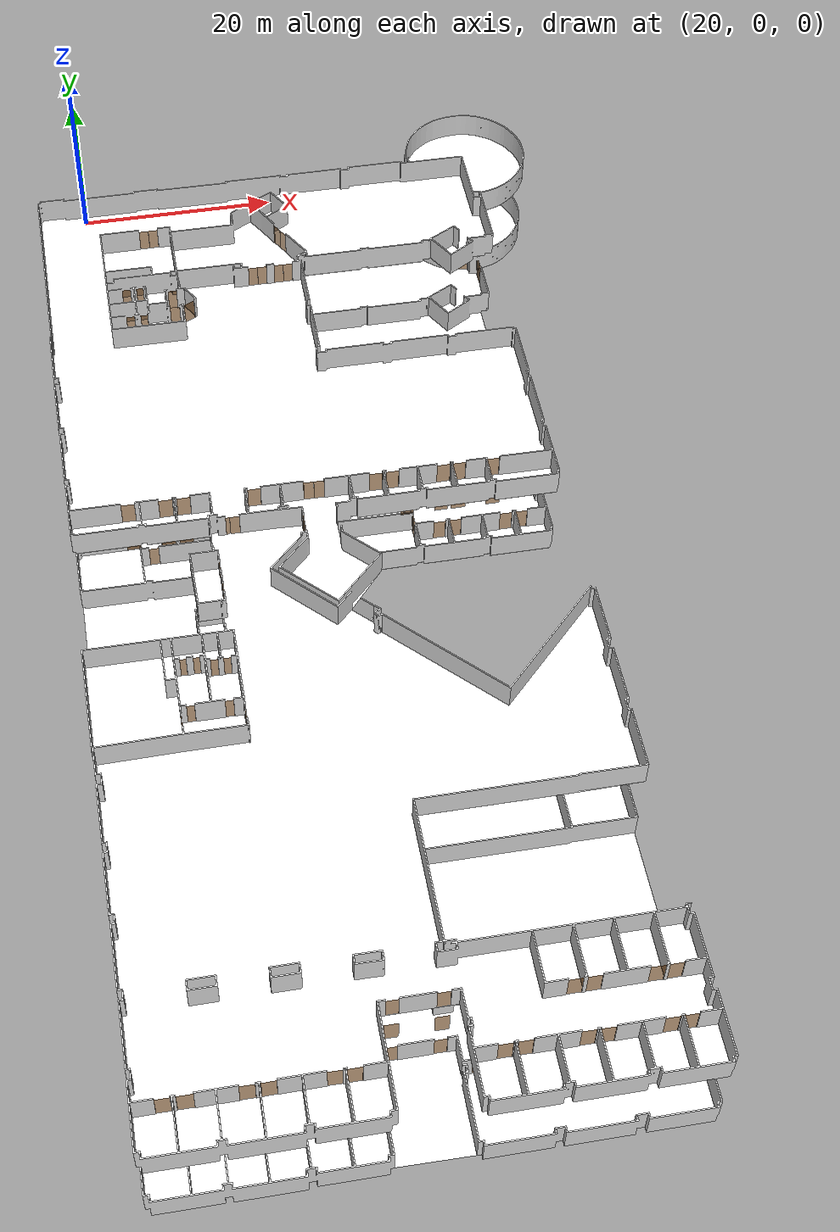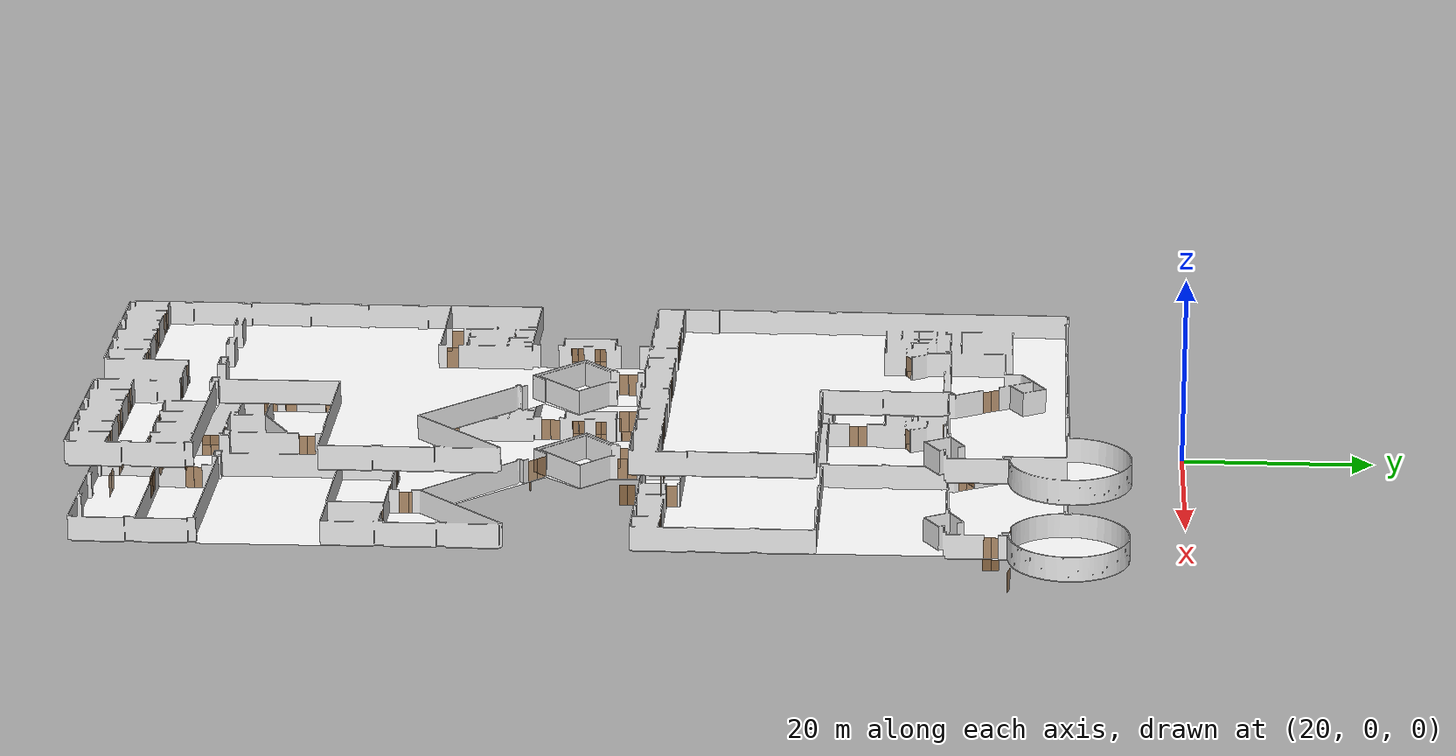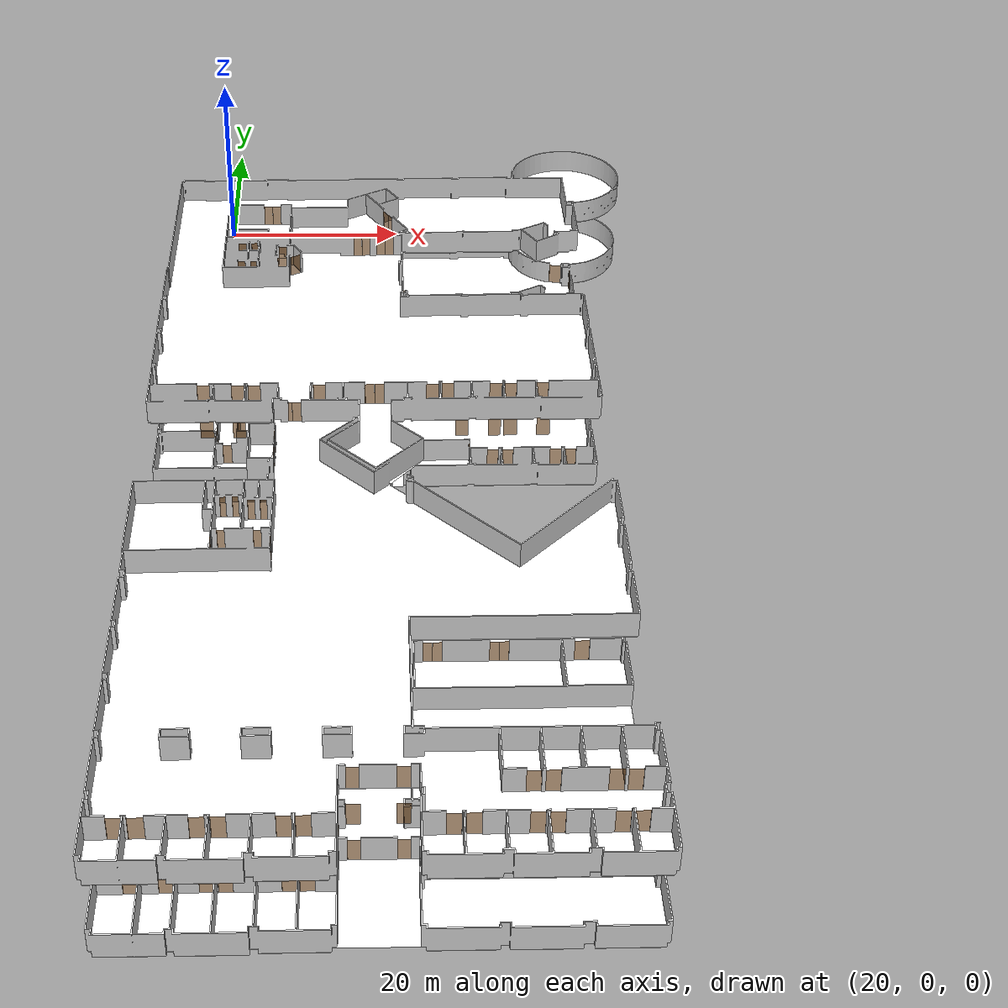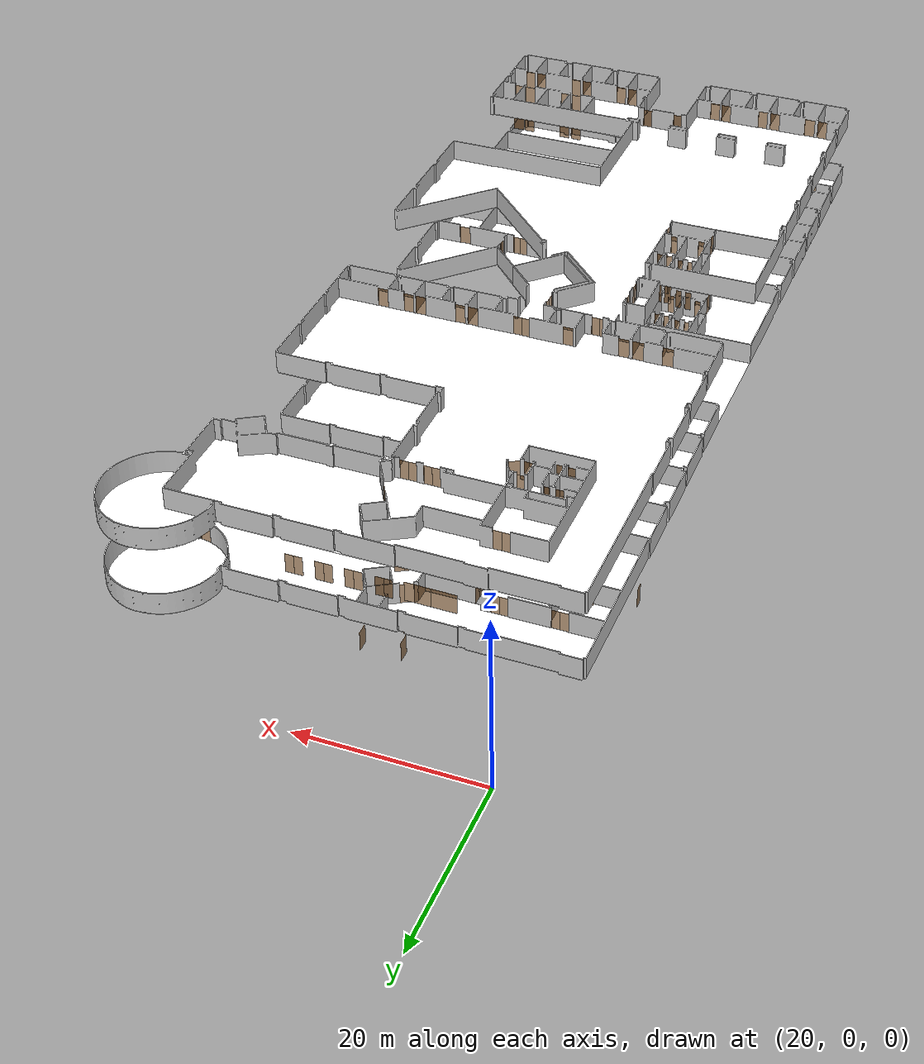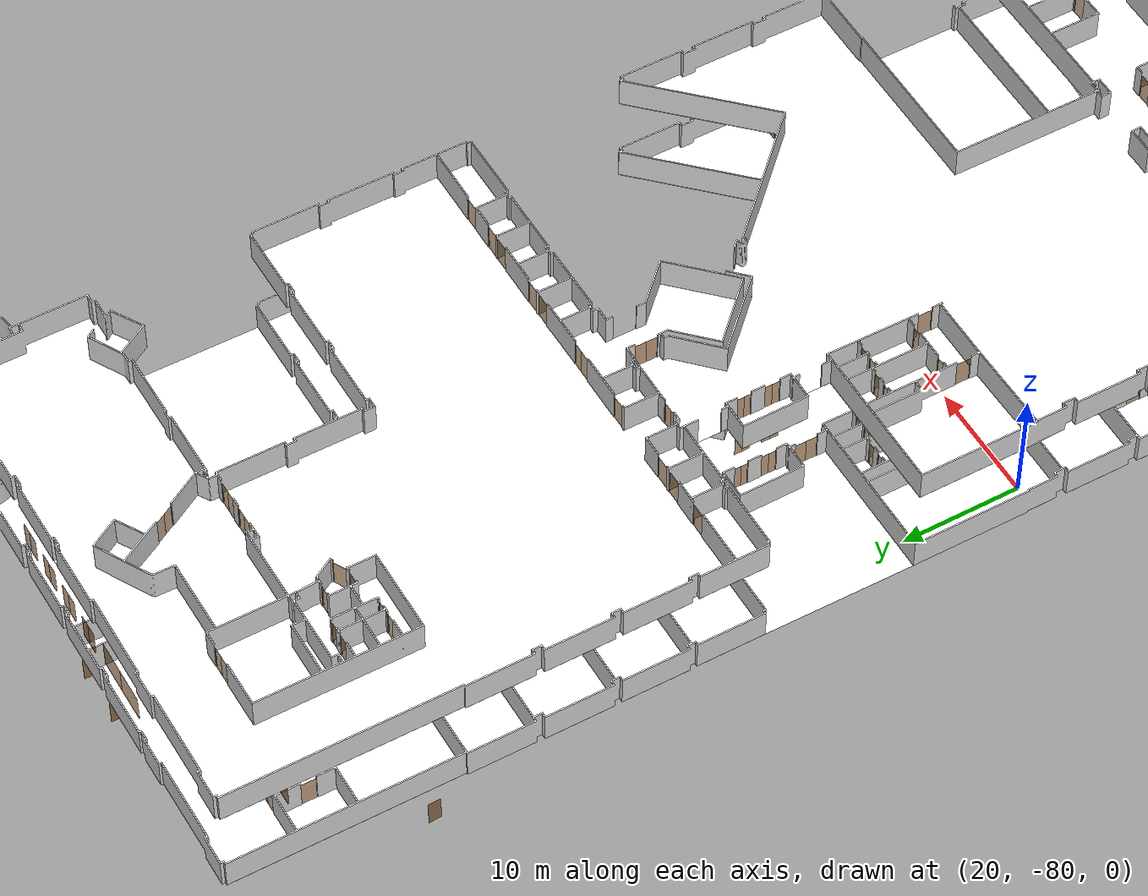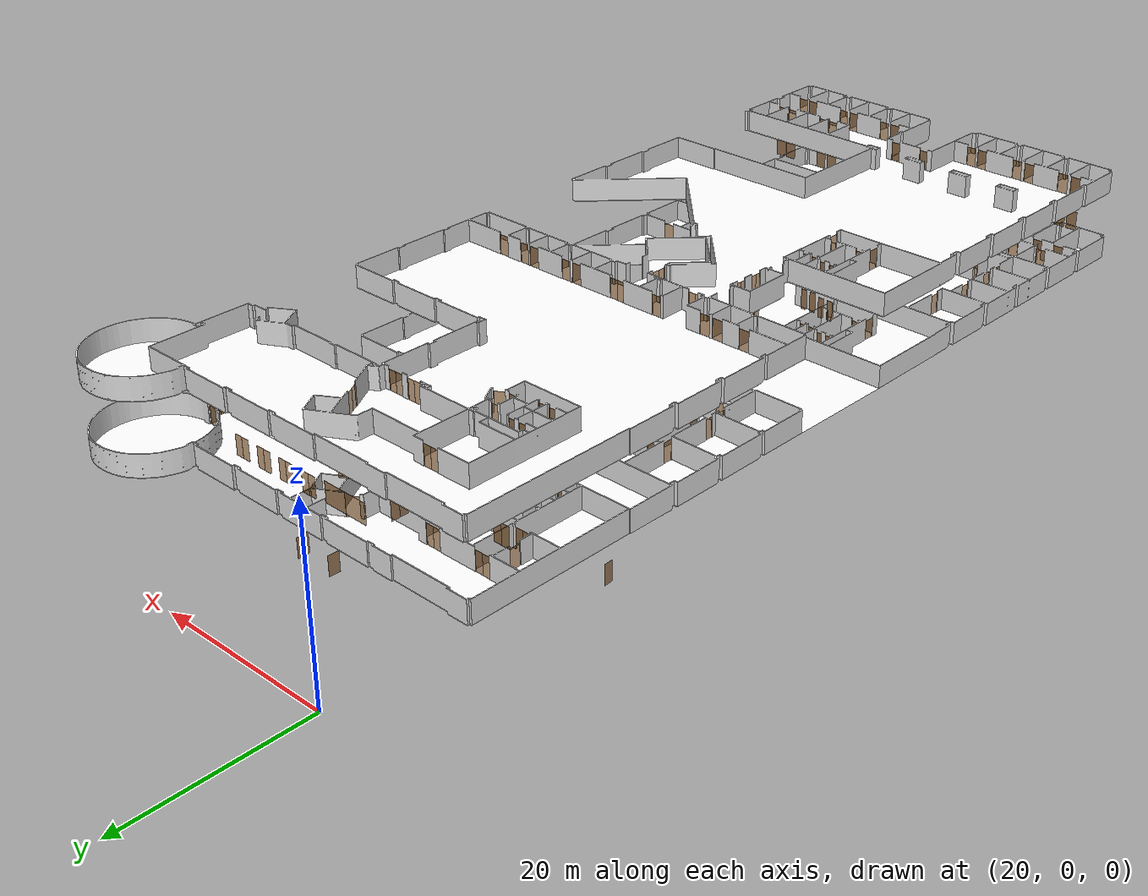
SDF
<sdf version="1.7">
 <world name="sim_world">
  <physics name="10ms" type="ode">
   <max_step_size>0.01</max_step_size>
   <real_time_factor>1.0</real_time_factor>
  </physics>
  <plugin filename="libgz-sim-physics-system.so" name="gz::sim::systems::Physics"/>
  <plugin filename="libgz-sim-user-commands-system.so" name="gz::sim::systems::UserCommands"/>
  <plugin filename="libgz-sim-scene-broadcaster-system.so" name="gz::sim::systems::SceneBroadcaster"/>
  <plugin filename="libdoor.so" name="door"/>
  <plugin filename="liblift.so" name="lift"/>
  <scene><ambient>1 1 1</ambient><background>0.8 0.8 0.8</background><grid>false</grid></scene>
  <light type="directional" name="sun">
   <pose>0 0 10 0 0 0</pose>
   <diffuse>1 1 1 1</diffuse>
   <specular>0.2 0.2 0.2 1</specular>
   <attenuation>
    <range>1000</range>
    <constant>0.09</constant>
    <linear>0.001</linear>
    <quadratic>0.001</quadratic>
   </attenuation>
   <direction>-0.5 0.1 -0.9</direction>
  </light>
  <model name="Snull1">
   <pose>34.31579733412984 -13.190942015457559 0.0 0 0 -1.5647744371355659</pose>
   <link name="right">
    <pose>0 0 1.11 0 0 0</pose>
    <visual name="right_visual">
     <geometry><box><size>1.254855103408931 0.03 2.2</size></box></geometry>
     <material>
      <ambient>0.5 0.25 0 0.6</ambient>
      <diffuse>0.5 0.25 0 0.6</diffuse>
      <pbr><metal><metalness>0.0</metalness></metal></pbr>
     </material>
    </visual>
    <collision name="right_collision">
     <geometry><box><size>1.254855103408931 0.03 2.2</size></box></geometry>
     <surface><contact><collide_bitmask>0x02</collide_bitmask></contact></surface>
    </collision>
    <inertial>
     <mass>50.0</mass>
     <inertia><ixx>20.17041666666667</ixx><iyy>26.72775554396433</iyy><izz>6.564838877297662</izz></inertia>
    </inertial>
   </link>
   <joint name="right_joint" type="revolute">
    <parent>world</parent>
    <child>right</child>
    <axis><xyz>0 0 1</xyz><limit><lower>0</lower><upper>1.57</upper></limit></axis>
    <pose>0.6324275517044655 0 0 0 0 0</pose>
   </joint>
   <plugin name="register_component" filename="libregister_component.so">
    <component name="Door">
     <v_max_door>0.5</v_max_door>
     <a_max_door>0.3</a_max_door>
     <a_nom_door>0.15</a_nom_door>
     <dx_min_door>0.01</dx_min_door>
     <f_max_door>500.0</f_max_door>
     <ros_interface>true</ros_interface>
     <door name="Snull1" type="SwingDoor" left_joint_name="empty_joint" right_joint_name="right_joint"/>
    </component>
   </plugin>
  </model>
  <model name="Snull2">
   <pose>38.63398424373668 -13.186069521711525 0.0 0 0 1.5780668441691235</pose>
   <link name="right">
    <pose>0 0 1.11 0 0 0</pose>
    <visual name="right_visual">
     <geometry><box><size>1.2944066519722939 0.03 2.2</size></box></geometry>
     <material>
      <ambient>0.5 0.25 0 0.6</ambient>
      <diffuse>0.5 0.25 0 0.6</diffuse>
      <pbr><metal><metalness>0.0</metalness></metal></pbr>
     </material>
    </visual>
    <collision name="right_collision">
     <geometry><box><size>1.2944066519722939 0.03 2.2</size></box></geometry>
     <surface><contact><collide_bitmask>0x02</collide_bitmask></contact></surface>
    </collision>
    <inertial>
     <mass>50.0</mass>
     <inertia><ixx>20.17041666666667</ixx><iyy>27.147869086125517</iyy><izz>6.984952419458847</izz></inertia>
    </inertial>
   </link>
   <joint name="right_joint" type="revolute">
    <parent>world</parent>
    <child>right</child>
    <axis><xyz>0 0 -1</xyz><limit><lower>0</lower><upper>1.57</upper></limit></axis>
    <pose>0.6522033259861469 0 0 0 0 0</pose>
   </joint>
   <plugin name="register_component" filename="libregister_component.so">
    <component name="Door">
     <v_max_door>0.5</v_max_door>
     <a_max_door>0.3</a_max_door>
     <a_nom_door>0.15</a_nom_door>
     <dx_min_door>0.01</dx_min_door>
     <f_max_door>500.0</f_max_door>
     <ros_interface>true</ros_interface>
     <door name="Snull2" type="SwingDoor" left_joint_name="empty_joint" right_joint_name="right_joint"/>
    </component>
   </plugin>
  </model>
  <model name="Snull3">
   <pose>52.391853041108135 -19.739573610125817 0.0 0 0 -1.5707963267948966</pose>
   <link name="right">
    <pose>0.4211626778180184 0 1.11 0 0 0</pose>
    <visual name="right_visual">
     <geometry><box><size>0.8323253556360368 0.03 2.2</size></box></geometry>
     <material>
      <ambient>0.5 0.25 0 0.6</ambient>
      <diffuse>0.5 0.25 0 0.6</diffuse>
      <pbr><metal><metalness>0.0</metalness></metal></pbr>
     </material>
    </visual>
    <collision name="right_collision">
     <geometry><box><size>0.8323253556360368 0.03 2.2</size></box></geometry>
     <surface><contact><collide_bitmask>0x02</collide_bitmask></contact></surface>
    </collision>
    <inertial>
     <mass>50.0</mass>
     <inertia><ixx>20.17041666666667</ixx><iyy>23.053189573477734</iyy><izz>2.8902729068110635</izz></inertia>
    </inertial>
   </link>
   <joint name="right_joint" type="revolute">
    <parent>world</parent>
    <child>right</child>
    <axis><xyz>0 0 -1</xyz><limit><lower>0</lower><upper>1.57</upper></limit></axis>
    <pose>0.4211626778180184 0 0 0 0 0</pose>
   </joint>
   <link name="left">
    <pose>-0.4211626778180184 0 1.11 0 0 0</pose>
    <visual name="left_visual">
     <geometry><box><size>0.8323253556360368 0.03 2.2</size></box></geometry>
     <material>
      <ambient>0.5 0.25 0 0.6</ambient>
      <diffuse>0.5 0.25 0 0.6</diffuse>
      <pbr><metal><metalness>0.0</metalness></metal></pbr>
     </material>
    </visual>
    <collision name="left_collision">
     <geometry><box><size>0.8323253556360368 0.03 2.2</size></box></geometry>
     <surface><contact><collide_bitmask>0x02</collide_bitmask></contact></surface>
    </collision>
    <inertial>
     <mass>50.0</mass>
     <inertia><ixx>20.17041666666667</ixx><iyy>23.053189573477734</iyy><izz>2.8902729068110635</izz></inertia>
    </inertial>
   </link>
   <joint name="left_joint" type="revolute">
    <parent>world</parent>
    <child>left</child>
    <axis><xyz>0 0 -1</xyz><limit><lower>-1.57</lower><upper>0</upper></limit></axis>
    <pose>-0.4211626778180184 0 0 0 0 0</pose>
   </joint>
   <plugin name="register_component" filename="libregister_component.so">
    <component name="Door">
     <v_max_door>0.5</v_max_door>
     <a_max_door>0.3</a_max_door>
     <a_nom_door>0.15</a_nom_door>
     <dx_min_door>0.01</dx_min_door>
     <f_max_door>500.0</f_max_door>
     <ros_interface>true</ros_interface>
     <door name="Snull3" type="DoubleSwingDoor" left_joint_name="left_joint" right_joint_name="right_joint"/>
    </component>
   </plugin>
  </model>
  <model name="Snull4">
   <pose>57.814863906209126 -17.951051039838692 0.0 0 0 2.9326769838084155</pose>
   <link name="right">
    <pose>0 0 1.11 0 0 0</pose>
    <visual name="right_visual">
     <geometry><box><size>1.2797012906970477 0.03 2.2</size></box></geometry>
     <material>
      <ambient>0.5 0.25 0 0.6</ambient>
      <diffuse>0.5 0.25 0 0.6</diffuse>
      <pbr><metal><metalness>0.0</metalness></metal></pbr>
     </material>
    </visual>
    <collision name="right_collision">
     <geometry><box><size>1.2797012906970477 0.03 2.2</size></box></geometry>
     <surface><contact><collide_bitmask>0x02</collide_bitmask></contact></surface>
    </collision>
    <inertial>
     <mass>50.0</mass>
     <inertia><ixx>20.17041666666667</ixx><iyy>26.99014747254871</iyy><izz>6.827230805882041</izz></inertia>
    </inertial>
   </link>
   <joint name="right_joint" type="revolute">
    <parent>world</parent>
    <child>right</child>
    <axis><xyz>0 0 1</xyz><limit><lower>0</lower><upper>1.57</upper></limit></axis>
    <pose>0.6448506453485239 0 0 0 0 0</pose>
   </joint>
   <plugin name="register_component" filename="libregister_component.so">
    <component name="Door">
     <v_max_door>0.5</v_max_door>
     <a_max_door>0.3</a_max_door>
     <a_nom_door>0.15</a_nom_door>
     <dx_min_door>0.01</dx_min_door>
     <f_max_door>500.0</f_max_door>
     <ros_interface>true</ros_interface>
     <door name="Snull4" type="SwingDoor" left_joint_name="empty_joint" right_joint_name="right_joint"/>
    </component>
   </plugin>
  </model>
  <model name="Snull5">
   <pose>41.95467274017098 -38.68651756711344 0.0 0 0 1.5707963267948966</pose>
   <link name="right">
    <pose>0.4606093417466308 0 1.11 0 0 0</pose>
    <visual name="right_visual">
     <geometry><box><size>0.9112186834932616 0.03 2.2</size></box></geometry>
     <material>
      <ambient>0.5 0.25 0 0.6</ambient>
      <diffuse>0.5 0.25 0 0.6</diffuse>
      <pbr><metal><metalness>0.0</metalness></metal></pbr>
     </material>
    </visual>
    <collision name="right_collision">
     <geometry><box><size>0.9112186834932616 0.03 2.2</size></box></geometry>
     <surface><contact><collide_bitmask>0x02</collide_bitmask></contact></surface>
    </collision>
    <inertial>
     <mass>50.0</mass>
     <inertia><ixx>20.17041666666667</ixx><iyy>23.626331204779977</iyy><izz>3.463414538113304</izz></inertia>
    </inertial>
   </link>
   <joint name="right_joint" type="revolute">
    <parent>world</parent>
    <child>right</child>
    <axis><xyz>0 0 -1</xyz><limit><lower>0</lower><upper>1.57</upper></limit></axis>
    <pose>0.4606093417466308 0 0 0 0 0</pose>
   </joint>
   <link name="left">
    <pose>-0.4606093417466308 0 1.11 0 0 0</pose>
    <visual name="left_visual">
     <geometry><box><size>0.9112186834932616 0.03 2.2</size></box></geometry>
     <material>
      <ambient>0.5 0.25 0 0.6</ambient>
      <diffuse>0.5 0.25 0 0.6</diffuse>
      <pbr><metal><metalness>0.0</metalness></metal></pbr>
     </material>
    </visual>
    <collision name="left_collision">
     <geometry><box><size>0.9112186834932616 0.03 2.2</size></box></geometry>
     <surface><contact><collide_bitmask>0x02</collide_bitmask></contact></surface>
    </collision>
    <inertial>
     <mass>50.0</mass>
     <inertia><ixx>20.17041666666667</ixx><iyy>23.626331204779977</iyy><izz>3.463414538113304</izz></inertia>
    </inertial>
   </link>
   <joint name="left_joint" type="revolute">
    <parent>world</parent>
    <child>left</child>
    <axis><xyz>0 0 -1</xyz><limit><lower>-1.57</lower><upper>0</upper></limit></axis>
    <pose>-0.4606093417466308 0 0 0 0 0</pose>
   </joint>
   <plugin name="register_component" filename="libregister_component.so">
    <component name="Door">
     <v_max_door>0.5</v_max_door>
     <a_max_door>0.3</a_max_door>
     <a_nom_door>0.15</a_nom_door>
     <dx_min_door>0.01</dx_min_door>
     <f_max_door>500.0</f_max_door>
     <ros_interface>true</ros_interface>
     <door name="Snull5" type="DoubleSwingDoor" left_joint_name="left_joint" right_joint_name="right_joint"/>
    </component>
   </plugin>
  </model>
  <model name="Snull6">
   <pose>36.91817570847177 -38.673374901990044 0.0 0 0 -1.574078184232942</pose>
   <link name="right">
    <pose>0.45222959440596977 0 1.11 0 0 0</pose>
    <visual name="right_visual">
     <geometry><box><size>0.8944591888119395 0.03 2.2</size></box></geometry>
     <material>
      <ambient>0.5 0.25 0 0.6</ambient>
      <diffuse>0.5 0.25 0 0.6</diffuse>
      <pbr><metal><metalness>0.0</metalness></metal></pbr>
     </material>
    </visual>
    <collision name="right_collision">
     <geometry><box><size>0.8944591888119395 0.03 2.2</size></box></geometry>
     <surface><contact><collide_bitmask>0x02</collide_bitmask></contact></surface>
    </collision>
    <inertial>
     <mass>50.0</mass>
     <inertia><ixx>20.17041666666667</ixx><iyy>23.500238501875476</iyy><izz>3.3373218352088037</izz></inertia>
    </inertial>
   </link>
   <joint name="right_joint" type="revolute">
    <parent>world</parent>
    <child>right</child>
    <axis><xyz>0 0 -1</xyz><limit><lower>0</lower><upper>1.57</upper></limit></axis>
    <pose>0.45222959440596977 0 0 0 0 0</pose>
   </joint>
   <link name="left">
    <pose>-0.45222959440596977 0 1.11 0 0 0</pose>
    <visual name="left_visual">
     <geometry><box><size>0.8944591888119395 0.03 2.2</size></box></geometry>
     <material>
      <ambient>0.5 0.25 0 0.6</ambient>
      <diffuse>0.5 0.25 0 0.6</diffuse>
      <pbr><metal><metalness>0.0</metalness></metal></pbr>
     </material>
    </visual>
    <collision name="left_collision">
     <geometry><box><size>0.8944591888119395 0.03 2.2</size></box></geometry>
     <surface><contact><collide_bitmask>0x02</collide_bitmask></contact></surface>
    </collision>
    <inertial>
     <mass>50.0</mass>
     <inertia><ixx>20.17041666666667</ixx><iyy>23.500238501875476</iyy><izz>3.3373218352088037</izz></inertia>
    </inertial>
   </link>
   <joint name="left_joint" type="revolute">
    <parent>world</parent>
    <child>left</child>
    <axis><xyz>0 0 -1</xyz><limit><lower>-1.57</lower><upper>0</upper></limit></axis>
    <pose>-0.45222959440596977 0 0 0 0 0</pose>
   </joint>
   <plugin name="register_component" filename="libregister_component.so">
    <component name="Door">
     <v_max_door>0.5</v_max_door>
     <a_max_door>0.3</a_max_door>
     <a_nom_door>0.15</a_nom_door>
     <dx_min_door>0.01</dx_min_door>
     <f_max_door>500.0</f_max_door>
     <ros_interface>true</ros_interface>
     <door name="Snull6" type="DoubleSwingDoor" left_joint_name="left_joint" right_joint_name="right_joint"/>
    </component>
   </plugin>
  </model>
  <model name="Snull7">
   <pose>34.106597468543455 -54.42554978904526 0.0 0 0 -1.5707963267948966</pose>
   <link name="right">
    <pose>0 0 1.11 0 0 0</pose>
    <visual name="right_visual">
     <geometry><box><size>1.0218858977709695 0.03 2.2</size></box></geometry>
     <material>
      <ambient>0.5 0.25 0 0.6</ambient>
      <diffuse>0.5 0.25 0 0.6</diffuse>
      <pbr><metal><metalness>0.0</metalness></metal></pbr>
     </material>
    </visual>
    <collision name="right_collision">
     <geometry><box><size>1.0218858977709695 0.03 2.2</size></box></geometry>
     <surface><contact><collide_bitmask>0x02</collide_bitmask></contact></surface>
    </collision>
    <inertial>
     <mass>50.0</mass>
     <inertia><ixx>20.17041666666667</ixx><iyy>24.517711616929923</iyy><izz>4.354794950263251</izz></inertia>
    </inertial>
   </link>
   <joint name="right_joint" type="revolute">
    <parent>world</parent>
    <child>right</child>
    <axis><xyz>0 0 -1</xyz><limit><lower>0</lower><upper>1.57</upper></limit></axis>
    <pose>0.5159429488854848 0 0 0 0 0</pose>
   </joint>
   <plugin name="register_component" filename="libregister_component.so">
    <component name="Door">
     <v_max_door>0.5</v_max_door>
     <a_max_door>0.3</a_max_door>
     <a_nom_door>0.15</a_nom_door>
     <dx_min_door>0.01</dx_min_door>
     <f_max_door>500.0</f_max_door>
     <ros_interface>true</ros_interface>
     <door name="Snull7" type="SwingDoor" left_joint_name="empty_joint" right_joint_name="right_joint"/>
    </component>
   </plugin>
  </model>
  <model name="Snull8">
   <pose>40.75631930702308 -54.42665123399168 0.0 0 0 1.550409697207399</pose>
   <link name="right">
    <pose>0 0 1.11 0 0 0</pose>
    <visual name="right_visual">
     <geometry><box><size>1.171367842129814 0.03 2.2</size></box></geometry>
     <material>
      <ambient>0.5 0.25 0 0.6</ambient>
      <diffuse>0.5 0.25 0 0.6</diffuse>
      <pbr><metal><metalness>0.0</metalness></metal></pbr>
     </material>
    </visual>
    <collision name="right_collision">
     <geometry><box><size>1.171367842129814 0.03 2.2</size></box></geometry>
     <surface><contact><collide_bitmask>0x02</collide_bitmask></contact></surface>
    </collision>
    <inertial>
     <mass>50.0</mass>
     <inertia><ixx>20.17041666666667</ixx><iyy>25.88376092323274</iyy><izz>5.720844256566069</izz></inertia>
    </inertial>
   </link>
   <joint name="right_joint" type="revolute">
    <parent>world</parent>
    <child>right</child>
    <axis><xyz>0 0 1</xyz><limit><lower>0</lower><upper>1.57</upper></limit></axis>
    <pose>0.590683921064907 0 0 0 0 0</pose>
   </joint>
   <plugin name="register_component" filename="libregister_component.so">
    <component name="Door">
     <v_max_door>0.5</v_max_door>
     <a_max_door>0.3</a_max_door>
     <a_nom_door>0.15</a_nom_door>
     <dx_min_door>0.01</dx_min_door>
     <f_max_door>500.0</f_max_door>
     <ros_interface>true</ros_interface>
     <door name="Snull8" type="SwingDoor" left_joint_name="empty_joint" right_joint_name="right_joint"/>
    </component>
   </plugin>
  </model>
  <model name="Snull9">
   <pose>35.663947279991014 -57.37185901504682 0.0 0 0 -1.5624884779698478</pose>
   <link name="right">
    <pose>0.42133590085702205 0 1.11 0 0 0</pose>
    <visual name="right_visual">
     <geometry><box><size>0.8326718017140441 0.03 2.2</size></box></geometry>
     <material>
      <ambient>0.5 0.25 0 0.6</ambient>
      <diffuse>0.5 0.25 0 0.6</diffuse>
      <pbr><metal><metalness>0.0</metalness></metal></pbr>
     </material>
    </visual>
    <collision name="right_collision">
     <geometry><box><size>0.8326718017140441 0.03 2.2</size></box></geometry>
     <surface><contact><collide_bitmask>0x02</collide_bitmask></contact></surface>
    </collision>
    <inertial>
     <mass>50.0</mass>
     <inertia><ixx>20.17041666666667</ixx><iyy>23.055593039040474</iyy><izz>2.892676372373802</izz></inertia>
    </inertial>
   </link>
   <joint name="right_joint" type="revolute">
    <parent>world</parent>
    <child>right</child>
    <axis><xyz>0 0 -1</xyz><limit><lower>0</lower><upper>1.57</upper></limit></axis>
    <pose>0.42133590085702205 0 0 0 0 0</pose>
   </joint>
   <link name="left">
    <pose>-0.42133590085702205 0 1.11 0 0 0</pose>
    <visual name="left_visual">
     <geometry><box><size>0.8326718017140441 0.03 2.2</size></box></geometry>
     <material>
      <ambient>0.5 0.25 0 0.6</ambient>
      <diffuse>0.5 0.25 0 0.6</diffuse>
      <pbr><metal><metalness>0.0</metalness></metal></pbr>
     </material>
    </visual>
    <collision name="left_collision">
     <geometry><box><size>0.8326718017140441 0.03 2.2</size></box></geometry>
     <surface><contact><collide_bitmask>0x02</collide_bitmask></contact></surface>
    </collision>
    <inertial>
     <mass>50.0</mass>
     <inertia><ixx>20.17041666666667</ixx><iyy>23.055593039040474</iyy><izz>2.892676372373802</izz></inertia>
    </inertial>
   </link>
   <joint name="left_joint" type="revolute">
    <parent>world</parent>
    <child>left</child>
    <axis><xyz>0 0 -1</xyz><limit><lower>-1.57</lower><upper>0</upper></limit></axis>
    <pose>-0.42133590085702205 0 0 0 0 0</pose>
   </joint>
   <plugin name="register_component" filename="libregister_component.so">
    <component name="Door">
     <v_max_door>0.5</v_max_door>
     <a_max_door>0.3</a_max_door>
     <a_nom_door>0.15</a_nom_door>
     <dx_min_door>0.01</dx_min_door>
     <f_max_door>500.0</f_max_door>
     <ros_interface>true</ros_interface>
     <door name="Snull9" type="DoubleSwingDoor" left_joint_name="left_joint" right_joint_name="right_joint"/>
    </component>
   </plugin>
  </model>
  <model name="Snull10">
   <pose>35.266232311540875 -16.49999999999999 0.0 0 0 -2.654102844831569</pose>
   <link name="right">
    <pose>0 0 1.11 0 0 0</pose>
    <visual name="right_visual">
     <geometry><box><size>0.8774159202349445 0.03 2.2</size></box></geometry>
     <material>
      <ambient>0.5 0.25 0 0.6</ambient>
      <diffuse>0.5 0.25 0 0.6</diffuse>
      <pbr><metal><metalness>0.0</metalness></metal></pbr>
     </material>
    </visual>
    <collision name="right_collision">
     <geometry><box><size>0.8774159202349445 0.03 2.2</size></box></geometry>
     <surface><contact><collide_bitmask>0x02</collide_bitmask></contact></surface>
    </collision>
    <inertial>
     <mass>50.0</mass>
     <inertia><ixx>20.17041666666667</ixx><iyy>23.374411237840565</iyy><izz>3.211494571173894</izz></inertia>
    </inertial>
   </link>
   <joint name="right_joint" type="revolute">
    <parent>world</parent>
    <child>right</child>
    <axis><xyz>0 0 -1</xyz><limit><lower>0</lower><upper>1.57</upper></limit></axis>
    <pose>0.44370796011747227 0 0 0 0 0</pose>
   </joint>
   <plugin name="register_component" filename="libregister_component.so">
    <component name="Door">
     <v_max_door>0.5</v_max_door>
     <a_max_door>0.3</a_max_door>
     <a_nom_door>0.15</a_nom_door>
     <dx_min_door>0.01</dx_min_door>
     <f_max_door>500.0</f_max_door>
     <ros_interface>true</ros_interface>
     <door name="Snull10" type="SwingDoor" left_joint_name="empty_joint" right_joint_name="right_joint"/>
    </component>
   </plugin>
  </model>
  <model name="Snull11">
   <pose>37.988257476757624 -22.20064966583279 0.0 0 0 0.5302253309043828</pose>
   <link name="right">
    <pose>0.43577267423389904 0 1.11 0 0 0</pose>
    <visual name="right_visual">
     <geometry><box><size>0.8615453484677981 0.03 2.2</size></box></geometry>
     <material>
      <ambient>0.5 0.25 0 0.6</ambient>
      <diffuse>0.5 0.25 0 0.6</diffuse>
      <pbr><metal><metalness>0.0</metalness></metal></pbr>
     </material>
    </visual>
    <collision name="right_collision">
     <geometry><box><size>0.8615453484677981 0.03 2.2</size></box></geometry>
     <surface><contact><collide_bitmask>0x02</collide_bitmask></contact></surface>
    </collision>
    <inertial>
     <mass>50.0</mass>
     <inertia><ixx>20.17041666666667</ixx><iyy>23.25941828111042</iyy><izz>3.0965016144437487</izz></inertia>
    </inertial>
   </link>
   <joint name="right_joint" type="revolute">
    <parent>world</parent>
    <child>right</child>
    <axis><xyz>0 0 -1</xyz><limit><lower>0</lower><upper>1.57</upper></limit></axis>
    <pose>0.43577267423389904 0 0 0 0 0</pose>
   </joint>
   <link name="left">
    <pose>-0.43577267423389904 0 1.11 0 0 0</pose>
    <visual name="left_visual">
     <geometry><box><size>0.8615453484677981 0.03 2.2</size></box></geometry>
     <material>
      <ambient>0.5 0.25 0 0.6</ambient>
      <diffuse>0.5 0.25 0 0.6</diffuse>
      <pbr><metal><metalness>0.0</metalness></metal></pbr>
     </material>
    </visual>
    <collision name="left_collision">
     <geometry><box><size>0.8615453484677981 0.03 2.2</size></box></geometry>
     <surface><contact><collide_bitmask>0x02</collide_bitmask></contact></surface>
    </collision>
    <inertial>
     <mass>50.0</mass>
     <inertia><ixx>20.17041666666667</ixx><iyy>23.25941828111042</iyy><izz>3.0965016144437487</izz></inertia>
    </inertial>
   </link>
   <joint name="left_joint" type="revolute">
    <parent>world</parent>
    <child>left</child>
    <axis><xyz>0 0 -1</xyz><limit><lower>-1.57</lower><upper>0</upper></limit></axis>
    <pose>-0.43577267423389904 0 0 0 0 0</pose>
   </joint>
   <plugin name="register_component" filename="libregister_component.so">
    <component name="Door">
     <v_max_door>0.5</v_max_door>
     <a_max_door>0.3</a_max_door>
     <a_nom_door>0.15</a_nom_door>
     <dx_min_door>0.01</dx_min_door>
     <f_max_door>500.0</f_max_door>
     <ros_interface>true</ros_interface>
     <door name="Snull11" type="DoubleSwingDoor" left_joint_name="left_joint" right_joint_name="right_joint"/>
    </component>
   </plugin>
  </model>
  <model name="Snull12">
   <pose>24.6549303662771 -22.17731396781539 0.0 0 0 3.141592653589793</pose>
   <link name="right">
    <pose>0 0 1.11 0 0 0</pose>
    <visual name="right_visual">
     <geometry><box><size>1.063964828435951 0.03 2.2</size></box></geometry>
     <material>
      <ambient>0.5 0.25 0 0.6</ambient>
      <diffuse>0.5 0.25 0 0.6</diffuse>
      <pbr><metal><metalness>0.0</metalness></metal></pbr>
     </material>
    </visual>
    <collision name="right_collision">
     <geometry><box><size>1.063964828435951 0.03 2.2</size></box></geometry>
     <surface><contact><collide_bitmask>0x02</collide_bitmask></contact></surface>
    </collision>
    <inertial>
     <mass>50.0</mass>
     <inertia><ixx>20.17041666666667</ixx><iyy>24.8834214839531</iyy><izz>4.720504817286428</izz></inertia>
    </inertial>
   </link>
   <joint name="right_joint" type="revolute">
    <parent>world</parent>
    <child>right</child>
    <axis><xyz>0 0 -1</xyz><limit><lower>0</lower><upper>1.57</upper></limit></axis>
    <pose>0.5369824142179755 0 0 0 0 0</pose>
   </joint>
   <plugin name="register_component" filename="libregister_component.so">
    <component name="Door">
     <v_max_door>0.5</v_max_door>
     <a_max_door>0.3</a_max_door>
     <a_nom_door>0.15</a_nom_door>
     <dx_min_door>0.01</dx_min_door>
     <f_max_door>500.0</f_max_door>
     <ros_interface>true</ros_interface>
     <door name="Snull12" type="SwingDoor" left_joint_name="empty_joint" right_joint_name="right_joint"/>
    </component>
   </plugin>
  </model>
  <model name="Snull13">
   <pose>28.110629877160868 -25.59315610648544 0.0 0 0 -1.5295418897094035</pose>
   <link name="right">
    <pose>0 0 1.11 0 0 0</pose>
    <visual name="right_visual">
     <geometry><box><size>1.0111802562463839 0.03 2.2</size></box></geometry>
     <material>
      <ambient>0.5 0.25 0 0.6</ambient>
      <diffuse>0.5 0.25 0 0.6</diffuse>
      <pbr><metal><metalness>0.0</metalness></metal></pbr>
     </material>
    </visual>
    <collision name="right_collision">
     <geometry><box><size>1.0111802562463839 0.03 2.2</size></box></geometry>
     <surface><contact><collide_bitmask>0x02</collide_bitmask></contact></surface>
    </collision>
    <inertial>
     <mass>50.0</mass>
     <inertia><ixx>20.17041666666667</ixx><iyy>24.4270229609271</iyy><izz>4.2641062942604275</izz></inertia>
    </inertial>
   </link>
   <joint name="right_joint" type="revolute">
    <parent>world</parent>
    <child>right</child>
    <axis><xyz>0 0 -1</xyz><limit><lower>0</lower><upper>1.57</upper></limit></axis>
    <pose>0.5105901281231919 0 0 0 0 0</pose>
   </joint>
   <plugin name="register_component" filename="libregister_component.so">
    <component name="Door">
     <v_max_door>0.5</v_max_door>
     <a_max_door>0.3</a_max_door>
     <a_nom_door>0.15</a_nom_door>
     <dx_min_door>0.01</dx_min_door>
     <f_max_door>500.0</f_max_door>
     <ros_interface>true</ros_interface>
     <door name="Snull13" type="SwingDoor" left_joint_name="empty_joint" right_joint_name="right_joint"/>
    </component>
   </plugin>
  </model>
  <model name="Snull14">
   <pose>15.587816898779066 -28.54413247209049 0.0 0 0 1.6166443585963561</pose>
   <link name="right">
    <pose>0 0 1.11 0 0 0</pose>
    <visual name="right_visual">
     <geometry><box><size>1.023793662885057 0.03 2.2</size></box></geometry>
     <material>
      <ambient>0.5 0.25 0 0.6</ambient>
      <diffuse>0.5 0.25 0 0.6</diffuse>
      <pbr><metal><metalness>0.0</metalness></metal></pbr>
     </material>
    </visual>
    <collision name="right_collision">
     <geometry><box><size>1.023793662885057 0.03 2.2</size></box></geometry>
     <surface><contact><collide_bitmask>0x02</collide_bitmask></contact></surface>
    </collision>
    <inertial>
     <mass>50.0</mass>
     <inertia><ixx>20.17041666666667</ixx><iyy>24.533972767348345</iyy><izz>4.371056100681675</izz></inertia>
    </inertial>
   </link>
   <joint name="right_joint" type="revolute">
    <parent>world</parent>
    <child>right</child>
    <axis><xyz>0 0 1</xyz><limit><lower>0</lower><upper>1.57</upper></limit></axis>
    <pose>0.5168968314425285 0 0 0 0 0</pose>
   </joint>
   <plugin name="register_component" filename="libregister_component.so">
    <component name="Door">
     <v_max_door>0.5</v_max_door>
     <a_max_door>0.3</a_max_door>
     <a_nom_door>0.15</a_nom_door>
     <dx_min_door>0.01</dx_min_door>
     <f_max_door>500.0</f_max_door>
     <ros_interface>true</ros_interface>
     <door name="Snull14" type="SwingDoor" left_joint_name="empty_joint" right_joint_name="right_joint"/>
    </component>
   </plugin>
  </model>
  <model name="Snull15">
   <pose>28.084941940783317 -75.57958406451849 0.0 0 0 1.5806374847145241</pose>
   <link name="right">
    <pose>0 0 1.11 0 0 0</pose>
    <visual name="right_visual">
     <geometry><box><size>1.2572084339557512 0.03 2.2</size></box></geometry>
     <material>
      <ambient>0.5 0.25 0 0.6</ambient>
      <diffuse>0.5 0.25 0 0.6</diffuse>
      <pbr><metal><metalness>0.0</metalness></metal></pbr>
     </material>
    </visual>
    <collision name="right_collision">
     <geometry><box><size>1.2572084339557512 0.03 2.2</size></box></geometry>
     <surface><contact><collide_bitmask>0x02</collide_bitmask></contact></surface>
    </collision>
    <inertial>
     <mass>50.0</mass>
     <inertia><ixx>20.17041666666667</ixx><iyy>26.752387693372807</iyy><izz>6.589471026706136</izz></inertia>
    </inertial>
   </link>
   <joint name="right_joint" type="revolute">
    <parent>world</parent>
    <child>right</child>
    <axis><xyz>0 0 1</xyz><limit><lower>0</lower><upper>1.57</upper></limit></axis>
    <pose>0.6336042169778756 0 0 0 0 0</pose>
   </joint>
   <plugin name="register_component" filename="libregister_component.so">
    <component name="Door">
     <v_max_door>0.5</v_max_door>
     <a_max_door>0.3</a_max_door>
     <a_nom_door>0.15</a_nom_door>
     <dx_min_door>0.01</dx_min_door>
     <f_max_door>500.0</f_max_door>
     <ros_interface>true</ros_interface>
     <door name="Snull15" type="SwingDoor" left_joint_name="empty_joint" right_joint_name="right_joint"/>
    </component>
   </plugin>
  </model>
  <model name="Snull16">
   <pose>35.237146697532 -98.97069036329009 0.0 0 0 3.141592653589793</pose>
   <link name="right">
    <pose>0 0 1.11 0 0 0</pose>
    <visual name="right_visual">
     <geometry><box><size>1.0574308329910787 0.03 2.2</size></box></geometry>
     <material>
      <ambient>0.5 0.25 0 0.6</ambient>
      <diffuse>0.5 0.25 0 0.6</diffuse>
      <pbr><metal><metalness>0.0</metalness></metal></pbr>
     </material>
    </visual>
    <collision name="right_collision">
     <geometry><box><size>1.0574308329910787 0.03 2.2</size></box></geometry>
     <surface><contact><collide_bitmask>0x02</collide_bitmask></contact></surface>
    </collision>
    <inertial>
     <mass>50.0</mass>
     <inertia><ixx>20.17041666666667</ixx><iyy>24.8256665273342</iyy><izz>4.662749860667526</izz></inertia>
    </inertial>
   </link>
   <joint name="right_joint" type="revolute">
    <parent>world</parent>
    <child>right</child>
    <axis><xyz>0 0 -1</xyz><limit><lower>0</lower><upper>1.57</upper></limit></axis>
    <pose>0.5337154164955393 0 0 0 0 0</pose>
   </joint>
   <plugin name="register_component" filename="libregister_component.so">
    <component name="Door">
     <v_max_door>0.5</v_max_door>
     <a_max_door>0.3</a_max_door>
     <a_nom_door>0.15</a_nom_door>
     <dx_min_door>0.01</dx_min_door>
     <f_max_door>500.0</f_max_door>
     <ros_interface>true</ros_interface>
     <door name="Snull16" type="SwingDoor" left_joint_name="empty_joint" right_joint_name="right_joint"/>
    </component>
   </plugin>
  </model>
  <model name="Snull17">
   <pose>35.226505619236065 -102.68442668857105 0.0 0 0 3.141592653589793</pose>
   <link name="right">
    <pose>0 0 1.11 0 0 0</pose>
    <visual name="right_visual">
     <geometry><box><size>1.1178422880185204 0.03 2.2</size></box></geometry>
     <material>
      <ambient>0.5 0.25 0 0.6</ambient>
      <diffuse>0.5 0.25 0 0.6</diffuse>
      <pbr><metal><metalness>0.0</metalness></metal></pbr>
     </material>
    </visual>
    <collision name="right_collision">
     <geometry><box><size>1.1178422880185204 0.03 2.2</size></box></geometry>
     <surface><contact><collide_bitmask>0x02</collide_bitmask></contact></surface>
    </collision>
    <inertial>
     <mass>50.0</mass>
     <inertia><ixx>20.17041666666667</ixx><iyy>25.37321408701034</iyy><izz>5.210297420343669</izz></inertia>
    </inertial>
   </link>
   <joint name="right_joint" type="revolute">
    <parent>world</parent>
    <child>right</child>
    <axis><xyz>0 0 -1</xyz><limit><lower>0</lower><upper>1.57</upper></limit></axis>
    <pose>0.5639211440092602 0 0 0 0 0</pose>
   </joint>
   <plugin name="register_component" filename="libregister_component.so">
    <component name="Door">
     <v_max_door>0.5</v_max_door>
     <a_max_door>0.3</a_max_door>
     <a_nom_door>0.15</a_nom_door>
     <dx_min_door>0.01</dx_min_door>
     <f_max_door>500.0</f_max_door>
     <ros_interface>true</ros_interface>
     <door name="Snull17" type="SwingDoor" left_joint_name="empty_joint" right_joint_name="right_joint"/>
    </component>
   </plugin>
  </model>
  <model name="Snull18">
   <pose>39.10863234141057 -102.68442668857105 0.0 0 0 0.0</pose>
   <link name="right">
    <pose>0 0 1.11 0 0 0</pose>
    <visual name="right_visual">
     <geometry><box><size>1.1415886943210134 0.03 2.2</size></box></geometry>
     <material>
      <ambient>0.5 0.25 0 0.6</ambient>
      <diffuse>0.5 0.25 0 0.6</diffuse>
      <pbr><metal><metalness>0.0</metalness></metal></pbr>
     </material>
    </visual>
    <collision name="right_collision">
     <geometry><box><size>1.1415886943210134 0.03 2.2</size></box></geometry>
     <surface><contact><collide_bitmask>0x02</collide_bitmask></contact></surface>
    </collision>
    <inertial>
     <mass>50.0</mass>
     <inertia><ixx>20.17041666666667</ixx><iyy>25.596769779173155</iyy><izz>5.433853112506484</izz></inertia>
    </inertial>
   </link>
   <joint name="right_joint" type="revolute">
    <parent>world</parent>
    <child>right</child>
    <axis><xyz>0 0 1</xyz><limit><lower>0</lower><upper>1.57</upper></limit></axis>
    <pose>0.5757943471605067 0 0 0 0 0</pose>
   </joint>
   <plugin name="register_component" filename="libregister_component.so">
    <component name="Door">
     <v_max_door>0.5</v_max_door>
     <a_max_door>0.3</a_max_door>
     <a_nom_door>0.15</a_nom_door>
     <dx_min_door>0.01</dx_min_door>
     <f_max_door>500.0</f_max_door>
     <ros_interface>true</ros_interface>
     <door name="Snull18" type="SwingDoor" left_joint_name="empty_joint" right_joint_name="right_joint"/>
    </component>
   </plugin>
  </model>
  <model name="Snull19">
   <pose>27.81230631370644 -60.652111413956575 0.0 0 0 1.5707963267948966</pose>
   <link name="right">
    <pose>0.3098140611581979 0 1.11 0 0 0</pose>
    <visual name="right_visual">
     <geometry><box><size>0.6096281223163957 0.03 2.2</size></box></geometry>
     <material>
      <ambient>0.5 0.25 0 0.6</ambient>
      <diffuse>0.5 0.25 0 0.6</diffuse>
      <pbr><metal><metalness>0.0</metalness></metal></pbr>
     </material>
    </visual>
    <collision name="right_collision">
     <geometry><box><size>0.6096281223163957 0.03 2.2</size></box></geometry>
     <surface><contact><collide_bitmask>0x02</collide_bitmask></contact></surface>
    </collision>
    <inertial>
     <mass>50.0</mass>
     <inertia><ixx>20.17041666666667</ixx><iyy>21.71519353132923</iyy><izz>1.55227686466256</izz></inertia>
    </inertial>
   </link>
   <joint name="right_joint" type="prismatic">
    <parent>world</parent>
    <child>right</child>
    <axis>
     <xyz>1 0 0</xyz>
     <limit><lower>0.0</lower><upper>0.6196281223163957</upper><effort>500.0</effort></limit>
    </axis>
   </joint>
   <link name="left">
    <pose>-0.3098140611581979 0 1.11 0 0 0</pose>
    <visual name="left_visual">
     <geometry><box><size>0.6096281223163957 0.03 2.2</size></box></geometry>
     <material>
      <ambient>0.5 0.25 0 0.6</ambient>
      <diffuse>0.5 0.25 0 0.6</diffuse>
      <pbr><metal><metalness>0.0</metalness></metal></pbr>
     </material>
    </visual>
    <collision name="left_collision">
     <geometry><box><size>0.6096281223163957 0.03 2.2</size></box></geometry>
     <surface><contact><collide_bitmask>0x02</collide_bitmask></contact></surface>
    </collision>
    <inertial>
     <mass>50.0</mass>
     <inertia><ixx>20.17041666666667</ixx><iyy>21.71519353132923</iyy><izz>1.55227686466256</izz></inertia>
    </inertial>
   </link>
   <joint name="left_joint" type="prismatic">
    <parent>world</parent>
    <child>left</child>
    <axis>
     <xyz>1 0 0</xyz>
     <limit><lower>-0.6196281223163957</lower><upper>0.0</upper><effort>500.0</effort></limit>
    </axis>
   </joint>
   <plugin name="register_component" filename="libregister_component.so">
    <component name="Door">
     <v_max_door>0.2</v_max_door>
     <a_max_door>0.2</a_max_door>
     <a_nom_door>0.08</a_nom_door>
     <dx_min_door>0.001</dx_min_door>
     <f_max_door>100.0</f_max_door>
     <ros_interface>true</ros_interface>
     <door name="Snull19" type="DoubleSlidingDoor" left_joint_name="left_joint" right_joint_name="right_joint"/>
    </component>
   </plugin>
  </model>
  <model name="Snull20">
   <pose>27.81230631370644 -62.99546354030538 0.0 0 0 1.5707963267948966</pose>
   <link name="right">
    <pose>0.34362282044580716 0 1.11 0 0 0</pose>
    <visual name="right_visual">
     <geometry><box><size>0.6772456408916143 0.03 2.2</size></box></geometry>
     <material>
      <ambient>0.5 0.25 0 0.6</ambient>
      <diffuse>0.5 0.25 0 0.6</diffuse>
      <pbr><metal><metalness>0.0</metalness></metal></pbr>
     </material>
    </visual>
    <collision name="right_collision">
     <geometry><box><size>0.6772456408916143 0.03 2.2</size></box></geometry>
     <surface><contact><collide_bitmask>0x02</collide_bitmask></contact></surface>
    </collision>
    <inertial>
     <mass>50.0</mass>
     <inertia><ixx>20.17041666666667</ixx><iyy>22.077756908777896</iyy><izz>1.9148402421112227</izz></inertia>
    </inertial>
   </link>
   <joint name="right_joint" type="prismatic">
    <parent>world</parent>
    <child>right</child>
    <axis>
     <xyz>1 0 0</xyz>
     <limit><lower>0.0</lower><upper>0.6872456408916143</upper><effort>500.0</effort></limit>
    </axis>
   </joint>
   <link name="left">
    <pose>-0.34362282044580716 0 1.11 0 0 0</pose>
    <visual name="left_visual">
     <geometry><box><size>0.6772456408916143 0.03 2.2</size></box></geometry>
     <material>
      <ambient>0.5 0.25 0 0.6</ambient>
      <diffuse>0.5 0.25 0 0.6</diffuse>
      <pbr><metal><metalness>0.0</metalness></metal></pbr>
     </material>
    </visual>
    <collision name="left_collision">
     <geometry><box><size>0.6772456408916143 0.03 2.2</size></box></geometry>
     <surface><contact><collide_bitmask>0x02</collide_bitmask></contact></surface>
    </collision>
    <inertial>
     <mass>50.0</mass>
     <inertia><ixx>20.17041666666667</ixx><iyy>22.077756908777896</iyy><izz>1.9148402421112227</izz></inertia>
    </inertial>
   </link>
   <joint name="left_joint" type="prismatic">
    <parent>world</parent>
    <child>left</child>
    <axis>
     <xyz>1 0 0</xyz>
     <limit><lower>-0.6872456408916143</lower><upper>0.0</upper><effort>500.0</effort></limit>
    </axis>
   </joint>
   <plugin name="register_component" filename="libregister_component.so">
    <component name="Door">
     <v_max_door>0.2</v_max_door>
     <a_max_door>0.2</a_max_door>
     <a_nom_door>0.08</a_nom_door>
     <dx_min_door>0.001</dx_min_door>
     <f_max_door>100.0</f_max_door>
     <ros_interface>true</ros_interface>
     <door name="Snull20" type="DoubleSlidingDoor" left_joint_name="left_joint" right_joint_name="right_joint"/>
    </component>
   </plugin>
  </model>
  <model name="Snull21">
   <pose>31.943863644849326 -67.73421573386099 0.0 0 0 -3.1266463520142143</pose>
   <link name="right">
    <pose>0.4677836453547332 0 1.11 0 0 0</pose>
    <visual name="right_visual">
     <geometry><box><size>0.9255672907094664 0.03 2.2</size></box></geometry>
     <material>
      <ambient>0.5 0.25 0 0.6</ambient>
      <diffuse>0.5 0.25 0 0.6</diffuse>
      <pbr><metal><metalness>0.0</metalness></metal></pbr>
     </material>
    </visual>
    <collision name="right_collision">
     <geometry><box><size>0.9255672907094664 0.03 2.2</size></box></geometry>
     <surface><contact><collide_bitmask>0x02</collide_bitmask></contact></surface>
    </collision>
    <inertial>
     <mass>50.0</mass>
     <inertia><ixx>20.17041666666667</ixx><iyy>23.736145040130264</iyy><izz>3.573228373463592</izz></inertia>
    </inertial>
   </link>
   <joint name="right_joint" type="revolute">
    <parent>world</parent>
    <child>right</child>
    <axis><xyz>0 0 1</xyz><limit><lower>0</lower><upper>1.57</upper></limit></axis>
    <pose>0.4677836453547332 0 0 0 0 0</pose>
   </joint>
   <link name="left">
    <pose>-0.4677836453547332 0 1.11 0 0 0</pose>
    <visual name="left_visual">
     <geometry><box><size>0.9255672907094664 0.03 2.2</size></box></geometry>
     <material>
      <ambient>0.5 0.25 0 0.6</ambient>
      <diffuse>0.5 0.25 0 0.6</diffuse>
      <pbr><metal><metalness>0.0</metalness></metal></pbr>
     </material>
    </visual>
    <collision name="left_collision">
     <geometry><box><size>0.9255672907094664 0.03 2.2</size></box></geometry>
     <surface><contact><collide_bitmask>0x02</collide_bitmask></contact></surface>
    </collision>
    <inertial>
     <mass>50.0</mass>
     <inertia><ixx>20.17041666666667</ixx><iyy>23.736145040130264</iyy><izz>3.573228373463592</izz></inertia>
    </inertial>
   </link>
   <joint name="left_joint" type="revolute">
    <parent>world</parent>
    <child>left</child>
    <axis><xyz>0 0 1</xyz><limit><lower>-1.57</lower><upper>0</upper></limit></axis>
    <pose>-0.4677836453547332 0 0 0 0 0</pose>
   </joint>
   <plugin name="register_component" filename="libregister_component.so">
    <component name="Door">
     <v_max_door>0.5</v_max_door>
     <a_max_door>0.3</a_max_door>
     <a_nom_door>0.15</a_nom_door>
     <dx_min_door>0.01</dx_min_door>
     <f_max_door>500.0</f_max_door>
     <ros_interface>true</ros_interface>
     <door name="Snull21" type="DoubleSwingDoor" left_joint_name="left_joint" right_joint_name="right_joint"/>
    </component>
   </plugin>
  </model>
  <model name="nueva">
   <pose>37.19622521748868 -55.42838740992417 0.0 0 0 -3.126962611458349</pose>
   <link name="right">
    <pose>0.4166428032143303 0 1.11 0 0 0</pose>
    <visual name="right_visual">
     <geometry><box><size>0.8232856064286606 0.03 2.2</size></box></geometry>
     <material>
      <ambient>0.5 0.25 0 0.6</ambient>
      <diffuse>0.5 0.25 0 0.6</diffuse>
      <pbr><metal><metalness>0.0</metalness></metal></pbr>
     </material>
    </visual>
    <collision name="right_collision">
     <geometry><box><size>0.8232856064286606 0.03 2.2</size></box></geometry>
     <surface><contact><collide_bitmask>0x02</collide_bitmask></contact></surface>
    </collision>
    <inertial>
     <mass>50.0</mass>
     <inertia><ixx>20.17041666666667</ixx><iyy>22.990829957302537</iyy><izz>2.827913290635864</izz></inertia>
    </inertial>
   </link>
   <joint name="right_joint" type="revolute">
    <parent>world</parent>
    <child>right</child>
    <axis><xyz>0 0 -1</xyz><limit><lower>0</lower><upper>1.57</upper></limit></axis>
    <pose>0.4166428032143303 0 0 0 0 0</pose>
   </joint>
   <link name="left">
    <pose>-0.4166428032143303 0 1.11 0 0 0</pose>
    <visual name="left_visual">
     <geometry><box><size>0.8232856064286606 0.03 2.2</size></box></geometry>
     <material>
      <ambient>0.5 0.25 0 0.6</ambient>
      <diffuse>0.5 0.25 0 0.6</diffuse>
      <pbr><metal><metalness>0.0</metalness></metal></pbr>
     </material>
    </visual>
    <collision name="left_collision">
     <geometry><box><size>0.8232856064286606 0.03 2.2</size></box></geometry>
     <surface><contact><collide_bitmask>0x02</collide_bitmask></contact></surface>
    </collision>
    <inertial>
     <mass>50.0</mass>
     <inertia><ixx>20.17041666666667</ixx><iyy>22.990829957302537</iyy><izz>2.827913290635864</izz></inertia>
    </inertial>
   </link>
   <joint name="left_joint" type="revolute">
    <parent>world</parent>
    <child>left</child>
    <axis><xyz>0 0 -1</xyz><limit><lower>-1.57</lower><upper>0</upper></limit></axis>
    <pose>-0.4166428032143303 0 0 0 0 0</pose>
   </joint>
   <plugin name="register_component" filename="libregister_component.so">
    <component name="Door">
     <v_max_door>0.5</v_max_door>
     <a_max_door>0.3</a_max_door>
     <a_nom_door>0.15</a_nom_door>
     <dx_min_door>0.01</dx_min_door>
     <f_max_door>500.0</f_max_door>
     <ros_interface>true</ros_interface>
     <door name="nueva" type="DoubleSwingDoor" left_joint_name="left_joint" right_joint_name="right_joint"/>
    </component>
   </plugin>
  </model>
  <model name="0null3">
   <pose>59.31019676660564 -19.722286525034527 4.0 0 0 -1.5634548821842686</pose>
   <link name="right">
    <pose>0.38652424956682224 0 1.11 0 0 0</pose>
    <visual name="right_visual">
     <geometry><box><size>0.7630484991336445 0.03 2.2</size></box></geometry>
     <material>
      <ambient>0.5 0.25 0 0.6</ambient>
      <diffuse>0.5 0.25 0 0.6</diffuse>
      <pbr><metal><metalness>0.0</metalness></metal></pbr>
     </material>
    </visual>
    <collision name="right_collision">
     <geometry><box><size>0.7630484991336445 0.03 2.2</size></box></geometry>
     <surface><contact><collide_bitmask>0x02</collide_bitmask></contact></surface>
    </collision>
    <inertial>
     <mass>50.0</mass>
     <inertia><ixx>20.17041666666667</ixx><iyy>22.59267921679212</iyy><izz>2.4297625501254476</izz></inertia>
    </inertial>
   </link>
   <joint name="right_joint" type="revolute">
    <parent>world</parent>
    <child>right</child>
    <axis><xyz>0 0 -1</xyz><limit><lower>0</lower><upper>1.57</upper></limit></axis>
    <pose>0.38652424956682224 0 0 0 0 0</pose>
   </joint>
   <link name="left">
    <pose>-0.38652424956682224 0 1.11 0 0 0</pose>
    <visual name="left_visual">
     <geometry><box><size>0.7630484991336445 0.03 2.2</size></box></geometry>
     <material>
      <ambient>0.5 0.25 0 0.6</ambient>
      <diffuse>0.5 0.25 0 0.6</diffuse>
      <pbr><metal><metalness>0.0</metalness></metal></pbr>
     </material>
    </visual>
    <collision name="left_collision">
     <geometry><box><size>0.7630484991336445 0.03 2.2</size></box></geometry>
     <surface><contact><collide_bitmask>0x02</collide_bitmask></contact></surface>
    </collision>
    <inertial>
     <mass>50.0</mass>
     <inertia><ixx>20.17041666666667</ixx><iyy>22.59267921679212</iyy><izz>2.4297625501254476</izz></inertia>
    </inertial>
   </link>
   <joint name="left_joint" type="revolute">
    <parent>world</parent>
    <child>left</child>
    <axis><xyz>0 0 -1</xyz><limit><lower>-1.57</lower><upper>0</upper></limit></axis>
    <pose>-0.38652424956682224 0 0 0 0 0</pose>
   </joint>
   <plugin name="register_component" filename="libregister_component.so">
    <component name="Door">
     <v_max_door>0.5</v_max_door>
     <a_max_door>0.3</a_max_door>
     <a_nom_door>0.15</a_nom_door>
     <dx_min_door>0.01</dx_min_door>
     <f_max_door>500.0</f_max_door>
     <ros_interface>true</ros_interface>
     <door name="0null3" type="DoubleSwingDoor" left_joint_name="left_joint" right_joint_name="right_joint"/>
    </component>
   </plugin>
  </model>
  <model name="0null4">
   <pose>57.790818802972 -17.92288018519209 4.0 0 0 2.9607776920930116</pose>
   <link name="right">
    <pose>0 0 1.11 0 0 0</pose>
    <visual name="right_visual">
     <geometry><box><size>1.3758835635894442 0.03 2.2</size></box></geometry>
     <material>
      <ambient>0.5 0.25 0 0.6</ambient>
      <diffuse>0.5 0.25 0 0.6</diffuse>
      <pbr><metal><metalness>0.0</metalness></metal></pbr>
     </material>
    </visual>
    <collision name="right_collision">
     <geometry><box><size>1.3758835635894442 0.03 2.2</size></box></geometry>
     <surface><contact><collide_bitmask>0x02</collide_bitmask></contact></surface>
    </collision>
    <inertial>
     <mass>50.0</mass>
     <inertia><ixx>20.17041666666667</ixx><iyy>28.054398252314954</iyy><izz>7.891481585648284</izz></inertia>
    </inertial>
   </link>
   <joint name="right_joint" type="revolute">
    <parent>world</parent>
    <child>right</child>
    <axis><xyz>0 0 1</xyz><limit><lower>0</lower><upper>1.57</upper></limit></axis>
    <pose>0.6929417817947221 0 0 0 0 0</pose>
   </joint>
   <plugin name="register_component" filename="libregister_component.so">
    <component name="Door">
     <v_max_door>0.5</v_max_door>
     <a_max_door>0.3</a_max_door>
     <a_nom_door>0.15</a_nom_door>
     <dx_min_door>0.01</dx_min_door>
     <f_max_door>500.0</f_max_door>
     <ros_interface>true</ros_interface>
     <door name="0null4" type="SwingDoor" left_joint_name="empty_joint" right_joint_name="right_joint"/>
    </component>
   </plugin>
  </model>
  <model name="0null9">
   <pose>35.66852107680243 -57.16532875331363 4.0 0 0 -1.5745061043989732</pose>
   <link name="right">
    <pose>0.488130155778294 0 1.11 0 0 0</pose>
    <visual name="right_visual">
     <geometry><box><size>0.966260311556588 0.03 2.2</size></box></geometry>
     <material>
      <ambient>0.5 0.25 0 0.6</ambient>
      <diffuse>0.5 0.25 0 0.6</diffuse>
      <pbr><metal><metalness>0.0</metalness></metal></pbr>
     </material>
    </visual>
    <collision name="right_collision">
     <geometry><box><size>0.966260311556588 0.03 2.2</size></box></geometry>
     <surface><contact><collide_bitmask>0x02</collide_bitmask></contact></surface>
    </collision>
    <inertial>
     <mass>50.0</mass>
     <inertia><ixx>20.17041666666667</ixx><iyy>24.056912457039317</iyy><izz>3.893995790372644</izz></inertia>
    </inertial>
   </link>
   <joint name="right_joint" type="revolute">
    <parent>world</parent>
    <child>right</child>
    <axis><xyz>0 0 1</xyz><limit><lower>0</lower><upper>1.57</upper></limit></axis>
    <pose>0.488130155778294 0 0 0 0 0</pose>
   </joint>
   <link name="left">
    <pose>-0.488130155778294 0 1.11 0 0 0</pose>
    <visual name="left_visual">
     <geometry><box><size>0.966260311556588 0.03 2.2</size></box></geometry>
     <material>
      <ambient>0.5 0.25 0 0.6</ambient>
      <diffuse>0.5 0.25 0 0.6</diffuse>
      <pbr><metal><metalness>0.0</metalness></metal></pbr>
     </material>
    </visual>
    <collision name="left_collision">
     <geometry><box><size>0.966260311556588 0.03 2.2</size></box></geometry>
     <surface><contact><collide_bitmask>0x02</collide_bitmask></contact></surface>
    </collision>
    <inertial>
     <mass>50.0</mass>
     <inertia><ixx>20.17041666666667</ixx><iyy>24.056912457039317</iyy><izz>3.893995790372644</izz></inertia>
    </inertial>
   </link>
   <joint name="left_joint" type="revolute">
    <parent>world</parent>
    <child>left</child>
    <axis><xyz>0 0 1</xyz><limit><lower>-1.57</lower><upper>0</upper></limit></axis>
    <pose>-0.488130155778294 0 0 0 0 0</pose>
   </joint>
   <plugin name="register_component" filename="libregister_component.so">
    <component name="Door">
     <v_max_door>0.5</v_max_door>
     <a_max_door>0.3</a_max_door>
     <a_nom_door>0.15</a_nom_door>
     <dx_min_door>0.01</dx_min_door>
     <f_max_door>500.0</f_max_door>
     <ros_interface>true</ros_interface>
     <door name="0null9" type="DoubleSwingDoor" left_joint_name="left_joint" right_joint_name="right_joint"/>
    </component>
   </plugin>
  </model>
  <model name="0null10">
   <pose>35.248963895008 -16.471735802561312 4.0 0 0 -2.6490270736152604</pose>
   <link name="right">
    <pose>0 0 1.11 0 0 0</pose>
    <visual name="right_visual">
     <geometry><box><size>1.4880229338693765 0.03 2.2</size></box></geometry>
     <material>
      <ambient>0.5 0.25 0 0.6</ambient>
      <diffuse>0.5 0.25 0 0.6</diffuse>
      <pbr><metal><metalness>0.0</metalness></metal></pbr>
     </material>
    </visual>
    <collision name="right_collision">
     <geometry><box><size>1.4880229338693765 0.03 2.2</size></box></geometry>
     <surface><contact><collide_bitmask>0x02</collide_bitmask></contact></surface>
    </collision>
    <inertial>
     <mass>50.0</mass>
     <inertia><ixx>20.17041666666667</ixx><iyy>29.39255104883845</iyy><izz>9.22963438217178</izz></inertia>
    </inertial>
   </link>
   <joint name="right_joint" type="revolute">
    <parent>world</parent>
    <child>right</child>
    <axis><xyz>0 0 -1</xyz><limit><lower>0</lower><upper>1.57</upper></limit></axis>
    <pose>0.7490114669346882 0 0 0 0 0</pose>
   </joint>
   <plugin name="register_component" filename="libregister_component.so">
    <component name="Door">
     <v_max_door>0.5</v_max_door>
     <a_max_door>0.3</a_max_door>
     <a_nom_door>0.15</a_nom_door>
     <dx_min_door>0.01</dx_min_door>
     <f_max_door>500.0</f_max_door>
     <ros_interface>true</ros_interface>
     <door name="0null10" type="SwingDoor" left_joint_name="empty_joint" right_joint_name="right_joint"/>
    </component>
   </plugin>
  </model>
  <model name="0null11">
   <pose>37.00974498749204 -22.76595228316468 4.0 0 0 0.5743019062294429</pose>
   <link name="right">
    <pose>0.47297792965331237 0 1.11 0 0 0</pose>
    <visual name="right_visual">
     <geometry><box><size>0.9359558593066247 0.03 2.2</size></box></geometry>
     <material>
      <ambient>0.5 0.25 0 0.6</ambient>
      <diffuse>0.5 0.25 0 0.6</diffuse>
      <pbr><metal><metalness>0.0</metalness></metal></pbr>
     </material>
    </visual>
    <collision name="right_collision">
     <geometry><box><size>0.9359558593066247 0.03 2.2</size></box></geometry>
     <surface><contact><collide_bitmask>0x02</collide_bitmask></contact></surface>
    </collision>
    <inertial>
     <mass>50.0</mass>
     <inertia><ixx>20.17041666666667</ixx><iyy>23.81672237737668</iyy><izz>3.6538057107100097</izz></inertia>
    </inertial>
   </link>
   <joint name="right_joint" type="revolute">
    <parent>world</parent>
    <child>right</child>
    <axis><xyz>0 0 -1</xyz><limit><lower>0</lower><upper>1.57</upper></limit></axis>
    <pose>0.47297792965331237 0 0 0 0 0</pose>
   </joint>
   <link name="left">
    <pose>-0.47297792965331237 0 1.11 0 0 0</pose>
    <visual name="left_visual">
     <geometry><box><size>0.9359558593066247 0.03 2.2</size></box></geometry>
     <material>
      <ambient>0.5 0.25 0 0.6</ambient>
      <diffuse>0.5 0.25 0 0.6</diffuse>
      <pbr><metal><metalness>0.0</metalness></metal></pbr>
     </material>
    </visual>
    <collision name="left_collision">
     <geometry><box><size>0.9359558593066247 0.03 2.2</size></box></geometry>
     <surface><contact><collide_bitmask>0x02</collide_bitmask></contact></surface>
    </collision>
    <inertial>
     <mass>50.0</mass>
     <inertia><ixx>20.17041666666667</ixx><iyy>23.81672237737668</iyy><izz>3.6538057107100097</izz></inertia>
    </inertial>
   </link>
   <joint name="left_joint" type="revolute">
    <parent>world</parent>
    <child>left</child>
    <axis><xyz>0 0 -1</xyz><limit><lower>-1.57</lower><upper>0</upper></limit></axis>
    <pose>-0.47297792965331237 0 0 0 0 0</pose>
   </joint>
   <plugin name="register_component" filename="libregister_component.so">
    <component name="Door">
     <v_max_door>0.5</v_max_door>
     <a_max_door>0.3</a_max_door>
     <a_nom_door>0.15</a_nom_door>
     <dx_min_door>0.01</dx_min_door>
     <f_max_door>500.0</f_max_door>
     <ros_interface>true</ros_interface>
     <door name="0null11" type="DoubleSwingDoor" left_joint_name="left_joint" right_joint_name="right_joint"/>
    </component>
   </plugin>
  </model>
  <model name="0null15">
   <pose>28.038363887540584 -76.04984505096512 4.0 0 0 1.565694645745355</pose>
   <link name="right">
    <pose>0 0 1.11 0 0 0</pose>
    <visual name="right_visual">
     <geometry><box><size>1.1975727472500945 0.03 2.2</size></box></geometry>
     <material>
      <ambient>0.5 0.25 0 0.6</ambient>
      <diffuse>0.5 0.25 0 0.6</diffuse>
      <pbr><metal><metalness>0.0</metalness></metal></pbr>
     </material>
    </visual>
    <collision name="right_collision">
     <geometry><box><size>1.1975727472500945 0.03 2.2</size></box></geometry>
     <surface><contact><collide_bitmask>0x02</collide_bitmask></contact></surface>
    </collision>
    <inertial>
     <mass>50.0</mass>
     <inertia><ixx>20.17041666666667</ixx><iyy>26.14241868731725</iyy><izz>5.979502020650578</izz></inertia>
    </inertial>
   </link>
   <joint name="right_joint" type="revolute">
    <parent>world</parent>
    <child>right</child>
    <axis><xyz>0 0 1</xyz><limit><lower>0</lower><upper>1.57</upper></limit></axis>
    <pose>0.6037863736250473 0 0 0 0 0</pose>
   </joint>
   <plugin name="register_component" filename="libregister_component.so">
    <component name="Door">
     <v_max_door>0.5</v_max_door>
     <a_max_door>0.3</a_max_door>
     <a_nom_door>0.15</a_nom_door>
     <dx_min_door>0.01</dx_min_door>
     <f_max_door>500.0</f_max_door>
     <ros_interface>true</ros_interface>
     <door name="0null15" type="SwingDoor" left_joint_name="empty_joint" right_joint_name="right_joint"/>
    </component>
   </plugin>
  </model>
  <model name="0null17">
   <pose>35.226505619236065 -102.68442668857105 4.0 0 0 3.141592653589793</pose>
   <link name="right">
    <pose>0 0 1.11 0 0 0</pose>
    <visual name="right_visual">
     <geometry><box><size>1.1178422880185204 0.03 2.2</size></box></geometry>
     <material>
      <ambient>0.5 0.25 0 0.6</ambient>
      <diffuse>0.5 0.25 0 0.6</diffuse>
      <pbr><metal><metalness>0.0</metalness></metal></pbr>
     </material>
    </visual>
    <collision name="right_collision">
     <geometry><box><size>1.1178422880185204 0.03 2.2</size></box></geometry>
     <surface><contact><collide_bitmask>0x02</collide_bitmask></contact></surface>
    </collision>
    <inertial>
     <mass>50.0</mass>
     <inertia><ixx>20.17041666666667</ixx><iyy>25.37321408701034</iyy><izz>5.210297420343669</izz></inertia>
    </inertial>
   </link>
   <joint name="right_joint" type="revolute">
    <parent>world</parent>
    <child>right</child>
    <axis><xyz>0 0 -1</xyz><limit><lower>0</lower><upper>1.57</upper></limit></axis>
    <pose>0.5639211440092602 0 0 0 0 0</pose>
   </joint>
   <plugin name="register_component" filename="libregister_component.so">
    <component name="Door">
     <v_max_door>0.5</v_max_door>
     <a_max_door>0.3</a_max_door>
     <a_nom_door>0.15</a_nom_door>
     <dx_min_door>0.01</dx_min_door>
     <f_max_door>500.0</f_max_door>
     <ros_interface>true</ros_interface>
     <door name="0null17" type="SwingDoor" left_joint_name="empty_joint" right_joint_name="right_joint"/>
    </component>
   </plugin>
  </model>
  <model name="0null18">
   <pose>39.10863234141057 -102.68442668857105 4.0 0 0 0.0</pose>
   <link name="right">
    <pose>0 0 1.11 0 0 0</pose>
    <visual name="right_visual">
     <geometry><box><size>1.1415886943210134 0.03 2.2</size></box></geometry>
     <material>
      <ambient>0.5 0.25 0 0.6</ambient>
      <diffuse>0.5 0.25 0 0.6</diffuse>
      <pbr><metal><metalness>0.0</metalness></metal></pbr>
     </material>
    </visual>
    <collision name="right_collision">
     <geometry><box><size>1.1415886943210134 0.03 2.2</size></box></geometry>
     <surface><contact><collide_bitmask>0x02</collide_bitmask></contact></surface>
    </collision>
    <inertial>
     <mass>50.0</mass>
     <inertia><ixx>20.17041666666667</ixx><iyy>25.596769779173155</iyy><izz>5.433853112506484</izz></inertia>
    </inertial>
   </link>
   <joint name="right_joint" type="revolute">
    <parent>world</parent>
    <child>right</child>
    <axis><xyz>0 0 1</xyz><limit><lower>0</lower><upper>1.57</upper></limit></axis>
    <pose>0.5757943471605067 0 0 0 0 0</pose>
   </joint>
   <plugin name="register_component" filename="libregister_component.so">
    <component name="Door">
     <v_max_door>0.5</v_max_door>
     <a_max_door>0.3</a_max_door>
     <a_nom_door>0.15</a_nom_door>
     <dx_min_door>0.01</dx_min_door>
     <f_max_door>500.0</f_max_door>
     <ros_interface>true</ros_interface>
     <door name="0null18" type="SwingDoor" left_joint_name="empty_joint" right_joint_name="right_joint"/>
    </component>
   </plugin>
  </model>
  <model name="0null19">
   <pose>27.81230631370644 -60.652111413956575 4.0 0 0 1.5707963267948966</pose>
   <link name="right">
    <pose>0.3098140611581979 0 1.11 0 0 0</pose>
    <visual name="right_visual">
     <geometry><box><size>0.6096281223163957 0.03 2.2</size></box></geometry>
     <material>
      <ambient>0.5 0.25 0 0.6</ambient>
      <diffuse>0.5 0.25 0 0.6</diffuse>
      <pbr><metal><metalness>0.0</metalness></metal></pbr>
     </material>
    </visual>
    <collision name="right_collision">
     <geometry><box><size>0.6096281223163957 0.03 2.2</size></box></geometry>
     <surface><contact><collide_bitmask>0x02</collide_bitmask></contact></surface>
    </collision>
    <inertial>
     <mass>50.0</mass>
     <inertia><ixx>20.17041666666667</ixx><iyy>21.71519353132923</iyy><izz>1.55227686466256</izz></inertia>
    </inertial>
   </link>
   <joint name="right_joint" type="prismatic">
    <parent>world</parent>
    <child>right</child>
    <axis>
     <xyz>1 0 0</xyz>
     <limit><lower>0.0</lower><upper>0.6196281223163957</upper><effort>500.0</effort></limit>
    </axis>
   </joint>
   <link name="left">
    <pose>-0.3098140611581979 0 1.11 0 0 0</pose>
    <visual name="left_visual">
     <geometry><box><size>0.6096281223163957 0.03 2.2</size></box></geometry>
     <material>
      <ambient>0.5 0.25 0 0.6</ambient>
      <diffuse>0.5 0.25 0 0.6</diffuse>
      <pbr><metal><metalness>0.0</metalness></metal></pbr>
     </material>
    </visual>
    <collision name="left_collision">
     <geometry><box><size>0.6096281223163957 0.03 2.2</size></box></geometry>
     <surface><contact><collide_bitmask>0x02</collide_bitmask></contact></surface>
    </collision>
    <inertial>
     <mass>50.0</mass>
     <inertia><ixx>20.17041666666667</ixx><iyy>21.71519353132923</iyy><izz>1.55227686466256</izz></inertia>
    </inertial>
   </link>
   <joint name="left_joint" type="prismatic">
    <parent>world</parent>
    <child>left</child>
    <axis>
     <xyz>1 0 0</xyz>
     <limit><lower>-0.6196281223163957</lower><upper>0.0</upper><effort>500.0</effort></limit>
    </axis>
   </joint>
   <plugin name="register_component" filename="libregister_component.so">
    <component name="Door">
     <v_max_door>0.2</v_max_door>
     <a_max_door>0.2</a_max_door>
     <a_nom_door>0.08</a_nom_door>
     <dx_min_door>0.001</dx_min_door>
     <f_max_door>100.0</f_max_door>
     <ros_interface>true</ros_interface>
     <door name="0null19" type="DoubleSlidingDoor" left_joint_name="left_joint" right_joint_name="right_joint"/>
    </component>
   </plugin>
  </model>
  <model name="0null20">
   <pose>27.81230631370644 -62.99546354030538 4.0 0 0 1.5707963267948966</pose>
   <link name="right">
    <pose>0.34362282044580716 0 1.11 0 0 0</pose>
    <visual name="right_visual">
     <geometry><box><size>0.6772456408916143 0.03 2.2</size></box></geometry>
     <material>
      <ambient>0.5 0.25 0 0.6</ambient>
      <diffuse>0.5 0.25 0 0.6</diffuse>
      <pbr><metal><metalness>0.0</metalness></metal></pbr>
     </material>
    </visual>
    <collision name="right_collision">
     <geometry><box><size>0.6772456408916143 0.03 2.2</size></box></geometry>
     <surface><contact><collide_bitmask>0x02</collide_bitmask></contact></surface>
    </collision>
    <inertial>
     <mass>50.0</mass>
     <inertia><ixx>20.17041666666667</ixx><iyy>22.077756908777896</iyy><izz>1.9148402421112227</izz></inertia>
    </inertial>
   </link>
   <joint name="right_joint" type="prismatic">
    <parent>world</parent>
    <child>right</child>
    <axis>
     <xyz>1 0 0</xyz>
     <limit><lower>0.0</lower><upper>0.6872456408916143</upper><effort>500.0</effort></limit>
    </axis>
   </joint>
   <link name="left">
    <pose>-0.34362282044580716 0 1.11 0 0 0</pose>
    <visual name="left_visual">
     <geometry><box><size>0.6772456408916143 0.03 2.2</size></box></geometry>
     <material>
      <ambient>0.5 0.25 0 0.6</ambient>
      <diffuse>0.5 0.25 0 0.6</diffuse>
      <pbr><metal><metalness>0.0</metalness></metal></pbr>
     </material>
    </visual>
    <collision name="left_collision">
     <geometry><box><size>0.6772456408916143 0.03 2.2</size></box></geometry>
     <surface><contact><collide_bitmask>0x02</collide_bitmask></contact></surface>
    </collision>
    <inertial>
     <mass>50.0</mass>
     <inertia><ixx>20.17041666666667</ixx><iyy>22.077756908777896</iyy><izz>1.9148402421112227</izz></inertia>
    </inertial>
   </link>
   <joint name="left_joint" type="prismatic">
    <parent>world</parent>
    <child>left</child>
    <axis>
     <xyz>1 0 0</xyz>
     <limit><lower>-0.6872456408916143</lower><upper>0.0</upper><effort>500.0</effort></limit>
    </axis>
   </joint>
   <plugin name="register_component" filename="libregister_component.so">
    <component name="Door">
     <v_max_door>0.2</v_max_door>
     <a_max_door>0.2</a_max_door>
     <a_nom_door>0.08</a_nom_door>
     <dx_min_door>0.001</dx_min_door>
     <f_max_door>100.0</f_max_door>
     <ros_interface>true</ros_interface>
     <door name="0null20" type="DoubleSlidingDoor" left_joint_name="left_joint" right_joint_name="right_joint"/>
    </component>
   </plugin>
  </model>
  <model name="0null21">
   <pose>26.287103759847646 -17.968599484747777 4.0 0 0 0.0</pose>
   <link name="right">
    <pose>0.466013889407459 0 1.11 0 0 0</pose>
    <visual name="right_visual">
     <geometry><box><size>0.922027778814918 0.03 2.2</size></box></geometry>
     <material>
      <ambient>0.5 0.25 0 0.6</ambient>
      <diffuse>0.5 0.25 0 0.6</diffuse>
      <pbr><metal><metalness>0.0</metalness></metal></pbr>
     </material>
    </visual>
    <collision name="right_collision">
     <geometry><box><size>0.922027778814918 0.03 2.2</size></box></geometry>
     <surface><contact><collide_bitmask>0x02</collide_bitmask></contact></surface>
    </collision>
    <inertial>
     <mass>50.0</mass>
     <inertia><ixx>20.17041666666667</ixx><iyy>23.70889677044322</iyy><izz>3.545980103776548</izz></inertia>
    </inertial>
   </link>
   <joint name="right_joint" type="revolute">
    <parent>world</parent>
    <child>right</child>
    <axis><xyz>0 0 -1</xyz><limit><lower>0</lower><upper>1.57</upper></limit></axis>
    <pose>0.466013889407459 0 0 0 0 0</pose>
   </joint>
   <link name="left">
    <pose>-0.466013889407459 0 1.11 0 0 0</pose>
    <visual name="left_visual">
     <geometry><box><size>0.922027778814918 0.03 2.2</size></box></geometry>
     <material>
      <ambient>0.5 0.25 0 0.6</ambient>
      <diffuse>0.5 0.25 0 0.6</diffuse>
      <pbr><metal><metalness>0.0</metalness></metal></pbr>
     </material>
    </visual>
    <collision name="left_collision">
     <geometry><box><size>0.922027778814918 0.03 2.2</size></box></geometry>
     <surface><contact><collide_bitmask>0x02</collide_bitmask></contact></surface>
    </collision>
    <inertial>
     <mass>50.0</mass>
     <inertia><ixx>20.17041666666667</ixx><iyy>23.70889677044322</iyy><izz>3.545980103776548</izz></inertia>
    </inertial>
   </link>
   <joint name="left_joint" type="revolute">
    <parent>world</parent>
    <child>left</child>
    <axis><xyz>0 0 -1</xyz><limit><lower>-1.57</lower><upper>0</upper></limit></axis>
    <pose>-0.466013889407459 0 0 0 0 0</pose>
   </joint>
   <plugin name="register_component" filename="libregister_component.so">
    <component name="Door">
     <v_max_door>0.5</v_max_door>
     <a_max_door>0.3</a_max_door>
     <a_nom_door>0.15</a_nom_door>
     <dx_min_door>0.01</dx_min_door>
     <f_max_door>500.0</f_max_door>
     <ros_interface>true</ros_interface>
     <door name="0null21" type="DoubleSwingDoor" left_joint_name="left_joint" right_joint_name="right_joint"/>
    </component>
   </plugin>
  </model>
  <model name="0null22">
   <pose>20.092838740992406 -17.96271888884739 4.0 0 0 -0.006297523657301085</pose>
   <link name="right">
    <pose>0.46690056998146195 0 1.11 0 0 0</pose>
    <visual name="right_visual">
     <geometry><box><size>0.9238011399629239 0.03 2.2</size></box></geometry>
     <material>
      <ambient>0.5 0.25 0 0.6</ambient>
      <diffuse>0.5 0.25 0 0.6</diffuse>
      <pbr><metal><metalness>0.0</metalness></metal></pbr>
     </material>
    </visual>
    <collision name="right_collision">
     <geometry><box><size>0.9238011399629239 0.03 2.2</size></box></geometry>
     <surface><contact><collide_bitmask>0x02</collide_bitmask></contact></surface>
    </collision>
    <inertial>
     <mass>50.0</mass>
     <inertia><ixx>20.17041666666667</ixx><iyy>23.72253560915333</iyy><izz>3.5596189424866576</izz></inertia>
    </inertial>
   </link>
   <joint name="right_joint" type="revolute">
    <parent>world</parent>
    <child>right</child>
    <axis><xyz>0 0 -1</xyz><limit><lower>0</lower><upper>1.57</upper></limit></axis>
    <pose>0.46690056998146195 0 0 0 0 0</pose>
   </joint>
   <link name="left">
    <pose>-0.46690056998146195 0 1.11 0 0 0</pose>
    <visual name="left_visual">
     <geometry><box><size>0.9238011399629239 0.03 2.2</size></box></geometry>
     <material>
      <ambient>0.5 0.25 0 0.6</ambient>
      <diffuse>0.5 0.25 0 0.6</diffuse>
      <pbr><metal><metalness>0.0</metalness></metal></pbr>
     </material>
    </visual>
    <collision name="left_collision">
     <geometry><box><size>0.9238011399629239 0.03 2.2</size></box></geometry>
     <surface><contact><collide_bitmask>0x02</collide_bitmask></contact></surface>
    </collision>
    <inertial>
     <mass>50.0</mass>
     <inertia><ixx>20.17041666666667</ixx><iyy>23.72253560915333</iyy><izz>3.5596189424866576</izz></inertia>
    </inertial>
   </link>
   <joint name="left_joint" type="revolute">
    <parent>world</parent>
    <child>left</child>
    <axis><xyz>0 0 -1</xyz><limit><lower>-1.57</lower><upper>0</upper></limit></axis>
    <pose>-0.46690056998146195 0 0 0 0 0</pose>
   </joint>
   <plugin name="register_component" filename="libregister_component.so">
    <component name="Door">
     <v_max_door>0.5</v_max_door>
     <a_max_door>0.3</a_max_door>
     <a_nom_door>0.15</a_nom_door>
     <dx_min_door>0.01</dx_min_door>
     <f_max_door>500.0</f_max_door>
     <ros_interface>true</ros_interface>
     <door name="0null22" type="DoubleSwingDoor" left_joint_name="left_joint" right_joint_name="right_joint"/>
    </component>
   </plugin>
  </model>
  <model name="0null23">
   <pose>18.906545196579906 -20.575122279057595 4.0 0 0 -1.5756684636417082</pose>
   <link name="right">
    <pose>0 0 1.11 0 0 0</pose>
    <visual name="right_visual">
     <geometry><box><size>1.3234362796081158 0.03 2.2</size></box></geometry>
     <material>
      <ambient>0.5 0.25 0 0.6</ambient>
      <diffuse>0.5 0.25 0 0.6</diffuse>
      <pbr><metal><metalness>0.0</metalness></metal></pbr>
     </material>
    </visual>
    <collision name="right_collision">
     <geometry><box><size>1.3234362796081158 0.03 2.2</size></box></geometry>
     <surface><contact><collide_bitmask>0x02</collide_bitmask></contact></surface>
    </collision>
    <inertial>
     <mass>50.0</mass>
     <inertia><ixx>20.17041666666667</ixx><iyy>27.46451494242905</iyy><izz>7.301598275762379</izz></inertia>
    </inertial>
   </link>
   <joint name="right_joint" type="revolute">
    <parent>world</parent>
    <child>right</child>
    <axis><xyz>0 0 -1</xyz><limit><lower>0</lower><upper>1.57</upper></limit></axis>
    <pose>0.6667181398040579 0 0 0 0 0</pose>
   </joint>
   <plugin name="register_component" filename="libregister_component.so">
    <component name="Door">
     <v_max_door>0.5</v_max_door>
     <a_max_door>0.3</a_max_door>
     <a_nom_door>0.15</a_nom_door>
     <dx_min_door>0.01</dx_min_door>
     <f_max_door>500.0</f_max_door>
     <ros_interface>true</ros_interface>
     <door name="0null23" type="SwingDoor" left_joint_name="empty_joint" right_joint_name="right_joint"/>
    </component>
   </plugin>
  </model>
  <model name="0null24">
   <pose>20.099279393645208 -22.700836351416932 4.0 0 0 -0.00411082363645534</pose>
   <link name="right">
    <pose>0.44732110776143874 0 1.11 0 0 0</pose>
    <visual name="right_visual">
     <geometry><box><size>0.8846422155228775 0.03 2.2</size></box></geometry>
     <material>
      <ambient>0.5 0.25 0 0.6</ambient>
      <diffuse>0.5 0.25 0 0.6</diffuse>
      <pbr><metal><metalness>0.0</metalness></metal></pbr>
     </material>
    </visual>
    <collision name="right_collision">
     <geometry><box><size>0.8846422155228775 0.03 2.2</size></box></geometry>
     <surface><contact><collide_bitmask>0x02</collide_bitmask></contact></surface>
    </collision>
    <inertial>
     <mass>50.0</mass>
     <inertia><ixx>20.17041666666667</ixx><iyy>23.42746603952178</iyy><izz>3.264549372855105</izz></inertia>
    </inertial>
   </link>
   <joint name="right_joint" type="revolute">
    <parent>world</parent>
    <child>right</child>
    <axis><xyz>0 0 -1</xyz><limit><lower>0</lower><upper>1.57</upper></limit></axis>
    <pose>0.44732110776143874 0 0 0 0 0</pose>
   </joint>
   <link name="left">
    <pose>-0.44732110776143874 0 1.11 0 0 0</pose>
    <visual name="left_visual">
     <geometry><box><size>0.8846422155228775 0.03 2.2</size></box></geometry>
     <material>
      <ambient>0.5 0.25 0 0.6</ambient>
      <diffuse>0.5 0.25 0 0.6</diffuse>
      <pbr><metal><metalness>0.0</metalness></metal></pbr>
     </material>
    </visual>
    <collision name="left_collision">
     <geometry><box><size>0.8846422155228775 0.03 2.2</size></box></geometry>
     <surface><contact><collide_bitmask>0x02</collide_bitmask></contact></surface>
    </collision>
    <inertial>
     <mass>50.0</mass>
     <inertia><ixx>20.17041666666667</ixx><iyy>23.42746603952178</iyy><izz>3.264549372855105</izz></inertia>
    </inertial>
   </link>
   <joint name="left_joint" type="revolute">
    <parent>world</parent>
    <child>left</child>
    <axis><xyz>0 0 -1</xyz><limit><lower>-1.57</lower><upper>0</upper></limit></axis>
    <pose>-0.44732110776143874 0 0 0 0 0</pose>
   </joint>
   <plugin name="register_component" filename="libregister_component.so">
    <component name="Door">
     <v_max_door>0.5</v_max_door>
     <a_max_door>0.3</a_max_door>
     <a_nom_door>0.15</a_nom_door>
     <dx_min_door>0.01</dx_min_door>
     <f_max_door>500.0</f_max_door>
     <ros_interface>true</ros_interface>
     <door name="0null24" type="DoubleSwingDoor" left_joint_name="left_joint" right_joint_name="right_joint"/>
    </component>
   </plugin>
  </model>
  <model name="0null25">
   <pose>27.425120412201753 -26.721129074412858 4.0 0 0 0.0</pose>
   <link name="right">
    <pose>0 0 1.11 0 0 0</pose>
    <visual name="right_visual">
     <geometry><box><size>0.9119280887129884 0.03 2.2</size></box></geometry>
     <material>
      <ambient>0.5 0.25 0 0.6</ambient>
      <diffuse>0.5 0.25 0 0.6</diffuse>
      <pbr><metal><metalness>0.0</metalness></metal></pbr>
     </material>
    </visual>
    <collision name="right_collision">
     <geometry><box><size>0.9119280887129884 0.03 2.2</size></box></geometry>
     <surface><contact><collide_bitmask>0x02</collide_bitmask></contact></surface>
    </collision>
    <inertial>
     <mass>50.0</mass>
     <inertia><ixx>20.17041666666667</ixx><iyy>23.631720162432188</iyy><izz>3.468803495765517</izz></inertia>
    </inertial>
   </link>
   <joint name="right_joint" type="revolute">
    <parent>world</parent>
    <child>right</child>
    <axis><xyz>0 0 -1</xyz><limit><lower>0</lower><upper>1.57</upper></limit></axis>
    <pose>0.4609640443564942 0 0 0 0 0</pose>
   </joint>
   <plugin name="register_component" filename="libregister_component.so">
    <component name="Door">
     <v_max_door>0.5</v_max_door>
     <a_max_door>0.3</a_max_door>
     <a_nom_door>0.15</a_nom_door>
     <dx_min_door>0.01</dx_min_door>
     <f_max_door>500.0</f_max_door>
     <ros_interface>true</ros_interface>
     <door name="0null25" type="SwingDoor" left_joint_name="empty_joint" right_joint_name="right_joint"/>
    </component>
   </plugin>
  </model>
  <model name="0null26">
   <pose>27.4428928798118 -28.9351080909532 4.0 0 0 0.0</pose>
   <link name="right">
    <pose>0 0 1.11 0 0 0</pose>
    <visual name="right_visual">
     <geometry><box><size>1.0012384721651786 0.03 2.2</size></box></geometry>
     <material>
      <ambient>0.5 0.25 0 0.6</ambient>
      <diffuse>0.5 0.25 0 0.6</diffuse>
      <pbr><metal><metalness>0.0</metalness></metal></pbr>
     </material>
    </visual>
    <collision name="right_collision">
     <geometry><box><size>1.0012384721651786 0.03 2.2</size></box></geometry>
     <surface><contact><collide_bitmask>0x02</collide_bitmask></contact></surface>
    </collision>
    <inertial>
     <mass>50.0</mass>
     <inertia><ixx>20.17041666666667</ixx><iyy>24.34366032559859</iyy><izz>4.180743658931921</izz></inertia>
    </inertial>
   </link>
   <joint name="right_joint" type="revolute">
    <parent>world</parent>
    <child>right</child>
    <axis><xyz>0 0 1</xyz><limit><lower>0</lower><upper>1.57</upper></limit></axis>
    <pose>0.5056192360825893 0 0 0 0 0</pose>
   </joint>
   <plugin name="register_component" filename="libregister_component.so">
    <component name="Door">
     <v_max_door>0.5</v_max_door>
     <a_max_door>0.3</a_max_door>
     <a_nom_door>0.15</a_nom_door>
     <dx_min_door>0.01</dx_min_door>
     <f_max_door>500.0</f_max_door>
     <ros_interface>true</ros_interface>
     <door name="0null26" type="SwingDoor" left_joint_name="empty_joint" right_joint_name="right_joint"/>
    </component>
   </plugin>
  </model>
  <model name="0null27">
   <pose>48.75335100623527 -52.64216107232197 4.0 0 0 -0.008093460433106648</pose>
   <link name="right">
    <pose>0 0 1.11 0 0 0</pose>
    <visual name="right_visual">
     <geometry><box><size>1.189456825434039 0.03 2.2</size></box></geometry>
     <material>
      <ambient>0.5 0.25 0 0.6</ambient>
      <diffuse>0.5 0.25 0 0.6</diffuse>
      <pbr><metal><metalness>0.0</metalness></metal></pbr>
     </material>
    </visual>
    <collision name="right_collision">
     <geometry><box><size>1.189456825434039 0.03 2.2</size></box></geometry>
     <surface><contact><collide_bitmask>0x02</collide_bitmask></contact></surface>
    </collision>
    <inertial>
     <mass>50.0</mass>
     <inertia><ixx>20.17041666666667</ixx><iyy>26.06169808154843</iyy><izz>5.898781414881757</izz></inertia>
    </inertial>
   </link>
   <joint name="right_joint" type="revolute">
    <parent>world</parent>
    <child>right</child>
    <axis><xyz>0 0 1</xyz><limit><lower>0</lower><upper>1.57</upper></limit></axis>
    <pose>0.5997284127170195 0 0 0 0 0</pose>
   </joint>
   <plugin name="register_component" filename="libregister_component.so">
    <component name="Door">
     <v_max_door>0.5</v_max_door>
     <a_max_door>0.3</a_max_door>
     <a_nom_door>0.15</a_nom_door>
     <dx_min_door>0.01</dx_min_door>
     <f_max_door>500.0</f_max_door>
     <ros_interface>true</ros_interface>
     <door name="0null27" type="SwingDoor" left_joint_name="empty_joint" right_joint_name="right_joint"/>
    </component>
   </plugin>
  </model>
  <model name="0null28">
   <pose>50.25034536833063 -52.64027554792216 4.0 0 0 3.136493275084232</pose>
   <link name="right">
    <pose>0 0 1.11 0 0 0</pose>
    <visual name="right_visual">
     <geometry><box><size>1.1541864392140333 0.03 2.2</size></box></geometry>
     <material>
      <ambient>0.5 0.25 0 0.6</ambient>
      <diffuse>0.5 0.25 0 0.6</diffuse>
      <pbr><metal><metalness>0.0</metalness></metal></pbr>
     </material>
    </visual>
    <collision name="right_collision">
     <geometry><box><size>1.1541864392140333 0.03 2.2</size></box></geometry>
     <surface><contact><collide_bitmask>0x02</collide_bitmask></contact></surface>
    </collision>
    <inertial>
     <mass>50.0</mass>
     <inertia><ixx>20.17041666666667</ixx><iyy>25.717276401939877</iyy><izz>5.554359735273206</izz></inertia>
    </inertial>
   </link>
   <joint name="right_joint" type="revolute">
    <parent>world</parent>
    <child>right</child>
    <axis><xyz>0 0 -1</xyz><limit><lower>0</lower><upper>1.57</upper></limit></axis>
    <pose>0.5820932196070167 0 0 0 0 0</pose>
   </joint>
   <plugin name="register_component" filename="libregister_component.so">
    <component name="Door">
     <v_max_door>0.5</v_max_door>
     <a_max_door>0.3</a_max_door>
     <a_nom_door>0.15</a_nom_door>
     <dx_min_door>0.01</dx_min_door>
     <f_max_door>500.0</f_max_door>
     <ros_interface>true</ros_interface>
     <door name="0null28" type="SwingDoor" left_joint_name="empty_joint" right_joint_name="right_joint"/>
    </component>
   </plugin>
  </model>
  <model name="0null29">
   <pose>54.99632229399242 -52.63359220400997 4.0 0 0 -0.004848699248225645</pose>
   <link name="right">
    <pose>0 0 1.11 0 0 0</pose>
    <visual name="right_visual">
     <geometry><box><size>1.245176610901063 0.03 2.2</size></box></geometry>
     <material>
      <ambient>0.5 0.25 0 0.6</ambient>
      <diffuse>0.5 0.25 0 0.6</diffuse>
      <pbr><metal><metalness>0.0</metalness></metal></pbr>
     </material>
    </visual>
    <collision name="right_collision">
     <geometry><box><size>1.245176610901063 0.03 2.2</size></box></geometry>
     <surface><contact><collide_bitmask>0x02</collide_bitmask></contact></surface>
    </collision>
    <inertial>
     <mass>50.0</mass>
     <inertia><ixx>20.17041666666667</ixx><iyy>26.626936634729407</iyy><izz>6.464019968062737</izz></inertia>
    </inertial>
   </link>
   <joint name="right_joint" type="revolute">
    <parent>world</parent>
    <child>right</child>
    <axis><xyz>0 0 1</xyz><limit><lower>0</lower><upper>1.57</upper></limit></axis>
    <pose>0.6275883054505315 0 0 0 0 0</pose>
   </joint>
   <plugin name="register_component" filename="libregister_component.so">
    <component name="Door">
     <v_max_door>0.5</v_max_door>
     <a_max_door>0.3</a_max_door>
     <a_nom_door>0.15</a_nom_door>
     <dx_min_door>0.01</dx_min_door>
     <f_max_door>500.0</f_max_door>
     <ros_interface>true</ros_interface>
     <door name="0null29" type="SwingDoor" left_joint_name="empty_joint" right_joint_name="right_joint"/>
    </component>
   </plugin>
  </model>
  <model name="0null30">
   <pose>56.44991225777542 -52.6336295411268 4.0 0 0 3.136553605109553</pose>
   <link name="right">
    <pose>0 0 1.11 0 0 0</pose>
    <visual name="right_visual">
     <geometry><box><size>1.2125820752857799 0.03 2.2</size></box></geometry>
     <material>
      <ambient>0.5 0.25 0 0.6</ambient>
      <diffuse>0.5 0.25 0 0.6</diffuse>
      <pbr><metal><metalness>0.0</metalness></metal></pbr>
     </material>
    </visual>
    <collision name="right_collision">
     <geometry><box><size>1.2125820752857799 0.03 2.2</size></box></geometry>
     <surface><contact><collide_bitmask>0x02</collide_bitmask></contact></surface>
    </collision>
    <inertial>
     <mass>50.0</mass>
     <inertia><ixx>20.17041666666667</ixx><iyy>26.293147038768208</iyy><izz>6.130230372101536</izz></inertia>
    </inertial>
   </link>
   <joint name="right_joint" type="revolute">
    <parent>world</parent>
    <child>right</child>
    <axis><xyz>0 0 -1</xyz><limit><lower>0</lower><upper>1.57</upper></limit></axis>
    <pose>0.61129103764289 0 0 0 0 0</pose>
   </joint>
   <plugin name="register_component" filename="libregister_component.so">
    <component name="Door">
     <v_max_door>0.5</v_max_door>
     <a_max_door>0.3</a_max_door>
     <a_nom_door>0.15</a_nom_door>
     <dx_min_door>0.01</dx_min_door>
     <f_max_door>500.0</f_max_door>
     <ros_interface>true</ros_interface>
     <door name="0null30" type="SwingDoor" left_joint_name="empty_joint" right_joint_name="right_joint"/>
    </component>
   </plugin>
  </model>
  <model name="0null31">
   <pose>46.4814061158197 -52.07805324272856 4.0 0 0 1.5821234363534646</pose>
   <link name="right">
    <pose>0 0 1.11 0 0 0</pose>
    <visual name="right_visual">
     <geometry><box><size>1.2261245512358774 0.03 2.2</size></box></geometry>
     <material>
      <ambient>0.5 0.25 0 0.6</ambient>
      <diffuse>0.5 0.25 0 0.6</diffuse>
      <pbr><metal><metalness>0.0</metalness></metal></pbr>
     </material>
    </visual>
    <collision name="right_collision">
     <geometry><box><size>1.2261245512358774 0.03 2.2</size></box></geometry>
     <surface><contact><collide_bitmask>0x02</collide_bitmask></contact></surface>
    </collision>
    <inertial>
     <mass>50.0</mass>
     <inertia><ixx>20.17041666666667</ixx><iyy>26.430755896430764</iyy><izz>6.267839229764091</izz></inertia>
    </inertial>
   </link>
   <joint name="right_joint" type="revolute">
    <parent>world</parent>
    <child>right</child>
    <axis><xyz>0 0 -1</xyz><limit><lower>0</lower><upper>1.57</upper></limit></axis>
    <pose>0.6180622756179387 0 0 0 0 0</pose>
   </joint>
   <plugin name="register_component" filename="libregister_component.so">
    <component name="Door">
     <v_max_door>0.5</v_max_door>
     <a_max_door>0.3</a_max_door>
     <a_nom_door>0.15</a_nom_door>
     <dx_min_door>0.01</dx_min_door>
     <f_max_door>500.0</f_max_door>
     <ros_interface>true</ros_interface>
     <door name="0null31" type="SwingDoor" left_joint_name="empty_joint" right_joint_name="right_joint"/>
    </component>
   </plugin>
  </model>
  <model name="0null32">
   <pose>38.716872643094476 -57.118956054213456 4.0 0 0 1.5707963267948966</pose>
   <link name="right">
    <pose>0.5170257252734931 0 1.11 0 0 0</pose>
    <visual name="right_visual">
     <geometry><box><size>1.0240514505469862 0.03 2.2</size></box></geometry>
     <material>
      <ambient>0.5 0.25 0 0.6</ambient>
      <diffuse>0.5 0.25 0 0.6</diffuse>
      <pbr><metal><metalness>0.0</metalness></metal></pbr>
     </material>
    </visual>
    <collision name="right_collision">
     <geometry><box><size>1.0240514505469862 0.03 2.2</size></box></geometry>
     <surface><contact><collide_bitmask>0x02</collide_bitmask></contact></surface>
    </collision>
    <inertial>
     <mass>50.0</mass>
     <inertia><ixx>20.17041666666667</ixx><iyy>24.53617238903078</iyy><izz>4.37325572236411</izz></inertia>
    </inertial>
   </link>
   <joint name="right_joint" type="revolute">
    <parent>world</parent>
    <child>right</child>
    <axis><xyz>0 0 1</xyz><limit><lower>0</lower><upper>1.57</upper></limit></axis>
    <pose>0.5170257252734931 0 0 0 0 0</pose>
   </joint>
   <link name="left">
    <pose>-0.5170257252734931 0 1.11 0 0 0</pose>
    <visual name="left_visual">
     <geometry><box><size>1.0240514505469862 0.03 2.2</size></box></geometry>
     <material>
      <ambient>0.5 0.25 0 0.6</ambient>
      <diffuse>0.5 0.25 0 0.6</diffuse>
      <pbr><metal><metalness>0.0</metalness></metal></pbr>
     </material>
    </visual>
    <collision name="left_collision">
     <geometry><box><size>1.0240514505469862 0.03 2.2</size></box></geometry>
     <surface><contact><collide_bitmask>0x02</collide_bitmask></contact></surface>
    </collision>
    <inertial>
     <mass>50.0</mass>
     <inertia><ixx>20.17041666666667</ixx><iyy>24.53617238903078</iyy><izz>4.37325572236411</izz></inertia>
    </inertial>
   </link>
   <joint name="left_joint" type="revolute">
    <parent>world</parent>
    <child>left</child>
    <axis><xyz>0 0 1</xyz><limit><lower>-1.57</lower><upper>0</upper></limit></axis>
    <pose>-0.5170257252734931 0 0 0 0 0</pose>
   </joint>
   <plugin name="register_component" filename="libregister_component.so">
    <component name="Door">
     <v_max_door>0.5</v_max_door>
     <a_max_door>0.3</a_max_door>
     <a_nom_door>0.15</a_nom_door>
     <dx_min_door>0.01</dx_min_door>
     <f_max_door>500.0</f_max_door>
     <ros_interface>true</ros_interface>
     <door name="0null32" type="DoubleSwingDoor" left_joint_name="left_joint" right_joint_name="right_joint"/>
    </component>
   </plugin>
  </model>
  <model name="0null33">
   <pose>27.455960870701546 -65.96759138259338 4.0 0 0 1.5707963267948966</pose>
   <link name="right">
    <pose>0.4972370533547412 0 1.11 0 0 0</pose>
    <visual name="right_visual">
     <geometry><box><size>0.9844741067094824 0.03 2.2</size></box></geometry>
     <material>
      <ambient>0.5 0.25 0 0.6</ambient>
      <diffuse>0.5 0.25 0 0.6</diffuse>
      <pbr><metal><metalness>0.0</metalness></metal></pbr>
     </material>
    </visual>
    <collision name="right_collision">
     <geometry><box><size>0.9844741067094824 0.03 2.2</size></box></geometry>
     <surface><contact><collide_bitmask>0x02</collide_bitmask></contact></surface>
    </collision>
    <inertial>
     <mass>50.0</mass>
     <inertia><ixx>20.17041666666667</ixx><iyy>24.204955278255976</iyy><izz>4.042038611589306</izz></inertia>
    </inertial>
   </link>
   <joint name="right_joint" type="revolute">
    <parent>world</parent>
    <child>right</child>
    <axis><xyz>0 0 -1</xyz><limit><lower>0</lower><upper>1.57</upper></limit></axis>
    <pose>0.4972370533547412 0 0 0 0 0</pose>
   </joint>
   <link name="left">
    <pose>-0.4972370533547412 0 1.11 0 0 0</pose>
    <visual name="left_visual">
     <geometry><box><size>0.9844741067094824 0.03 2.2</size></box></geometry>
     <material>
      <ambient>0.5 0.25 0 0.6</ambient>
      <diffuse>0.5 0.25 0 0.6</diffuse>
      <pbr><metal><metalness>0.0</metalness></metal></pbr>
     </material>
    </visual>
    <collision name="left_collision">
     <geometry><box><size>0.9844741067094824 0.03 2.2</size></box></geometry>
     <surface><contact><collide_bitmask>0x02</collide_bitmask></contact></surface>
    </collision>
    <inertial>
     <mass>50.0</mass>
     <inertia><ixx>20.17041666666667</ixx><iyy>24.204955278255976</iyy><izz>4.042038611589306</izz></inertia>
    </inertial>
   </link>
   <joint name="left_joint" type="revolute">
    <parent>world</parent>
    <child>left</child>
    <axis><xyz>0 0 -1</xyz><limit><lower>-1.57</lower><upper>0</upper></limit></axis>
    <pose>-0.4972370533547412 0 0 0 0 0</pose>
   </joint>
   <plugin name="register_component" filename="libregister_component.so">
    <component name="Door">
     <v_max_door>0.5</v_max_door>
     <a_max_door>0.3</a_max_door>
     <a_nom_door>0.15</a_nom_door>
     <dx_min_door>0.01</dx_min_door>
     <f_max_door>500.0</f_max_door>
     <ros_interface>true</ros_interface>
     <door name="0null33" type="DoubleSwingDoor" left_joint_name="left_joint" right_joint_name="right_joint"/>
    </component>
   </plugin>
  </model>
  <model name="0null34">
   <pose>27.865829070679144 -33.85503864391589 4.0 0 0 1.5718024222120746</pose>
   <link name="right">
    <pose>0.47316418675498717 0 1.11 0 0 0</pose>
    <visual name="right_visual">
     <geometry><box><size>0.9363283735099743 0.03 2.2</size></box></geometry>
     <material>
      <ambient>0.5 0.25 0 0.6</ambient>
      <diffuse>0.5 0.25 0 0.6</diffuse>
      <pbr><metal><metalness>0.0</metalness></metal></pbr>
     </material>
    </visual>
    <collision name="right_collision">
     <geometry><box><size>0.9363283735099743 0.03 2.2</size></box></geometry>
     <surface><contact><collide_bitmask>0x02</collide_bitmask></contact></surface>
    </collision>
    <inertial>
     <mass>50.0</mass>
     <inertia><ixx>20.17041666666667</ixx><iyy>23.819628429332646</iyy><izz>3.6567117626659758</izz></inertia>
    </inertial>
   </link>
   <joint name="right_joint" type="revolute">
    <parent>world</parent>
    <child>right</child>
    <axis><xyz>0 0 1</xyz><limit><lower>0</lower><upper>1.57</upper></limit></axis>
    <pose>0.47316418675498717 0 0 0 0 0</pose>
   </joint>
   <link name="left">
    <pose>-0.47316418675498717 0 1.11 0 0 0</pose>
    <visual name="left_visual">
     <geometry><box><size>0.9363283735099743 0.03 2.2</size></box></geometry>
     <material>
      <ambient>0.5 0.25 0 0.6</ambient>
      <diffuse>0.5 0.25 0 0.6</diffuse>
      <pbr><metal><metalness>0.0</metalness></metal></pbr>
     </material>
    </visual>
    <collision name="left_collision">
     <geometry><box><size>0.9363283735099743 0.03 2.2</size></box></geometry>
     <surface><contact><collide_bitmask>0x02</collide_bitmask></contact></surface>
    </collision>
    <inertial>
     <mass>50.0</mass>
     <inertia><ixx>20.17041666666667</ixx><iyy>23.819628429332646</iyy><izz>3.6567117626659758</izz></inertia>
    </inertial>
   </link>
   <joint name="left_joint" type="revolute">
    <parent>world</parent>
    <child>left</child>
    <axis><xyz>0 0 1</xyz><limit><lower>-1.57</lower><upper>0</upper></limit></axis>
    <pose>-0.47316418675498717 0 0 0 0 0</pose>
   </joint>
   <plugin name="register_component" filename="libregister_component.so">
    <component name="Door">
     <v_max_door>0.5</v_max_door>
     <a_max_door>0.3</a_max_door>
     <a_nom_door>0.15</a_nom_door>
     <dx_min_door>0.01</dx_min_door>
     <f_max_door>500.0</f_max_door>
     <ros_interface>true</ros_interface>
     <door name="0null34" type="DoubleSwingDoor" left_joint_name="left_joint" right_joint_name="right_joint"/>
    </component>
   </plugin>
  </model>
  <model name="0null35">
   <pose>22.43615353022438 -41.5524773177015 4.0 0 0 0.0</pose>
   <link name="right">
    <pose>0 0 1.11 0 0 0</pose>
    <visual name="right_visual">
     <geometry><box><size>0.9322768173841618 0.03 2.2</size></box></geometry>
     <material>
      <ambient>0.5 0.25 0 0.6</ambient>
      <diffuse>0.5 0.25 0 0.6</diffuse>
      <pbr><metal><metalness>0.0</metalness></metal></pbr>
     </material>
    </visual>
    <collision name="right_collision">
     <geometry><box><size>0.9322768173841618 0.03 2.2</size></box></geometry>
     <surface><contact><collide_bitmask>0x02</collide_bitmask></contact></surface>
    </collision>
    <inertial>
     <mass>50.0</mass>
     <inertia><ixx>20.17041666666667</ixx><iyy>23.788083600966427</iyy><izz>3.6251669342997577</izz></inertia>
    </inertial>
   </link>
   <joint name="right_joint" type="revolute">
    <parent>world</parent>
    <child>right</child>
    <axis><xyz>0 0 1</xyz><limit><lower>0</lower><upper>1.57</upper></limit></axis>
    <pose>0.4711384086920809 0 0 0 0 0</pose>
   </joint>
   <plugin name="register_component" filename="libregister_component.so">
    <component name="Door">
     <v_max_door>0.5</v_max_door>
     <a_max_door>0.3</a_max_door>
     <a_nom_door>0.15</a_nom_door>
     <dx_min_door>0.01</dx_min_door>
     <f_max_door>500.0</f_max_door>
     <ros_interface>true</ros_interface>
     <door name="0null35" type="SwingDoor" left_joint_name="empty_joint" right_joint_name="right_joint"/>
    </component>
   </plugin>
  </model>
  <model name="0null36">
   <pose>21.264962849568743 -42.520535414255285 4.0 0 0 -1.5739242024412845</pose>
   <link name="right">
    <pose>0 0 1.11 0 0 0</pose>
    <visual name="right_visual">
     <geometry><box><size>1.2433758060562836 0.03 2.2</size></box></geometry>
     <material>
      <ambient>0.5 0.25 0 0.6</ambient>
      <diffuse>0.5 0.25 0 0.6</diffuse>
      <pbr><metal><metalness>0.0</metalness></metal></pbr>
     </material>
    </visual>
    <collision name="right_collision">
     <geometry><box><size>1.2433758060562836 0.03 2.2</size></box></geometry>
     <surface><contact><collide_bitmask>0x02</collide_bitmask></contact></surface>
    </collision>
    <inertial>
     <mass>50.0</mass>
     <inertia><ixx>20.17041666666667</ixx><iyy>26.60826414619214</iyy><izz>6.445347479525471</izz></inertia>
    </inertial>
   </link>
   <joint name="right_joint" type="revolute">
    <parent>world</parent>
    <child>right</child>
    <axis><xyz>0 0 1</xyz><limit><lower>0</lower><upper>1.57</upper></limit></axis>
    <pose>0.6266879030281418 0 0 0 0 0</pose>
   </joint>
   <plugin name="register_component" filename="libregister_component.so">
    <component name="Door">
     <v_max_door>0.5</v_max_door>
     <a_max_door>0.3</a_max_door>
     <a_nom_door>0.15</a_nom_door>
     <dx_min_door>0.01</dx_min_door>
     <f_max_door>500.0</f_max_door>
     <ros_interface>true</ros_interface>
     <door name="0null36" type="SwingDoor" left_joint_name="empty_joint" right_joint_name="right_joint"/>
    </component>
   </plugin>
  </model>
  <model name="0null37">
   <pose>21.267333756487307 -48.400533920770606 4.0 0 0 -1.5707963267948966</pose>
   <link name="right">
    <pose>0 0 1.11 0 0 0</pose>
    <visual name="right_visual">
     <geometry><box><size>0.9699126311466182 0.03 2.2</size></box></geometry>
     <material>
      <ambient>0.5 0.25 0 0.6</ambient>
      <diffuse>0.5 0.25 0 0.6</diffuse>
      <pbr><metal><metalness>0.0</metalness></metal></pbr>
     </material>
    </visual>
    <collision name="right_collision">
     <geometry><box><size>0.9699126311466182 0.03 2.2</size></box></geometry>
     <surface><contact><collide_bitmask>0x02</collide_bitmask></contact></surface>
    </collision>
    <inertial>
     <mass>50.0</mass>
     <inertia><ixx>20.17041666666667</ixx><iyy>24.086377133573986</iyy><izz>3.9234604669073163</izz></inertia>
    </inertial>
   </link>
   <joint name="right_joint" type="revolute">
    <parent>world</parent>
    <child>right</child>
    <axis><xyz>0 0 1</xyz><limit><lower>0</lower><upper>1.57</upper></limit></axis>
    <pose>0.4899563155733091 0 0 0 0 0</pose>
   </joint>
   <plugin name="register_component" filename="libregister_component.so">
    <component name="Door">
     <v_max_door>0.5</v_max_door>
     <a_max_door>0.3</a_max_door>
     <a_nom_door>0.15</a_nom_door>
     <dx_min_door>0.01</dx_min_door>
     <f_max_door>500.0</f_max_door>
     <ros_interface>true</ros_interface>
     <door name="0null37" type="SwingDoor" left_joint_name="empty_joint" right_joint_name="right_joint"/>
    </component>
   </plugin>
  </model>
  <model name="0null38">
   <pose>23.314079826755766 -48.501325467647355 4.0 0 0 -1.5707963267948966</pose>
   <link name="right">
    <pose>0 0 1.11 0 0 0</pose>
    <visual name="right_visual">
     <geometry><box><size>1.0411891871709622 0.03 2.2</size></box></geometry>
     <material>
      <ambient>0.5 0.25 0 0.6</ambient>
      <diffuse>0.5 0.25 0 0.6</diffuse>
      <pbr><metal><metalness>0.0</metalness></metal></pbr>
     </material>
    </visual>
    <collision name="right_collision">
     <geometry><box><size>1.0411891871709622 0.03 2.2</size></box></geometry>
     <surface><contact><collide_bitmask>0x02</collide_bitmask></contact></surface>
    </collision>
    <inertial>
     <mass>50.0</mass>
     <inertia><ixx>20.17041666666667</ixx><iyy>24.68364551450721</iyy><izz>4.520728847840537</izz></inertia>
    </inertial>
   </link>
   <joint name="right_joint" type="revolute">
    <parent>world</parent>
    <child>right</child>
    <axis><xyz>0 0 -1</xyz><limit><lower>0</lower><upper>1.57</upper></limit></axis>
    <pose>0.5255945935854811 0 0 0 0 0</pose>
   </joint>
   <plugin name="register_component" filename="libregister_component.so">
    <component name="Door">
     <v_max_door>0.5</v_max_door>
     <a_max_door>0.3</a_max_door>
     <a_nom_door>0.15</a_nom_door>
     <dx_min_door>0.01</dx_min_door>
     <f_max_door>500.0</f_max_door>
     <ros_interface>true</ros_interface>
     <door name="0null38" type="SwingDoor" left_joint_name="empty_joint" right_joint_name="right_joint"/>
    </component>
   </plugin>
  </model>
  <model name="0null39">
   <pose>21.267333756487307 -50.24157114587608 4.0 0 0 1.5707963267948966</pose>
   <link name="right">
    <pose>0 0 1.11 0 0 0</pose>
    <visual name="right_visual">
     <geometry><box><size>0.9402296232684912 0.03 2.2</size></box></geometry>
     <material>
      <ambient>0.5 0.25 0 0.6</ambient>
      <diffuse>0.5 0.25 0 0.6</diffuse>
      <pbr><metal><metalness>0.0</metalness></metal></pbr>
     </material>
    </visual>
    <collision name="right_collision">
     <geometry><box><size>0.9402296232684912 0.03 2.2</size></box></geometry>
     <surface><contact><collide_bitmask>0x02</collide_bitmask></contact></surface>
    </collision>
    <inertial>
     <mass>50.0</mass>
     <inertia><ixx>20.17041666666667</ixx><iyy>23.850132268631707</iyy><izz>3.6872156019650375</izz></inertia>
    </inertial>
   </link>
   <joint name="right_joint" type="revolute">
    <parent>world</parent>
    <child>right</child>
    <axis><xyz>0 0 -1</xyz><limit><lower>0</lower><upper>1.57</upper></limit></axis>
    <pose>0.4751148116342456 0 0 0 0 0</pose>
   </joint>
   <plugin name="register_component" filename="libregister_component.so">
    <component name="Door">
     <v_max_door>0.5</v_max_door>
     <a_max_door>0.3</a_max_door>
     <a_nom_door>0.15</a_nom_door>
     <dx_min_door>0.01</dx_min_door>
     <f_max_door>500.0</f_max_door>
     <ros_interface>true</ros_interface>
     <door name="0null39" type="SwingDoor" left_joint_name="empty_joint" right_joint_name="right_joint"/>
    </component>
   </plugin>
  </model>
  <model name="0null40">
   <pose>22.471119740133652 -51.43594817608181 4.0 0 0 3.141592653589793</pose>
   <link name="right">
    <pose>0 0 1.11 0 0 0</pose>
    <visual name="right_visual">
     <geometry><box><size>0.973310308777952 0.03 2.2</size></box></geometry>
     <material>
      <ambient>0.5 0.25 0 0.6</ambient>
      <diffuse>0.5 0.25 0 0.6</diffuse>
      <pbr><metal><metalness>0.0</metalness></metal></pbr>
     </material>
    </visual>
    <collision name="right_collision">
     <geometry><box><size>0.973310308777952 0.03 2.2</size></box></geometry>
     <surface><contact><collide_bitmask>0x02</collide_bitmask></contact></surface>
    </collision>
    <inertial>
     <mass>50.0</mass>
     <inertia><ixx>20.17041666666667</ixx><iyy>24.11388732155597</iyy><izz>3.9509706548893013</izz></inertia>
    </inertial>
   </link>
   <joint name="right_joint" type="revolute">
    <parent>world</parent>
    <child>right</child>
    <axis><xyz>0 0 -1</xyz><limit><lower>0</lower><upper>1.57</upper></limit></axis>
    <pose>0.491655154388976 0 0 0 0 0</pose>
   </joint>
   <plugin name="register_component" filename="libregister_component.so">
    <component name="Door">
     <v_max_door>0.5</v_max_door>
     <a_max_door>0.3</a_max_door>
     <a_nom_door>0.15</a_nom_door>
     <dx_min_door>0.01</dx_min_door>
     <f_max_door>500.0</f_max_door>
     <ros_interface>true</ros_interface>
     <door name="0null40" type="SwingDoor" left_joint_name="empty_joint" right_joint_name="right_joint"/>
    </component>
   </plugin>
  </model>
  <model name="0null41">
   <pose>28.96070268453868 -49.36437292312284 4.0 0 0 0.0</pose>
   <link name="right">
    <pose>0.5437863857383691 0 1.11 0 0 0</pose>
    <visual name="right_visual">
     <geometry><box><size>0.3162718314430214 0.03 2.2</size></box></geometry>
     <material>
      <ambient>0.5 0.25 0 0.6</ambient>
      <diffuse>0.5 0.25 0 0.6</diffuse>
      <pbr><metal><metalness>0.0</metalness></metal></pbr>
     </material>
    </visual>
    <collision name="right_collision">
     <geometry><box><size>0.3162718314430214 0.03 2.2</size></box></geometry>
     <surface><contact><collide_bitmask>0x02</collide_bitmask></contact></surface>
    </collision>
    <inertial>
     <mass>50.0</mass>
     <inertia><ixx>20.17041666666667</ixx><iyy>20.583449464018017</iyy><izz>0.4205327973513456</izz></inertia>
    </inertial>
   </link>
   <joint name="right_joint" type="revolute">
    <parent>world</parent>
    <child>right</child>
    <axis><xyz>0 0 -1</xyz><limit><lower>0</lower><upper>1.57</upper></limit></axis>
    <pose>0.1631359157215107 0 0 0 0 0</pose>
   </joint>
   <link name="left">
    <pose>-0.16313591572151065 0 1.11 0 0 0</pose>
    <visual name="left_visual">
     <geometry><box><size>1.0775727714767382 0.03 2.2</size></box></geometry>
     <material>
      <ambient>0.5 0.25 0 0.6</ambient>
      <diffuse>0.5 0.25 0 0.6</diffuse>
      <pbr><metal><metalness>0.0</metalness></metal></pbr>
     </material>
    </visual>
    <collision name="left_collision">
     <geometry><box><size>1.0775727714767382 0.03 2.2</size></box></geometry>
     <surface><contact><collide_bitmask>0x02</collide_bitmask></contact></surface>
    </collision>
    <inertial>
     <mass>50.0</mass>
     <inertia><ixx>20.17041666666667</ixx><iyy>25.004846157616917</iyy><izz>4.841929490950245</izz></inertia>
    </inertial>
   </link>
   <joint name="left_joint" type="revolute">
    <parent>world</parent>
    <child>left</child>
    <axis><xyz>0 0 -1</xyz><limit><lower>-1.57</lower><upper>0</upper></limit></axis>
    <pose>-0.5437863857383691 0 0 0 0 0</pose>
   </joint>
   <plugin name="register_component" filename="libregister_component.so">
    <component name="Door">
     <v_max_door>0.5</v_max_door>
     <a_max_door>0.3</a_max_door>
     <a_nom_door>0.15</a_nom_door>
     <dx_min_door>0.01</dx_min_door>
     <f_max_door>500.0</f_max_door>
     <ros_interface>true</ros_interface>
     <door name="0null41" type="DoubleSwingDoor" left_joint_name="left_joint" right_joint_name="right_joint"/>
    </component>
   </plugin>
  </model>
  <model name="0null42">
   <pose>30.847141843706808 -50.4685248105141 4.0 0 0 1.5911566741003251</pose>
   <link name="right">
    <pose>0 0 1.11 0 0 0</pose>
    <visual name="right_visual">
     <geometry><box><size>1.3617886358121807 0.03 2.2</size></box></geometry>
     <material>
      <ambient>0.5 0.25 0 0.6</ambient>
      <diffuse>0.5 0.25 0 0.6</diffuse>
      <pbr><metal><metalness>0.0</metalness></metal></pbr>
     </material>
    </visual>
    <collision name="right_collision">
     <geometry><box><size>1.3617886358121807 0.03 2.2</size></box></geometry>
     <surface><contact><collide_bitmask>0x02</collide_bitmask></contact></surface>
    </collision>
    <inertial>
     <mass>50.0</mass>
     <inertia><ixx>20.17041666666667</ixx><iyy>27.893617869280007</iyy><izz>7.730701202613334</izz></inertia>
    </inertial>
   </link>
   <joint name="right_joint" type="revolute">
    <parent>world</parent>
    <child>right</child>
    <axis><xyz>0 0 1</xyz><limit><lower>0</lower><upper>1.57</upper></limit></axis>
    <pose>0.6858943179060903 0 0 0 0 0</pose>
   </joint>
   <plugin name="register_component" filename="libregister_component.so">
    <component name="Door">
     <v_max_door>0.5</v_max_door>
     <a_max_door>0.3</a_max_door>
     <a_nom_door>0.15</a_nom_door>
     <dx_min_door>0.01</dx_min_door>
     <f_max_door>500.0</f_max_door>
     <ros_interface>true</ros_interface>
     <door name="0null42" type="SwingDoor" left_joint_name="empty_joint" right_joint_name="right_joint"/>
    </component>
   </plugin>
  </model>
  <model name="0null43">
   <pose>29.536833065750642 -55.49008699548217 4.0 0 0 0.0</pose>
   <link name="right">
    <pose>0.20702264496135603 0 1.11 0 0 0</pose>
    <visual name="right_visual">
     <geometry><box><size>0.9008996378299665 0.03 2.2</size></box></geometry>
     <material>
      <ambient>0.5 0.25 0 0.6</ambient>
      <diffuse>0.5 0.25 0 0.6</diffuse>
      <pbr><metal><metalness>0.0</metalness></metal></pbr>
     </material>
    </visual>
    <collision name="right_collision">
     <geometry><box><size>0.9008996378299665 0.03 2.2</size></box></geometry>
     <surface><contact><collide_bitmask>0x02</collide_bitmask></contact></surface>
    </collision>
    <inertial>
     <mass>50.0</mass>
     <inertia><ixx>20.17041666666667</ixx><iyy>23.54841732267569</iyy><izz>3.3855006560090204</izz></inertia>
    </inertial>
   </link>
   <joint name="right_joint" type="revolute">
    <parent>world</parent>
    <child>right</child>
    <axis><xyz>0 0 -1</xyz><limit><lower>0</lower><upper>1.57</upper></limit></axis>
    <pose>0.45544981891498326 0 0 0 0 0</pose>
   </joint>
   <link name="left">
    <pose>-0.45544981891498326 0 1.11 0 0 0</pose>
    <visual name="left_visual">
     <geometry><box><size>0.40404528992271205 0.03 2.2</size></box></geometry>
     <material>
      <ambient>0.5 0.25 0 0.6</ambient>
      <diffuse>0.5 0.25 0 0.6</diffuse>
      <pbr><metal><metalness>0.0</metalness></metal></pbr>
     </material>
    </visual>
    <collision name="left_collision">
     <geometry><box><size>0.40404528992271205 0.03 2.2</size></box></geometry>
     <surface><contact><collide_bitmask>0x02</collide_bitmask></contact></surface>
    </collision>
    <inertial>
     <mass>50.0</mass>
     <inertia><ixx>20.17041666666667</ixx><iyy>20.84688581795304</iyy><izz>0.6839691512863686</izz></inertia>
    </inertial>
   </link>
   <joint name="left_joint" type="revolute">
    <parent>world</parent>
    <child>left</child>
    <axis><xyz>0 0 -1</xyz><limit><lower>-1.57</lower><upper>0</upper></limit></axis>
    <pose>-0.20702264496135603 0 0 0 0 0</pose>
   </joint>
   <plugin name="register_component" filename="libregister_component.so">
    <component name="Door">
     <v_max_door>0.5</v_max_door>
     <a_max_door>0.3</a_max_door>
     <a_nom_door>0.15</a_nom_door>
     <dx_min_door>0.01</dx_min_door>
     <f_max_door>500.0</f_max_door>
     <ros_interface>true</ros_interface>
     <door name="0null43" type="DoubleSwingDoor" left_joint_name="left_joint" right_joint_name="right_joint"/>
    </component>
   </plugin>
  </model>
  <model name="0null44">
   <pose>41.968468804838864 -80.45021095471002 4.0 0 0 0.0</pose>
   <link name="right">
    <pose>0.450033603405144 0 1.11 0 0 0</pose>
    <visual name="right_visual">
     <geometry><box><size>0.890067206810288 0.03 2.2</size></box></geometry>
     <material>
      <ambient>0.5 0.25 0 0.6</ambient>
      <diffuse>0.5 0.25 0 0.6</diffuse>
      <pbr><metal><metalness>0.0</metalness></metal></pbr>
     </material>
    </visual>
    <collision name="right_collision">
     <geometry><box><size>0.890067206810288 0.03 2.2</size></box></geometry>
     <surface><contact><collide_bitmask>0x02</collide_bitmask></contact></surface>
    </collision>
    <inertial>
     <mass>50.0</mass>
     <inertia><ixx>20.17041666666667</ixx><iyy>23.467581802662785</iyy><izz>3.3046651359961166</izz></inertia>
    </inertial>
   </link>
   <joint name="right_joint" type="revolute">
    <parent>world</parent>
    <child>right</child>
    <axis><xyz>0 0 -1</xyz><limit><lower>0</lower><upper>1.57</upper></limit></axis>
    <pose>0.450033603405144 0 0 0 0 0</pose>
   </joint>
   <link name="left">
    <pose>-0.450033603405144 0 1.11 0 0 0</pose>
    <visual name="left_visual">
     <geometry><box><size>0.890067206810288 0.03 2.2</size></box></geometry>
     <material>
      <ambient>0.5 0.25 0 0.6</ambient>
      <diffuse>0.5 0.25 0 0.6</diffuse>
      <pbr><metal><metalness>0.0</metalness></metal></pbr>
     </material>
    </visual>
    <collision name="left_collision">
     <geometry><box><size>0.890067206810288 0.03 2.2</size></box></geometry>
     <surface><contact><collide_bitmask>0x02</collide_bitmask></contact></surface>
    </collision>
    <inertial>
     <mass>50.0</mass>
     <inertia><ixx>20.17041666666667</ixx><iyy>23.467581802662785</iyy><izz>3.3046651359961166</izz></inertia>
    </inertial>
   </link>
   <joint name="left_joint" type="revolute">
    <parent>world</parent>
    <child>left</child>
    <axis><xyz>0 0 -1</xyz><limit><lower>-1.57</lower><upper>0</upper></limit></axis>
    <pose>-0.450033603405144 0 0 0 0 0</pose>
   </joint>
   <plugin name="register_component" filename="libregister_component.so">
    <component name="Door">
     <v_max_door>0.5</v_max_door>
     <a_max_door>0.3</a_max_door>
     <a_nom_door>0.15</a_nom_door>
     <dx_min_door>0.01</dx_min_door>
     <f_max_door>500.0</f_max_door>
     <ros_interface>true</ros_interface>
     <door name="0null44" type="DoubleSwingDoor" left_joint_name="left_joint" right_joint_name="right_joint"/>
    </component>
   </plugin>
  </model>
  <model name="0null45">
   <pose>47.80160922973525 -80.45021095471002 4.0 0 0 0.0</pose>
   <link name="right">
    <pose>0.45003360340514575 0 1.11 0 0 0</pose>
    <visual name="right_visual">
     <geometry><box><size>0.8900672068102915 0.03 2.2</size></box></geometry>
     <material>
      <ambient>0.5 0.25 0 0.6</ambient>
      <diffuse>0.5 0.25 0 0.6</diffuse>
      <pbr><metal><metalness>0.0</metalness></metal></pbr>
     </material>
    </visual>
    <collision name="right_collision">
     <geometry><box><size>0.8900672068102915 0.03 2.2</size></box></geometry>
     <surface><contact><collide_bitmask>0x02</collide_bitmask></contact></surface>
    </collision>
    <inertial>
     <mass>50.0</mass>
     <inertia><ixx>20.17041666666667</ixx><iyy>23.467581802662814</iyy><izz>3.3046651359961428</izz></inertia>
    </inertial>
   </link>
   <joint name="right_joint" type="revolute">
    <parent>world</parent>
    <child>right</child>
    <axis><xyz>0 0 -1</xyz><limit><lower>0</lower><upper>1.57</upper></limit></axis>
    <pose>0.45003360340514575 0 0 0 0 0</pose>
   </joint>
   <link name="left">
    <pose>-0.45003360340514575 0 1.11 0 0 0</pose>
    <visual name="left_visual">
     <geometry><box><size>0.8900672068102915 0.03 2.2</size></box></geometry>
     <material>
      <ambient>0.5 0.25 0 0.6</ambient>
      <diffuse>0.5 0.25 0 0.6</diffuse>
      <pbr><metal><metalness>0.0</metalness></metal></pbr>
     </material>
    </visual>
    <collision name="left_collision">
     <geometry><box><size>0.8900672068102915 0.03 2.2</size></box></geometry>
     <surface><contact><collide_bitmask>0x02</collide_bitmask></contact></surface>
    </collision>
    <inertial>
     <mass>50.0</mass>
     <inertia><ixx>20.17041666666667</ixx><iyy>23.467581802662814</iyy><izz>3.3046651359961428</izz></inertia>
    </inertial>
   </link>
   <joint name="left_joint" type="revolute">
    <parent>world</parent>
    <child>left</child>
    <axis><xyz>0 0 -1</xyz><limit><lower>-1.57</lower><upper>0</upper></limit></axis>
    <pose>-0.45003360340514575 0 0 0 0 0</pose>
   </joint>
   <plugin name="register_component" filename="libregister_component.so">
    <component name="Door">
     <v_max_door>0.5</v_max_door>
     <a_max_door>0.3</a_max_door>
     <a_nom_door>0.15</a_nom_door>
     <dx_min_door>0.01</dx_min_door>
     <f_max_door>500.0</f_max_door>
     <ros_interface>true</ros_interface>
     <door name="0null45" type="DoubleSwingDoor" left_joint_name="left_joint" right_joint_name="right_joint"/>
    </component>
   </plugin>
  </model>
  <model name="0null46">
   <pose>49.5582459022514 -78.73606392114397 4.0 0 0 1.5927314753126312</pose>
   <link name="right">
    <pose>0.5027852228706735 0 1.11 0 0 0</pose>
    <visual name="right_visual">
     <geometry><box><size>0.3922281782965389 0.03 2.2</size></box></geometry>
     <material>
      <ambient>0.5 0.25 0 0.6</ambient>
      <diffuse>0.5 0.25 0 0.6</diffuse>
      <pbr><metal><metalness>0.0</metalness></metal></pbr>
     </material>
    </visual>
    <collision name="right_collision">
     <geometry><box><size>0.3922281782965389 0.03 2.2</size></box></geometry>
     <surface><contact><collide_bitmask>0x02</collide_bitmask></contact></surface>
    </collision>
    <inertial>
     <mass>50.0</mass>
     <inertia><ixx>20.17041666666667</ixx><iyy>20.807678932707592</iyy><izz>0.644762266040923</izz></inertia>
    </inertial>
   </link>
   <joint name="right_joint" type="revolute">
    <parent>world</parent>
    <child>right</child>
    <axis><xyz>0 0 -1</xyz><limit><lower>0</lower><upper>1.57</upper></limit></axis>
    <pose>0.20111408914826945 0 0 0 0 0</pose>
   </joint>
   <link name="left">
    <pose>-0.20111408914826945 0 1.11 0 0 0</pose>
    <visual name="left_visual">
     <geometry><box><size>0.995570445741347 0.03 2.2</size></box></geometry>
     <material>
      <ambient>0.5 0.25 0 0.6</ambient>
      <diffuse>0.5 0.25 0 0.6</diffuse>
      <pbr><metal><metalness>0.0</metalness></metal></pbr>
     </material>
    </visual>
    <collision name="left_collision">
     <geometry><box><size>0.995570445741347 0.03 2.2</size></box></geometry>
     <surface><contact><collide_bitmask>0x02</collide_bitmask></contact></surface>
    </collision>
    <inertial>
     <mass>50.0</mass>
     <inertia><ixx>20.17041666666667</ixx><iyy>24.296502135140106</iyy><izz>4.133585468473435</izz></inertia>
    </inertial>
   </link>
   <joint name="left_joint" type="revolute">
    <parent>world</parent>
    <child>left</child>
    <axis><xyz>0 0 -1</xyz><limit><lower>-1.57</lower><upper>0</upper></limit></axis>
    <pose>-0.5027852228706735 0 0 0 0 0</pose>
   </joint>
   <plugin name="register_component" filename="libregister_component.so">
    <component name="Door">
     <v_max_door>0.5</v_max_door>
     <a_max_door>0.3</a_max_door>
     <a_nom_door>0.15</a_nom_door>
     <dx_min_door>0.01</dx_min_door>
     <f_max_door>500.0</f_max_door>
     <ros_interface>true</ros_interface>
     <door name="0null46" type="DoubleSwingDoor" left_joint_name="left_joint" right_joint_name="right_joint"/>
    </component>
   </plugin>
  </model>
  <model name="0null47">
   <pose>55.0205727513721 -80.46839413060519 4.0 0 0 -3.1302739790294476</pose>
   <link name="right">
    <pose>0 0 1.11 0 0 0</pose>
    <visual name="right_visual">
     <geometry><box><size>1.4018815002880707 0.03 2.2</size></box></geometry>
     <material>
      <ambient>0.5 0.25 0 0.6</ambient>
      <diffuse>0.5 0.25 0 0.6</diffuse>
      <pbr><metal><metalness>0.0</metalness></metal></pbr>
     </material>
    </visual>
    <collision name="right_collision">
     <geometry><box><size>1.4018815002880707 0.03 2.2</size></box></geometry>
     <surface><contact><collide_bitmask>0x02</collide_bitmask></contact></surface>
    </collision>
    <inertial>
     <mass>50.0</mass>
     <inertia><ixx>20.17041666666667</ixx><iyy>28.355298920208057</iyy><izz>8.192382253541382</izz></inertia>
    </inertial>
   </link>
   <joint name="right_joint" type="revolute">
    <parent>world</parent>
    <child>right</child>
    <axis><xyz>0 0 -1</xyz><limit><lower>0</lower><upper>1.57</upper></limit></axis>
    <pose>0.7059407501440353 0 0 0 0 0</pose>
   </joint>
   <plugin name="register_component" filename="libregister_component.so">
    <component name="Door">
     <v_max_door>0.5</v_max_door>
     <a_max_door>0.3</a_max_door>
     <a_nom_door>0.15</a_nom_door>
     <dx_min_door>0.01</dx_min_door>
     <f_max_door>500.0</f_max_door>
     <ros_interface>true</ros_interface>
     <door name="0null47" type="SwingDoor" left_joint_name="empty_joint" right_joint_name="right_joint"/>
    </component>
   </plugin>
  </model>
  <model name="0null48">
   <pose>43.39054624201916 -101.08589403726236 4.0 0 0 -1.5707963267948966</pose>
   <link name="right">
    <pose>0.450500317365492 0 1.11 0 0 0</pose>
    <visual name="right_visual">
     <geometry><box><size>0.891000634730984 0.03 2.2</size></box></geometry>
     <material>
      <ambient>0.5 0.25 0 0.6</ambient>
      <diffuse>0.5 0.25 0 0.6</diffuse>
      <pbr><metal><metalness>0.0</metalness></metal></pbr>
     </material>
    </visual>
    <collision name="right_collision">
     <geometry><box><size>0.891000634730984 0.03 2.2</size></box></geometry>
     <surface><contact><collide_bitmask>0x02</collide_bitmask></contact></surface>
    </collision>
    <inertial>
     <mass>50.0</mass>
     <inertia><ixx>20.17041666666667</ixx><iyy>23.474508879545905</iyy><izz>3.311592212879235</izz></inertia>
    </inertial>
   </link>
   <joint name="right_joint" type="revolute">
    <parent>world</parent>
    <child>right</child>
    <axis><xyz>0 0 1</xyz><limit><lower>0</lower><upper>1.57</upper></limit></axis>
    <pose>0.450500317365492 0 0 0 0 0</pose>
   </joint>
   <link name="left">
    <pose>-0.450500317365492 0 1.11 0 0 0</pose>
    <visual name="left_visual">
     <geometry><box><size>0.891000634730984 0.03 2.2</size></box></geometry>
     <material>
      <ambient>0.5 0.25 0 0.6</ambient>
      <diffuse>0.5 0.25 0 0.6</diffuse>
      <pbr><metal><metalness>0.0</metalness></metal></pbr>
     </material>
    </visual>
    <collision name="left_collision">
     <geometry><box><size>0.891000634730984 0.03 2.2</size></box></geometry>
     <surface><contact><collide_bitmask>0x02</collide_bitmask></contact></surface>
    </collision>
    <inertial>
     <mass>50.0</mass>
     <inertia><ixx>20.17041666666667</ixx><iyy>23.474508879545905</iyy><izz>3.311592212879235</izz></inertia>
    </inertial>
   </link>
   <joint name="left_joint" type="revolute">
    <parent>world</parent>
    <child>left</child>
    <axis><xyz>0 0 1</xyz><limit><lower>-1.57</lower><upper>0</upper></limit></axis>
    <pose>-0.450500317365492 0 0 0 0 0</pose>
   </joint>
   <plugin name="register_component" filename="libregister_component.so">
    <component name="Door">
     <v_max_door>0.5</v_max_door>
     <a_max_door>0.3</a_max_door>
     <a_nom_door>0.15</a_nom_door>
     <dx_min_door>0.01</dx_min_door>
     <f_max_door>500.0</f_max_door>
     <ros_interface>true</ros_interface>
     <door name="0null48" type="DoubleSwingDoor" left_joint_name="left_joint" right_joint_name="right_joint"/>
    </component>
   </plugin>
  </model>
  <model name="0null49">
   <pose>41.993503341671925 -104.73964828435942 4.0 0 0 3.136221550022283</pose>
   <link name="right">
    <pose>0.4448968329062206 0 1.11 0 0 0</pose>
    <visual name="right_visual">
     <geometry><box><size>0.8797936658124412 0.03 2.2</size></box></geometry>
     <material>
      <ambient>0.5 0.25 0 0.6</ambient>
      <diffuse>0.5 0.25 0 0.6</diffuse>
      <pbr><metal><metalness>0.0</metalness></metal></pbr>
     </material>
    </visual>
    <collision name="right_collision">
     <geometry><box><size>0.8797936658124412 0.03 2.2</size></box></geometry>
     <surface><contact><collide_bitmask>0x02</collide_bitmask></contact></surface>
    </collision>
    <inertial>
     <mass>50.0</mass>
     <inertia><ixx>20.17041666666667</ixx><iyy>23.39182039334873</iyy><izz>3.2289037266820566</izz></inertia>
    </inertial>
   </link>
   <joint name="right_joint" type="revolute">
    <parent>world</parent>
    <child>right</child>
    <axis><xyz>0 0 1</xyz><limit><lower>0</lower><upper>1.57</upper></limit></axis>
    <pose>0.4448968329062206 0 0 0 0 0</pose>
   </joint>
   <link name="left">
    <pose>-0.4448968329062206 0 1.11 0 0 0</pose>
    <visual name="left_visual">
     <geometry><box><size>0.8797936658124412 0.03 2.2</size></box></geometry>
     <material>
      <ambient>0.5 0.25 0 0.6</ambient>
      <diffuse>0.5 0.25 0 0.6</diffuse>
      <pbr><metal><metalness>0.0</metalness></metal></pbr>
     </material>
    </visual>
    <collision name="left_collision">
     <geometry><box><size>0.8797936658124412 0.03 2.2</size></box></geometry>
     <surface><contact><collide_bitmask>0x02</collide_bitmask></contact></surface>
    </collision>
    <inertial>
     <mass>50.0</mass>
     <inertia><ixx>20.17041666666667</ixx><iyy>23.39182039334873</iyy><izz>3.2289037266820566</izz></inertia>
    </inertial>
   </link>
   <joint name="left_joint" type="revolute">
    <parent>world</parent>
    <child>left</child>
    <axis><xyz>0 0 1</xyz><limit><lower>-1.57</lower><upper>0</upper></limit></axis>
    <pose>-0.4448968329062206 0 0 0 0 0</pose>
   </joint>
   <plugin name="register_component" filename="libregister_component.so">
    <component name="Door">
     <v_max_door>0.5</v_max_door>
     <a_max_door>0.3</a_max_door>
     <a_nom_door>0.15</a_nom_door>
     <dx_min_door>0.01</dx_min_door>
     <f_max_door>500.0</f_max_door>
     <ros_interface>true</ros_interface>
     <door name="0null49" type="DoubleSwingDoor" left_joint_name="left_joint" right_joint_name="right_joint"/>
    </component>
   </plugin>
  </model>
  <model name="0null50">
   <pose>27.46846880483887 -57.59207333009741 4.0 0 0 1.5707963267948966</pose>
   <link name="right">
    <pose>0.5057032445954519 0 1.11 0 0 0</pose>
    <visual name="right_visual">
     <geometry><box><size>1.0014064891909038 0.03 2.2</size></box></geometry>
     <material>
      <ambient>0.5 0.25 0 0.6</ambient>
      <diffuse>0.5 0.25 0 0.6</diffuse>
      <pbr><metal><metalness>0.0</metalness></metal></pbr>
     </material>
    </visual>
    <collision name="right_collision">
     <geometry><box><size>1.0014064891909038 0.03 2.2</size></box></geometry>
     <surface><contact><collide_bitmask>0x02</collide_bitmask></contact></surface>
    </collision>
    <inertial>
     <mass>50.0</mass>
     <inertia><ixx>20.17041666666667</ixx><iyy>24.345062319140222</iyy><izz>4.182145652473548</izz></inertia>
    </inertial>
   </link>
   <joint name="right_joint" type="revolute">
    <parent>world</parent>
    <child>right</child>
    <axis><xyz>0 0 -1</xyz><limit><lower>0</lower><upper>1.57</upper></limit></axis>
    <pose>0.5057032445954519 0 0 0 0 0</pose>
   </joint>
   <link name="left">
    <pose>-0.5057032445954519 0 1.11 0 0 0</pose>
    <visual name="left_visual">
     <geometry><box><size>1.0014064891909038 0.03 2.2</size></box></geometry>
     <material>
      <ambient>0.5 0.25 0 0.6</ambient>
      <diffuse>0.5 0.25 0 0.6</diffuse>
      <pbr><metal><metalness>0.0</metalness></metal></pbr>
     </material>
    </visual>
    <collision name="left_collision">
     <geometry><box><size>1.0014064891909038 0.03 2.2</size></box></geometry>
     <surface><contact><collide_bitmask>0x02</collide_bitmask></contact></surface>
    </collision>
    <inertial>
     <mass>50.0</mass>
     <inertia><ixx>20.17041666666667</ixx><iyy>24.345062319140222</iyy><izz>4.182145652473548</izz></inertia>
    </inertial>
   </link>
   <joint name="left_joint" type="revolute">
    <parent>world</parent>
    <child>left</child>
    <axis><xyz>0 0 -1</xyz><limit><lower>-1.57</lower><upper>0</upper></limit></axis>
    <pose>-0.5057032445954519 0 0 0 0 0</pose>
   </joint>
   <plugin name="register_component" filename="libregister_component.so">
    <component name="Door">
     <v_max_door>0.5</v_max_door>
     <a_max_door>0.3</a_max_door>
     <a_nom_door>0.15</a_nom_door>
     <dx_min_door>0.01</dx_min_door>
     <f_max_door>500.0</f_max_door>
     <ros_interface>true</ros_interface>
     <door name="0null50" type="DoubleSwingDoor" left_joint_name="left_joint" right_joint_name="right_joint"/>
    </component>
   </plugin>
  </model>
  <model name="0null51">
   <pose>23.572079304036127 -69.87992383228163 4.0 0 0 0.0</pose>
   <link name="right">
    <pose>0 0 1.11 0 0 0</pose>
    <visual name="right_visual">
     <geometry><box><size>0.6295848112608746 0.03 2.2</size></box></geometry>
     <material>
      <ambient>0.5 0.25 0 0.6</ambient>
      <diffuse>0.5 0.25 0 0.6</diffuse>
      <pbr><metal><metalness>0.0</metalness></metal></pbr>
     </material>
    </visual>
    <collision name="right_collision">
     <geometry><box><size>0.6295848112608746 0.03 2.2</size></box></geometry>
     <surface><contact><collide_bitmask>0x02</collide_bitmask></contact></surface>
    </collision>
    <inertial>
     <mass>50.0</mass>
     <inertia><ixx>20.17041666666667</ixx><iyy>21.8182376440433</iyy><izz>1.65532097737663</izz></inertia>
    </inertial>
   </link>
   <joint name="right_joint" type="revolute">
    <parent>world</parent>
    <child>right</child>
    <axis><xyz>0 0 -1</xyz><limit><lower>0</lower><upper>1.57</upper></limit></axis>
    <pose>0.3197924056304373 0 0 0 0 0</pose>
   </joint>
   <plugin name="register_component" filename="libregister_component.so">
    <component name="Door">
     <v_max_door>0.5</v_max_door>
     <a_max_door>0.3</a_max_door>
     <a_nom_door>0.15</a_nom_door>
     <dx_min_door>0.01</dx_min_door>
     <f_max_door>500.0</f_max_door>
     <ros_interface>true</ros_interface>
     <door name="0null51" type="SwingDoor" left_joint_name="empty_joint" right_joint_name="right_joint"/>
    </component>
   </plugin>
  </model>
  <model name="0null52">
   <pose>24.693816973453295 -69.87992383228163 4.0 0 0 3.141592653589793</pose>
   <link name="right">
    <pose>0 0 1.11 0 0 0</pose>
    <visual name="right_visual">
     <geometry><box><size>0.6492614718291401 0.03 2.2</size></box></geometry>
     <material>
      <ambient>0.5 0.25 0 0.6</ambient>
      <diffuse>0.5 0.25 0 0.6</diffuse>
      <pbr><metal><metalness>0.0</metalness></metal></pbr>
     </material>
    </visual>
    <collision name="right_collision">
     <geometry><box><size>0.6492614718291401 0.03 2.2</size></box></geometry>
     <surface><contact><collide_bitmask>0x02</collide_bitmask></contact></surface>
    </collision>
    <inertial>
     <mass>50.0</mass>
     <inertia><ixx>20.17041666666667</ixx><iyy>21.923085245007258</iyy><izz>1.7601685783405887</izz></inertia>
    </inertial>
   </link>
   <joint name="right_joint" type="revolute">
    <parent>world</parent>
    <child>right</child>
    <axis><xyz>0 0 1</xyz><limit><lower>0</lower><upper>1.57</upper></limit></axis>
    <pose>0.32963073591457004 0 0 0 0 0</pose>
   </joint>
   <plugin name="register_component" filename="libregister_component.so">
    <component name="Door">
     <v_max_door>0.5</v_max_door>
     <a_max_door>0.3</a_max_door>
     <a_nom_door>0.15</a_nom_door>
     <dx_min_door>0.01</dx_min_door>
     <f_max_door>500.0</f_max_door>
     <ros_interface>true</ros_interface>
     <door name="0null52" type="SwingDoor" left_joint_name="empty_joint" right_joint_name="right_joint"/>
    </component>
   </plugin>
  </model>
  <model name="0null53">
   <pose>26.114606280103033 -70.32860396520176 4.0 0 0 0.0</pose>
   <link name="right">
    <pose>0 0 1.11 0 0 0</pose>
    <visual name="right_visual">
     <geometry><box><size>0.7228155919799855 0.03 2.2</size></box></geometry>
     <material>
      <ambient>0.5 0.25 0 0.6</ambient>
      <diffuse>0.5 0.25 0 0.6</diffuse>
      <pbr><metal><metalness>0.0</metalness></metal></pbr>
     </material>
    </visual>
    <collision name="right_collision">
     <geometry><box><size>0.7228155919799855 0.03 2.2</size></box></geometry>
     <surface><contact><collide_bitmask>0x02</collide_bitmask></contact></surface>
    </collision>
    <inertial>
     <mass>50.0</mass>
     <inertia><ixx>20.17041666666667</ixx><iyy>22.343593250039074</iyy><izz>2.1806765833724038</izz></inertia>
    </inertial>
   </link>
   <joint name="right_joint" type="revolute">
    <parent>world</parent>
    <child>right</child>
    <axis><xyz>0 0 -1</xyz><limit><lower>0</lower><upper>1.57</upper></limit></axis>
    <pose>0.36640779598999274 0 0 0 0 0</pose>
   </joint>
   <plugin name="register_component" filename="libregister_component.so">
    <component name="Door">
     <v_max_door>0.5</v_max_door>
     <a_max_door>0.3</a_max_door>
     <a_nom_door>0.15</a_nom_door>
     <dx_min_door>0.01</dx_min_door>
     <f_max_door>500.0</f_max_door>
     <ros_interface>true</ros_interface>
     <door name="0null53" type="SwingDoor" left_joint_name="empty_joint" right_joint_name="right_joint"/>
    </component>
   </plugin>
  </model>
  <model name="0null54">
   <pose>27.208938505768565 -70.32860396520176 4.0 0 0 3.141592653589793</pose>
   <link name="right">
    <pose>0 0 1.11 0 0 0</pose>
    <visual name="right_visual">
     <geometry><box><size>0.708067430832992 0.03 2.2</size></box></geometry>
     <material>
      <ambient>0.5 0.25 0 0.6</ambient>
      <diffuse>0.5 0.25 0 0.6</diffuse>
      <pbr><metal><metalness>0.0</metalness></metal></pbr>
     </material>
    </visual>
    <collision name="right_collision">
     <geometry><box><size>0.708067430832992 0.03 2.2</size></box></geometry>
     <surface><contact><collide_bitmask>0x02</collide_bitmask></contact></surface>
    </collision>
    <inertial>
     <mass>50.0</mass>
     <inertia><ixx>20.17041666666667</ixx><iyy>22.255664527526815</iyy><izz>2.092747860860141</izz></inertia>
    </inertial>
   </link>
   <joint name="right_joint" type="revolute">
    <parent>world</parent>
    <child>right</child>
    <axis><xyz>0 0 1</xyz><limit><lower>0</lower><upper>1.57</upper></limit></axis>
    <pose>0.359033715416496 0 0 0 0 0</pose>
   </joint>
   <plugin name="register_component" filename="libregister_component.so">
    <component name="Door">
     <v_max_door>0.5</v_max_door>
     <a_max_door>0.3</a_max_door>
     <a_nom_door>0.15</a_nom_door>
     <dx_min_door>0.01</dx_min_door>
     <f_max_door>500.0</f_max_door>
     <ros_interface>true</ros_interface>
     <door name="0null54" type="SwingDoor" left_joint_name="empty_joint" right_joint_name="right_joint"/>
    </component>
   </plugin>
  </model>
  <model name="0null55">
   <pose>23.66503005637903 -74.55944068998987 4.0 0 0 -3.1305344986137533</pose>
   <link name="right">
    <pose>0 0 1.11 0 0 0</pose>
    <visual name="right_visual">
     <geometry><box><size>0.7564658594399267 0.03 2.2</size></box></geometry>
     <material>
      <ambient>0.5 0.25 0 0.6</ambient>
      <diffuse>0.5 0.25 0 0.6</diffuse>
      <pbr><metal><metalness>0.0</metalness></metal></pbr>
     </material>
    </visual>
    <collision name="right_collision">
     <geometry><box><size>0.7564658594399267 0.03 2.2</size></box></geometry>
     <surface><contact><collide_bitmask>0x02</collide_bitmask></contact></surface>
    </collision>
    <inertial>
     <mass>50.0</mass>
     <inertia><ixx>20.17041666666667</ixx><iyy>22.551002485409114</iyy><izz>2.3880858187424456</izz></inertia>
    </inertial>
   </link>
   <joint name="right_joint" type="revolute">
    <parent>world</parent>
    <child>right</child>
    <axis><xyz>0 0 1</xyz><limit><lower>0</lower><upper>1.57</upper></limit></axis>
    <pose>0.38323292971996337 0 0 0 0 0</pose>
   </joint>
   <plugin name="register_component" filename="libregister_component.so">
    <component name="Door">
     <v_max_door>0.5</v_max_door>
     <a_max_door>0.3</a_max_door>
     <a_nom_door>0.15</a_nom_door>
     <dx_min_door>0.01</dx_min_door>
     <f_max_door>500.0</f_max_door>
     <ros_interface>true</ros_interface>
     <door name="0null55" type="SwingDoor" left_joint_name="empty_joint" right_joint_name="right_joint"/>
    </component>
   </plugin>
  </model>
  <model name="0null56">
   <pose>26.843818840309133 -74.56367845274983 4.0 0 0 0.0</pose>
   <link name="right">
    <pose>0 0 1.11 0 0 0</pose>
    <visual name="right_visual">
     <geometry><box><size>0.7968550946495883 0.03 2.2</size></box></geometry>
     <material>
      <ambient>0.5 0.25 0 0.6</ambient>
      <diffuse>0.5 0.25 0 0.6</diffuse>
      <pbr><metal><metalness>0.0</metalness></metal></pbr>
     </material>
    </visual>
    <collision name="right_collision">
     <geometry><box><size>0.7968550946495883 0.03 2.2</size></box></geometry>
     <surface><contact><collide_bitmask>0x02</collide_bitmask></contact></surface>
    </collision>
    <inertial>
     <mass>50.0</mass>
     <inertia><ixx>20.17041666666667</ixx><iyy>22.812408507787524</iyy><izz>2.6494918411208515</izz></inertia>
    </inertial>
   </link>
   <joint name="right_joint" type="revolute">
    <parent>world</parent>
    <child>right</child>
    <axis><xyz>0 0 -1</xyz><limit><lower>0</lower><upper>1.57</upper></limit></axis>
    <pose>0.40342754732479413 0 0 0 0 0</pose>
   </joint>
   <plugin name="register_component" filename="libregister_component.so">
    <component name="Door">
     <v_max_door>0.5</v_max_door>
     <a_max_door>0.3</a_max_door>
     <a_nom_door>0.15</a_nom_door>
     <dx_min_door>0.01</dx_min_door>
     <f_max_door>500.0</f_max_door>
     <ros_interface>true</ros_interface>
     <door name="0null56" type="SwingDoor" left_joint_name="empty_joint" right_joint_name="right_joint"/>
    </component>
   </plugin>
  </model>
  <model name="0null57">
   <pose>22.824216853974523 -75.96718067430828 4.0 0 0 -1.5707963267948966</pose>
   <link name="right">
    <pose>0 0 1.11 0 0 0</pose>
    <visual name="right_visual">
     <geometry><box><size>1.2964257178060643 0.03 2.2</size></box></geometry>
     <material>
      <ambient>0.5 0.25 0 0.6</ambient>
      <diffuse>0.5 0.25 0 0.6</diffuse>
      <pbr><metal><metalness>0.0</metalness></metal></pbr>
     </material>
    </visual>
    <collision name="right_collision">
     <geometry><box><size>1.2964257178060643 0.03 2.2</size></box></geometry>
     <surface><contact><collide_bitmask>0x02</collide_bitmask></contact></surface>
    </collision>
    <inertial>
     <mass>50.0</mass>
     <inertia><ixx>20.17041666666667</ixx><iyy>27.16966517412071</iyy><izz>7.006748507454038</izz></inertia>
    </inertial>
   </link>
   <joint name="right_joint" type="revolute">
    <parent>world</parent>
    <child>right</child>
    <axis><xyz>0 0 -1</xyz><limit><lower>0</lower><upper>1.57</upper></limit></axis>
    <pose>0.6532128589030322 0 0 0 0 0</pose>
   </joint>
   <plugin name="register_component" filename="libregister_component.so">
    <component name="Door">
     <v_max_door>0.5</v_max_door>
     <a_max_door>0.3</a_max_door>
     <a_nom_door>0.15</a_nom_door>
     <dx_min_door>0.01</dx_min_door>
     <f_max_door>500.0</f_max_door>
     <ros_interface>true</ros_interface>
     <door name="0null57" type="SwingDoor" left_joint_name="empty_joint" right_joint_name="right_joint"/>
    </component>
   </plugin>
  </model>
  <model name="0null58">
   <pose>33.55398947093303 -79.47173580256128 4.0 0 0 -1.5568600437993017</pose>
   <link name="right">
    <pose>0 0 1.11 0 0 0</pose>
    <visual name="right_visual">
     <geometry><box><size>1.3322876860468875 0.03 2.2</size></box></geometry>
     <material>
      <ambient>0.5 0.25 0 0.6</ambient>
      <diffuse>0.5 0.25 0 0.6</diffuse>
      <pbr><metal><metalness>0.0</metalness></metal></pbr>
     </material>
    </visual>
    <collision name="right_collision">
     <geometry><box><size>1.3322876860468875 0.03 2.2</size></box></geometry>
     <surface><contact><collide_bitmask>0x02</collide_bitmask></contact></surface>
    </collision>
    <inertial>
     <mass>50.0</mass>
     <inertia><ixx>20.17041666666667</ixx><iyy>27.562460326634046</iyy><izz>7.3995436599673745</izz></inertia>
    </inertial>
   </link>
   <joint name="right_joint" type="revolute">
    <parent>world</parent>
    <child>right</child>
    <axis><xyz>0 0 -1</xyz><limit><lower>0</lower><upper>1.57</upper></limit></axis>
    <pose>0.6711438430234438 0 0 0 0 0</pose>
   </joint>
   <plugin name="register_component" filename="libregister_component.so">
    <component name="Door">
     <v_max_door>0.5</v_max_door>
     <a_max_door>0.3</a_max_door>
     <a_nom_door>0.15</a_nom_door>
     <dx_min_door>0.01</dx_min_door>
     <f_max_door>500.0</f_max_door>
     <ros_interface>true</ros_interface>
     <door name="0null58" type="SwingDoor" left_joint_name="empty_joint" right_joint_name="right_joint"/>
    </component>
   </plugin>
  </model>
  <model name="0null59">
   <pose>33.564985251838834 -85.02352238360149 4.0 0 0 -1.5789067086965276</pose>
   <link name="right">
    <pose>0 0 1.11 0 0 0</pose>
    <visual name="right_visual">
     <geometry><box><size>1.3895158415713826 0.03 2.2</size></box></geometry>
     <material>
      <ambient>0.5 0.25 0 0.6</ambient>
      <diffuse>0.5 0.25 0 0.6</diffuse>
      <pbr><metal><metalness>0.0</metalness></metal></pbr>
     </material>
    </visual>
    <collision name="right_collision">
     <geometry><box><size>1.3895158415713826 0.03 2.2</size></box></geometry>
     <surface><contact><collide_bitmask>0x02</collide_bitmask></contact></surface>
    </collision>
    <inertial>
     <mass>50.0</mass>
     <inertia><ixx>20.17041666666667</ixx><iyy>28.21147614157429</iyy><izz>8.048559474907616</izz></inertia>
    </inertial>
   </link>
   <joint name="right_joint" type="revolute">
    <parent>world</parent>
    <child>right</child>
    <axis><xyz>0 0 -1</xyz><limit><lower>0</lower><upper>1.57</upper></limit></axis>
    <pose>0.6997579207856913 0 0 0 0 0</pose>
   </joint>
   <plugin name="register_component" filename="libregister_component.so">
    <component name="Door">
     <v_max_door>0.5</v_max_door>
     <a_max_door>0.3</a_max_door>
     <a_nom_door>0.15</a_nom_door>
     <dx_min_door>0.01</dx_min_door>
     <f_max_door>500.0</f_max_door>
     <ros_interface>true</ros_interface>
     <door name="0null59" type="SwingDoor" left_joint_name="empty_joint" right_joint_name="right_joint"/>
    </component>
   </plugin>
  </model>
  <model name="0null60">
   <pose>33.57039913377887 -90.70772504947163 4.0 0 0 1.5707963267948966</pose>
   <link name="right">
    <pose>0.44838143598551383 0 1.11 0 0 0</pose>
    <visual name="right_visual">
     <geometry><box><size>0.8867628719710277 0.03 2.2</size></box></geometry>
     <material>
      <ambient>0.5 0.25 0 0.6</ambient>
      <diffuse>0.5 0.25 0 0.6</diffuse>
      <pbr><metal><metalness>0.0</metalness></metal></pbr>
     </material>
    </visual>
    <collision name="right_collision">
     <geometry><box><size>0.8867628719710277 0.03 2.2</size></box></geometry>
     <surface><contact><collide_bitmask>0x02</collide_bitmask></contact></surface>
    </collision>
    <inertial>
     <mass>50.0</mass>
     <inertia><ixx>20.17041666666667</ixx><iyy>23.443118296276275</iyy><izz>3.2802016296096053</izz></inertia>
    </inertial>
   </link>
   <joint name="right_joint" type="revolute">
    <parent>world</parent>
    <child>right</child>
    <axis><xyz>0 0 1</xyz><limit><lower>0</lower><upper>1.57</upper></limit></axis>
    <pose>0.44838143598551383 0 0 0 0 0</pose>
   </joint>
   <link name="left">
    <pose>-0.44838143598551383 0 1.11 0 0 0</pose>
    <visual name="left_visual">
     <geometry><box><size>0.8867628719710277 0.03 2.2</size></box></geometry>
     <material>
      <ambient>0.5 0.25 0 0.6</ambient>
      <diffuse>0.5 0.25 0 0.6</diffuse>
      <pbr><metal><metalness>0.0</metalness></metal></pbr>
     </material>
    </visual>
    <collision name="left_collision">
     <geometry><box><size>0.8867628719710277 0.03 2.2</size></box></geometry>
     <surface><contact><collide_bitmask>0x02</collide_bitmask></contact></surface>
    </collision>
    <inertial>
     <mass>50.0</mass>
     <inertia><ixx>20.17041666666667</ixx><iyy>23.443118296276275</iyy><izz>3.2802016296096053</izz></inertia>
    </inertial>
   </link>
   <joint name="left_joint" type="revolute">
    <parent>world</parent>
    <child>left</child>
    <axis><xyz>0 0 1</xyz><limit><lower>-1.57</lower><upper>0</upper></limit></axis>
    <pose>-0.44838143598551383 0 0 0 0 0</pose>
   </joint>
   <plugin name="register_component" filename="libregister_component.so">
    <component name="Door">
     <v_max_door>0.5</v_max_door>
     <a_max_door>0.3</a_max_door>
     <a_nom_door>0.15</a_nom_door>
     <dx_min_door>0.01</dx_min_door>
     <f_max_door>500.0</f_max_door>
     <ros_interface>true</ros_interface>
     <door name="0null60" type="DoubleSwingDoor" left_joint_name="left_joint" right_joint_name="right_joint"/>
    </component>
   </plugin>
  </model>
  <model name="0null61">
   <pose>21.194563715789855 -85.5821416570212 4.0 0 0 -1.5707963267948966</pose>
   <link name="right">
    <pose>0 0 1.11 0 0 0</pose>
    <visual name="right_visual">
     <geometry><box><size>1.2200713138931485 0.03 2.2</size></box></geometry>
     <material>
      <ambient>0.5 0.25 0 0.6</ambient>
      <diffuse>0.5 0.25 0 0.6</diffuse>
      <pbr><metal><metalness>0.0</metalness></metal></pbr>
     </material>
    </visual>
    <collision name="right_collision">
     <geometry><box><size>1.2200713138931485 0.03 2.2</size></box></geometry>
     <surface><contact><collide_bitmask>0x02</collide_bitmask></contact></surface>
    </collision>
    <inertial>
     <mass>50.0</mass>
     <inertia><ixx>20.17041666666667</ixx><iyy>26.36905837910398</iyy><izz>6.206141712437307</izz></inertia>
    </inertial>
   </link>
   <joint name="right_joint" type="revolute">
    <parent>world</parent>
    <child>right</child>
    <axis><xyz>0 0 1</xyz><limit><lower>0</lower><upper>1.57</upper></limit></axis>
    <pose>0.6150356569465742 0 0 0 0 0</pose>
   </joint>
   <plugin name="register_component" filename="libregister_component.so">
    <component name="Door">
     <v_max_door>0.5</v_max_door>
     <a_max_door>0.3</a_max_door>
     <a_nom_door>0.15</a_nom_door>
     <dx_min_door>0.01</dx_min_door>
     <f_max_door>500.0</f_max_door>
     <ros_interface>true</ros_interface>
     <door name="0null61" type="SwingDoor" left_joint_name="empty_joint" right_joint_name="right_joint"/>
    </component>
   </plugin>
  </model>
  <model name="0null62">
   <pose>20.1770526079976 -89.85169697195977 4.0 0 0 -1.5674074995689025</pose>
   <link name="right">
    <pose>0 0 1.11 0 0 0</pose>
    <visual name="right_visual">
     <geometry><box><size>1.268056847708154 0.03 2.2</size></box></geometry>
     <material>
      <ambient>0.5 0.25 0 0.6</ambient>
      <diffuse>0.5 0.25 0 0.6</diffuse>
      <pbr><metal><metalness>0.0</metalness></metal></pbr>
     </material>
    </visual>
    <collision name="right_collision">
     <geometry><box><size>1.268056847708154 0.03 2.2</size></box></geometry>
     <surface><contact><collide_bitmask>0x02</collide_bitmask></contact></surface>
    </collision>
    <inertial>
     <mass>50.0</mass>
     <inertia><ixx>20.17041666666667</ixx><iyy>26.866534037581424</iyy><izz>6.703617370914752</izz></inertia>
    </inertial>
   </link>
   <joint name="right_joint" type="revolute">
    <parent>world</parent>
    <child>right</child>
    <axis><xyz>0 0 1</xyz><limit><lower>0</lower><upper>1.57</upper></limit></axis>
    <pose>0.639028423854077 0 0 0 0 0</pose>
   </joint>
   <plugin name="register_component" filename="libregister_component.so">
    <component name="Door">
     <v_max_door>0.5</v_max_door>
     <a_max_door>0.3</a_max_door>
     <a_nom_door>0.15</a_nom_door>
     <dx_min_door>0.01</dx_min_door>
     <f_max_door>500.0</f_max_door>
     <ros_interface>true</ros_interface>
     <door name="0null62" type="SwingDoor" left_joint_name="empty_joint" right_joint_name="right_joint"/>
    </component>
   </plugin>
  </model>
  <model name="0null63">
   <pose>20.18616286450359 -96.13930478288461 4.0 0 0 1.5835833536071844</pose>
   <link name="right">
    <pose>0 0 1.11 0 0 0</pose>
    <visual name="right_visual">
     <geometry><box><size>1.24560053945507 0.03 2.2</size></box></geometry>
     <material>
      <ambient>0.5 0.25 0 0.6</ambient>
      <diffuse>0.5 0.25 0 0.6</diffuse>
      <pbr><metal><metalness>0.0</metalness></metal></pbr>
     </material>
    </visual>
    <collision name="right_collision">
     <geometry><box><size>1.24560053945507 0.03 2.2</size></box></geometry>
     <surface><contact><collide_bitmask>0x02</collide_bitmask></contact></surface>
    </collision>
    <inertial>
     <mass>50.0</mass>
     <inertia><ixx>20.17041666666667</ixx><iyy>26.631336266211513</iyy><izz>6.4684195995448395</izz></inertia>
    </inertial>
   </link>
   <joint name="right_joint" type="revolute">
    <parent>world</parent>
    <child>right</child>
    <axis><xyz>0 0 -1</xyz><limit><lower>0</lower><upper>1.57</upper></limit></axis>
    <pose>0.627800269727535 0 0 0 0 0</pose>
   </joint>
   <plugin name="register_component" filename="libregister_component.so">
    <component name="Door">
     <v_max_door>0.5</v_max_door>
     <a_max_door>0.3</a_max_door>
     <a_nom_door>0.15</a_nom_door>
     <dx_min_door>0.01</dx_min_door>
     <f_max_door>500.0</f_max_door>
     <ros_interface>true</ros_interface>
     <door name="0null63" type="SwingDoor" left_joint_name="empty_joint" right_joint_name="right_joint"/>
    </component>
   </plugin>
  </model>
  <model name="0null64">
   <pose>20.188216405929122 -94.12750625396701 4.0 0 0 -1.5826627654357746</pose>
   <link name="right">
    <pose>0 0 1.11 0 0 0</pose>
    <visual name="right_visual">
     <geometry><box><size>1.2611943041755385 0.03 2.2</size></box></geometry>
     <material>
      <ambient>0.5 0.25 0 0.6</ambient>
      <diffuse>0.5 0.25 0 0.6</diffuse>
      <pbr><metal><metalness>0.0</metalness></metal></pbr>
     </material>
    </visual>
    <collision name="right_collision">
     <geometry><box><size>1.2611943041755385 0.03 2.2</size></box></geometry>
     <surface><contact><collide_bitmask>0x02</collide_bitmask></contact></surface>
    </collision>
    <inertial>
     <mass>50.0</mass>
     <inertia><ixx>20.17041666666667</ixx><iyy>26.794212803686758</iyy><izz>6.631296137020086</izz></inertia>
    </inertial>
   </link>
   <joint name="right_joint" type="revolute">
    <parent>world</parent>
    <child>right</child>
    <axis><xyz>0 0 1</xyz><limit><lower>0</lower><upper>1.57</upper></limit></axis>
    <pose>0.6355971520877692 0 0 0 0 0</pose>
   </joint>
   <plugin name="register_component" filename="libregister_component.so">
    <component name="Door">
     <v_max_door>0.5</v_max_door>
     <a_max_door>0.3</a_max_door>
     <a_nom_door>0.15</a_nom_door>
     <dx_min_door>0.01</dx_min_door>
     <f_max_door>500.0</f_max_door>
     <ros_interface>true</ros_interface>
     <door name="0null64" type="SwingDoor" left_joint_name="empty_joint" right_joint_name="right_joint"/>
    </component>
   </plugin>
  </model>
  <model name="0null65">
   <pose>22.95015494903482 -96.27140350222149 4.0 0 0 1.5813201833732315</pose>
   <link name="right">
    <pose>0 0 1.11 0 0 0</pose>
    <visual name="right_visual">
     <geometry><box><size>0.7492549775247888 0.03 2.2</size></box></geometry>
     <material>
      <ambient>0.5 0.25 0 0.6</ambient>
      <diffuse>0.5 0.25 0 0.6</diffuse>
      <pbr><metal><metalness>0.0</metalness></metal></pbr>
     </material>
    </visual>
    <collision name="right_collision">
     <geometry><box><size>0.7492549775247888 0.03 2.2</size></box></geometry>
     <surface><contact><collide_bitmask>0x02</collide_bitmask></contact></surface>
    </collision>
    <inertial>
     <mass>50.0</mass>
     <inertia><ixx>20.17041666666667</ixx><iyy>22.505762588940303</iyy><izz>2.3428459222736326</izz></inertia>
    </inertial>
   </link>
   <joint name="right_joint" type="revolute">
    <parent>world</parent>
    <child>right</child>
    <axis><xyz>0 0 1</xyz><limit><lower>0</lower><upper>1.57</upper></limit></axis>
    <pose>0.3796274887623944 0 0 0 0 0</pose>
   </joint>
   <plugin name="register_component" filename="libregister_component.so">
    <component name="Door">
     <v_max_door>0.5</v_max_door>
     <a_max_door>0.3</a_max_door>
     <a_nom_door>0.15</a_nom_door>
     <dx_min_door>0.01</dx_min_door>
     <f_max_door>500.0</f_max_door>
     <ros_interface>true</ros_interface>
     <door name="0null65" type="SwingDoor" left_joint_name="empty_joint" right_joint_name="right_joint"/>
    </component>
   </plugin>
  </model>
  <model name="0null66">
   <pose>19.16971586454093 -103.64021954224688 4.0 0 0 0.006799978698178858</pose>
   <link name="right">
    <pose>0 0 1.11 0 0 0</pose>
    <visual name="right_visual">
     <geometry><box><size>1.2419051338744223 0.03 2.2</size></box></geometry>
     <material>
      <ambient>0.5 0.25 0 0.6</ambient>
      <diffuse>0.5 0.25 0 0.6</diffuse>
      <pbr><metal><metalness>0.0</metalness></metal></pbr>
     </material>
    </visual>
    <collision name="right_collision">
     <geometry><box><size>1.2419051338744223 0.03 2.2</size></box></geometry>
     <surface><contact><collide_bitmask>0x02</collide_bitmask></contact></surface>
    </collision>
    <inertial>
     <mass>50.0</mass>
     <inertia><ixx>20.17041666666667</ixx><iyy>26.5930348397652</iyy><izz>6.430118173098528</izz></inertia>
    </inertial>
   </link>
   <joint name="right_joint" type="revolute">
    <parent>world</parent>
    <child>right</child>
    <axis><xyz>0 0 -1</xyz><limit><lower>0</lower><upper>1.57</upper></limit></axis>
    <pose>0.6259525669372111 0 0 0 0 0</pose>
   </joint>
   <plugin name="register_component" filename="libregister_component.so">
    <component name="Door">
     <v_max_door>0.5</v_max_door>
     <a_max_door>0.3</a_max_door>
     <a_nom_door>0.15</a_nom_door>
     <dx_min_door>0.01</dx_min_door>
     <f_max_door>500.0</f_max_door>
     <ros_interface>true</ros_interface>
     <door name="0null66" type="SwingDoor" left_joint_name="empty_joint" right_joint_name="right_joint"/>
    </component>
   </plugin>
  </model>
  <model name="0null67">
   <pose>22.862132696113193 -103.85111824664892 4.0 0 0 -0.007718906835754375</pose>
   <link name="right">
    <pose>0 0 1.11 0 0 0</pose>
    <visual name="right_visual">
     <geometry><box><size>1.3105411505811324 0.03 2.2</size></box></geometry>
     <material>
      <ambient>0.5 0.25 0 0.6</ambient>
      <diffuse>0.5 0.25 0 0.6</diffuse>
      <pbr><metal><metalness>0.0</metalness></metal></pbr>
     </material>
    </visual>
    <collision name="right_collision">
     <geometry><box><size>1.3105411505811324 0.03 2.2</size></box></geometry>
     <surface><contact><collide_bitmask>0x02</collide_bitmask></contact></surface>
    </collision>
    <inertial>
     <mass>50.0</mass>
     <inertia><ixx>20.17041666666667</ixx><iyy>27.322992114027166</iyy><izz>7.1600754473604935</izz></inertia>
    </inertial>
   </link>
   <joint name="right_joint" type="revolute">
    <parent>world</parent>
    <child>right</child>
    <axis><xyz>0 0 -1</xyz><limit><lower>0</lower><upper>1.57</upper></limit></axis>
    <pose>0.6602705752905662 0 0 0 0 0</pose>
   </joint>
   <plugin name="register_component" filename="libregister_component.so">
    <component name="Door">
     <v_max_door>0.5</v_max_door>
     <a_max_door>0.3</a_max_door>
     <a_nom_door>0.15</a_nom_door>
     <dx_min_door>0.01</dx_min_door>
     <f_max_door>500.0</f_max_door>
     <ros_interface>true</ros_interface>
     <door name="0null67" type="SwingDoor" left_joint_name="empty_joint" right_joint_name="right_joint"/>
    </component>
   </plugin>
  </model>
  <model name="0null68">
   <pose>24.66439532539296 -103.86896538849263 4.0 0 0 3.1298930987487013</pose>
   <link name="right">
    <pose>0 0 1.11 0 0 0</pose>
    <visual name="right_visual">
     <geometry><box><size>1.2952829252233309 0.03 2.2</size></box></geometry>
     <material>
      <ambient>0.5 0.25 0 0.6</ambient>
      <diffuse>0.5 0.25 0 0.6</diffuse>
      <pbr><metal><metalness>0.0</metalness></metal></pbr>
     </material>
    </visual>
    <collision name="right_collision">
     <geometry><box><size>1.2952829252233309 0.03 2.2</size></box></geometry>
     <surface><contact><collide_bitmask>0x02</collide_bitmask></contact></surface>
    </collision>
    <inertial>
     <mass>50.0</mass>
     <inertia><ixx>20.17041666666667</ixx><iyy>27.15732440156296</iyy><izz>6.994407734896288</izz></inertia>
    </inertial>
   </link>
   <joint name="right_joint" type="revolute">
    <parent>world</parent>
    <child>right</child>
    <axis><xyz>0 0 1</xyz><limit><lower>0</lower><upper>1.57</upper></limit></axis>
    <pose>0.6526414626116654 0 0 0 0 0</pose>
   </joint>
   <plugin name="register_component" filename="libregister_component.so">
    <component name="Door">
     <v_max_door>0.5</v_max_door>
     <a_max_door>0.3</a_max_door>
     <a_nom_door>0.15</a_nom_door>
     <dx_min_door>0.01</dx_min_door>
     <f_max_door>500.0</f_max_door>
     <ros_interface>true</ros_interface>
     <door name="0null68" type="SwingDoor" left_joint_name="empty_joint" right_joint_name="right_joint"/>
    </component>
   </plugin>
  </model>
  <model name="0null69">
   <pose>18.168259716984643 -105.75603927864682 4.0 0 0 0.01617173090646608</pose>
   <link name="right">
    <pose>0 0 1.11 0 0 0</pose>
    <visual name="right_visual">
     <geometry><box><size>1.25988938217987 0.03 2.2</size></box></geometry>
     <material>
      <ambient>0.5 0.25 0 0.6</ambient>
      <diffuse>0.5 0.25 0 0.6</diffuse>
      <pbr><metal><metalness>0.0</metalness></metal></pbr>
     </material>
    </visual>
    <collision name="right_collision">
     <geometry><box><size>1.25988938217987 0.03 2.2</size></box></geometry>
     <surface><contact><collide_bitmask>0x02</collide_bitmask></contact></surface>
    </collision>
    <inertial>
     <mass>50.0</mass>
     <inertia><ixx>20.17041666666667</ixx><iyy>26.780505230539898</iyy><izz>6.617588563873228</izz></inertia>
    </inertial>
   </link>
   <joint name="right_joint" type="revolute">
    <parent>world</parent>
    <child>right</child>
    <axis><xyz>0 0 1</xyz><limit><lower>0</lower><upper>1.57</upper></limit></axis>
    <pose>0.634944691089935 0 0 0 0 0</pose>
   </joint>
   <plugin name="register_component" filename="libregister_component.so">
    <component name="Door">
     <v_max_door>0.5</v_max_door>
     <a_max_door>0.3</a_max_door>
     <a_nom_door>0.15</a_nom_door>
     <dx_min_door>0.01</dx_min_door>
     <f_max_door>500.0</f_max_door>
     <ros_interface>true</ros_interface>
     <door name="0null69" type="SwingDoor" left_joint_name="empty_joint" right_joint_name="right_joint"/>
    </component>
   </plugin>
  </model>
  <model name="0null70">
   <pose>20.87564873240487 -105.74041369525438 4.0 0 0 -0.006083133474797345</pose>
   <link name="right">
    <pose>0 0 1.11 0 0 0</pose>
    <visual name="right_visual">
     <geometry><box><size>1.2114317019619647 0.03 2.2</size></box></geometry>
     <material>
      <ambient>0.5 0.25 0 0.6</ambient>
      <diffuse>0.5 0.25 0 0.6</diffuse>
      <pbr><metal><metalness>0.0</metalness></metal></pbr>
     </material>
    </visual>
    <collision name="right_collision">
     <geometry><box><size>1.2114317019619647 0.03 2.2</size></box></geometry>
     <surface><contact><collide_bitmask>0x02</collide_bitmask></contact></surface>
    </collision>
    <inertial>
     <mass>50.0</mass>
     <inertia><ixx>20.17041666666667</ixx><iyy>26.281528202160267</iyy><izz>6.118611535493594</izz></inertia>
    </inertial>
   </link>
   <joint name="right_joint" type="revolute">
    <parent>world</parent>
    <child>right</child>
    <axis><xyz>0 0 1</xyz><limit><lower>0</lower><upper>1.57</upper></limit></axis>
    <pose>0.6107158509809824 0 0 0 0 0</pose>
   </joint>
   <plugin name="register_component" filename="libregister_component.so">
    <component name="Door">
     <v_max_door>0.5</v_max_door>
     <a_max_door>0.3</a_max_door>
     <a_nom_door>0.15</a_nom_door>
     <dx_min_door>0.01</dx_min_door>
     <f_max_door>500.0</f_max_door>
     <ros_interface>true</ros_interface>
     <door name="0null70" type="SwingDoor" left_joint_name="empty_joint" right_joint_name="right_joint"/>
    </component>
   </plugin>
  </model>
  <model name="0null71">
   <pose>24.005600567524162 -105.73826681103677 4.0 0 0 -0.013497754728378332</pose>
   <link name="right">
    <pose>0 0 1.11 0 0 0</pose>
    <visual name="right_visual">
     <geometry><box><size>1.2735429760161787 0.03 2.2</size></box></geometry>
     <material>
      <ambient>0.5 0.25 0 0.6</ambient>
      <diffuse>0.5 0.25 0 0.6</diffuse>
      <pbr><metal><metalness>0.0</metalness></metal></pbr>
     </material>
    </visual>
    <collision name="right_collision">
     <geometry><box><size>1.2735429760161787 0.03 2.2</size></box></geometry>
     <surface><contact><collide_bitmask>0x02</collide_bitmask></contact></surface>
    </collision>
    <inertial>
     <mass>50.0</mass>
     <inertia><ixx>20.17041666666667</ixx><iyy>26.924632132333944</iyy><izz>6.7617154656672716</izz></inertia>
    </inertial>
   </link>
   <joint name="right_joint" type="revolute">
    <parent>world</parent>
    <child>right</child>
    <axis><xyz>0 0 1</xyz><limit><lower>0</lower><upper>1.57</upper></limit></axis>
    <pose>0.6417714880080894 0 0 0 0 0</pose>
   </joint>
   <plugin name="register_component" filename="libregister_component.so">
    <component name="Door">
     <v_max_door>0.5</v_max_door>
     <a_max_door>0.3</a_max_door>
     <a_nom_door>0.15</a_nom_door>
     <dx_min_door>0.01</dx_min_door>
     <f_max_door>500.0</f_max_door>
     <ros_interface>true</ros_interface>
     <door name="0null71" type="SwingDoor" left_joint_name="empty_joint" right_joint_name="right_joint"/>
    </component>
   </plugin>
  </model>
  <model name="0null72">
   <pose>25.436470895717413 -105.74222454542053 4.0 0 0 -3.133952271064675</pose>
   <link name="right">
    <pose>0 0 1.11 0 0 0</pose>
    <visual name="right_visual">
     <geometry><box><size>1.2214887313923475 0.03 2.2</size></box></geometry>
     <material>
      <ambient>0.5 0.25 0 0.6</ambient>
      <diffuse>0.5 0.25 0 0.6</diffuse>
      <pbr><metal><metalness>0.0</metalness></metal></pbr>
     </material>
    </visual>
    <collision name="right_collision">
     <geometry><box><size>1.2214887313923475 0.03 2.2</size></box></geometry>
     <surface><contact><collide_bitmask>0x02</collide_bitmask></contact></surface>
    </collision>
    <inertial>
     <mass>50.0</mass>
     <inertia><ixx>20.17041666666667</ixx><iyy>26.38347800382703</iyy><izz>6.22056133716036</izz></inertia>
    </inertial>
   </link>
   <joint name="right_joint" type="revolute">
    <parent>world</parent>
    <child>right</child>
    <axis><xyz>0 0 -1</xyz><limit><lower>0</lower><upper>1.57</upper></limit></axis>
    <pose>0.6157443656961737 0 0 0 0 0</pose>
   </joint>
   <plugin name="register_component" filename="libregister_component.so">
    <component name="Door">
     <v_max_door>0.5</v_max_door>
     <a_max_door>0.3</a_max_door>
     <a_nom_door>0.15</a_nom_door>
     <dx_min_door>0.01</dx_min_door>
     <f_max_door>500.0</f_max_door>
     <ros_interface>true</ros_interface>
     <door name="0null72" type="SwingDoor" left_joint_name="empty_joint" right_joint_name="right_joint"/>
    </component>
   </plugin>
  </model>
  <model name="0null73">
   <pose>30.30814322518013 -105.73806145689423 4.0 0 0 -0.013854213525104088</pose>
   <link name="right">
    <pose>0 0 1.11 0 0 0</pose>
    <visual name="right_visual">
     <geometry><box><size>1.248605645767914 0.03 2.2</size></box></geometry>
     <material>
      <ambient>0.5 0.25 0 0.6</ambient>
      <diffuse>0.5 0.25 0 0.6</diffuse>
      <pbr><metal><metalness>0.0</metalness></metal></pbr>
     </material>
    </visual>
    <collision name="right_collision">
     <geometry><box><size>1.248605645767914 0.03 2.2</size></box></geometry>
     <surface><contact><collide_bitmask>0x02</collide_bitmask></contact></surface>
    </collision>
    <inertial>
     <mass>50.0</mass>
     <inertia><ixx>20.17041666666667</ixx><iyy>26.662566911014626</iyy><izz>6.499650244347957</izz></inertia>
    </inertial>
   </link>
   <joint name="right_joint" type="revolute">
    <parent>world</parent>
    <child>right</child>
    <axis><xyz>0 0 1</xyz><limit><lower>0</lower><upper>1.57</upper></limit></axis>
    <pose>0.629302822883957 0 0 0 0 0</pose>
   </joint>
   <plugin name="register_component" filename="libregister_component.so">
    <component name="Door">
     <v_max_door>0.5</v_max_door>
     <a_max_door>0.3</a_max_door>
     <a_nom_door>0.15</a_nom_door>
     <dx_min_door>0.01</dx_min_door>
     <f_max_door>500.0</f_max_door>
     <ros_interface>true</ros_interface>
     <door name="0null73" type="SwingDoor" left_joint_name="empty_joint" right_joint_name="right_joint"/>
    </component>
   </plugin>
  </model>
  <model name="0null74">
   <pose>31.677556659074767 -105.73931225030796 4.0 0 0 -3.1298945166294154</pose>
   <link name="right">
    <pose>0 0 1.11 0 0 0</pose>
    <visual name="right_visual">
     <geometry><box><size>1.2539478870004306 0.03 2.2</size></box></geometry>
     <material>
      <ambient>0.5 0.25 0 0.6</ambient>
      <diffuse>0.5 0.25 0 0.6</diffuse>
      <pbr><metal><metalness>0.0</metalness></metal></pbr>
     </material>
    </visual>
    <collision name="right_collision">
     <geometry><box><size>1.2539478870004306 0.03 2.2</size></box></geometry>
     <surface><contact><collide_bitmask>0x02</collide_bitmask></contact></surface>
    </collision>
    <inertial>
     <mass>50.0</mass>
     <inertia><ixx>20.17041666666667</ixx><iyy>26.718272097136857</iyy><izz>6.555355430470185</izz></inertia>
    </inertial>
   </link>
   <joint name="right_joint" type="revolute">
    <parent>world</parent>
    <child>right</child>
    <axis><xyz>0 0 -1</xyz><limit><lower>0</lower><upper>1.57</upper></limit></axis>
    <pose>0.6319739435002153 0 0 0 0 0</pose>
   </joint>
   <plugin name="register_component" filename="libregister_component.so">
    <component name="Door">
     <v_max_door>0.5</v_max_door>
     <a_max_door>0.3</a_max_door>
     <a_nom_door>0.15</a_nom_door>
     <dx_min_door>0.01</dx_min_door>
     <f_max_door>500.0</f_max_door>
     <ros_interface>true</ros_interface>
     <door name="0null74" type="SwingDoor" left_joint_name="empty_joint" right_joint_name="right_joint"/>
    </component>
   </plugin>
  </model>
  <model name="0null75">
   <pose>31.63614979651269 -99.47522682298467 4.0 0 0 3.141592653589793</pose>
   <link name="right">
    <pose>0 0 1.11 0 0 0</pose>
    <visual name="right_visual">
     <geometry><box><size>1.026179666206177 0.03 2.2</size></box></geometry>
     <material>
      <ambient>0.5 0.25 0 0.6</ambient>
      <diffuse>0.5 0.25 0 0.6</diffuse>
      <pbr><metal><metalness>0.0</metalness></metal></pbr>
     </material>
    </visual>
    <collision name="right_collision">
     <geometry><box><size>1.026179666206177 0.03 2.2</size></box></geometry>
     <surface><contact><collide_bitmask>0x02</collide_bitmask></contact></surface>
    </collision>
    <inertial>
     <mass>50.0</mass>
     <inertia><ixx>20.17041666666667</ixx><iyy>24.554352947229262</iyy><izz>4.391436280562588</izz></inertia>
    </inertial>
   </link>
   <joint name="right_joint" type="revolute">
    <parent>world</parent>
    <child>right</child>
    <axis><xyz>0 0 -1</xyz><limit><lower>0</lower><upper>1.57</upper></limit></axis>
    <pose>0.5180898331030885 0 0 0 0 0</pose>
   </joint>
   <plugin name="register_component" filename="libregister_component.so">
    <component name="Door">
     <v_max_door>0.5</v_max_door>
     <a_max_door>0.3</a_max_door>
     <a_nom_door>0.15</a_nom_door>
     <dx_min_door>0.01</dx_min_door>
     <f_max_door>500.0</f_max_door>
     <ros_interface>true</ros_interface>
     <door name="0null75" type="SwingDoor" left_joint_name="empty_joint" right_joint_name="right_joint"/>
    </component>
   </plugin>
  </model>
  <model name="0null176">
   <pose>37.17137736623975 -51.82124855318669 4.0 0 0 -3.140550604193771</pose>
   <link name="right">
    <pose>0.4568385409799299 0 1.11 0 0 0</pose>
    <visual name="right_visual">
     <geometry><box><size>0.9036770819598597 0.03 2.2</size></box></geometry>
     <material>
      <ambient>0.5 0.25 0 0.6</ambient>
      <diffuse>0.5 0.25 0 0.6</diffuse>
      <pbr><metal><metalness>0.0</metalness></metal></pbr>
     </material>
    </visual>
    <collision name="right_collision">
     <geometry><box><size>0.9036770819598597 0.03 2.2</size></box></geometry>
     <surface><contact><collide_bitmask>0x02</collide_bitmask></contact></surface>
    </collision>
    <inertial>
     <mass>50.0</mass>
     <inertia><ixx>20.17041666666667</ixx><iyy>23.5693011185812</iyy><izz>3.40638445191453</izz></inertia>
    </inertial>
   </link>
   <joint name="right_joint" type="revolute">
    <parent>world</parent>
    <child>right</child>
    <axis><xyz>0 0 -1</xyz><limit><lower>0</lower><upper>1.57</upper></limit></axis>
    <pose>0.4568385409799299 0 0 0 0 0</pose>
   </joint>
   <link name="left">
    <pose>-0.4568385409799299 0 1.11 0 0 0</pose>
    <visual name="left_visual">
     <geometry><box><size>0.9036770819598597 0.03 2.2</size></box></geometry>
     <material>
      <ambient>0.5 0.25 0 0.6</ambient>
      <diffuse>0.5 0.25 0 0.6</diffuse>
      <pbr><metal><metalness>0.0</metalness></metal></pbr>
     </material>
    </visual>
    <collision name="left_collision">
     <geometry><box><size>0.9036770819598597 0.03 2.2</size></box></geometry>
     <surface><contact><collide_bitmask>0x02</collide_bitmask></contact></surface>
    </collision>
    <inertial>
     <mass>50.0</mass>
     <inertia><ixx>20.17041666666667</ixx><iyy>23.5693011185812</iyy><izz>3.40638445191453</izz></inertia>
    </inertial>
   </link>
   <joint name="left_joint" type="revolute">
    <parent>world</parent>
    <child>left</child>
    <axis><xyz>0 0 -1</xyz><limit><lower>-1.57</lower><upper>0</upper></limit></axis>
    <pose>-0.4568385409799299 0 0 0 0 0</pose>
   </joint>
   <plugin name="register_component" filename="libregister_component.so">
    <component name="Door">
     <v_max_door>0.5</v_max_door>
     <a_max_door>0.3</a_max_door>
     <a_nom_door>0.15</a_nom_door>
     <dx_min_door>0.01</dx_min_door>
     <f_max_door>500.0</f_max_door>
     <ros_interface>true</ros_interface>
     <door name="0null176" type="DoubleSwingDoor" left_joint_name="left_joint" right_joint_name="right_joint"/>
    </component>
   </plugin>
  </model>
  <model name="0null177">
   <pose>37.18649889855503 -54.80007840794531 4.0 0 0 -3.1376136213155723</pose>
   <link name="right">
    <pose>0.4527534628040268 0 1.11 0 0 0</pose>
    <visual name="right_visual">
     <geometry><box><size>0.8955069256080536 0.03 2.2</size></box></geometry>
     <material>
      <ambient>0.5 0.25 0 0.6</ambient>
      <diffuse>0.5 0.25 0 0.6</diffuse>
      <pbr><metal><metalness>0.0</metalness></metal></pbr>
     </material>
    </visual>
    <collision name="right_collision">
     <geometry><box><size>0.8955069256080536 0.03 2.2</size></box></geometry>
     <surface><contact><collide_bitmask>0x02</collide_bitmask></contact></surface>
    </collision>
    <inertial>
     <mass>50.0</mass>
     <inertia><ixx>20.17041666666667</ixx><iyy>23.50805272421662</iyy><izz>3.3451360575499502</izz></inertia>
    </inertial>
   </link>
   <joint name="right_joint" type="revolute">
    <parent>world</parent>
    <child>right</child>
    <axis><xyz>0 0 -1</xyz><limit><lower>0</lower><upper>1.57</upper></limit></axis>
    <pose>0.4527534628040268 0 0 0 0 0</pose>
   </joint>
   <link name="left">
    <pose>-0.4527534628040268 0 1.11 0 0 0</pose>
    <visual name="left_visual">
     <geometry><box><size>0.8955069256080536 0.03 2.2</size></box></geometry>
     <material>
      <ambient>0.5 0.25 0 0.6</ambient>
      <diffuse>0.5 0.25 0 0.6</diffuse>
      <pbr><metal><metalness>0.0</metalness></metal></pbr>
     </material>
    </visual>
    <collision name="left_collision">
     <geometry><box><size>0.8955069256080536 0.03 2.2</size></box></geometry>
     <surface><contact><collide_bitmask>0x02</collide_bitmask></contact></surface>
    </collision>
    <inertial>
     <mass>50.0</mass>
     <inertia><ixx>20.17041666666667</ixx><iyy>23.50805272421662</iyy><izz>3.3451360575499502</izz></inertia>
    </inertial>
   </link>
   <joint name="left_joint" type="revolute">
    <parent>world</parent>
    <child>left</child>
    <axis><xyz>0 0 -1</xyz><limit><lower>-1.57</lower><upper>0</upper></limit></axis>
    <pose>-0.4527534628040268 0 0 0 0 0</pose>
   </joint>
   <plugin name="register_component" filename="libregister_component.so">
    <component name="Door">
     <v_max_door>0.5</v_max_door>
     <a_max_door>0.3</a_max_door>
     <a_nom_door>0.15</a_nom_door>
     <dx_min_door>0.01</dx_min_door>
     <f_max_door>500.0</f_max_door>
     <ros_interface>true</ros_interface>
     <door name="0null177" type="DoubleSwingDoor" left_joint_name="left_joint" right_joint_name="right_joint"/>
    </component>
   </plugin>
  </model>
  <model name="0null178">
   <pose>39.23412239106894 -66.33920770638088 4.0 0 0 -0.7939281046788268</pose>
   <link name="right">
    <pose>0.6089753965193088 0 1.11 0 0 0</pose>
    <visual name="right_visual">
     <geometry><box><size>1.2079507930386175 0.03 2.2</size></box></geometry>
     <material>
      <ambient>0.5 0.25 0 0.6</ambient>
      <diffuse>0.5 0.25 0 0.6</diffuse>
      <pbr><metal><metalness>0.0</metalness></metal></pbr>
     </material>
    </visual>
    <collision name="right_collision">
     <geometry><box><size>1.2079507930386175 0.03 2.2</size></box></geometry>
     <surface><contact><collide_bitmask>0x02</collide_bitmask></contact></surface>
    </collision>
    <inertial>
     <mass>50.0</mass>
     <inertia><ixx>20.17041666666667</ixx><iyy>26.246437993344276</iyy><izz>6.083521326677604</izz></inertia>
    </inertial>
   </link>
   <joint name="right_joint" type="revolute">
    <parent>world</parent>
    <child>right</child>
    <axis><xyz>0 0 -1</xyz><limit><lower>0</lower><upper>1.57</upper></limit></axis>
    <pose>0.6089753965193088 0 0 0 0 0</pose>
   </joint>
   <link name="left">
    <pose>-0.6089753965193088 0 1.11 0 0 0</pose>
    <visual name="left_visual">
     <geometry><box><size>1.2079507930386175 0.03 2.2</size></box></geometry>
     <material>
      <ambient>0.5 0.25 0 0.6</ambient>
      <diffuse>0.5 0.25 0 0.6</diffuse>
      <pbr><metal><metalness>0.0</metalness></metal></pbr>
     </material>
    </visual>
    <collision name="left_collision">
     <geometry><box><size>1.2079507930386175 0.03 2.2</size></box></geometry>
     <surface><contact><collide_bitmask>0x02</collide_bitmask></contact></surface>
    </collision>
    <inertial>
     <mass>50.0</mass>
     <inertia><ixx>20.17041666666667</ixx><iyy>26.246437993344276</iyy><izz>6.083521326677604</izz></inertia>
    </inertial>
   </link>
   <joint name="left_joint" type="revolute">
    <parent>world</parent>
    <child>left</child>
    <axis><xyz>0 0 -1</xyz><limit><lower>-1.57</lower><upper>0</upper></limit></axis>
    <pose>-0.6089753965193088 0 0 0 0 0</pose>
   </joint>
   <plugin name="register_component" filename="libregister_component.so">
    <component name="Door">
     <v_max_door>0.5</v_max_door>
     <a_max_door>0.3</a_max_door>
     <a_nom_door>0.15</a_nom_door>
     <dx_min_door>0.01</dx_min_door>
     <f_max_door>500.0</f_max_door>
     <ros_interface>true</ros_interface>
     <door name="0null178" type="DoubleSwingDoor" left_joint_name="left_joint" right_joint_name="right_joint"/>
    </component>
   </plugin>
  </model>
  <model name="nulln1">
   <pose>22.4242429899563 -25.92749131912032 4.0 0 0 0.040647577871593524</pose>
   <link name="right">
    <pose>0 0 1.11 0 0 0</pose>
    <visual name="right_visual">
     <geometry><box><size>0.7195351271562064 0.03 2.2</size></box></geometry>
     <material>
      <ambient>0.5 0.25 0 0.6</ambient>
      <diffuse>0.5 0.25 0 0.6</diffuse>
      <pbr><metal><metalness>0.0</metalness></metal></pbr>
     </material>
    </visual>
    <collision name="right_collision">
     <geometry><box><size>0.7195351271562064 0.03 2.2</size></box></geometry>
     <surface><contact><collide_bitmask>0x02</collide_bitmask></contact></surface>
    </collision>
    <inertial>
     <mass>50.0</mass>
     <inertia><ixx>20.17041666666667</ixx><iyy>22.323878330048746</iyy><izz>2.1609616633820754</izz></inertia>
    </inertial>
   </link>
   <joint name="right_joint" type="revolute">
    <parent>world</parent>
    <child>right</child>
    <axis><xyz>0 0 1</xyz><limit><lower>0</lower><upper>1.57</upper></limit></axis>
    <pose>0.3647675635781032 0 0 0 0 0</pose>
   </joint>
   <plugin name="register_component" filename="libregister_component.so">
    <component name="Door">
     <v_max_door>0.5</v_max_door>
     <a_max_door>0.3</a_max_door>
     <a_nom_door>0.15</a_nom_door>
     <dx_min_door>0.01</dx_min_door>
     <f_max_door>500.0</f_max_door>
     <ros_interface>true</ros_interface>
     <door name="nulln1" type="SwingDoor" left_joint_name="empty_joint" right_joint_name="right_joint"/>
    </component>
   </plugin>
  </model>
  <model name="nulln2">
   <pose>23.559907403950252 -25.91266848373967 4.0 0 0 0.0</pose>
   <link name="right">
    <pose>0 0 1.11 0 0 0</pose>
    <visual name="right_visual">
     <geometry><box><size>0.7772157711981487 0.03 2.2</size></box></geometry>
     <material>
      <ambient>0.5 0.25 0 0.6</ambient>
      <diffuse>0.5 0.25 0 0.6</diffuse>
      <pbr><metal><metalness>0.0</metalness></metal></pbr>
     </material>
    </visual>
    <collision name="right_collision">
     <geometry><box><size>0.7772157711981487 0.03 2.2</size></box></geometry>
     <surface><contact><collide_bitmask>0x02</collide_bitmask></contact></surface>
    </collision>
    <inertial>
     <mass>50.0</mass>
     <inertia><ixx>20.17041666666667</ixx><iyy>22.68360147916306</iyy><izz>2.5206848124963877</izz></inertia>
    </inertial>
   </link>
   <joint name="right_joint" type="revolute">
    <parent>world</parent>
    <child>right</child>
    <axis><xyz>0 0 1</xyz><limit><lower>0</lower><upper>1.57</upper></limit></axis>
    <pose>0.39360788559907434 0 0 0 0 0</pose>
   </joint>
   <plugin name="register_component" filename="libregister_component.so">
    <component name="Door">
     <v_max_door>0.5</v_max_door>
     <a_max_door>0.3</a_max_door>
     <a_nom_door>0.15</a_nom_door>
     <dx_min_door>0.01</dx_min_door>
     <f_max_door>500.0</f_max_door>
     <ros_interface>true</ros_interface>
     <door name="nulln2" type="SwingDoor" left_joint_name="empty_joint" right_joint_name="right_joint"/>
    </component>
   </plugin>
  </model>
  <model name="nullh">
   <pose>40.21235485195831 -22.439999253257646 4.0 0 0 2.0911618790122812</pose>
   <link name="right">
    <pose>0.47946386376674144 0 1.11 0 0 0</pose>
    <visual name="right_visual">
     <geometry><box><size>0.9489277275334829 0.03 2.2</size></box></geometry>
     <material>
      <ambient>0.5 0.25 0 0.6</ambient>
      <diffuse>0.5 0.25 0 0.6</diffuse>
      <pbr><metal><metalness>0.0</metalness></metal></pbr>
     </material>
    </visual>
    <collision name="right_collision">
     <geometry><box><size>0.9489277275334829 0.03 2.2</size></box></geometry>
     <surface><contact><collide_bitmask>0x02</collide_bitmask></contact></surface>
    </collision>
    <inertial>
     <mass>50.0</mass>
     <inertia><ixx>20.17041666666667</ixx><iyy>23.918599300341086</iyy><izz>3.7556826336744162</izz></inertia>
    </inertial>
   </link>
   <joint name="right_joint" type="revolute">
    <parent>world</parent>
    <child>right</child>
    <axis><xyz>0 0 -1</xyz><limit><lower>0</lower><upper>1.57</upper></limit></axis>
    <pose>0.47946386376674144 0 0 0 0 0</pose>
   </joint>
   <link name="left">
    <pose>-0.47946386376674144 0 1.11 0 0 0</pose>
    <visual name="left_visual">
     <geometry><box><size>0.9489277275334829 0.03 2.2</size></box></geometry>
     <material>
      <ambient>0.5 0.25 0 0.6</ambient>
      <diffuse>0.5 0.25 0 0.6</diffuse>
      <pbr><metal><metalness>0.0</metalness></metal></pbr>
     </material>
    </visual>
    <collision name="left_collision">
     <geometry><box><size>0.9489277275334829 0.03 2.2</size></box></geometry>
     <surface><contact><collide_bitmask>0x02</collide_bitmask></contact></surface>
    </collision>
    <inertial>
     <mass>50.0</mass>
     <inertia><ixx>20.17041666666667</ixx><iyy>23.918599300341086</iyy><izz>3.7556826336744162</izz></inertia>
    </inertial>
   </link>
   <joint name="left_joint" type="revolute">
    <parent>world</parent>
    <child>left</child>
    <axis><xyz>0 0 -1</xyz><limit><lower>-1.57</lower><upper>0</upper></limit></axis>
    <pose>-0.47946386376674144 0 0 0 0 0</pose>
   </joint>
   <plugin name="register_component" filename="libregister_component.so">
    <component name="Door">
     <v_max_door>0.5</v_max_door>
     <a_max_door>0.3</a_max_door>
     <a_nom_door>0.15</a_nom_door>
     <dx_min_door>0.01</dx_min_door>
     <f_max_door>500.0</f_max_door>
     <ros_interface>true</ros_interface>
     <door name="nullh" type="DoubleSwingDoor" left_joint_name="left_joint" right_joint_name="right_joint"/>
    </component>
   </plugin>
  </model>
  <model name="nullb1">
   <pose>28.75736474629427 -28.66306985774557 4.0 0 0 0.4795310712493235</pose>
   <link name="right">
    <pose>0 0 1.11 0 0 0</pose>
    <visual name="right_visual">
     <geometry><box><size>1.2273863627023087 0.03 2.2</size></box></geometry>
     <material>
      <ambient>0.5 0.25 0 0.6</ambient>
      <diffuse>0.5 0.25 0 0.6</diffuse>
      <pbr><metal><metalness>0.0</metalness></metal></pbr>
     </material>
    </visual>
    <collision name="right_collision">
     <geometry><box><size>1.2273863627023087 0.03 2.2</size></box></geometry>
     <surface><contact><collide_bitmask>0x02</collide_bitmask></contact></surface>
    </collision>
    <inertial>
     <mass>50.0</mass>
     <inertia><ixx>20.17041666666667</ixx><iyy>26.443655347281688</iyy><izz>6.280738680615014</izz></inertia>
    </inertial>
   </link>
   <joint name="right_joint" type="revolute">
    <parent>world</parent>
    <child>right</child>
    <axis><xyz>0 0 -1</xyz><limit><lower>0</lower><upper>1.57</upper></limit></axis>
    <pose>0.6186931813511544 0 0 0 0 0</pose>
   </joint>
   <plugin name="register_component" filename="libregister_component.so">
    <component name="Door">
     <v_max_door>0.5</v_max_door>
     <a_max_door>0.3</a_max_door>
     <a_nom_door>0.15</a_nom_door>
     <dx_min_door>0.01</dx_min_door>
     <f_max_door>500.0</f_max_door>
     <ros_interface>true</ros_interface>
     <door name="nullb1" type="SwingDoor" left_joint_name="empty_joint" right_joint_name="right_joint"/>
    </component>
   </plugin>
  </model>
  <model name="nullnueva4">
   <pose>33.962140163536546 -100.72590822536677 4.0 0 0 1.5707963267948966</pose>
   <link name="right">
    <pose>0.4604786618377297 0 1.11 0 0 0</pose>
    <visual name="right_visual">
     <geometry><box><size>0.9109573236754593 0.03 2.2</size></box></geometry>
     <material>
      <ambient>0.5 0.25 0 0.6</ambient>
      <diffuse>0.5 0.25 0 0.6</diffuse>
      <pbr><metal><metalness>0.0</metalness></metal></pbr>
     </material>
    </visual>
    <collision name="right_collision">
     <geometry><box><size>0.9109573236754593 0.03 2.2</size></box></geometry>
     <surface><contact><collide_bitmask>0x02</collide_bitmask></contact></surface>
    </collision>
    <inertial>
     <mass>50.0</mass>
     <inertia><ixx>20.17041666666667</ixx><iyy>23.624346856491485</iyy><izz>3.4614301898248154</izz></inertia>
    </inertial>
   </link>
   <joint name="right_joint" type="revolute">
    <parent>world</parent>
    <child>right</child>
    <axis><xyz>0 0 -1</xyz><limit><lower>0</lower><upper>1.57</upper></limit></axis>
    <pose>0.4604786618377297 0 0 0 0 0</pose>
   </joint>
   <link name="left">
    <pose>-0.4604786618377297 0 1.11 0 0 0</pose>
    <visual name="left_visual">
     <geometry><box><size>0.9109573236754593 0.03 2.2</size></box></geometry>
     <material>
      <ambient>0.5 0.25 0 0.6</ambient>
      <diffuse>0.5 0.25 0 0.6</diffuse>
      <pbr><metal><metalness>0.0</metalness></metal></pbr>
     </material>
    </visual>
    <collision name="left_collision">
     <geometry><box><size>0.9109573236754593 0.03 2.2</size></box></geometry>
     <surface><contact><collide_bitmask>0x02</collide_bitmask></contact></surface>
    </collision>
    <inertial>
     <mass>50.0</mass>
     <inertia><ixx>20.17041666666667</ixx><iyy>23.624346856491485</iyy><izz>3.4614301898248154</izz></inertia>
    </inertial>
   </link>
   <joint name="left_joint" type="revolute">
    <parent>world</parent>
    <child>left</child>
    <axis><xyz>0 0 -1</xyz><limit><lower>-1.57</lower><upper>0</upper></limit></axis>
    <pose>-0.4604786618377297 0 0 0 0 0</pose>
   </joint>
   <plugin name="register_component" filename="libregister_component.so">
    <component name="Door">
     <v_max_door>0.5</v_max_door>
     <a_max_door>0.3</a_max_door>
     <a_nom_door>0.15</a_nom_door>
     <dx_min_door>0.01</dx_min_door>
     <f_max_door>500.0</f_max_door>
     <ros_interface>true</ros_interface>
     <door name="nullnueva4" type="DoubleSwingDoor" left_joint_name="left_joint" right_joint_name="right_joint"/>
    </component>
   </plugin>
  </model>
  <model name="nullZ1">
   <pose>22.439196505245853 -29.53519023261022 4.0 0 0 0.0020044516584664914</pose>
   <link name="right">
    <pose>0 0 1.11 0 0 0</pose>
    <visual name="right_visual">
     <geometry><box><size>0.6605759653564555 0.03 2.2</size></box></geometry>
     <material>
      <ambient>0.5 0.25 0 0.6</ambient>
      <diffuse>0.5 0.25 0 0.6</diffuse>
      <pbr><metal><metalness>0.0</metalness></metal></pbr>
     </material>
    </visual>
    <collision name="right_collision">
     <geometry><box><size>0.6605759653564555 0.03 2.2</size></box></geometry>
     <surface><contact><collide_bitmask>0x02</collide_bitmask></contact></surface>
    </collision>
    <inertial>
     <mass>50.0</mass>
     <inertia><ixx>20.17041666666667</ixx><iyy>21.984835858360896</iyy><izz>1.8219191916942212</izz></inertia>
    </inertial>
   </link>
   <joint name="right_joint" type="revolute">
    <parent>world</parent>
    <child>right</child>
    <axis><xyz>0 0 -1</xyz><limit><lower>0</lower><upper>1.57</upper></limit></axis>
    <pose>0.33528798267822774 0 0 0 0 0</pose>
   </joint>
   <plugin name="register_component" filename="libregister_component.so">
    <component name="Door">
     <v_max_door>0.5</v_max_door>
     <a_max_door>0.3</a_max_door>
     <a_nom_door>0.15</a_nom_door>
     <dx_min_door>0.01</dx_min_door>
     <f_max_door>500.0</f_max_door>
     <ros_interface>true</ros_interface>
     <door name="nullZ1" type="SwingDoor" left_joint_name="empty_joint" right_joint_name="right_joint"/>
    </component>
   </plugin>
  </model>
  <model name="nullZ2">
   <pose>23.548034200798995 -29.56659074786243 4.0 0 0 0.03413457394522898</pose>
   <link name="right">
    <pose>0 0 1.11 0 0 0</pose>
    <visual name="right_visual">
     <geometry><box><size>0.7208143992394201 0.03 2.2</size></box></geometry>
     <material>
      <ambient>0.5 0.25 0 0.6</ambient>
      <diffuse>0.5 0.25 0 0.6</diffuse>
      <pbr><metal><metalness>0.0</metalness></metal></pbr>
     </material>
    </visual>
    <collision name="right_collision">
     <geometry><box><size>0.7208143992394201 0.03 2.2</size></box></geometry>
     <surface><contact><collide_bitmask>0x02</collide_bitmask></contact></surface>
    </collision>
    <inertial>
     <mass>50.0</mass>
     <inertia><ixx>20.17041666666667</ixx><iyy>22.331555825628694</iyy><izz>2.168639158962026</izz></inertia>
    </inertial>
   </link>
   <joint name="right_joint" type="revolute">
    <parent>world</parent>
    <child>right</child>
    <axis><xyz>0 0 -1</xyz><limit><lower>0</lower><upper>1.57</upper></limit></axis>
    <pose>0.3654071996197101 0 0 0 0 0</pose>
   </joint>
   <plugin name="register_component" filename="libregister_component.so">
    <component name="Door">
     <v_max_door>0.5</v_max_door>
     <a_max_door>0.3</a_max_door>
     <a_nom_door>0.15</a_nom_door>
     <dx_min_door>0.01</dx_min_door>
     <f_max_door>500.0</f_max_door>
     <ros_interface>true</ros_interface>
     <door name="nullZ2" type="SwingDoor" left_joint_name="empty_joint" right_joint_name="right_joint"/>
    </component>
   </plugin>
  </model>
  <model name="nullZ3">
   <pose>24.741757831460237 -29.546279356308084 4.0 0 0 0.011475533185895583</pose>
   <link name="right">
    <pose>0 0 1.11 0 0 0</pose>
    <visual name="right_visual">
     <geometry><box><size>0.6732768899752665 0.03 2.2</size></box></geometry>
     <material>
      <ambient>0.5 0.25 0 0.6</ambient>
      <diffuse>0.5 0.25 0 0.6</diffuse>
      <pbr><metal><metalness>0.0</metalness></metal></pbr>
     </material>
    </visual>
    <collision name="right_collision">
     <geometry><box><size>0.6732768899752665 0.03 2.2</size></box></geometry>
     <surface><contact><collide_bitmask>0x02</collide_bitmask></contact></surface>
    </collision>
    <inertial>
     <mass>50.0</mass>
     <inertia><ixx>20.17041666666667</ixx><iyy>22.055424044061535</iyy><izz>1.8925073773948629</izz></inertia>
    </inertial>
   </link>
   <joint name="right_joint" type="revolute">
    <parent>world</parent>
    <child>right</child>
    <axis><xyz>0 0 -1</xyz><limit><lower>0</lower><upper>1.57</upper></limit></axis>
    <pose>0.34163844498763324 0 0 0 0 0</pose>
   </joint>
   <plugin name="register_component" filename="libregister_component.so">
    <component name="Door">
     <v_max_door>0.5</v_max_door>
     <a_max_door>0.3</a_max_door>
     <a_nom_door>0.15</a_nom_door>
     <dx_min_door>0.01</dx_min_door>
     <f_max_door>500.0</f_max_door>
     <ros_interface>true</ros_interface>
     <door name="nullZ3" type="SwingDoor" left_joint_name="empty_joint" right_joint_name="right_joint"/>
    </component>
   </plugin>
  </model>
  <include><name>library_L02</name><uri>model://library_L02</uri><pose>0 0 4.0 0 0 0</pose></include>
  <model name="1null9">
   <pose>35.66852107680243 -57.16532875331363 8.0 0 0 -1.5745061043989732</pose>
   <link name="right">
    <pose>0.488130155778294 0 1.11 0 0 0</pose>
    <visual name="right_visual">
     <geometry><box><size>0.966260311556588 0.03 2.2</size></box></geometry>
     <material>
      <ambient>0.5 0.25 0 0.6</ambient>
      <diffuse>0.5 0.25 0 0.6</diffuse>
      <pbr><metal><metalness>0.0</metalness></metal></pbr>
     </material>
    </visual>
    <collision name="right_collision">
     <geometry><box><size>0.966260311556588 0.03 2.2</size></box></geometry>
     <surface><contact><collide_bitmask>0x02</collide_bitmask></contact></surface>
    </collision>
    <inertial>
     <mass>50.0</mass>
     <inertia><ixx>20.17041666666667</ixx><iyy>24.056912457039317</iyy><izz>3.893995790372644</izz></inertia>
    </inertial>
   </link>
   <joint name="right_joint" type="revolute">
    <parent>world</parent>
    <child>right</child>
    <axis><xyz>0 0 -1</xyz><limit><lower>0</lower><upper>1.57</upper></limit></axis>
    <pose>0.488130155778294 0 0 0 0 0</pose>
   </joint>
   <link name="left">
    <pose>-0.488130155778294 0 1.11 0 0 0</pose>
    <visual name="left_visual">
     <geometry><box><size>0.966260311556588 0.03 2.2</size></box></geometry>
     <material>
      <ambient>0.5 0.25 0 0.6</ambient>
      <diffuse>0.5 0.25 0 0.6</diffuse>
      <pbr><metal><metalness>0.0</metalness></metal></pbr>
     </material>
    </visual>
    <collision name="left_collision">
     <geometry><box><size>0.966260311556588 0.03 2.2</size></box></geometry>
     <surface><contact><collide_bitmask>0x02</collide_bitmask></contact></surface>
    </collision>
    <inertial>
     <mass>50.0</mass>
     <inertia><ixx>20.17041666666667</ixx><iyy>24.056912457039317</iyy><izz>3.893995790372644</izz></inertia>
    </inertial>
   </link>
   <joint name="left_joint" type="revolute">
    <parent>world</parent>
    <child>left</child>
    <axis><xyz>0 0 -1</xyz><limit><lower>-1.57</lower><upper>0</upper></limit></axis>
    <pose>-0.488130155778294 0 0 0 0 0</pose>
   </joint>
   <plugin name="register_component" filename="libregister_component.so">
    <component name="Door">
     <v_max_door>0.5</v_max_door>
     <a_max_door>0.3</a_max_door>
     <a_nom_door>0.15</a_nom_door>
     <dx_min_door>0.01</dx_min_door>
     <f_max_door>500.0</f_max_door>
     <ros_interface>true</ros_interface>
     <door name="1null9" type="DoubleSwingDoor" left_joint_name="left_joint" right_joint_name="right_joint"/>
    </component>
   </plugin>
  </model>
  <model name="1null10">
   <pose>35.38498301161182 -16.359892469103524 8.0 0 0 -2.6214980729820914</pose>
   <link name="right">
    <pose>0.47606565224283276 0 1.11 0 0 0</pose>
    <visual name="right_visual">
     <geometry><box><size>0.9421313044856655 0.03 2.2</size></box></geometry>
     <material>
      <ambient>0.5 0.25 0 0.6</ambient>
      <diffuse>0.5 0.25 0 0.6</diffuse>
      <pbr><metal><metalness>0.0</metalness></metal></pbr>
     </material>
    </visual>
    <collision name="right_collision">
     <geometry><box><size>0.9421313044856655 0.03 2.2</size></box></geometry>
     <surface><contact><collide_bitmask>0x02</collide_bitmask></contact></surface>
    </collision>
    <inertial>
     <mass>50.0</mass>
     <inertia><ixx>20.17041666666667</ixx><iyy>23.865047478716097</iyy><izz>3.7021308120494245</izz></inertia>
    </inertial>
   </link>
   <joint name="right_joint" type="revolute">
    <parent>world</parent>
    <child>right</child>
    <axis><xyz>0 0 1</xyz><limit><lower>0</lower><upper>1.57</upper></limit></axis>
    <pose>0.47606565224283276 0 0 0 0 0</pose>
   </joint>
   <link name="left">
    <pose>-0.47606565224283276 0 1.11 0 0 0</pose>
    <visual name="left_visual">
     <geometry><box><size>0.9421313044856655 0.03 2.2</size></box></geometry>
     <material>
      <ambient>0.5 0.25 0 0.6</ambient>
      <diffuse>0.5 0.25 0 0.6</diffuse>
      <pbr><metal><metalness>0.0</metalness></metal></pbr>
     </material>
    </visual>
    <collision name="left_collision">
     <geometry><box><size>0.9421313044856655 0.03 2.2</size></box></geometry>
     <surface><contact><collide_bitmask>0x02</collide_bitmask></contact></surface>
    </collision>
    <inertial>
     <mass>50.0</mass>
     <inertia><ixx>20.17041666666667</ixx><iyy>23.865047478716097</iyy><izz>3.7021308120494245</izz></inertia>
    </inertial>
   </link>
   <joint name="left_joint" type="revolute">
    <parent>world</parent>
    <child>left</child>
    <axis><xyz>0 0 1</xyz><limit><lower>-1.57</lower><upper>0</upper></limit></axis>
    <pose>-0.47606565224283276 0 0 0 0 0</pose>
   </joint>
   <plugin name="register_component" filename="libregister_component.so">
    <component name="Door">
     <v_max_door>0.5</v_max_door>
     <a_max_door>0.3</a_max_door>
     <a_nom_door>0.15</a_nom_door>
     <dx_min_door>0.01</dx_min_door>
     <f_max_door>500.0</f_max_door>
     <ros_interface>true</ros_interface>
     <door name="1null10" type="DoubleSwingDoor" left_joint_name="left_joint" right_joint_name="right_joint"/>
    </component>
   </plugin>
  </model>
  <model name="1null15">
   <pose>28.038363887540584 -76.04984505096512 8.0 0 0 1.565694645745355</pose>
   <link name="right">
    <pose>0 0 1.11 0 0 0</pose>
    <visual name="right_visual">
     <geometry><box><size>1.1975727472500945 0.03 2.2</size></box></geometry>
     <material>
      <ambient>0.5 0.25 0 0.6</ambient>
      <diffuse>0.5 0.25 0 0.6</diffuse>
      <pbr><metal><metalness>0.0</metalness></metal></pbr>
     </material>
    </visual>
    <collision name="right_collision">
     <geometry><box><size>1.1975727472500945 0.03 2.2</size></box></geometry>
     <surface><contact><collide_bitmask>0x02</collide_bitmask></contact></surface>
    </collision>
    <inertial>
     <mass>50.0</mass>
     <inertia><ixx>20.17041666666667</ixx><iyy>26.14241868731725</iyy><izz>5.979502020650578</izz></inertia>
    </inertial>
   </link>
   <joint name="right_joint" type="revolute">
    <parent>world</parent>
    <child>right</child>
    <axis><xyz>0 0 1</xyz><limit><lower>0</lower><upper>1.57</upper></limit></axis>
    <pose>0.6037863736250473 0 0 0 0 0</pose>
   </joint>
   <plugin name="register_component" filename="libregister_component.so">
    <component name="Door">
     <v_max_door>0.5</v_max_door>
     <a_max_door>0.3</a_max_door>
     <a_nom_door>0.15</a_nom_door>
     <dx_min_door>0.01</dx_min_door>
     <f_max_door>500.0</f_max_door>
     <ros_interface>true</ros_interface>
     <door name="1null15" type="SwingDoor" left_joint_name="empty_joint" right_joint_name="right_joint"/>
    </component>
   </plugin>
  </model>
  <model name="1null17">
   <pose>35.226505619236065 -102.68442668857105 8.0 0 0 3.141592653589793</pose>
   <link name="right">
    <pose>0 0 1.11 0 0 0</pose>
    <visual name="right_visual">
     <geometry><box><size>1.1178422880185204 0.03 2.2</size></box></geometry>
     <material>
      <ambient>0.5 0.25 0 0.6</ambient>
      <diffuse>0.5 0.25 0 0.6</diffuse>
      <pbr><metal><metalness>0.0</metalness></metal></pbr>
     </material>
    </visual>
    <collision name="right_collision">
     <geometry><box><size>1.1178422880185204 0.03 2.2</size></box></geometry>
     <surface><contact><collide_bitmask>0x02</collide_bitmask></contact></surface>
    </collision>
    <inertial>
     <mass>50.0</mass>
     <inertia><ixx>20.17041666666667</ixx><iyy>25.37321408701034</iyy><izz>5.210297420343669</izz></inertia>
    </inertial>
   </link>
   <joint name="right_joint" type="revolute">
    <parent>world</parent>
    <child>right</child>
    <axis><xyz>0 0 -1</xyz><limit><lower>0</lower><upper>1.57</upper></limit></axis>
    <pose>0.5639211440092602 0 0 0 0 0</pose>
   </joint>
   <plugin name="register_component" filename="libregister_component.so">
    <component name="Door">
     <v_max_door>0.5</v_max_door>
     <a_max_door>0.3</a_max_door>
     <a_nom_door>0.15</a_nom_door>
     <dx_min_door>0.01</dx_min_door>
     <f_max_door>500.0</f_max_door>
     <ros_interface>true</ros_interface>
     <door name="1null17" type="SwingDoor" left_joint_name="empty_joint" right_joint_name="right_joint"/>
    </component>
   </plugin>
  </model>
  <model name="1null18">
   <pose>39.10863234141057 -102.68442668857105 8.0 0 0 0.0</pose>
   <link name="right">
    <pose>0 0 1.11 0 0 0</pose>
    <visual name="right_visual">
     <geometry><box><size>1.1415886943210134 0.03 2.2</size></box></geometry>
     <material>
      <ambient>0.5 0.25 0 0.6</ambient>
      <diffuse>0.5 0.25 0 0.6</diffuse>
      <pbr><metal><metalness>0.0</metalness></metal></pbr>
     </material>
    </visual>
    <collision name="right_collision">
     <geometry><box><size>1.1415886943210134 0.03 2.2</size></box></geometry>
     <surface><contact><collide_bitmask>0x02</collide_bitmask></contact></surface>
    </collision>
    <inertial>
     <mass>50.0</mass>
     <inertia><ixx>20.17041666666667</ixx><iyy>25.596769779173155</iyy><izz>5.433853112506484</izz></inertia>
    </inertial>
   </link>
   <joint name="right_joint" type="revolute">
    <parent>world</parent>
    <child>right</child>
    <axis><xyz>0 0 1</xyz><limit><lower>0</lower><upper>1.57</upper></limit></axis>
    <pose>0.5757943471605067 0 0 0 0 0</pose>
   </joint>
   <plugin name="register_component" filename="libregister_component.so">
    <component name="Door">
     <v_max_door>0.5</v_max_door>
     <a_max_door>0.3</a_max_door>
     <a_nom_door>0.15</a_nom_door>
     <dx_min_door>0.01</dx_min_door>
     <f_max_door>500.0</f_max_door>
     <ros_interface>true</ros_interface>
     <door name="1null18" type="SwingDoor" left_joint_name="empty_joint" right_joint_name="right_joint"/>
    </component>
   </plugin>
  </model>
  <model name="1null19">
   <pose>27.81230631370644 -60.652111413956575 8.0 0 0 1.5707963267948966</pose>
   <link name="right">
    <pose>0.3098140611581979 0 1.11 0 0 0</pose>
    <visual name="right_visual">
     <geometry><box><size>0.6096281223163957 0.03 2.2</size></box></geometry>
     <material>
      <ambient>0.5 0.25 0 0.6</ambient>
      <diffuse>0.5 0.25 0 0.6</diffuse>
      <pbr><metal><metalness>0.0</metalness></metal></pbr>
     </material>
    </visual>
    <collision name="right_collision">
     <geometry><box><size>0.6096281223163957 0.03 2.2</size></box></geometry>
     <surface><contact><collide_bitmask>0x02</collide_bitmask></contact></surface>
    </collision>
    <inertial>
     <mass>50.0</mass>
     <inertia><ixx>20.17041666666667</ixx><iyy>21.71519353132923</iyy><izz>1.55227686466256</izz></inertia>
    </inertial>
   </link>
   <joint name="right_joint" type="prismatic">
    <parent>world</parent>
    <child>right</child>
    <axis>
     <xyz>1 0 0</xyz>
     <limit><lower>0.0</lower><upper>0.6196281223163957</upper><effort>500.0</effort></limit>
    </axis>
   </joint>
   <link name="left">
    <pose>-0.3098140611581979 0 1.11 0 0 0</pose>
    <visual name="left_visual">
     <geometry><box><size>0.6096281223163957 0.03 2.2</size></box></geometry>
     <material>
      <ambient>0.5 0.25 0 0.6</ambient>
      <diffuse>0.5 0.25 0 0.6</diffuse>
      <pbr><metal><metalness>0.0</metalness></metal></pbr>
     </material>
    </visual>
    <collision name="left_collision">
     <geometry><box><size>0.6096281223163957 0.03 2.2</size></box></geometry>
     <surface><contact><collide_bitmask>0x02</collide_bitmask></contact></surface>
    </collision>
    <inertial>
     <mass>50.0</mass>
     <inertia><ixx>20.17041666666667</ixx><iyy>21.71519353132923</iyy><izz>1.55227686466256</izz></inertia>
    </inertial>
   </link>
   <joint name="left_joint" type="prismatic">
    <parent>world</parent>
    <child>left</child>
    <axis>
     <xyz>1 0 0</xyz>
     <limit><lower>-0.6196281223163957</lower><upper>0.0</upper><effort>500.0</effort></limit>
    </axis>
   </joint>
   <plugin name="register_component" filename="libregister_component.so">
    <component name="Door">
     <v_max_door>0.2</v_max_door>
     <a_max_door>0.2</a_max_door>
     <a_nom_door>0.08</a_nom_door>
     <dx_min_door>0.001</dx_min_door>
     <f_max_door>100.0</f_max_door>
     <ros_interface>true</ros_interface>
     <door name="1null19" type="DoubleSlidingDoor" left_joint_name="left_joint" right_joint_name="right_joint"/>
    </component>
   </plugin>
  </model>
  <model name="1null20">
   <pose>27.81230631370644 -62.99546354030538 8.0 0 0 1.5707963267948966</pose>
   <link name="right">
    <pose>0.34362282044580716 0 1.11 0 0 0</pose>
    <visual name="right_visual">
     <geometry><box><size>0.6772456408916143 0.03 2.2</size></box></geometry>
     <material>
      <ambient>0.5 0.25 0 0.6</ambient>
      <diffuse>0.5 0.25 0 0.6</diffuse>
      <pbr><metal><metalness>0.0</metalness></metal></pbr>
     </material>
    </visual>
    <collision name="right_collision">
     <geometry><box><size>0.6772456408916143 0.03 2.2</size></box></geometry>
     <surface><contact><collide_bitmask>0x02</collide_bitmask></contact></surface>
    </collision>
    <inertial>
     <mass>50.0</mass>
     <inertia><ixx>20.17041666666667</ixx><iyy>22.077756908777896</iyy><izz>1.9148402421112227</izz></inertia>
    </inertial>
   </link>
   <joint name="right_joint" type="prismatic">
    <parent>world</parent>
    <child>right</child>
    <axis>
     <xyz>1 0 0</xyz>
     <limit><lower>0.0</lower><upper>0.6872456408916143</upper><effort>500.0</effort></limit>
    </axis>
   </joint>
   <link name="left">
    <pose>-0.34362282044580716 0 1.11 0 0 0</pose>
    <visual name="left_visual">
     <geometry><box><size>0.6772456408916143 0.03 2.2</size></box></geometry>
     <material>
      <ambient>0.5 0.25 0 0.6</ambient>
      <diffuse>0.5 0.25 0 0.6</diffuse>
      <pbr><metal><metalness>0.0</metalness></metal></pbr>
     </material>
    </visual>
    <collision name="left_collision">
     <geometry><box><size>0.6772456408916143 0.03 2.2</size></box></geometry>
     <surface><contact><collide_bitmask>0x02</collide_bitmask></contact></surface>
    </collision>
    <inertial>
     <mass>50.0</mass>
     <inertia><ixx>20.17041666666667</ixx><iyy>22.077756908777896</iyy><izz>1.9148402421112227</izz></inertia>
    </inertial>
   </link>
   <joint name="left_joint" type="prismatic">
    <parent>world</parent>
    <child>left</child>
    <axis>
     <xyz>1 0 0</xyz>
     <limit><lower>-0.6872456408916143</lower><upper>0.0</upper><effort>500.0</effort></limit>
    </axis>
   </joint>
   <plugin name="register_component" filename="libregister_component.so">
    <component name="Door">
     <v_max_door>0.2</v_max_door>
     <a_max_door>0.2</a_max_door>
     <a_nom_door>0.08</a_nom_door>
     <dx_min_door>0.001</dx_min_door>
     <f_max_door>100.0</f_max_door>
     <ros_interface>true</ros_interface>
     <door name="1null20" type="DoubleSlidingDoor" left_joint_name="left_joint" right_joint_name="right_joint"/>
    </component>
   </plugin>
  </model>
  <model name="1null21">
   <pose>26.004480454019323 -17.971362431393036 8.0 0 0 0.0</pose>
   <link name="right">
    <pose>0.47388268677892587 0 1.11 0 0 0</pose>
    <visual name="right_visual">
     <geometry><box><size>0.9377653735578517 0.03 2.2</size></box></geometry>
     <material>
      <ambient>0.5 0.25 0 0.6</ambient>
      <diffuse>0.5 0.25 0 0.6</diffuse>
      <pbr><metal><metalness>0.0</metalness></metal></pbr>
     </material>
    </visual>
    <collision name="right_collision">
     <geometry><box><size>0.9377653735578517 0.03 2.2</size></box></geometry>
     <surface><contact><collide_bitmask>0x02</collide_bitmask></contact></surface>
    </collision>
    <inertial>
     <mass>50.0</mass>
     <inertia><ixx>20.17041666666667</ixx><iyy>23.83084956601708</iyy><izz>3.6679328993504052</izz></inertia>
    </inertial>
   </link>
   <joint name="right_joint" type="revolute">
    <parent>world</parent>
    <child>right</child>
    <axis><xyz>0 0 -1</xyz><limit><lower>0</lower><upper>1.57</upper></limit></axis>
    <pose>0.47388268677892587 0 0 0 0 0</pose>
   </joint>
   <link name="left">
    <pose>-0.47388268677892587 0 1.11 0 0 0</pose>
    <visual name="left_visual">
     <geometry><box><size>0.9377653735578517 0.03 2.2</size></box></geometry>
     <material>
      <ambient>0.5 0.25 0 0.6</ambient>
      <diffuse>0.5 0.25 0 0.6</diffuse>
      <pbr><metal><metalness>0.0</metalness></metal></pbr>
     </material>
    </visual>
    <collision name="left_collision">
     <geometry><box><size>0.9377653735578517 0.03 2.2</size></box></geometry>
     <surface><contact><collide_bitmask>0x02</collide_bitmask></contact></surface>
    </collision>
    <inertial>
     <mass>50.0</mass>
     <inertia><ixx>20.17041666666667</ixx><iyy>23.83084956601708</iyy><izz>3.6679328993504052</izz></inertia>
    </inertial>
   </link>
   <joint name="left_joint" type="revolute">
    <parent>world</parent>
    <child>left</child>
    <axis><xyz>0 0 -1</xyz><limit><lower>-1.57</lower><upper>0</upper></limit></axis>
    <pose>-0.47388268677892587 0 0 0 0 0</pose>
   </joint>
   <plugin name="register_component" filename="libregister_component.so">
    <component name="Door">
     <v_max_door>0.5</v_max_door>
     <a_max_door>0.3</a_max_door>
     <a_nom_door>0.15</a_nom_door>
     <dx_min_door>0.01</dx_min_door>
     <f_max_door>500.0</f_max_door>
     <ros_interface>true</ros_interface>
     <door name="1null21" type="DoubleSwingDoor" left_joint_name="left_joint" right_joint_name="right_joint"/>
    </component>
   </plugin>
  </model>
  <model name="1null25">
   <pose>27.425120412201753 -26.721129074412858 8.0 0 0 0.0</pose>
   <link name="right">
    <pose>0 0 1.11 0 0 0</pose>
    <visual name="right_visual">
     <geometry><box><size>0.9119280887129884 0.03 2.2</size></box></geometry>
     <material>
      <ambient>0.5 0.25 0 0.6</ambient>
      <diffuse>0.5 0.25 0 0.6</diffuse>
      <pbr><metal><metalness>0.0</metalness></metal></pbr>
     </material>
    </visual>
    <collision name="right_collision">
     <geometry><box><size>0.9119280887129884 0.03 2.2</size></box></geometry>
     <surface><contact><collide_bitmask>0x02</collide_bitmask></contact></surface>
    </collision>
    <inertial>
     <mass>50.0</mass>
     <inertia><ixx>20.17041666666667</ixx><iyy>23.631720162432188</iyy><izz>3.468803495765517</izz></inertia>
    </inertial>
   </link>
   <joint name="right_joint" type="revolute">
    <parent>world</parent>
    <child>right</child>
    <axis><xyz>0 0 -1</xyz><limit><lower>0</lower><upper>1.57</upper></limit></axis>
    <pose>0.4609640443564942 0 0 0 0 0</pose>
   </joint>
   <plugin name="register_component" filename="libregister_component.so">
    <component name="Door">
     <v_max_door>0.5</v_max_door>
     <a_max_door>0.3</a_max_door>
     <a_nom_door>0.15</a_nom_door>
     <dx_min_door>0.01</dx_min_door>
     <f_max_door>500.0</f_max_door>
     <ros_interface>true</ros_interface>
     <door name="1null25" type="SwingDoor" left_joint_name="empty_joint" right_joint_name="right_joint"/>
    </component>
   </plugin>
  </model>
  <model name="1null26">
   <pose>27.4428928798118 -28.9351080909532 8.0 0 0 0.0</pose>
   <link name="right">
    <pose>0 0 1.11 0 0 0</pose>
    <visual name="right_visual">
     <geometry><box><size>1.0012384721651786 0.03 2.2</size></box></geometry>
     <material>
      <ambient>0.5 0.25 0 0.6</ambient>
      <diffuse>0.5 0.25 0 0.6</diffuse>
      <pbr><metal><metalness>0.0</metalness></metal></pbr>
     </material>
    </visual>
    <collision name="right_collision">
     <geometry><box><size>1.0012384721651786 0.03 2.2</size></box></geometry>
     <surface><contact><collide_bitmask>0x02</collide_bitmask></contact></surface>
    </collision>
    <inertial>
     <mass>50.0</mass>
     <inertia><ixx>20.17041666666667</ixx><iyy>24.34366032559859</iyy><izz>4.180743658931921</izz></inertia>
    </inertial>
   </link>
   <joint name="right_joint" type="revolute">
    <parent>world</parent>
    <child>right</child>
    <axis><xyz>0 0 1</xyz><limit><lower>0</lower><upper>1.57</upper></limit></axis>
    <pose>0.5056192360825893 0 0 0 0 0</pose>
   </joint>
   <plugin name="register_component" filename="libregister_component.so">
    <component name="Door">
     <v_max_door>0.5</v_max_door>
     <a_max_door>0.3</a_max_door>
     <a_nom_door>0.15</a_nom_door>
     <dx_min_door>0.01</dx_min_door>
     <f_max_door>500.0</f_max_door>
     <ros_interface>true</ros_interface>
     <door name="1null26" type="SwingDoor" left_joint_name="empty_joint" right_joint_name="right_joint"/>
    </component>
   </plugin>
  </model>
  <model name="1null27">
   <pose>48.83506328641299 -52.62416458201094 8.0 0 0 0.0</pose>
   <link name="right">
    <pose>0 0 1.11 0 0 0</pose>
    <visual name="right_visual">
     <geometry><box><size>1.2076007168726457 0.03 2.2</size></box></geometry>
     <material>
      <ambient>0.5 0.25 0 0.6</ambient>
      <diffuse>0.5 0.25 0 0.6</diffuse>
      <pbr><metal><metalness>0.0</metalness></metal></pbr>
     </material>
    </visual>
    <collision name="right_collision">
     <geometry><box><size>1.2076007168726457 0.03 2.2</size></box></geometry>
     <surface><contact><collide_bitmask>0x02</collide_bitmask></contact></surface>
    </collision>
    <inertial>
     <mass>50.0</mass>
     <inertia><ixx>20.17041666666667</ixx><iyy>26.242914547463872</iyy><izz>6.079997880797199</izz></inertia>
    </inertial>
   </link>
   <joint name="right_joint" type="revolute">
    <parent>world</parent>
    <child>right</child>
    <axis><xyz>0 0 1</xyz><limit><lower>0</lower><upper>1.57</upper></limit></axis>
    <pose>0.6088003584363229 0 0 0 0 0</pose>
   </joint>
   <plugin name="register_component" filename="libregister_component.so">
    <component name="Door">
     <v_max_door>0.5</v_max_door>
     <a_max_door>0.3</a_max_door>
     <a_nom_door>0.15</a_nom_door>
     <dx_min_door>0.01</dx_min_door>
     <f_max_door>500.0</f_max_door>
     <ros_interface>true</ros_interface>
     <door name="1null27" type="SwingDoor" left_joint_name="empty_joint" right_joint_name="right_joint"/>
    </component>
   </plugin>
  </model>
  <model name="1ull28">
   <pose>50.38944479707274 -52.637120561550205 8.0 0 0 3.141592653589793</pose>
   <link name="right">
    <pose>0 0 1.11 0 0 0</pose>
    <visual name="right_visual">
     <geometry><box><size>1.3371605122652477 0.03 2.2</size></box></geometry>
     <material>
      <ambient>0.5 0.25 0 0.6</ambient>
      <diffuse>0.5 0.25 0 0.6</diffuse>
      <pbr><metal><metalness>0.0</metalness></metal></pbr>
     </material>
    </visual>
    <collision name="right_collision">
     <geometry><box><size>1.3371605122652477 0.03 2.2</size></box></geometry>
     <surface><contact><collide_bitmask>0x02</collide_bitmask></contact></surface>
    </collision>
    <inertial>
     <mass>50.0</mass>
     <inertia><ixx>20.17041666666667</ixx><iyy>27.616659314839417</iyy><izz>7.4537426481727485</izz></inertia>
    </inertial>
   </link>
   <joint name="right_joint" type="revolute">
    <parent>world</parent>
    <child>right</child>
    <axis><xyz>0 0 -1</xyz><limit><lower>0</lower><upper>1.57</upper></limit></axis>
    <pose>0.6735802561326238 0 0 0 0 0</pose>
   </joint>
   <plugin name="register_component" filename="libregister_component.so">
    <component name="Door">
     <v_max_door>0.5</v_max_door>
     <a_max_door>0.3</a_max_door>
     <a_nom_door>0.15</a_nom_door>
     <dx_min_door>0.01</dx_min_door>
     <f_max_door>500.0</f_max_door>
     <ros_interface>true</ros_interface>
     <door name="1ull28" type="SwingDoor" left_joint_name="empty_joint" right_joint_name="right_joint"/>
    </component>
   </plugin>
  </model>
  <model name="1null43">
   <pose>29.536833065750642 -55.49008699548217 8.0 0 0 0.0</pose>
   <link name="right">
    <pose>0.20702264496135603 0 1.11 0 0 0</pose>
    <visual name="right_visual">
     <geometry><box><size>0.9008996378299665 0.03 2.2</size></box></geometry>
     <material>
      <ambient>0.5 0.25 0 0.6</ambient>
      <diffuse>0.5 0.25 0 0.6</diffuse>
      <pbr><metal><metalness>0.0</metalness></metal></pbr>
     </material>
    </visual>
    <collision name="right_collision">
     <geometry><box><size>0.9008996378299665 0.03 2.2</size></box></geometry>
     <surface><contact><collide_bitmask>0x02</collide_bitmask></contact></surface>
    </collision>
    <inertial>
     <mass>50.0</mass>
     <inertia><ixx>20.17041666666667</ixx><iyy>23.54841732267569</iyy><izz>3.3855006560090204</izz></inertia>
    </inertial>
   </link>
   <joint name="right_joint" type="revolute">
    <parent>world</parent>
    <child>right</child>
    <axis><xyz>0 0 -1</xyz><limit><lower>0</lower><upper>1.57</upper></limit></axis>
    <pose>0.45544981891498326 0 0 0 0 0</pose>
   </joint>
   <link name="left">
    <pose>-0.45544981891498326 0 1.11 0 0 0</pose>
    <visual name="left_visual">
     <geometry><box><size>0.40404528992271205 0.03 2.2</size></box></geometry>
     <material>
      <ambient>0.5 0.25 0 0.6</ambient>
      <diffuse>0.5 0.25 0 0.6</diffuse>
      <pbr><metal><metalness>0.0</metalness></metal></pbr>
     </material>
    </visual>
    <collision name="left_collision">
     <geometry><box><size>0.40404528992271205 0.03 2.2</size></box></geometry>
     <surface><contact><collide_bitmask>0x02</collide_bitmask></contact></surface>
    </collision>
    <inertial>
     <mass>50.0</mass>
     <inertia><ixx>20.17041666666667</ixx><iyy>20.84688581795304</iyy><izz>0.6839691512863686</izz></inertia>
    </inertial>
   </link>
   <joint name="left_joint" type="revolute">
    <parent>world</parent>
    <child>left</child>
    <axis><xyz>0 0 -1</xyz><limit><lower>-1.57</lower><upper>0</upper></limit></axis>
    <pose>-0.20702264496135603 0 0 0 0 0</pose>
   </joint>
   <plugin name="register_component" filename="libregister_component.so">
    <component name="Door">
     <v_max_door>0.5</v_max_door>
     <a_max_door>0.3</a_max_door>
     <a_nom_door>0.15</a_nom_door>
     <dx_min_door>0.01</dx_min_door>
     <f_max_door>500.0</f_max_door>
     <ros_interface>true</ros_interface>
     <door name="1null43" type="DoubleSwingDoor" left_joint_name="left_joint" right_joint_name="right_joint"/>
    </component>
   </plugin>
  </model>
  <model name="1null51">
   <pose>23.572079304036127 -69.87992383228163 8.0 0 0 0.0</pose>
   <link name="right">
    <pose>0 0 1.11 0 0 0</pose>
    <visual name="right_visual">
     <geometry><box><size>0.6295848112608746 0.03 2.2</size></box></geometry>
     <material>
      <ambient>0.5 0.25 0 0.6</ambient>
      <diffuse>0.5 0.25 0 0.6</diffuse>
      <pbr><metal><metalness>0.0</metalness></metal></pbr>
     </material>
    </visual>
    <collision name="right_collision">
     <geometry><box><size>0.6295848112608746 0.03 2.2</size></box></geometry>
     <surface><contact><collide_bitmask>0x02</collide_bitmask></contact></surface>
    </collision>
    <inertial>
     <mass>50.0</mass>
     <inertia><ixx>20.17041666666667</ixx><iyy>21.8182376440433</iyy><izz>1.65532097737663</izz></inertia>
    </inertial>
   </link>
   <joint name="right_joint" type="revolute">
    <parent>world</parent>
    <child>right</child>
    <axis><xyz>0 0 -1</xyz><limit><lower>0</lower><upper>1.57</upper></limit></axis>
    <pose>0.3197924056304373 0 0 0 0 0</pose>
   </joint>
   <plugin name="register_component" filename="libregister_component.so">
    <component name="Door">
     <v_max_door>0.5</v_max_door>
     <a_max_door>0.3</a_max_door>
     <a_nom_door>0.15</a_nom_door>
     <dx_min_door>0.01</dx_min_door>
     <f_max_door>500.0</f_max_door>
     <ros_interface>true</ros_interface>
     <door name="1null51" type="SwingDoor" left_joint_name="empty_joint" right_joint_name="right_joint"/>
    </component>
   </plugin>
  </model>
  <model name="1null52">
   <pose>24.693816973453295 -69.87992383228163 8.0 0 0 3.141592653589793</pose>
   <link name="right">
    <pose>0 0 1.11 0 0 0</pose>
    <visual name="right_visual">
     <geometry><box><size>0.6492614718291401 0.03 2.2</size></box></geometry>
     <material>
      <ambient>0.5 0.25 0 0.6</ambient>
      <diffuse>0.5 0.25 0 0.6</diffuse>
      <pbr><metal><metalness>0.0</metalness></metal></pbr>
     </material>
    </visual>
    <collision name="right_collision">
     <geometry><box><size>0.6492614718291401 0.03 2.2</size></box></geometry>
     <surface><contact><collide_bitmask>0x02</collide_bitmask></contact></surface>
    </collision>
    <inertial>
     <mass>50.0</mass>
     <inertia><ixx>20.17041666666667</ixx><iyy>21.923085245007258</iyy><izz>1.7601685783405887</izz></inertia>
    </inertial>
   </link>
   <joint name="right_joint" type="revolute">
    <parent>world</parent>
    <child>right</child>
    <axis><xyz>0 0 1</xyz><limit><lower>0</lower><upper>1.57</upper></limit></axis>
    <pose>0.32963073591457004 0 0 0 0 0</pose>
   </joint>
   <plugin name="register_component" filename="libregister_component.so">
    <component name="Door">
     <v_max_door>0.5</v_max_door>
     <a_max_door>0.3</a_max_door>
     <a_nom_door>0.15</a_nom_door>
     <dx_min_door>0.01</dx_min_door>
     <f_max_door>500.0</f_max_door>
     <ros_interface>true</ros_interface>
     <door name="1null52" type="SwingDoor" left_joint_name="empty_joint" right_joint_name="right_joint"/>
    </component>
   </plugin>
  </model>
  <model name="1null53">
   <pose>26.114606280103033 -70.32860396520176 8.0 0 0 0.0</pose>
   <link name="right">
    <pose>0 0 1.11 0 0 0</pose>
    <visual name="right_visual">
     <geometry><box><size>0.7228155919799855 0.03 2.2</size></box></geometry>
     <material>
      <ambient>0.5 0.25 0 0.6</ambient>
      <diffuse>0.5 0.25 0 0.6</diffuse>
      <pbr><metal><metalness>0.0</metalness></metal></pbr>
     </material>
    </visual>
    <collision name="right_collision">
     <geometry><box><size>0.7228155919799855 0.03 2.2</size></box></geometry>
     <surface><contact><collide_bitmask>0x02</collide_bitmask></contact></surface>
    </collision>
    <inertial>
     <mass>50.0</mass>
     <inertia><ixx>20.17041666666667</ixx><iyy>22.343593250039074</iyy><izz>2.1806765833724038</izz></inertia>
    </inertial>
   </link>
   <joint name="right_joint" type="revolute">
    <parent>world</parent>
    <child>right</child>
    <axis><xyz>0 0 -1</xyz><limit><lower>0</lower><upper>1.57</upper></limit></axis>
    <pose>0.36640779598999274 0 0 0 0 0</pose>
   </joint>
   <plugin name="register_component" filename="libregister_component.so">
    <component name="Door">
     <v_max_door>0.5</v_max_door>
     <a_max_door>0.3</a_max_door>
     <a_nom_door>0.15</a_nom_door>
     <dx_min_door>0.01</dx_min_door>
     <f_max_door>500.0</f_max_door>
     <ros_interface>true</ros_interface>
     <door name="1null53" type="SwingDoor" left_joint_name="empty_joint" right_joint_name="right_joint"/>
    </component>
   </plugin>
  </model>
  <model name="1null54">
   <pose>27.208938505768565 -70.32860396520176 8.0 0 0 3.141592653589793</pose>
   <link name="right">
    <pose>0 0 1.11 0 0 0</pose>
    <visual name="right_visual">
     <geometry><box><size>0.708067430832992 0.03 2.2</size></box></geometry>
     <material>
      <ambient>0.5 0.25 0 0.6</ambient>
      <diffuse>0.5 0.25 0 0.6</diffuse>
      <pbr><metal><metalness>0.0</metalness></metal></pbr>
     </material>
    </visual>
    <collision name="right_collision">
     <geometry><box><size>0.708067430832992 0.03 2.2</size></box></geometry>
     <surface><contact><collide_bitmask>0x02</collide_bitmask></contact></surface>
    </collision>
    <inertial>
     <mass>50.0</mass>
     <inertia><ixx>20.17041666666667</ixx><iyy>22.255664527526815</iyy><izz>2.092747860860141</izz></inertia>
    </inertial>
   </link>
   <joint name="right_joint" type="revolute">
    <parent>world</parent>
    <child>right</child>
    <axis><xyz>0 0 1</xyz><limit><lower>0</lower><upper>1.57</upper></limit></axis>
    <pose>0.359033715416496 0 0 0 0 0</pose>
   </joint>
   <plugin name="register_component" filename="libregister_component.so">
    <component name="Door">
     <v_max_door>0.5</v_max_door>
     <a_max_door>0.3</a_max_door>
     <a_nom_door>0.15</a_nom_door>
     <dx_min_door>0.01</dx_min_door>
     <f_max_door>500.0</f_max_door>
     <ros_interface>true</ros_interface>
     <door name="1null54" type="SwingDoor" left_joint_name="empty_joint" right_joint_name="right_joint"/>
    </component>
   </plugin>
  </model>
  <model name="1null55">
   <pose>23.66503005637903 -74.55944068998987 8.0 0 0 -3.1305344986137533</pose>
   <link name="right">
    <pose>0 0 1.11 0 0 0</pose>
    <visual name="right_visual">
     <geometry><box><size>0.7564658594399267 0.03 2.2</size></box></geometry>
     <material>
      <ambient>0.5 0.25 0 0.6</ambient>
      <diffuse>0.5 0.25 0 0.6</diffuse>
      <pbr><metal><metalness>0.0</metalness></metal></pbr>
     </material>
    </visual>
    <collision name="right_collision">
     <geometry><box><size>0.7564658594399267 0.03 2.2</size></box></geometry>
     <surface><contact><collide_bitmask>0x02</collide_bitmask></contact></surface>
    </collision>
    <inertial>
     <mass>50.0</mass>
     <inertia><ixx>20.17041666666667</ixx><iyy>22.551002485409114</iyy><izz>2.3880858187424456</izz></inertia>
    </inertial>
   </link>
   <joint name="right_joint" type="revolute">
    <parent>world</parent>
    <child>right</child>
    <axis><xyz>0 0 1</xyz><limit><lower>0</lower><upper>1.57</upper></limit></axis>
    <pose>0.38323292971996337 0 0 0 0 0</pose>
   </joint>
   <plugin name="register_component" filename="libregister_component.so">
    <component name="Door">
     <v_max_door>0.5</v_max_door>
     <a_max_door>0.3</a_max_door>
     <a_nom_door>0.15</a_nom_door>
     <dx_min_door>0.01</dx_min_door>
     <f_max_door>500.0</f_max_door>
     <ros_interface>true</ros_interface>
     <door name="1null55" type="SwingDoor" left_joint_name="empty_joint" right_joint_name="right_joint"/>
    </component>
   </plugin>
  </model>
  <model name="1null56">
   <pose>26.843818840309133 -74.56367845274983 8.0 0 0 0.0</pose>
   <link name="right">
    <pose>0 0 1.11 0 0 0</pose>
    <visual name="right_visual">
     <geometry><box><size>0.7968550946495883 0.03 2.2</size></box></geometry>
     <material>
      <ambient>0.5 0.25 0 0.6</ambient>
      <diffuse>0.5 0.25 0 0.6</diffuse>
      <pbr><metal><metalness>0.0</metalness></metal></pbr>
     </material>
    </visual>
    <collision name="right_collision">
     <geometry><box><size>0.7968550946495883 0.03 2.2</size></box></geometry>
     <surface><contact><collide_bitmask>0x02</collide_bitmask></contact></surface>
    </collision>
    <inertial>
     <mass>50.0</mass>
     <inertia><ixx>20.17041666666667</ixx><iyy>22.812408507787524</iyy><izz>2.6494918411208515</izz></inertia>
    </inertial>
   </link>
   <joint name="right_joint" type="revolute">
    <parent>world</parent>
    <child>right</child>
    <axis><xyz>0 0 -1</xyz><limit><lower>0</lower><upper>1.57</upper></limit></axis>
    <pose>0.40342754732479413 0 0 0 0 0</pose>
   </joint>
   <plugin name="register_component" filename="libregister_component.so">
    <component name="Door">
     <v_max_door>0.5</v_max_door>
     <a_max_door>0.3</a_max_door>
     <a_nom_door>0.15</a_nom_door>
     <dx_min_door>0.01</dx_min_door>
     <f_max_door>500.0</f_max_door>
     <ros_interface>true</ros_interface>
     <door name="1null56" type="SwingDoor" left_joint_name="empty_joint" right_joint_name="right_joint"/>
    </component>
   </plugin>
  </model>
  <model name="1null57">
   <pose>22.824216853974523 -75.96718067430828 8.0 0 0 -1.5707963267948966</pose>
   <link name="right">
    <pose>0 0 1.11 0 0 0</pose>
    <visual name="right_visual">
     <geometry><box><size>1.2964257178060643 0.03 2.2</size></box></geometry>
     <material>
      <ambient>0.5 0.25 0 0.6</ambient>
      <diffuse>0.5 0.25 0 0.6</diffuse>
      <pbr><metal><metalness>0.0</metalness></metal></pbr>
     </material>
    </visual>
    <collision name="right_collision">
     <geometry><box><size>1.2964257178060643 0.03 2.2</size></box></geometry>
     <surface><contact><collide_bitmask>0x02</collide_bitmask></contact></surface>
    </collision>
    <inertial>
     <mass>50.0</mass>
     <inertia><ixx>20.17041666666667</ixx><iyy>27.16966517412071</iyy><izz>7.006748507454038</izz></inertia>
    </inertial>
   </link>
   <joint name="right_joint" type="revolute">
    <parent>world</parent>
    <child>right</child>
    <axis><xyz>0 0 -1</xyz><limit><lower>0</lower><upper>1.57</upper></limit></axis>
    <pose>0.6532128589030322 0 0 0 0 0</pose>
   </joint>
   <plugin name="register_component" filename="libregister_component.so">
    <component name="Door">
     <v_max_door>0.5</v_max_door>
     <a_max_door>0.3</a_max_door>
     <a_nom_door>0.15</a_nom_door>
     <dx_min_door>0.01</dx_min_door>
     <f_max_door>500.0</f_max_door>
     <ros_interface>true</ros_interface>
     <door name="1null57" type="SwingDoor" left_joint_name="empty_joint" right_joint_name="right_joint"/>
    </component>
   </plugin>
  </model>
  <model name="1null69">
   <pose>17.828062577007792 -107.38991151103306 8.0 0 0 -0.010975243007221662</pose>
   <link name="right">
    <pose>0 0 1.11 0 0 0</pose>
    <visual name="right_visual">
     <geometry><box><size>1.2215269588517066 0.03 2.2</size></box></geometry>
     <material>
      <ambient>0.5 0.25 0 0.6</ambient>
      <diffuse>0.5 0.25 0 0.6</diffuse>
      <pbr><metal><metalness>0.0</metalness></metal></pbr>
     </material>
    </visual>
    <collision name="right_collision">
     <geometry><box><size>1.2215269588517066 0.03 2.2</size></box></geometry>
     <surface><contact><collide_bitmask>0x02</collide_bitmask></contact></surface>
    </collision>
    <inertial>
     <mass>50.0</mass>
     <inertia><ixx>20.17041666666667</ixx><iyy>26.38386713000625</iyy><izz>6.2209504633395785</izz></inertia>
    </inertial>
   </link>
   <joint name="right_joint" type="revolute">
    <parent>world</parent>
    <child>right</child>
    <axis><xyz>0 0 1</xyz><limit><lower>0</lower><upper>1.57</upper></limit></axis>
    <pose>0.6157634794258533 0 0 0 0 0</pose>
   </joint>
   <plugin name="register_component" filename="libregister_component.so">
    <component name="Door">
     <v_max_door>0.5</v_max_door>
     <a_max_door>0.3</a_max_door>
     <a_nom_door>0.15</a_nom_door>
     <dx_min_door>0.01</dx_min_door>
     <f_max_door>500.0</f_max_door>
     <ros_interface>true</ros_interface>
     <door name="1null69" type="SwingDoor" left_joint_name="empty_joint" right_joint_name="right_joint"/>
    </component>
   </plugin>
  </model>
  <model name="1null70">
   <pose>19.362916775566582 -107.40564910577598 8.0 0 0 -0.007024894642491466</pose>
   <link name="right">
    <pose>0 0 1.11 0 0 0</pose>
    <visual name="right_visual">
     <geometry><box><size>1.270918735887897 0.03 2.2</size></box></geometry>
     <material>
      <ambient>0.5 0.25 0 0.6</ambient>
      <diffuse>0.5 0.25 0 0.6</diffuse>
      <pbr><metal><metalness>0.0</metalness></metal></pbr>
     </material>
    </visual>
    <collision name="right_collision">
     <geometry><box><size>1.270918735887897 0.03 2.2</size></box></geometry>
     <surface><contact><collide_bitmask>0x02</collide_bitmask></contact></surface>
    </collision>
    <inertial>
     <mass>50.0</mass>
     <inertia><ixx>20.17041666666667</ixx><iyy>26.896810138462047</iyy><izz>6.733893471795376</izz></inertia>
    </inertial>
   </link>
   <joint name="right_joint" type="revolute">
    <parent>world</parent>
    <child>right</child>
    <axis><xyz>0 0 -1</xyz><limit><lower>0</lower><upper>1.57</upper></limit></axis>
    <pose>0.6404593679439485 0 0 0 0 0</pose>
   </joint>
   <plugin name="register_component" filename="libregister_component.so">
    <component name="Door">
     <v_max_door>0.5</v_max_door>
     <a_max_door>0.3</a_max_door>
     <a_nom_door>0.15</a_nom_door>
     <dx_min_door>0.01</dx_min_door>
     <f_max_door>500.0</f_max_door>
     <ros_interface>true</ros_interface>
     <door name="1null70" type="SwingDoor" left_joint_name="empty_joint" right_joint_name="right_joint"/>
    </component>
   </plugin>
  </model>
  <model name="1null71">
   <pose>23.987716088563626 -107.40143001157443 8.0 0 0 -0.008761052729590007</pose>
   <link name="right">
    <pose>0 0 1.11 0 0 0</pose>
    <visual name="right_visual">
     <geometry><box><size>1.2813164062270233 0.03 2.2</size></box></geometry>
     <material>
      <ambient>0.5 0.25 0 0.6</ambient>
      <diffuse>0.5 0.25 0 0.6</diffuse>
      <pbr><metal><metalness>0.0</metalness></metal></pbr>
     </material>
    </visual>
    <collision name="right_collision">
     <geometry><box><size>1.2813164062270233 0.03 2.2</size></box></geometry>
     <surface><contact><collide_bitmask>0x02</collide_bitmask></contact></surface>
    </collision>
    <inertial>
     <mass>50.0</mass>
     <inertia><ixx>20.17041666666667</ixx><iyy>27.00738222027723</iyy><izz>6.844465553610559</izz></inertia>
    </inertial>
   </link>
   <joint name="right_joint" type="revolute">
    <parent>world</parent>
    <child>right</child>
    <axis><xyz>0 0 1</xyz><limit><lower>0</lower><upper>1.57</upper></limit></axis>
    <pose>0.6456582031135116 0 0 0 0 0</pose>
   </joint>
   <plugin name="register_component" filename="libregister_component.so">
    <component name="Door">
     <v_max_door>0.5</v_max_door>
     <a_max_door>0.3</a_max_door>
     <a_nom_door>0.15</a_nom_door>
     <dx_min_door>0.01</dx_min_door>
     <f_max_door>500.0</f_max_door>
     <ros_interface>true</ros_interface>
     <door name="1null71" type="SwingDoor" left_joint_name="empty_joint" right_joint_name="right_joint"/>
    </component>
   </plugin>
  </model>
  <model name="1null72">
   <pose>25.6140275547922 -107.40527573460771 8.0 0 0 -3.1319032178558626</pose>
   <link name="right">
    <pose>0 0 1.11 0 0 0</pose>
    <visual name="right_visual">
     <geometry><box><size>1.1730074054445625 0.03 2.2</size></box></geometry>
     <material>
      <ambient>0.5 0.25 0 0.6</ambient>
      <diffuse>0.5 0.25 0 0.6</diffuse>
      <pbr><metal><metalness>0.0</metalness></metal></pbr>
     </material>
    </visual>
    <collision name="right_collision">
     <geometry><box><size>1.1730074054445625 0.03 2.2</size></box></geometry>
     <surface><contact><collide_bitmask>0x02</collide_bitmask></contact></surface>
    </collision>
    <inertial>
     <mass>50.0</mass>
     <inertia><ixx>20.17041666666667</ixx><iyy>25.899776555115775</iyy><izz>5.736859888449102</izz></inertia>
    </inertial>
   </link>
   <joint name="right_joint" type="revolute">
    <parent>world</parent>
    <child>right</child>
    <axis><xyz>0 0 -1</xyz><limit><lower>0</lower><upper>1.57</upper></limit></axis>
    <pose>0.5915037027222813 0 0 0 0 0</pose>
   </joint>
   <plugin name="register_component" filename="libregister_component.so">
    <component name="Door">
     <v_max_door>0.5</v_max_door>
     <a_max_door>0.3</a_max_door>
     <a_nom_door>0.15</a_nom_door>
     <dx_min_door>0.01</dx_min_door>
     <f_max_door>500.0</f_max_door>
     <ros_interface>true</ros_interface>
     <door name="1null72" type="SwingDoor" left_joint_name="empty_joint" right_joint_name="right_joint"/>
    </component>
   </plugin>
  </model>
  <model name="1null73">
   <pose>30.292797670163893 -107.40092596049725 8.0 0 0 0.0</pose>
   <link name="right">
    <pose>0 0 1.11 0 0 0</pose>
    <visual name="right_visual">
     <geometry><box><size>1.2496049733039578 0.03 2.2</size></box></geometry>
     <material>
      <ambient>0.5 0.25 0 0.6</ambient>
      <diffuse>0.5 0.25 0 0.6</diffuse>
      <pbr><metal><metalness>0.0</metalness></metal></pbr>
     </material>
    </visual>
    <collision name="right_collision">
     <geometry><box><size>1.2496049733039578 0.03 2.2</size></box></geometry>
     <surface><contact><collide_bitmask>0x02</collide_bitmask></contact></surface>
    </collision>
    <inertial>
     <mass>50.0</mass>
     <inertia><ixx>20.17041666666667</ixx><iyy>26.672969122108274</iyy><izz>6.510052455441604</izz></inertia>
    </inertial>
   </link>
   <joint name="right_joint" type="revolute">
    <parent>world</parent>
    <child>right</child>
    <axis><xyz>0 0 1</xyz><limit><lower>0</lower><upper>1.57</upper></limit></axis>
    <pose>0.6298024866519789 0 0 0 0 0</pose>
   </joint>
   <plugin name="register_component" filename="libregister_component.so">
    <component name="Door">
     <v_max_door>0.5</v_max_door>
     <a_max_door>0.3</a_max_door>
     <a_nom_door>0.15</a_nom_door>
     <dx_min_door>0.01</dx_min_door>
     <f_max_door>500.0</f_max_door>
     <ros_interface>true</ros_interface>
     <door name="1null73" type="SwingDoor" left_joint_name="empty_joint" right_joint_name="right_joint"/>
    </component>
   </plugin>
  </model>
  <model name="1null74">
   <pose>31.659056117686575 -107.3942612851435 8.0 0 0 3.1411887638425706</pose>
   <link name="right">
    <pose>0 0 1.11 0 0 0</pose>
    <visual name="right_visual">
     <geometry><box><size>1.1917698773581549 0.03 2.2</size></box></geometry>
     <material>
      <ambient>0.5 0.25 0 0.6</ambient>
      <diffuse>0.5 0.25 0 0.6</diffuse>
      <pbr><metal><metalness>0.0</metalness></metal></pbr>
     </material>
    </visual>
    <collision name="right_collision">
     <geometry><box><size>1.1917698773581549 0.03 2.2</size></box></geometry>
     <surface><contact><collide_bitmask>0x02</collide_bitmask></contact></surface>
    </collision>
    <inertial>
     <mass>50.0</mass>
     <inertia><ixx>20.17041666666667</ixx><iyy>26.084647669076134</iyy><izz>5.921731002409464</izz></inertia>
    </inertial>
   </link>
   <joint name="right_joint" type="revolute">
    <parent>world</parent>
    <child>right</child>
    <axis><xyz>0 0 -1</xyz><limit><lower>0</lower><upper>1.57</upper></limit></axis>
    <pose>0.6008849386790774 0 0 0 0 0</pose>
   </joint>
   <plugin name="register_component" filename="libregister_component.so">
    <component name="Door">
     <v_max_door>0.5</v_max_door>
     <a_max_door>0.3</a_max_door>
     <a_nom_door>0.15</a_nom_door>
     <dx_min_door>0.01</dx_min_door>
     <f_max_door>500.0</f_max_door>
     <ros_interface>true</ros_interface>
     <door name="1null74" type="SwingDoor" left_joint_name="empty_joint" right_joint_name="right_joint"/>
    </component>
   </plugin>
  </model>
  <model name="1null75">
   <pose>37.17811671582719 -52.769331292237574 8.0 0 0 3.141592653589793</pose>
   <link name="right">
    <pose>0.4646137475264158 0 1.11 0 0 0</pose>
    <visual name="right_visual">
     <geometry><box><size>0.9192274950528316 0.03 2.2</size></box></geometry>
     <material>
      <ambient>0.5 0.25 0 0.6</ambient>
      <diffuse>0.5 0.25 0 0.6</diffuse>
      <pbr><metal><metalness>0.0</metalness></metal></pbr>
     </material>
    </visual>
    <collision name="right_collision">
     <geometry><box><size>0.9192274950528316 0.03 2.2</size></box></geometry>
     <surface><contact><collide_bitmask>0x02</collide_bitmask></contact></surface>
    </collision>
    <inertial>
     <mass>50.0</mass>
     <inertia><ixx>20.17041666666667</ixx><iyy>23.68741328192127</iyy><izz>3.5244966152545985</izz></inertia>
    </inertial>
   </link>
   <joint name="right_joint" type="revolute">
    <parent>world</parent>
    <child>right</child>
    <axis><xyz>0 0 -1</xyz><limit><lower>0</lower><upper>1.57</upper></limit></axis>
    <pose>0.4646137475264158 0 0 0 0 0</pose>
   </joint>
   <link name="left">
    <pose>-0.4646137475264158 0 1.11 0 0 0</pose>
    <visual name="left_visual">
     <geometry><box><size>0.9192274950528316 0.03 2.2</size></box></geometry>
     <material>
      <ambient>0.5 0.25 0 0.6</ambient>
      <diffuse>0.5 0.25 0 0.6</diffuse>
      <pbr><metal><metalness>0.0</metalness></metal></pbr>
     </material>
    </visual>
    <collision name="left_collision">
     <geometry><box><size>0.9192274950528316 0.03 2.2</size></box></geometry>
     <surface><contact><collide_bitmask>0x02</collide_bitmask></contact></surface>
    </collision>
    <inertial>
     <mass>50.0</mass>
     <inertia><ixx>20.17041666666667</ixx><iyy>23.68741328192127</iyy><izz>3.5244966152545985</izz></inertia>
    </inertial>
   </link>
   <joint name="left_joint" type="revolute">
    <parent>world</parent>
    <child>left</child>
    <axis><xyz>0 0 -1</xyz><limit><lower>-1.57</lower><upper>0</upper></limit></axis>
    <pose>-0.4646137475264158 0 0 0 0 0</pose>
   </joint>
   <plugin name="register_component" filename="libregister_component.so">
    <component name="Door">
     <v_max_door>0.5</v_max_door>
     <a_max_door>0.3</a_max_door>
     <a_nom_door>0.15</a_nom_door>
     <dx_min_door>0.01</dx_min_door>
     <f_max_door>500.0</f_max_door>
     <ros_interface>true</ros_interface>
     <door name="1null75" type="DoubleSwingDoor" left_joint_name="left_joint" right_joint_name="right_joint"/>
    </component>
   </plugin>
  </model>
  <model name="1null76">
   <pose>30.970223649329782 -12.445039764029413 8.0 0 0 3.1330323464274543</pose>
   <link name="right">
    <pose>1.346677799555242 0 1.11 0 0 0</pose>
    <visual name="right_visual">
     <geometry><box><size>2.683355599110484 0.03 2.2</size></box></geometry>
     <material>
      <ambient>0.5 0.25 0 0.6</ambient>
      <diffuse>0.5 0.25 0 0.6</diffuse>
      <pbr><metal><metalness>0.0</metalness></metal></pbr>
     </material>
    </visual>
    <collision name="right_collision">
     <geometry><box><size>2.683355599110484 0.03 2.2</size></box></geometry>
     <surface><contact><collide_bitmask>0x02</collide_bitmask></contact></surface>
    </collision>
    <inertial>
     <mass>50.0</mass>
     <inertia><ixx>20.17041666666667</ixx><iyy>50.16832196365661</iyy><izz>30.005405296989938</izz></inertia>
    </inertial>
   </link>
   <joint name="right_joint" type="prismatic">
    <parent>world</parent>
    <child>right</child>
    <axis>
     <xyz>1 0 0</xyz>
     <limit><lower>0.0</lower><upper>2.693355599110484</upper><effort>500.0</effort></limit>
    </axis>
   </joint>
   <link name="left">
    <pose>-1.346677799555242 0 1.11 0 0 0</pose>
    <visual name="left_visual">
     <geometry><box><size>2.683355599110484 0.03 2.2</size></box></geometry>
     <material>
      <ambient>0.5 0.25 0 0.6</ambient>
      <diffuse>0.5 0.25 0 0.6</diffuse>
      <pbr><metal><metalness>0.0</metalness></metal></pbr>
     </material>
    </visual>
    <collision name="left_collision">
     <geometry><box><size>2.683355599110484 0.03 2.2</size></box></geometry>
     <surface><contact><collide_bitmask>0x02</collide_bitmask></contact></surface>
    </collision>
    <inertial>
     <mass>50.0</mass>
     <inertia><ixx>20.17041666666667</ixx><iyy>50.16832196365661</iyy><izz>30.005405296989938</izz></inertia>
    </inertial>
   </link>
   <joint name="left_joint" type="prismatic">
    <parent>world</parent>
    <child>left</child>
    <axis>
     <xyz>1 0 0</xyz>
     <limit><lower>-2.693355599110484</lower><upper>0.0</upper><effort>500.0</effort></limit>
    </axis>
   </joint>
   <plugin name="register_component" filename="libregister_component.so">
    <component name="Door">
     <v_max_door>0.2</v_max_door>
     <a_max_door>0.2</a_max_door>
     <a_nom_door>0.08</a_nom_door>
     <dx_min_door>0.001</dx_min_door>
     <f_max_door>100.0</f_max_door>
     <ros_interface>true</ros_interface>
     <door name="1null76" type="DoubleSlidingDoor" left_joint_name="left_joint" right_joint_name="right_joint"/>
    </component>
   </plugin>
  </model>
  <model name="1ull77">
   <pose>35.65018855243996 -12.253967068662948 8.0 0 0 0.0</pose>
   <link name="right">
    <pose>0.4535152895493404 0 1.11 0 0 0</pose>
    <visual name="right_visual">
     <geometry><box><size>0.8970305790986808 0.03 2.2</size></box></geometry>
     <material>
      <ambient>0.5 0.25 0 0.6</ambient>
      <diffuse>0.5 0.25 0 0.6</diffuse>
      <pbr><metal><metalness>0.0</metalness></metal></pbr>
     </material>
    </visual>
    <collision name="right_collision">
     <geometry><box><size>0.8970305790986808 0.03 2.2</size></box></geometry>
     <surface><contact><collide_bitmask>0x02</collide_bitmask></contact></surface>
    </collision>
    <inertial>
     <mass>50.0</mass>
     <inertia><ixx>20.17041666666667</ixx><iyy>23.519432749325482</iyy><izz>3.356516082658811</izz></inertia>
    </inertial>
   </link>
   <joint name="right_joint" type="revolute">
    <parent>world</parent>
    <child>right</child>
    <axis><xyz>0 0 -1</xyz><limit><lower>0</lower><upper>1.57</upper></limit></axis>
    <pose>0.4535152895493404 0 0 0 0 0</pose>
   </joint>
   <link name="left">
    <pose>-0.4535152895493404 0 1.11 0 0 0</pose>
    <visual name="left_visual">
     <geometry><box><size>0.8970305790986808 0.03 2.2</size></box></geometry>
     <material>
      <ambient>0.5 0.25 0 0.6</ambient>
      <diffuse>0.5 0.25 0 0.6</diffuse>
      <pbr><metal><metalness>0.0</metalness></metal></pbr>
     </material>
    </visual>
    <collision name="left_collision">
     <geometry><box><size>0.8970305790986808 0.03 2.2</size></box></geometry>
     <surface><contact><collide_bitmask>0x02</collide_bitmask></contact></surface>
    </collision>
    <inertial>
     <mass>50.0</mass>
     <inertia><ixx>20.17041666666667</ixx><iyy>23.519432749325482</iyy><izz>3.356516082658811</izz></inertia>
    </inertial>
   </link>
   <joint name="left_joint" type="revolute">
    <parent>world</parent>
    <child>left</child>
    <axis><xyz>0 0 -1</xyz><limit><lower>-1.57</lower><upper>0</upper></limit></axis>
    <pose>-0.4535152895493404 0 0 0 0 0</pose>
   </joint>
   <plugin name="register_component" filename="libregister_component.so">
    <component name="Door">
     <v_max_door>0.5</v_max_door>
     <a_max_door>0.3</a_max_door>
     <a_nom_door>0.15</a_nom_door>
     <dx_min_door>0.01</dx_min_door>
     <f_max_door>500.0</f_max_door>
     <ros_interface>true</ros_interface>
     <door name="1ull77" type="DoubleSwingDoor" left_joint_name="left_joint" right_joint_name="right_joint"/>
    </component>
   </plugin>
  </model>
  <model name="1null78">
   <pose>38.76369338759659 -12.253967068662948 8.0 0 0 0.0</pose>
   <link name="right">
    <pose>0.4695889183437263 0 1.11 0 0 0</pose>
    <visual name="right_visual">
     <geometry><box><size>0.9291778366874526 0.03 2.2</size></box></geometry>
     <material>
      <ambient>0.5 0.25 0 0.6</ambient>
      <diffuse>0.5 0.25 0 0.6</diffuse>
      <pbr><metal><metalness>0.0</metalness></metal></pbr>
     </material>
    </visual>
    <collision name="right_collision">
     <geometry><box><size>0.9291778366874526 0.03 2.2</size></box></geometry>
     <surface><contact><collide_bitmask>0x02</collide_bitmask></contact></surface>
    </collision>
    <inertial>
     <mass>50.0</mass>
     <inertia><ixx>20.17041666666667</ixx><iyy>23.76404771746323</iyy><izz>3.60113105079656</izz></inertia>
    </inertial>
   </link>
   <joint name="right_joint" type="revolute">
    <parent>world</parent>
    <child>right</child>
    <axis><xyz>0 0 -1</xyz><limit><lower>0</lower><upper>1.57</upper></limit></axis>
    <pose>0.4695889183437263 0 0 0 0 0</pose>
   </joint>
   <link name="left">
    <pose>-0.4695889183437263 0 1.11 0 0 0</pose>
    <visual name="left_visual">
     <geometry><box><size>0.9291778366874526 0.03 2.2</size></box></geometry>
     <material>
      <ambient>0.5 0.25 0 0.6</ambient>
      <diffuse>0.5 0.25 0 0.6</diffuse>
      <pbr><metal><metalness>0.0</metalness></metal></pbr>
     </material>
    </visual>
    <collision name="left_collision">
     <geometry><box><size>0.9291778366874526 0.03 2.2</size></box></geometry>
     <surface><contact><collide_bitmask>0x02</collide_bitmask></contact></surface>
    </collision>
    <inertial>
     <mass>50.0</mass>
     <inertia><ixx>20.17041666666667</ixx><iyy>23.76404771746323</iyy><izz>3.60113105079656</izz></inertia>
    </inertial>
   </link>
   <joint name="left_joint" type="revolute">
    <parent>world</parent>
    <child>left</child>
    <axis><xyz>0 0 -1</xyz><limit><lower>-1.57</lower><upper>0</upper></limit></axis>
    <pose>-0.4695889183437263 0 0 0 0 0</pose>
   </joint>
   <plugin name="register_component" filename="libregister_component.so">
    <component name="Door">
     <v_max_door>0.5</v_max_door>
     <a_max_door>0.3</a_max_door>
     <a_nom_door>0.15</a_nom_door>
     <dx_min_door>0.01</dx_min_door>
     <f_max_door>500.0</f_max_door>
     <ros_interface>true</ros_interface>
     <door name="1null78" type="DoubleSwingDoor" left_joint_name="left_joint" right_joint_name="right_joint"/>
    </component>
   </plugin>
  </model>
  <model name="1null79">
   <pose>41.85866034424819 -12.243400664600673 8.0 0 0 0.0</pose>
   <link name="right">
    <pose>0.4572770040697467 0 1.11 0 0 0</pose>
    <visual name="right_visual">
     <geometry><box><size>0.9045540081394934 0.03 2.2</size></box></geometry>
     <material>
      <ambient>0.5 0.25 0 0.6</ambient>
      <diffuse>0.5 0.25 0 0.6</diffuse>
      <pbr><metal><metalness>0.0</metalness></metal></pbr>
     </material>
    </visual>
    <collision name="right_collision">
     <geometry><box><size>0.9045540081394934 0.03 2.2</size></box></geometry>
     <surface><contact><collide_bitmask>0x02</collide_bitmask></contact></surface>
    </collision>
    <inertial>
     <mass>50.0</mass>
     <inertia><ixx>20.17041666666667</ixx><iyy>23.575908140171766</iyy><izz>3.4129914735050946</izz></inertia>
    </inertial>
   </link>
   <joint name="right_joint" type="revolute">
    <parent>world</parent>
    <child>right</child>
    <axis><xyz>0 0 -1</xyz><limit><lower>0</lower><upper>1.57</upper></limit></axis>
    <pose>0.4572770040697467 0 0 0 0 0</pose>
   </joint>
   <link name="left">
    <pose>-0.4572770040697467 0 1.11 0 0 0</pose>
    <visual name="left_visual">
     <geometry><box><size>0.9045540081394934 0.03 2.2</size></box></geometry>
     <material>
      <ambient>0.5 0.25 0 0.6</ambient>
      <diffuse>0.5 0.25 0 0.6</diffuse>
      <pbr><metal><metalness>0.0</metalness></metal></pbr>
     </material>
    </visual>
    <collision name="left_collision">
     <geometry><box><size>0.9045540081394934 0.03 2.2</size></box></geometry>
     <surface><contact><collide_bitmask>0x02</collide_bitmask></contact></surface>
    </collision>
    <inertial>
     <mass>50.0</mass>
     <inertia><ixx>20.17041666666667</ixx><iyy>23.575908140171766</iyy><izz>3.4129914735050946</izz></inertia>
    </inertial>
   </link>
   <joint name="left_joint" type="revolute">
    <parent>world</parent>
    <child>left</child>
    <axis><xyz>0 0 -1</xyz><limit><lower>-1.57</lower><upper>0</upper></limit></axis>
    <pose>-0.4572770040697467 0 0 0 0 0</pose>
   </joint>
   <plugin name="register_component" filename="libregister_component.so">
    <component name="Door">
     <v_max_door>0.5</v_max_door>
     <a_max_door>0.3</a_max_door>
     <a_nom_door>0.15</a_nom_door>
     <dx_min_door>0.01</dx_min_door>
     <f_max_door>500.0</f_max_door>
     <ros_interface>true</ros_interface>
     <door name="1null79" type="DoubleSwingDoor" left_joint_name="left_joint" right_joint_name="right_joint"/>
    </component>
   </plugin>
  </model>
  <model name="1null80">
   <pose>44.98934025314563 -12.243400664600673 8.0 0 0 0.0</pose>
   <link name="right">
    <pose>0.46334428555426754 0 1.11 0 0 0</pose>
    <visual name="right_visual">
     <geometry><box><size>0.9166885711085351 0.03 2.2</size></box></geometry>
     <material>
      <ambient>0.5 0.25 0 0.6</ambient>
      <diffuse>0.5 0.25 0 0.6</diffuse>
      <pbr><metal><metalness>0.0</metalness></metal></pbr>
     </material>
    </visual>
    <collision name="right_collision">
     <geometry><box><size>0.9166885711085351 0.03 2.2</size></box></geometry>
     <surface><contact><collide_bitmask>0x02</collide_bitmask></contact></surface>
    </collision>
    <inertial>
     <mass>50.0</mass>
     <inertia><ixx>20.17041666666667</ixx><iyy>23.66799140167087</iyy><izz>3.5050747350041997</izz></inertia>
    </inertial>
   </link>
   <joint name="right_joint" type="revolute">
    <parent>world</parent>
    <child>right</child>
    <axis><xyz>0 0 -1</xyz><limit><lower>0</lower><upper>1.57</upper></limit></axis>
    <pose>0.46334428555426754 0 0 0 0 0</pose>
   </joint>
   <link name="left">
    <pose>-0.46334428555426754 0 1.11 0 0 0</pose>
    <visual name="left_visual">
     <geometry><box><size>0.9166885711085351 0.03 2.2</size></box></geometry>
     <material>
      <ambient>0.5 0.25 0 0.6</ambient>
      <diffuse>0.5 0.25 0 0.6</diffuse>
      <pbr><metal><metalness>0.0</metalness></metal></pbr>
     </material>
    </visual>
    <collision name="left_collision">
     <geometry><box><size>0.9166885711085351 0.03 2.2</size></box></geometry>
     <surface><contact><collide_bitmask>0x02</collide_bitmask></contact></surface>
    </collision>
    <inertial>
     <mass>50.0</mass>
     <inertia><ixx>20.17041666666667</ixx><iyy>23.66799140167087</iyy><izz>3.5050747350041997</izz></inertia>
    </inertial>
   </link>
   <joint name="left_joint" type="revolute">
    <parent>world</parent>
    <child>left</child>
    <axis><xyz>0 0 -1</xyz><limit><lower>-1.57</lower><upper>0</upper></limit></axis>
    <pose>-0.46334428555426754 0 0 0 0 0</pose>
   </joint>
   <plugin name="register_component" filename="libregister_component.so">
    <component name="Door">
     <v_max_door>0.5</v_max_door>
     <a_max_door>0.3</a_max_door>
     <a_nom_door>0.15</a_nom_door>
     <dx_min_door>0.01</dx_min_door>
     <f_max_door>500.0</f_max_door>
     <ros_interface>true</ros_interface>
     <door name="1null80" type="DoubleSwingDoor" left_joint_name="left_joint" right_joint_name="right_joint"/>
    </component>
   </plugin>
  </model>
  <model name="1null81">
   <pose>35.91729828622631 -24.852481051413196 8.0 0 0 0.0</pose>
   <link name="right">
    <pose>0.46516446999962646 0 1.11 0 0 0</pose>
    <visual name="right_visual">
     <geometry><box><size>0.9203289399992529 0.03 2.2</size></box></geometry>
     <material>
      <ambient>0.5 0.25 0 0.6</ambient>
      <diffuse>0.5 0.25 0 0.6</diffuse>
      <pbr><metal><metalness>0.0</metalness></metal></pbr>
     </material>
    </visual>
    <collision name="right_collision">
     <geometry><box><size>0.9203289399992529 0.03 2.2</size></box></geometry>
     <surface><contact><collide_bitmask>0x02</collide_bitmask></contact></surface>
    </collision>
    <inertial>
     <mass>50.0</mass>
     <inertia><ixx>20.17041666666667</ixx><iyy>23.695855657500626</iyy><izz>3.5329389908339524</izz></inertia>
    </inertial>
   </link>
   <joint name="right_joint" type="revolute">
    <parent>world</parent>
    <child>right</child>
    <axis><xyz>0 0 -1</xyz><limit><lower>0</lower><upper>1.57</upper></limit></axis>
    <pose>0.46516446999962646 0 0 0 0 0</pose>
   </joint>
   <link name="left">
    <pose>-0.46516446999962646 0 1.11 0 0 0</pose>
    <visual name="left_visual">
     <geometry><box><size>0.9203289399992529 0.03 2.2</size></box></geometry>
     <material>
      <ambient>0.5 0.25 0 0.6</ambient>
      <diffuse>0.5 0.25 0 0.6</diffuse>
      <pbr><metal><metalness>0.0</metalness></metal></pbr>
     </material>
    </visual>
    <collision name="left_collision">
     <geometry><box><size>0.9203289399992529 0.03 2.2</size></box></geometry>
     <surface><contact><collide_bitmask>0x02</collide_bitmask></contact></surface>
    </collision>
    <inertial>
     <mass>50.0</mass>
     <inertia><ixx>20.17041666666667</ixx><iyy>23.695855657500626</iyy><izz>3.5329389908339524</izz></inertia>
    </inertial>
   </link>
   <joint name="left_joint" type="revolute">
    <parent>world</parent>
    <child>left</child>
    <axis><xyz>0 0 -1</xyz><limit><lower>-1.57</lower><upper>0</upper></limit></axis>
    <pose>-0.46516446999962646 0 0 0 0 0</pose>
   </joint>
   <plugin name="register_component" filename="libregister_component.so">
    <component name="Door">
     <v_max_door>0.5</v_max_door>
     <a_max_door>0.3</a_max_door>
     <a_nom_door>0.15</a_nom_door>
     <dx_min_door>0.01</dx_min_door>
     <f_max_door>500.0</f_max_door>
     <ros_interface>true</ros_interface>
     <door name="1null81" type="DoubleSwingDoor" left_joint_name="left_joint" right_joint_name="right_joint"/>
    </component>
   </plugin>
  </model>
  <model name="1null82">
   <pose>38.42646454840755 -24.852481051413196 8.0 0 0 3.141592653589793</pose>
   <link name="right">
    <pose>0.46856214763096027 0 1.11 0 0 0</pose>
    <visual name="right_visual">
     <geometry><box><size>0.9271242952619205 0.03 2.2</size></box></geometry>
     <material>
      <ambient>0.5 0.25 0 0.6</ambient>
      <diffuse>0.5 0.25 0 0.6</diffuse>
      <pbr><metal><metalness>0.0</metalness></metal></pbr>
     </material>
    </visual>
    <collision name="right_collision">
     <geometry><box><size>0.9271242952619205 0.03 2.2</size></box></geometry>
     <surface><contact><collide_bitmask>0x02</collide_bitmask></contact></surface>
    </collision>
    <inertial>
     <mass>50.0</mass>
     <inertia><ixx>20.17041666666667</ixx><iyy>23.748164411937143</iyy><izz>3.5852477452704705</izz></inertia>
    </inertial>
   </link>
   <joint name="right_joint" type="revolute">
    <parent>world</parent>
    <child>right</child>
    <axis><xyz>0 0 -1</xyz><limit><lower>0</lower><upper>1.57</upper></limit></axis>
    <pose>0.46856214763096027 0 0 0 0 0</pose>
   </joint>
   <link name="left">
    <pose>-0.46856214763096027 0 1.11 0 0 0</pose>
    <visual name="left_visual">
     <geometry><box><size>0.9271242952619205 0.03 2.2</size></box></geometry>
     <material>
      <ambient>0.5 0.25 0 0.6</ambient>
      <diffuse>0.5 0.25 0 0.6</diffuse>
      <pbr><metal><metalness>0.0</metalness></metal></pbr>
     </material>
    </visual>
    <collision name="left_collision">
     <geometry><box><size>0.9271242952619205 0.03 2.2</size></box></geometry>
     <surface><contact><collide_bitmask>0x02</collide_bitmask></contact></surface>
    </collision>
    <inertial>
     <mass>50.0</mass>
     <inertia><ixx>20.17041666666667</ixx><iyy>23.748164411937143</iyy><izz>3.5852477452704705</izz></inertia>
    </inertial>
   </link>
   <joint name="left_joint" type="revolute">
    <parent>world</parent>
    <child>left</child>
    <axis><xyz>0 0 -1</xyz><limit><lower>-1.57</lower><upper>0</upper></limit></axis>
    <pose>-0.46856214763096027 0 0 0 0 0</pose>
   </joint>
   <plugin name="register_component" filename="libregister_component.so">
    <component name="Door">
     <v_max_door>0.5</v_max_door>
     <a_max_door>0.3</a_max_door>
     <a_nom_door>0.15</a_nom_door>
     <dx_min_door>0.01</dx_min_door>
     <f_max_door>500.0</f_max_door>
     <ros_interface>true</ros_interface>
     <door name="1null82" type="DoubleSwingDoor" left_joint_name="left_joint" right_joint_name="right_joint"/>
    </component>
   </plugin>
  </model>
  <model name="1null83">
   <pose>45.65799200985697 -52.64227308367244 8.0 0 0 0.0</pose>
   <link name="right">
    <pose>0 0 1.11 0 0 0</pose>
    <visual name="right_visual">
     <geometry><box><size>1.2004693275585276 0.03 2.2</size></box></geometry>
     <material>
      <ambient>0.5 0.25 0 0.6</ambient>
      <diffuse>0.5 0.25 0 0.6</diffuse>
      <pbr><metal><metalness>0.0</metalness></metal></pbr>
     </material>
    </visual>
    <collision name="right_collision">
     <geometry><box><size>1.2004693275585276 0.03 2.2</size></box></geometry>
     <surface><contact><collide_bitmask>0x02</collide_bitmask></contact></surface>
    </collision>
    <inertial>
     <mass>50.0</mass>
     <inertia><ixx>20.17041666666667</ixx><iyy>26.171360860036767</iyy><izz>6.008444193370098</izz></inertia>
    </inertial>
   </link>
   <joint name="right_joint" type="revolute">
    <parent>world</parent>
    <child>right</child>
    <axis><xyz>0 0 1</xyz><limit><lower>0</lower><upper>1.57</upper></limit></axis>
    <pose>0.6052346637792638 0 0 0 0 0</pose>
   </joint>
   <plugin name="register_component" filename="libregister_component.so">
    <component name="Door">
     <v_max_door>0.5</v_max_door>
     <a_max_door>0.3</a_max_door>
     <a_nom_door>0.15</a_nom_door>
     <dx_min_door>0.01</dx_min_door>
     <f_max_door>500.0</f_max_door>
     <ros_interface>true</ros_interface>
     <door name="1null83" type="SwingDoor" left_joint_name="empty_joint" right_joint_name="right_joint"/>
    </component>
   </plugin>
  </model>
  <model name="1null84">
   <pose>17.74913191203374 -18.066422730836713 8.0 0 0 3.141592653589793</pose>
   <link name="right">
    <pose>0.4652391442332826 0 1.11 0 0 0</pose>
    <visual name="right_visual">
     <geometry><box><size>0.9204782884665652 0.03 2.2</size></box></geometry>
     <material>
      <ambient>0.5 0.25 0 0.6</ambient>
      <diffuse>0.5 0.25 0 0.6</diffuse>
      <pbr><metal><metalness>0.0</metalness></metal></pbr>
     </material>
    </visual>
    <collision name="right_collision">
     <geometry><box><size>0.9204782884665652 0.03 2.2</size></box></geometry>
     <surface><contact><collide_bitmask>0x02</collide_bitmask></contact></surface>
    </collision>
    <inertial>
     <mass>50.0</mass>
     <inertia><ixx>20.17041666666667</ixx><iyy>23.697001164743074</iyy><izz>3.5340844980764055</izz></inertia>
    </inertial>
   </link>
   <joint name="right_joint" type="revolute">
    <parent>world</parent>
    <child>right</child>
    <axis><xyz>0 0 -1</xyz><limit><lower>0</lower><upper>1.57</upper></limit></axis>
    <pose>0.4652391442332826 0 0 0 0 0</pose>
   </joint>
   <link name="left">
    <pose>-0.4652391442332826 0 1.11 0 0 0</pose>
    <visual name="left_visual">
     <geometry><box><size>0.9204782884665652 0.03 2.2</size></box></geometry>
     <material>
      <ambient>0.5 0.25 0 0.6</ambient>
      <diffuse>0.5 0.25 0 0.6</diffuse>
      <pbr><metal><metalness>0.0</metalness></metal></pbr>
     </material>
    </visual>
    <collision name="left_collision">
     <geometry><box><size>0.9204782884665652 0.03 2.2</size></box></geometry>
     <surface><contact><collide_bitmask>0x02</collide_bitmask></contact></surface>
    </collision>
    <inertial>
     <mass>50.0</mass>
     <inertia><ixx>20.17041666666667</ixx><iyy>23.697001164743074</iyy><izz>3.5340844980764055</izz></inertia>
    </inertial>
   </link>
   <joint name="left_joint" type="revolute">
    <parent>world</parent>
    <child>left</child>
    <axis><xyz>0 0 -1</xyz><limit><lower>-1.57</lower><upper>0</upper></limit></axis>
    <pose>-0.4652391442332826 0 0 0 0 0</pose>
   </joint>
   <plugin name="register_component" filename="libregister_component.so">
    <component name="Door">
     <v_max_door>0.5</v_max_door>
     <a_max_door>0.3</a_max_door>
     <a_nom_door>0.15</a_nom_door>
     <dx_min_door>0.01</dx_min_door>
     <f_max_door>500.0</f_max_door>
     <ros_interface>true</ros_interface>
     <door name="1null84" type="DoubleSwingDoor" left_joint_name="left_joint" right_joint_name="right_joint"/>
    </component>
   </plugin>
  </model>
  <model name="1null85">
   <pose>27.22805510958442 -15.22516148303027 8.0 0 0 -1.5707963267948966</pose>
   <link name="right">
    <pose>0.4684221334428549 0 1.11 0 0 0</pose>
    <visual name="right_visual">
     <geometry><box><size>0.9268442668857098 0.03 2.2</size></box></geometry>
     <material>
      <ambient>0.5 0.25 0 0.6</ambient>
      <diffuse>0.5 0.25 0 0.6</diffuse>
      <pbr><metal><metalness>0.0</metalness></metal></pbr>
     </material>
    </visual>
    <collision name="right_collision">
     <geometry><box><size>0.9268442668857098 0.03 2.2</size></box></geometry>
     <surface><contact><collide_bitmask>0x02</collide_bitmask></contact></surface>
    </collision>
    <inertial>
     <mass>50.0</mass>
     <inertia><ixx>20.17041666666667</ixx><iyy>23.746001229412126</iyy><izz>3.5830845627454537</izz></inertia>
    </inertial>
   </link>
   <joint name="right_joint" type="revolute">
    <parent>world</parent>
    <child>right</child>
    <axis><xyz>0 0 -1</xyz><limit><lower>0</lower><upper>1.57</upper></limit></axis>
    <pose>0.4684221334428549 0 0 0 0 0</pose>
   </joint>
   <link name="left">
    <pose>-0.4684221334428549 0 1.11 0 0 0</pose>
    <visual name="left_visual">
     <geometry><box><size>0.9268442668857098 0.03 2.2</size></box></geometry>
     <material>
      <ambient>0.5 0.25 0 0.6</ambient>
      <diffuse>0.5 0.25 0 0.6</diffuse>
      <pbr><metal><metalness>0.0</metalness></metal></pbr>
     </material>
    </visual>
    <collision name="left_collision">
     <geometry><box><size>0.9268442668857098 0.03 2.2</size></box></geometry>
     <surface><contact><collide_bitmask>0x02</collide_bitmask></contact></surface>
    </collision>
    <inertial>
     <mass>50.0</mass>
     <inertia><ixx>20.17041666666667</ixx><iyy>23.746001229412126</iyy><izz>3.5830845627454537</izz></inertia>
    </inertial>
   </link>
   <joint name="left_joint" type="revolute">
    <parent>world</parent>
    <child>left</child>
    <axis><xyz>0 0 -1</xyz><limit><lower>-1.57</lower><upper>0</upper></limit></axis>
    <pose>-0.4684221334428549 0 0 0 0 0</pose>
   </joint>
   <plugin name="register_component" filename="libregister_component.so">
    <component name="Door">
     <v_max_door>0.5</v_max_door>
     <a_max_door>0.3</a_max_door>
     <a_nom_door>0.15</a_nom_door>
     <dx_min_door>0.01</dx_min_door>
     <f_max_door>500.0</f_max_door>
     <ros_interface>true</ros_interface>
     <door name="1null85" type="DoubleSwingDoor" left_joint_name="left_joint" right_joint_name="right_joint"/>
    </component>
   </plugin>
  </model>
  <model name="1null86">
   <pose>24.45110704551393 -29.54904230295335 8.0 0 0 0.0</pose>
   <link name="right">
    <pose>0 0 1.11 0 0 0</pose>
    <visual name="right_visual">
     <geometry><box><size>0.7457032445954555 0.03 2.2</size></box></geometry>
     <material>
      <ambient>0.5 0.25 0 0.6</ambient>
      <diffuse>0.5 0.25 0 0.6</diffuse>
      <pbr><metal><metalness>0.0</metalness></metal></pbr>
     </material>
    </visual>
    <collision name="right_collision">
     <geometry><box><size>0.7457032445954555 0.03 2.2</size></box></geometry>
     <surface><contact><collide_bitmask>0x02</collide_bitmask></contact></surface>
    </collision>
    <inertial>
     <mass>50.0</mass>
     <inertia><ixx>20.17041666666667</ixx><iyy>22.483638870834127</iyy><izz>2.320722204167457</izz></inertia>
    </inertial>
   </link>
   <joint name="right_joint" type="revolute">
    <parent>world</parent>
    <child>right</child>
    <axis><xyz>0 0 -1</xyz><limit><lower>0</lower><upper>1.57</upper></limit></axis>
    <pose>0.37785162229772773 0 0 0 0 0</pose>
   </joint>
   <plugin name="register_component" filename="libregister_component.so">
    <component name="Door">
     <v_max_door>0.5</v_max_door>
     <a_max_door>0.3</a_max_door>
     <a_nom_door>0.15</a_nom_door>
     <dx_min_door>0.01</dx_min_door>
     <f_max_door>500.0</f_max_door>
     <ros_interface>true</ros_interface>
     <door name="1null86" type="SwingDoor" left_joint_name="empty_joint" right_joint_name="right_joint"/>
    </component>
   </plugin>
  </model>
  <model name="1null87">
   <pose>24.394130605234643 -25.87219504909829 8.0 0 0 0.0</pose>
   <link name="right">
    <pose>0 0 1.11 0 0 0</pose>
    <visual name="right_visual">
     <geometry><box><size>0.746449986932008 0.03 2.2</size></box></geometry>
     <material>
      <ambient>0.5 0.25 0 0.6</ambient>
      <diffuse>0.5 0.25 0 0.6</diffuse>
      <pbr><metal><metalness>0.0</metalness></metal></pbr>
     </material>
    </visual>
    <collision name="right_collision">
     <geometry><box><size>0.746449986932008 0.03 2.2</size></box></geometry>
     <surface><contact><collide_bitmask>0x02</collide_bitmask></contact></surface>
    </collision>
    <inertial>
     <mass>50.0</mass>
     <inertia><ixx>20.17041666666667</ixx><iyy>22.488281595794984</iyy><izz>2.3253649291283125</izz></inertia>
    </inertial>
   </link>
   <joint name="right_joint" type="revolute">
    <parent>world</parent>
    <child>right</child>
    <axis><xyz>0 0 1</xyz><limit><lower>0</lower><upper>1.57</upper></limit></axis>
    <pose>0.378224993466004 0 0 0 0 0</pose>
   </joint>
   <plugin name="register_component" filename="libregister_component.so">
    <component name="Door">
     <v_max_door>0.5</v_max_door>
     <a_max_door>0.3</a_max_door>
     <a_nom_door>0.15</a_nom_door>
     <dx_min_door>0.01</dx_min_door>
     <f_max_door>500.0</f_max_door>
     <ros_interface>true</ros_interface>
     <door name="1null87" type="SwingDoor" left_joint_name="empty_joint" right_joint_name="right_joint"/>
    </component>
   </plugin>
  </model>
  <model name="1null88">
   <pose>23.79315237277376 -25.21506179292833 8.0 0 0 1.5778899623800977</pose>
   <link name="right">
    <pose>0 0 1.11 0 0 0</pose>
    <visual name="right_visual">
     <geometry><box><size>1.0111211621378167 0.03 2.2</size></box></geometry>
     <material>
      <ambient>0.5 0.25 0 0.6</ambient>
      <diffuse>0.5 0.25 0 0.6</diffuse>
      <pbr><metal><metalness>0.0</metalness></metal></pbr>
     </material>
    </visual>
    <collision name="right_collision">
     <geometry><box><size>1.0111211621378167 0.03 2.2</size></box></geometry>
     <surface><contact><collide_bitmask>0x02</collide_bitmask></contact></surface>
    </collision>
    <inertial>
     <mass>50.0</mass>
     <inertia><ixx>20.17041666666667</ixx><iyy>24.426525018845542</iyy><izz>4.263608352178871</izz></inertia>
    </inertial>
   </link>
   <joint name="right_joint" type="revolute">
    <parent>world</parent>
    <child>right</child>
    <axis><xyz>0 0 -1</xyz><limit><lower>0</lower><upper>1.57</upper></limit></axis>
    <pose>0.5105605810689083 0 0 0 0 0</pose>
   </joint>
   <plugin name="register_component" filename="libregister_component.so">
    <component name="Door">
     <v_max_door>0.5</v_max_door>
     <a_max_door>0.3</a_max_door>
     <a_nom_door>0.15</a_nom_door>
     <dx_min_door>0.01</dx_min_door>
     <f_max_door>500.0</f_max_door>
     <ros_interface>true</ros_interface>
     <door name="1null88" type="SwingDoor" left_joint_name="empty_joint" right_joint_name="right_joint"/>
    </component>
   </plugin>
  </model>
  <model name="1null89">
   <pose>23.786189000485365 -30.238901542022905 8.0 0 0 -1.5768788298289724</pose>
   <link name="right">
    <pose>0 0 1.11 0 0 0</pose>
    <visual name="right_visual">
     <geometry><box><size>0.916911071589999 0.03 2.2</size></box></geometry>
     <material>
      <ambient>0.5 0.25 0 0.6</ambient>
      <diffuse>0.5 0.25 0 0.6</diffuse>
      <pbr><metal><metalness>0.0</metalness></metal></pbr>
     </material>
    </visual>
    <collision name="right_collision">
     <geometry><box><size>0.916911071589999 0.03 2.2</size></box></geometry>
     <surface><contact><collide_bitmask>0x02</collide_bitmask></contact></surface>
    </collision>
    <inertial>
     <mass>50.0</mass>
     <inertia><ixx>20.17041666666667</ixx><iyy>23.669691305018006</iyy><izz>3.5067746383513345</izz></inertia>
    </inertial>
   </link>
   <joint name="right_joint" type="revolute">
    <parent>world</parent>
    <child>right</child>
    <axis><xyz>0 0 1</xyz><limit><lower>0</lower><upper>1.57</upper></limit></axis>
    <pose>0.4634555357949995 0 0 0 0 0</pose>
   </joint>
   <plugin name="register_component" filename="libregister_component.so">
    <component name="Door">
     <v_max_door>0.5</v_max_door>
     <a_max_door>0.3</a_max_door>
     <a_nom_door>0.15</a_nom_door>
     <dx_min_door>0.01</dx_min_door>
     <f_max_door>500.0</f_max_door>
     <ros_interface>true</ros_interface>
     <door name="1null89" type="SwingDoor" left_joint_name="empty_joint" right_joint_name="right_joint"/>
    </component>
   </plugin>
  </model>
  <model name="1null90">
   <pose>20.760557069783058 -52.60523466377923 8.0 0 0 0.00693109677061986</pose>
   <link name="right">
    <pose>0 0 1.11 0 0 0</pose>
    <visual name="right_visual">
     <geometry><box><size>1.2828660618654428 0.03 2.2</size></box></geometry>
     <material>
      <ambient>0.5 0.25 0 0.6</ambient>
      <diffuse>0.5 0.25 0 0.6</diffuse>
      <pbr><metal><metalness>0.0</metalness></metal></pbr>
     </material>
    </visual>
    <collision name="right_collision">
     <geometry><box><size>1.2828660618654428 0.03 2.2</size></box></geometry>
     <surface><contact><collide_bitmask>0x02</collide_bitmask></contact></surface>
    </collision>
    <inertial>
     <mass>50.0</mass>
     <inertia><ixx>20.17041666666667</ixx><iyy>27.023938886192298</iyy><izz>6.861022219525626</izz></inertia>
    </inertial>
   </link>
   <joint name="right_joint" type="revolute">
    <parent>world</parent>
    <child>right</child>
    <axis><xyz>0 0 1</xyz><limit><lower>0</lower><upper>1.57</upper></limit></axis>
    <pose>0.6464330309327214 0 0 0 0 0</pose>
   </joint>
   <plugin name="register_component" filename="libregister_component.so">
    <component name="Door">
     <v_max_door>0.5</v_max_door>
     <a_max_door>0.3</a_max_door>
     <a_nom_door>0.15</a_nom_door>
     <dx_min_door>0.01</dx_min_door>
     <f_max_door>500.0</f_max_door>
     <ros_interface>true</ros_interface>
     <door name="1null90" type="SwingDoor" left_joint_name="empty_joint" right_joint_name="right_joint"/>
    </component>
   </plugin>
  </model>
  <model name="1null91">
   <pose>23.911884404286287 -52.61421424037633 8.0 0 0 -0.007158860591732132</pose>
   <link name="right">
    <pose>0 0 1.11 0 0 0</pose>
    <visual name="right_visual">
     <geometry><box><size>1.2469489096212298 0.03 2.2</size></box></geometry>
     <material>
      <ambient>0.5 0.25 0 0.6</ambient>
      <diffuse>0.5 0.25 0 0.6</diffuse>
      <pbr><metal><metalness>0.0</metalness></metal></pbr>
     </material>
    </visual>
    <collision name="right_collision">
     <geometry><box><size>1.2469489096212298 0.03 2.2</size></box></geometry>
     <surface><contact><collide_bitmask>0x02</collide_bitmask></contact></surface>
    </collision>
    <inertial>
     <mass>50.0</mass>
     <inertia><ixx>20.17041666666667</ixx><iyy>26.64533993002323</iyy><izz>6.482423263356559</izz></inertia>
    </inertial>
   </link>
   <joint name="right_joint" type="revolute">
    <parent>world</parent>
    <child>right</child>
    <axis><xyz>0 0 1</xyz><limit><lower>0</lower><upper>1.57</upper></limit></axis>
    <pose>0.6284744548106149 0 0 0 0 0</pose>
   </joint>
   <plugin name="register_component" filename="libregister_component.so">
    <component name="Door">
     <v_max_door>0.5</v_max_door>
     <a_max_door>0.3</a_max_door>
     <a_nom_door>0.15</a_nom_door>
     <dx_min_door>0.01</dx_min_door>
     <f_max_door>500.0</f_max_door>
     <ros_interface>true</ros_interface>
     <door name="1null91" type="SwingDoor" left_joint_name="empty_joint" right_joint_name="right_joint"/>
    </component>
   </plugin>
  </model>
  <model name="1null92">
   <pose>25.49583691147368 -52.61425157749315 8.0 0 0 3.1377169405739256</pose>
   <link name="right">
    <pose>0 0 1.11 0 0 0</pose>
    <visual name="right_visual">
     <geometry><box><size>1.2134718331809198 0.03 2.2</size></box></geometry>
     <material>
      <ambient>0.5 0.25 0 0.6</ambient>
      <diffuse>0.5 0.25 0 0.6</diffuse>
      <pbr><metal><metalness>0.0</metalness></metal></pbr>
     </material>
    </visual>
    <collision name="right_collision">
     <geometry><box><size>1.2134718331809198 0.03 2.2</size></box></geometry>
     <surface><contact><collide_bitmask>0x02</collide_bitmask></contact></surface>
    </collision>
    <inertial>
     <mass>50.0</mass>
     <inertia><ixx>20.17041666666667</ixx><iyy>26.30214120801443</iyy><izz>6.139224541347758</izz></inertia>
    </inertial>
   </link>
   <joint name="right_joint" type="revolute">
    <parent>world</parent>
    <child>right</child>
    <axis><xyz>0 0 -1</xyz><limit><lower>0</lower><upper>1.57</upper></limit></axis>
    <pose>0.6117359165904599 0 0 0 0 0</pose>
   </joint>
   <plugin name="register_component" filename="libregister_component.so">
    <component name="Door">
     <v_max_door>0.5</v_max_door>
     <a_max_door>0.3</a_max_door>
     <a_nom_door>0.15</a_nom_door>
     <dx_min_door>0.01</dx_min_door>
     <f_max_door>500.0</f_max_door>
     <ros_interface>true</ros_interface>
     <door name="1null92" type="SwingDoor" left_joint_name="empty_joint" right_joint_name="right_joint"/>
    </component>
   </plugin>
  </model>
  <model name="1null93">
   <pose>44.23892021058131 -107.39780831124213 8.0 0 0 3.1301681402699666</pose>
   <link name="right">
    <pose>0 0 1.11 0 0 0</pose>
    <visual name="right_visual">
     <geometry><box><size>1.2482682762474138 0.03 2.2</size></box></geometry>
     <material>
      <ambient>0.5 0.25 0 0.6</ambient>
      <diffuse>0.5 0.25 0 0.6</diffuse>
      <pbr><metal><metalness>0.0</metalness></metal></pbr>
     </material>
    </visual>
    <collision name="right_collision">
     <geometry><box><size>1.2482682762474138 0.03 2.2</size></box></geometry>
     <surface><contact><collide_bitmask>0x02</collide_bitmask></contact></surface>
    </collision>
    <inertial>
     <mass>50.0</mass>
     <inertia><ixx>20.17041666666667</ixx><iyy>26.659057039523713</iyy><izz>6.496140372857041</izz></inertia>
    </inertial>
   </link>
   <joint name="right_joint" type="revolute">
    <parent>world</parent>
    <child>right</child>
    <axis><xyz>0 0 -1</xyz><limit><lower>0</lower><upper>1.57</upper></limit></axis>
    <pose>0.6291341381237069 0 0 0 0 0</pose>
   </joint>
   <plugin name="register_component" filename="libregister_component.so">
    <component name="Door">
     <v_max_door>0.5</v_max_door>
     <a_max_door>0.3</a_max_door>
     <a_nom_door>0.15</a_nom_door>
     <dx_min_door>0.01</dx_min_door>
     <f_max_door>500.0</f_max_door>
     <ros_interface>true</ros_interface>
     <door name="1null93" type="SwingDoor" left_joint_name="empty_joint" right_joint_name="right_joint"/>
    </component>
   </plugin>
  </model>
  <model name="1null94">
   <pose>50.4494828809319 -107.39050890490229 8.0 0 0 -3.141410553983324</pose>
   <link name="right">
    <pose>0 0 1.11 0 0 0</pose>
    <visual name="right_visual">
     <geometry><box><size>1.220220682757675 0.03 2.2</size></box></geometry>
     <material>
      <ambient>0.5 0.25 0 0.6</ambient>
      <diffuse>0.5 0.25 0 0.6</diffuse>
      <pbr><metal><metalness>0.0</metalness></metal></pbr>
     </material>
    </visual>
    <collision name="right_collision">
     <geometry><box><size>1.220220682757675 0.03 2.2</size></box></geometry>
     <surface><contact><collide_bitmask>0x02</collide_bitmask></contact></surface>
    </collision>
    <inertial>
     <mass>50.0</mass>
     <inertia><ixx>20.17041666666667</ixx><iyy>26.37057714429003</iyy><izz>6.20766047762336</izz></inertia>
    </inertial>
   </link>
   <joint name="right_joint" type="revolute">
    <parent>world</parent>
    <child>right</child>
    <axis><xyz>0 0 -1</xyz><limit><lower>0</lower><upper>1.57</upper></limit></axis>
    <pose>0.6151103413788375 0 0 0 0 0</pose>
   </joint>
   <plugin name="register_component" filename="libregister_component.so">
    <component name="Door">
     <v_max_door>0.5</v_max_door>
     <a_max_door>0.3</a_max_door>
     <a_nom_door>0.15</a_nom_door>
     <dx_min_door>0.01</dx_min_door>
     <f_max_door>500.0</f_max_door>
     <ros_interface>true</ros_interface>
     <door name="1null94" type="SwingDoor" left_joint_name="empty_joint" right_joint_name="right_joint"/>
    </component>
   </plugin>
  </model>
  <model name="1null95">
   <pose>56.6030504424448 -107.39370122839108 8.0 0 0 3.1365184282962266</pose>
   <link name="right">
    <pose>0 0 1.11 0 0 0</pose>
    <visual name="right_visual">
     <geometry><box><size>1.204106658122132 0.03 2.2</size></box></geometry>
     <material>
      <ambient>0.5 0.25 0 0.6</ambient>
      <diffuse>0.5 0.25 0 0.6</diffuse>
      <pbr><metal><metalness>0.0</metalness></metal></pbr>
     </material>
    </visual>
    <collision name="right_collision">
     <geometry><box><size>1.204106658122132 0.03 2.2</size></box></geometry>
     <surface><contact><collide_bitmask>0x02</collide_bitmask></contact></surface>
    </collision>
    <inertial>
     <mass>50.0</mass>
     <inertia><ixx>20.17041666666667</ixx><iyy>26.20780351722521</iyy><izz>6.044886850558537</izz></inertia>
    </inertial>
   </link>
   <joint name="right_joint" type="revolute">
    <parent>world</parent>
    <child>right</child>
    <axis><xyz>0 0 -1</xyz><limit><lower>0</lower><upper>1.57</upper></limit></axis>
    <pose>0.607053329061066 0 0 0 0 0</pose>
   </joint>
   <plugin name="register_component" filename="libregister_component.so">
    <component name="Door">
     <v_max_door>0.5</v_max_door>
     <a_max_door>0.3</a_max_door>
     <a_nom_door>0.15</a_nom_door>
     <dx_min_door>0.01</dx_min_door>
     <f_max_door>500.0</f_max_door>
     <ros_interface>true</ros_interface>
     <door name="1null95" type="SwingDoor" left_joint_name="empty_joint" right_joint_name="right_joint"/>
    </component>
   </plugin>
  </model>
  <model name="1null96">
   <pose>42.52630399880518 -107.38250009334271 8.0 0 0 0.011822080263029867</pose>
   <link name="right">
    <pose>0 0 1.11 0 0 0</pose>
    <visual name="right_visual">
     <geometry><box><size>1.2564888307769841 0.03 2.2</size></box></geometry>
     <material>
      <ambient>0.5 0.25 0 0.6</ambient>
      <diffuse>0.5 0.25 0 0.6</diffuse>
      <pbr><metal><metalness>0.0</metalness></metal></pbr>
     </material>
    </visual>
    <collision name="right_collision">
     <geometry><box><size>1.2564888307769841 0.03 2.2</size></box></geometry>
     <surface><contact><collide_bitmask>0x02</collide_bitmask></contact></surface>
    </collision>
    <inertial>
     <mass>50.0</mass>
     <inertia><ixx>20.17041666666667</ixx><iyy>26.744850757780476</iyy><izz>6.581934091113802</izz></inertia>
    </inertial>
   </link>
   <joint name="right_joint" type="revolute">
    <parent>world</parent>
    <child>right</child>
    <axis><xyz>0 0 1</xyz><limit><lower>0</lower><upper>1.57</upper></limit></axis>
    <pose>0.6332444153884921 0 0 0 0 0</pose>
   </joint>
   <plugin name="register_component" filename="libregister_component.so">
    <component name="Door">
     <v_max_door>0.5</v_max_door>
     <a_max_door>0.3</a_max_door>
     <a_nom_door>0.15</a_nom_door>
     <dx_min_door>0.01</dx_min_door>
     <f_max_door>500.0</f_max_door>
     <ros_interface>true</ros_interface>
     <door name="1null96" type="SwingDoor" left_joint_name="empty_joint" right_joint_name="right_joint"/>
    </component>
   </plugin>
  </model>
  <model name="1null97">
   <pose>48.833607138856706 -107.3851510286375 8.0 0 0 -0.0022539405858351684</pose>
   <link name="right">
    <pose>0 0 1.11 0 0 0</pose>
    <visual name="right_visual">
     <geometry><box><size>1.2323957182842813 0.03 2.2</size></box></geometry>
     <material>
      <ambient>0.5 0.25 0 0.6</ambient>
      <diffuse>0.5 0.25 0 0.6</diffuse>
      <pbr><metal><metalness>0.0</metalness></metal></pbr>
     </material>
    </visual>
    <collision name="right_collision">
     <geometry><box><size>1.2323957182842813 0.03 2.2</size></box></geometry>
     <surface><contact><collide_bitmask>0x02</collide_bitmask></contact></surface>
    </collision>
    <inertial>
     <mass>50.0</mass>
     <inertia><ixx>20.17041666666667</ixx><iyy>26.49499669352263</iyy><izz>6.332080026855957</izz></inertia>
    </inertial>
   </link>
   <joint name="right_joint" type="revolute">
    <parent>world</parent>
    <child>right</child>
    <axis><xyz>0 0 1</xyz><limit><lower>0</lower><upper>1.57</upper></limit></axis>
    <pose>0.6211978591421407 0 0 0 0 0</pose>
   </joint>
   <plugin name="register_component" filename="libregister_component.so">
    <component name="Door">
     <v_max_door>0.5</v_max_door>
     <a_max_door>0.3</a_max_door>
     <a_nom_door>0.15</a_nom_door>
     <dx_min_door>0.01</dx_min_door>
     <f_max_door>500.0</f_max_door>
     <ros_interface>true</ros_interface>
     <door name="1null97" type="SwingDoor" left_joint_name="empty_joint" right_joint_name="right_joint"/>
    </component>
   </plugin>
  </model>
  <model name="1null98">
   <pose>55.14313183735949 -107.3888847403203 8.0 0 0 -0.00383811467201692</pose>
   <link name="right">
    <pose>0 0 1.11 0 0 0</pose>
    <visual name="right_visual">
     <geometry><box><size>1.2254569585401496 0.03 2.2</size></box></geometry>
     <material>
      <ambient>0.5 0.25 0 0.6</ambient>
      <diffuse>0.5 0.25 0 0.6</diffuse>
      <pbr><metal><metalness>0.0</metalness></metal></pbr>
     </material>
    </visual>
    <collision name="right_collision">
     <geometry><box><size>1.2254569585401496 0.03 2.2</size></box></geometry>
     <surface><contact><collide_bitmask>0x02</collide_bitmask></contact></surface>
    </collision>
    <inertial>
     <mass>50.0</mass>
     <inertia><ixx>20.17041666666667</ixx><iyy>26.42393648847698</iyy><izz>6.261019821810308</izz></inertia>
    </inertial>
   </link>
   <joint name="right_joint" type="revolute">
    <parent>world</parent>
    <child>right</child>
    <axis><xyz>0 0 1</xyz><limit><lower>0</lower><upper>1.57</upper></limit></axis>
    <pose>0.6177284792700748 0 0 0 0 0</pose>
   </joint>
   <plugin name="register_component" filename="libregister_component.so">
    <component name="Door">
     <v_max_door>0.5</v_max_door>
     <a_max_door>0.3</a_max_door>
     <a_nom_door>0.15</a_nom_door>
     <dx_min_door>0.01</dx_min_door>
     <f_max_door>500.0</f_max_door>
     <ros_interface>true</ros_interface>
     <door name="1null98" type="SwingDoor" left_joint_name="empty_joint" right_joint_name="right_joint"/>
    </component>
   </plugin>
  </model>
  <model name="1null99">
   <pose>48.83874099242053 -103.26221857148184 8.0 0 0 0.0031625448010696444</pose>
   <link name="right">
    <pose>0 0 1.11 0 0 0</pose>
    <visual name="right_visual">
     <geometry><box><size>1.288666091928061 0.03 2.2</size></box></geometry>
     <material>
      <ambient>0.5 0.25 0 0.6</ambient>
      <diffuse>0.5 0.25 0 0.6</diffuse>
      <pbr><metal><metalness>0.0</metalness></metal></pbr>
     </material>
    </visual>
    <collision name="right_collision">
     <geometry><box><size>1.288666091928061 0.03 2.2</size></box></geometry>
     <surface><contact><collide_bitmask>0x02</collide_bitmask></contact></surface>
    </collision>
    <inertial>
     <mass>50.0</mass>
     <inertia><ixx>20.17041666666667</ixx><iyy>27.086084568688094</iyy><izz>6.923167902021424</izz></inertia>
    </inertial>
   </link>
   <joint name="right_joint" type="revolute">
    <parent>world</parent>
    <child>right</child>
    <axis><xyz>0 0 -1</xyz><limit><lower>0</lower><upper>1.57</upper></limit></axis>
    <pose>0.6493330459640305 0 0 0 0 0</pose>
   </joint>
   <plugin name="register_component" filename="libregister_component.so">
    <component name="Door">
     <v_max_door>0.5</v_max_door>
     <a_max_door>0.3</a_max_door>
     <a_nom_door>0.15</a_nom_door>
     <dx_min_door>0.01</dx_min_door>
     <f_max_door>500.0</f_max_door>
     <ros_interface>true</ros_interface>
     <door name="1null99" type="SwingDoor" left_joint_name="empty_joint" right_joint_name="right_joint"/>
    </component>
   </plugin>
  </model>
  <model name="1null100">
   <pose>50.451835119292056 -103.27106746817003 8.0 0 0 3.1307173466037987</pose>
   <link name="right">
    <pose>0 0 1.11 0 0 0</pose>
    <visual name="right_visual">
     <geometry><box><size>1.2397098654138705 0.03 2.2</size></box></geometry>
     <material>
      <ambient>0.5 0.25 0 0.6</ambient>
      <diffuse>0.5 0.25 0 0.6</diffuse>
      <pbr><metal><metalness>0.0</metalness></metal></pbr>
     </material>
    </visual>
    <collision name="right_collision">
     <geometry><box><size>1.2397098654138705 0.03 2.2</size></box></geometry>
     <surface><contact><collide_bitmask>0x02</collide_bitmask></contact></surface>
    </collision>
    <inertial>
     <mass>50.0</mass>
     <inertia><ixx>20.17041666666667</ixx><iyy>26.570335626685324</iyy><izz>6.407418960018654</izz></inertia>
    </inertial>
   </link>
   <joint name="right_joint" type="revolute">
    <parent>world</parent>
    <child>right</child>
    <axis><xyz>0 0 1</xyz><limit><lower>0</lower><upper>1.57</upper></limit></axis>
    <pose>0.6248549327069353 0 0 0 0 0</pose>
   </joint>
   <plugin name="register_component" filename="libregister_component.so">
    <component name="Door">
     <v_max_door>0.5</v_max_door>
     <a_max_door>0.3</a_max_door>
     <a_nom_door>0.15</a_nom_door>
     <dx_min_door>0.01</dx_min_door>
     <f_max_door>500.0</f_max_door>
     <ros_interface>true</ros_interface>
     <door name="1null100" type="SwingDoor" left_joint_name="empty_joint" right_joint_name="right_joint"/>
    </component>
   </plugin>
  </model>
  <model name="1null101">
   <pose>55.16450733674342 -103.24313930478282 8.0 0 0 0.0</pose>
   <link name="right">
    <pose>0 0 1.11 0 0 0</pose>
    <visual name="right_visual">
     <geometry><box><size>1.3012048687600293 0.03 2.2</size></box></geometry>
     <material>
      <ambient>0.5 0.25 0 0.6</ambient>
      <diffuse>0.5 0.25 0 0.6</diffuse>
      <pbr><metal><metalness>0.0</metalness></metal></pbr>
     </material>
    </visual>
    <collision name="right_collision">
     <geometry><box><size>1.3012048687600293 0.03 2.2</size></box></geometry>
     <surface><contact><collide_bitmask>0x02</collide_bitmask></contact></surface>
    </collision>
    <inertial>
     <mass>50.0</mass>
     <inertia><ixx>20.17041666666667</ixx><iyy>27.221392127020025</iyy><izz>7.058475460353354</izz></inertia>
    </inertial>
   </link>
   <joint name="right_joint" type="revolute">
    <parent>world</parent>
    <child>right</child>
    <axis><xyz>0 0 -1</xyz><limit><lower>0</lower><upper>1.57</upper></limit></axis>
    <pose>0.6556024343800146 0 0 0 0 0</pose>
   </joint>
   <plugin name="register_component" filename="libregister_component.so">
    <component name="Door">
     <v_max_door>0.5</v_max_door>
     <a_max_door>0.3</a_max_door>
     <a_nom_door>0.15</a_nom_door>
     <dx_min_door>0.01</dx_min_door>
     <f_max_door>500.0</f_max_door>
     <ros_interface>true</ros_interface>
     <door name="1null101" type="SwingDoor" left_joint_name="empty_joint" right_joint_name="right_joint"/>
    </component>
   </plugin>
  </model>
  <model name="1null102">
   <pose>56.61451293731095 -103.25495650225884 8.0 0 0 3.1323386679214464</pose>
   <link name="right">
    <pose>0 0 1.11 0 0 0</pose>
    <visual name="right_visual">
     <geometry><box><size>1.3012983528134472 0.03 2.2</size></box></geometry>
     <material>
      <ambient>0.5 0.25 0 0.6</ambient>
      <diffuse>0.5 0.25 0 0.6</diffuse>
      <pbr><metal><metalness>0.0</metalness></metal></pbr>
     </material>
    </visual>
    <collision name="right_collision">
     <geometry><box><size>1.3012983528134472 0.03 2.2</size></box></geometry>
     <surface><contact><collide_bitmask>0x02</collide_bitmask></contact></surface>
    </collision>
    <inertial>
     <mass>50.0</mass>
     <inertia><ixx>20.17041666666667</ixx><iyy>27.222405845979136</iyy><izz>7.059489179312462</izz></inertia>
    </inertial>
   </link>
   <joint name="right_joint" type="revolute">
    <parent>world</parent>
    <child>right</child>
    <axis><xyz>0 0 1</xyz><limit><lower>0</lower><upper>1.57</upper></limit></axis>
    <pose>0.6556491764067236 0 0 0 0 0</pose>
   </joint>
   <plugin name="register_component" filename="libregister_component.so">
    <component name="Door">
     <v_max_door>0.5</v_max_door>
     <a_max_door>0.3</a_max_door>
     <a_nom_door>0.15</a_nom_door>
     <dx_min_door>0.01</dx_min_door>
     <f_max_door>500.0</f_max_door>
     <ros_interface>true</ros_interface>
     <door name="1null102" type="SwingDoor" left_joint_name="empty_joint" right_joint_name="right_joint"/>
    </component>
   </plugin>
  </model>
  <model name="1null103">
   <pose>53.612216704626036 -52.64882574767573 8.0 0 0 -3.1396570230263103</pose>
   <link name="right">
    <pose>0 0 1.11 0 0 0</pose>
    <visual name="right_visual">
     <geometry><box><size>1.2823893829535207 0.03 2.2</size></box></geometry>
     <material>
      <ambient>0.5 0.25 0 0.6</ambient>
      <diffuse>0.5 0.25 0 0.6</diffuse>
      <pbr><metal><metalness>0.0</metalness></metal></pbr>
     </material>
    </visual>
    <collision name="right_collision">
     <geometry><box><size>1.2823893829535207 0.03 2.2</size></box></geometry>
     <surface><contact><collide_bitmask>0x02</collide_bitmask></contact></surface>
    </collision>
    <inertial>
     <mass>50.0</mass>
     <inertia><ixx>20.17041666666667</ixx><iyy>27.0188438729663</iyy><izz>6.855927206299631</izz></inertia>
    </inertial>
   </link>
   <joint name="right_joint" type="revolute">
    <parent>world</parent>
    <child>right</child>
    <axis><xyz>0 0 -1</xyz><limit><lower>0</lower><upper>1.57</upper></limit></axis>
    <pose>0.6461946914767603 0 0 0 0 0</pose>
   </joint>
   <plugin name="register_component" filename="libregister_component.so">
    <component name="Door">
     <v_max_door>0.5</v_max_door>
     <a_max_door>0.3</a_max_door>
     <a_nom_door>0.15</a_nom_door>
     <dx_min_door>0.01</dx_min_door>
     <f_max_door>500.0</f_max_door>
     <ros_interface>true</ros_interface>
     <door name="1null103" type="SwingDoor" left_joint_name="empty_joint" right_joint_name="right_joint"/>
    </component>
   </plugin>
  </model>
  <model name="nullnuevo">
   <pose>31.70302057275135 -52.64021954224691 8.0 0 0 -3.136844409004198</pose>
   <link name="right">
    <pose>0 0 1.11 0 0 0</pose>
    <visual name="right_visual">
     <geometry><box><size>1.2166874645772883 0.03 2.2</size></box></geometry>
     <material>
      <ambient>0.5 0.25 0 0.6</ambient>
      <diffuse>0.5 0.25 0 0.6</diffuse>
      <pbr><metal><metalness>0.0</metalness></metal></pbr>
     </material>
    </visual>
    <collision name="right_collision">
     <geometry><box><size>1.2166874645772883 0.03 2.2</size></box></geometry>
     <surface><contact><collide_bitmask>0x02</collide_bitmask></contact></surface>
    </collision>
    <inertial>
     <mass>50.0</mass>
     <inertia><ixx>20.17041666666667</ixx><iyy>26.33470161024796</iyy><izz>6.171784943581292</izz></inertia>
    </inertial>
   </link>
   <joint name="right_joint" type="revolute">
    <parent>world</parent>
    <child>right</child>
    <axis><xyz>0 0 -1</xyz><limit><lower>0</lower><upper>1.57</upper></limit></axis>
    <pose>0.6133437322886441 0 0 0 0 0</pose>
   </joint>
   <plugin name="register_component" filename="libregister_component.so">
    <component name="Door">
     <v_max_door>0.5</v_max_door>
     <a_max_door>0.3</a_max_door>
     <a_nom_door>0.15</a_nom_door>
     <dx_min_door>0.01</dx_min_door>
     <f_max_door>500.0</f_max_door>
     <ros_interface>true</ros_interface>
     <door name="nullnuevo" type="SwingDoor" left_joint_name="empty_joint" right_joint_name="right_joint"/>
    </component>
   </plugin>
  </model>
  <model name="nullb3">
   <pose>28.82783855430682 -28.627487585408637 8.0 0 0 0.4724807734734819</pose>
   <link name="right">
    <pose>0 0 1.11 0 0 0</pose>
    <visual name="right_visual">
     <geometry><box><size>0.9956728817609504 0.03 2.2</size></box></geometry>
     <material>
      <ambient>0.5 0.25 0 0.6</ambient>
      <diffuse>0.5 0.25 0 0.6</diffuse>
      <pbr><metal><metalness>0.0</metalness></metal></pbr>
     </material>
    </visual>
    <collision name="right_collision">
     <geometry><box><size>0.9956728817609504 0.03 2.2</size></box></geometry>
     <surface><contact><collide_bitmask>0x02</collide_bitmask></contact></surface>
    </collision>
    <inertial>
     <mass>50.0</mass>
     <inertia><ixx>20.17041666666667</ixx><iyy>24.297352031142317</iyy><izz>4.134435364475648</izz></inertia>
    </inertial>
   </link>
   <joint name="right_joint" type="revolute">
    <parent>world</parent>
    <child>right</child>
    <axis><xyz>0 0 -1</xyz><limit><lower>0</lower><upper>1.57</upper></limit></axis>
    <pose>0.5028364408804752 0 0 0 0 0</pose>
   </joint>
   <plugin name="register_component" filename="libregister_component.so">
    <component name="Door">
     <v_max_door>0.5</v_max_door>
     <a_max_door>0.3</a_max_door>
     <a_nom_door>0.15</a_nom_door>
     <dx_min_door>0.01</dx_min_door>
     <f_max_door>500.0</f_max_door>
     <ros_interface>true</ros_interface>
     <door name="nullb3" type="SwingDoor" left_joint_name="empty_joint" right_joint_name="right_joint"/>
    </component>
   </plugin>
  </model>
  <model name="2null9">
   <pose>35.66852107680243 -57.16532875331363 12.0 0 0 -1.5745061043989732</pose>
   <link name="right">
    <pose>0.488130155778294 0 1.11 0 0 0</pose>
    <visual name="right_visual">
     <geometry><box><size>0.966260311556588 0.03 2.2</size></box></geometry>
     <material>
      <ambient>0.5 0.25 0 0.6</ambient>
      <diffuse>0.5 0.25 0 0.6</diffuse>
      <pbr><metal><metalness>0.0</metalness></metal></pbr>
     </material>
    </visual>
    <collision name="right_collision">
     <geometry><box><size>0.966260311556588 0.03 2.2</size></box></geometry>
     <surface><contact><collide_bitmask>0x02</collide_bitmask></contact></surface>
    </collision>
    <inertial>
     <mass>50.0</mass>
     <inertia><ixx>20.17041666666667</ixx><iyy>24.056912457039317</iyy><izz>3.893995790372644</izz></inertia>
    </inertial>
   </link>
   <joint name="right_joint" type="revolute">
    <parent>world</parent>
    <child>right</child>
    <axis><xyz>0 0 -1</xyz><limit><lower>0</lower><upper>1.57</upper></limit></axis>
    <pose>0.488130155778294 0 0 0 0 0</pose>
   </joint>
   <link name="left">
    <pose>-0.488130155778294 0 1.11 0 0 0</pose>
    <visual name="left_visual">
     <geometry><box><size>0.966260311556588 0.03 2.2</size></box></geometry>
     <material>
      <ambient>0.5 0.25 0 0.6</ambient>
      <diffuse>0.5 0.25 0 0.6</diffuse>
      <pbr><metal><metalness>0.0</metalness></metal></pbr>
     </material>
    </visual>
    <collision name="left_collision">
     <geometry><box><size>0.966260311556588 0.03 2.2</size></box></geometry>
     <surface><contact><collide_bitmask>0x02</collide_bitmask></contact></surface>
    </collision>
    <inertial>
     <mass>50.0</mass>
     <inertia><ixx>20.17041666666667</ixx><iyy>24.056912457039317</iyy><izz>3.893995790372644</izz></inertia>
    </inertial>
   </link>
   <joint name="left_joint" type="revolute">
    <parent>world</parent>
    <child>left</child>
    <axis><xyz>0 0 -1</xyz><limit><lower>-1.57</lower><upper>0</upper></limit></axis>
    <pose>-0.488130155778294 0 0 0 0 0</pose>
   </joint>
   <plugin name="register_component" filename="libregister_component.so">
    <component name="Door">
     <v_max_door>0.5</v_max_door>
     <a_max_door>0.3</a_max_door>
     <a_nom_door>0.15</a_nom_door>
     <dx_min_door>0.01</dx_min_door>
     <f_max_door>500.0</f_max_door>
     <ros_interface>true</ros_interface>
     <door name="2null9" type="DoubleSwingDoor" left_joint_name="left_joint" right_joint_name="right_joint"/>
    </component>
   </plugin>
  </model>
  <model name="2null15">
   <pose>28.03089646417502 -76.0071687264309 12.0 0 0 1.577582638231415</pose>
   <link name="right">
    <pose>0 0 1.11 0 0 0</pose>
    <visual name="right_visual">
     <geometry><box><size>1.2829394539317445 0.03 2.2</size></box></geometry>
     <material>
      <ambient>0.5 0.25 0 0.6</ambient>
      <diffuse>0.5 0.25 0 0.6</diffuse>
      <pbr><metal><metalness>0.0</metalness></metal></pbr>
     </material>
    </visual>
    <collision name="right_collision">
     <geometry><box><size>1.2829394539317445 0.03 2.2</size></box></geometry>
     <surface><contact><collide_bitmask>0x02</collide_bitmask></contact></surface>
    </collision>
    <inertial>
     <mass>50.0</mass>
     <inertia><ixx>20.17041666666667</ixx><iyy>27.02472351022785</iyy><izz>6.861806843561178</izz></inertia>
    </inertial>
   </link>
   <joint name="right_joint" type="revolute">
    <parent>world</parent>
    <child>right</child>
    <axis><xyz>0 0 1</xyz><limit><lower>0</lower><upper>1.57</upper></limit></axis>
    <pose>0.6464697269658722 0 0 0 0 0</pose>
   </joint>
   <plugin name="register_component" filename="libregister_component.so">
    <component name="Door">
     <v_max_door>0.5</v_max_door>
     <a_max_door>0.3</a_max_door>
     <a_nom_door>0.15</a_nom_door>
     <dx_min_door>0.01</dx_min_door>
     <f_max_door>500.0</f_max_door>
     <ros_interface>true</ros_interface>
     <door name="2null15" type="SwingDoor" left_joint_name="empty_joint" right_joint_name="right_joint"/>
    </component>
   </plugin>
  </model>
  <model name="2null17">
   <pose>35.226505619236065 -102.68442668857105 12.0 0 0 3.141592653589793</pose>
   <link name="right">
    <pose>0 0 1.11 0 0 0</pose>
    <visual name="right_visual">
     <geometry><box><size>1.1178422880185204 0.03 2.2</size></box></geometry>
     <material>
      <ambient>0.5 0.25 0 0.6</ambient>
      <diffuse>0.5 0.25 0 0.6</diffuse>
      <pbr><metal><metalness>0.0</metalness></metal></pbr>
     </material>
    </visual>
    <collision name="right_collision">
     <geometry><box><size>1.1178422880185204 0.03 2.2</size></box></geometry>
     <surface><contact><collide_bitmask>0x02</collide_bitmask></contact></surface>
    </collision>
    <inertial>
     <mass>50.0</mass>
     <inertia><ixx>20.17041666666667</ixx><iyy>25.37321408701034</iyy><izz>5.210297420343669</izz></inertia>
    </inertial>
   </link>
   <joint name="right_joint" type="revolute">
    <parent>world</parent>
    <child>right</child>
    <axis><xyz>0 0 -1</xyz><limit><lower>0</lower><upper>1.57</upper></limit></axis>
    <pose>0.5639211440092602 0 0 0 0 0</pose>
   </joint>
   <plugin name="register_component" filename="libregister_component.so">
    <component name="Door">
     <v_max_door>0.5</v_max_door>
     <a_max_door>0.3</a_max_door>
     <a_nom_door>0.15</a_nom_door>
     <dx_min_door>0.01</dx_min_door>
     <f_max_door>500.0</f_max_door>
     <ros_interface>true</ros_interface>
     <door name="2null17" type="SwingDoor" left_joint_name="empty_joint" right_joint_name="right_joint"/>
    </component>
   </plugin>
  </model>
  <model name="2null18">
   <pose>39.10863234141057 -102.68442668857105 12.0 0 0 0.0</pose>
   <link name="right">
    <pose>0 0 1.11 0 0 0</pose>
    <visual name="right_visual">
     <geometry><box><size>1.1415886943210134 0.03 2.2</size></box></geometry>
     <material>
      <ambient>0.5 0.25 0 0.6</ambient>
      <diffuse>0.5 0.25 0 0.6</diffuse>
      <pbr><metal><metalness>0.0</metalness></metal></pbr>
     </material>
    </visual>
    <collision name="right_collision">
     <geometry><box><size>1.1415886943210134 0.03 2.2</size></box></geometry>
     <surface><contact><collide_bitmask>0x02</collide_bitmask></contact></surface>
    </collision>
    <inertial>
     <mass>50.0</mass>
     <inertia><ixx>20.17041666666667</ixx><iyy>25.596769779173155</iyy><izz>5.433853112506484</izz></inertia>
    </inertial>
   </link>
   <joint name="right_joint" type="revolute">
    <parent>world</parent>
    <child>right</child>
    <axis><xyz>0 0 1</xyz><limit><lower>0</lower><upper>1.57</upper></limit></axis>
    <pose>0.5757943471605067 0 0 0 0 0</pose>
   </joint>
   <plugin name="register_component" filename="libregister_component.so">
    <component name="Door">
     <v_max_door>0.5</v_max_door>
     <a_max_door>0.3</a_max_door>
     <a_nom_door>0.15</a_nom_door>
     <dx_min_door>0.01</dx_min_door>
     <f_max_door>500.0</f_max_door>
     <ros_interface>true</ros_interface>
     <door name="2null18" type="SwingDoor" left_joint_name="empty_joint" right_joint_name="right_joint"/>
    </component>
   </plugin>
  </model>
  <model name="2null19">
   <pose>27.81230631370644 -60.652111413956575 12.0 0 0 1.5707963267948966</pose>
   <link name="right">
    <pose>0.3098140611581979 0 1.11 0 0 0</pose>
    <visual name="right_visual">
     <geometry><box><size>0.6096281223163957 0.03 2.2</size></box></geometry>
     <material>
      <ambient>0.5 0.25 0 0.6</ambient>
      <diffuse>0.5 0.25 0 0.6</diffuse>
      <pbr><metal><metalness>0.0</metalness></metal></pbr>
     </material>
    </visual>
    <collision name="right_collision">
     <geometry><box><size>0.6096281223163957 0.03 2.2</size></box></geometry>
     <surface><contact><collide_bitmask>0x02</collide_bitmask></contact></surface>
    </collision>
    <inertial>
     <mass>50.0</mass>
     <inertia><ixx>20.17041666666667</ixx><iyy>21.71519353132923</iyy><izz>1.55227686466256</izz></inertia>
    </inertial>
   </link>
   <joint name="right_joint" type="prismatic">
    <parent>world</parent>
    <child>right</child>
    <axis>
     <xyz>1 0 0</xyz>
     <limit><lower>0.0</lower><upper>0.6196281223163957</upper><effort>500.0</effort></limit>
    </axis>
   </joint>
   <link name="left">
    <pose>-0.3098140611581979 0 1.11 0 0 0</pose>
    <visual name="left_visual">
     <geometry><box><size>0.6096281223163957 0.03 2.2</size></box></geometry>
     <material>
      <ambient>0.5 0.25 0 0.6</ambient>
      <diffuse>0.5 0.25 0 0.6</diffuse>
      <pbr><metal><metalness>0.0</metalness></metal></pbr>
     </material>
    </visual>
    <collision name="left_collision">
     <geometry><box><size>0.6096281223163957 0.03 2.2</size></box></geometry>
     <surface><contact><collide_bitmask>0x02</collide_bitmask></contact></surface>
    </collision>
    <inertial>
     <mass>50.0</mass>
     <inertia><ixx>20.17041666666667</ixx><iyy>21.71519353132923</iyy><izz>1.55227686466256</izz></inertia>
    </inertial>
   </link>
   <joint name="left_joint" type="prismatic">
    <parent>world</parent>
    <child>left</child>
    <axis>
     <xyz>1 0 0</xyz>
     <limit><lower>-0.6196281223163957</lower><upper>0.0</upper><effort>500.0</effort></limit>
    </axis>
   </joint>
   <plugin name="register_component" filename="libregister_component.so">
    <component name="Door">
     <v_max_door>0.2</v_max_door>
     <a_max_door>0.2</a_max_door>
     <a_nom_door>0.08</a_nom_door>
     <dx_min_door>0.001</dx_min_door>
     <f_max_door>100.0</f_max_door>
     <ros_interface>true</ros_interface>
     <door name="2null19" type="DoubleSlidingDoor" left_joint_name="left_joint" right_joint_name="right_joint"/>
    </component>
   </plugin>
  </model>
  <model name="2null20">
   <pose>27.81230631370644 -62.99546354030538 12.0 0 0 1.5707963267948966</pose>
   <link name="right">
    <pose>0.34362282044580716 0 1.11 0 0 0</pose>
    <visual name="right_visual">
     <geometry><box><size>0.6772456408916143 0.03 2.2</size></box></geometry>
     <material>
      <ambient>0.5 0.25 0 0.6</ambient>
      <diffuse>0.5 0.25 0 0.6</diffuse>
      <pbr><metal><metalness>0.0</metalness></metal></pbr>
     </material>
    </visual>
    <collision name="right_collision">
     <geometry><box><size>0.6772456408916143 0.03 2.2</size></box></geometry>
     <surface><contact><collide_bitmask>0x02</collide_bitmask></contact></surface>
    </collision>
    <inertial>
     <mass>50.0</mass>
     <inertia><ixx>20.17041666666667</ixx><iyy>22.077756908777896</iyy><izz>1.9148402421112227</izz></inertia>
    </inertial>
   </link>
   <joint name="right_joint" type="prismatic">
    <parent>world</parent>
    <child>right</child>
    <axis>
     <xyz>1 0 0</xyz>
     <limit><lower>0.0</lower><upper>0.6872456408916143</upper><effort>500.0</effort></limit>
    </axis>
   </joint>
   <link name="left">
    <pose>-0.34362282044580716 0 1.11 0 0 0</pose>
    <visual name="left_visual">
     <geometry><box><size>0.6772456408916143 0.03 2.2</size></box></geometry>
     <material>
      <ambient>0.5 0.25 0 0.6</ambient>
      <diffuse>0.5 0.25 0 0.6</diffuse>
      <pbr><metal><metalness>0.0</metalness></metal></pbr>
     </material>
    </visual>
    <collision name="left_collision">
     <geometry><box><size>0.6772456408916143 0.03 2.2</size></box></geometry>
     <surface><contact><collide_bitmask>0x02</collide_bitmask></contact></surface>
    </collision>
    <inertial>
     <mass>50.0</mass>
     <inertia><ixx>20.17041666666667</ixx><iyy>22.077756908777896</iyy><izz>1.9148402421112227</izz></inertia>
    </inertial>
   </link>
   <joint name="left_joint" type="prismatic">
    <parent>world</parent>
    <child>left</child>
    <axis>
     <xyz>1 0 0</xyz>
     <limit><lower>-0.6872456408916143</lower><upper>0.0</upper><effort>500.0</effort></limit>
    </axis>
   </joint>
   <plugin name="register_component" filename="libregister_component.so">
    <component name="Door">
     <v_max_door>0.2</v_max_door>
     <a_max_door>0.2</a_max_door>
     <a_nom_door>0.08</a_nom_door>
     <dx_min_door>0.001</dx_min_door>
     <f_max_door>100.0</f_max_door>
     <ros_interface>true</ros_interface>
     <door name="2null20" type="DoubleSlidingDoor" left_joint_name="left_joint" right_joint_name="right_joint"/>
    </component>
   </plugin>
  </model>
  <model name="2null21">
   <pose>26.004480454019323 -17.971362431393036 12.0 0 0 0.0</pose>
   <link name="right">
    <pose>0.47388268677892587 0 1.11 0 0 0</pose>
    <visual name="right_visual">
     <geometry><box><size>0.9377653735578517 0.03 2.2</size></box></geometry>
     <material>
      <ambient>0.5 0.25 0 0.6</ambient>
      <diffuse>0.5 0.25 0 0.6</diffuse>
      <pbr><metal><metalness>0.0</metalness></metal></pbr>
     </material>
    </visual>
    <collision name="right_collision">
     <geometry><box><size>0.9377653735578517 0.03 2.2</size></box></geometry>
     <surface><contact><collide_bitmask>0x02</collide_bitmask></contact></surface>
    </collision>
    <inertial>
     <mass>50.0</mass>
     <inertia><ixx>20.17041666666667</ixx><iyy>23.83084956601708</iyy><izz>3.6679328993504052</izz></inertia>
    </inertial>
   </link>
   <joint name="right_joint" type="revolute">
    <parent>world</parent>
    <child>right</child>
    <axis><xyz>0 0 -1</xyz><limit><lower>0</lower><upper>1.57</upper></limit></axis>
    <pose>0.47388268677892587 0 0 0 0 0</pose>
   </joint>
   <link name="left">
    <pose>-0.47388268677892587 0 1.11 0 0 0</pose>
    <visual name="left_visual">
     <geometry><box><size>0.9377653735578517 0.03 2.2</size></box></geometry>
     <material>
      <ambient>0.5 0.25 0 0.6</ambient>
      <diffuse>0.5 0.25 0 0.6</diffuse>
      <pbr><metal><metalness>0.0</metalness></metal></pbr>
     </material>
    </visual>
    <collision name="left_collision">
     <geometry><box><size>0.9377653735578517 0.03 2.2</size></box></geometry>
     <surface><contact><collide_bitmask>0x02</collide_bitmask></contact></surface>
    </collision>
    <inertial>
     <mass>50.0</mass>
     <inertia><ixx>20.17041666666667</ixx><iyy>23.83084956601708</iyy><izz>3.6679328993504052</izz></inertia>
    </inertial>
   </link>
   <joint name="left_joint" type="revolute">
    <parent>world</parent>
    <child>left</child>
    <axis><xyz>0 0 -1</xyz><limit><lower>-1.57</lower><upper>0</upper></limit></axis>
    <pose>-0.47388268677892587 0 0 0 0 0</pose>
   </joint>
   <plugin name="register_component" filename="libregister_component.so">
    <component name="Door">
     <v_max_door>0.5</v_max_door>
     <a_max_door>0.3</a_max_door>
     <a_nom_door>0.15</a_nom_door>
     <dx_min_door>0.01</dx_min_door>
     <f_max_door>500.0</f_max_door>
     <ros_interface>true</ros_interface>
     <door name="2null21" type="DoubleSwingDoor" left_joint_name="left_joint" right_joint_name="right_joint"/>
    </component>
   </plugin>
  </model>
  <model name="2null25">
   <pose>27.425120412201753 -26.721129074412858 12.0 0 0 0.0</pose>
   <link name="right">
    <pose>0 0 1.11 0 0 0</pose>
    <visual name="right_visual">
     <geometry><box><size>0.9119280887129884 0.03 2.2</size></box></geometry>
     <material>
      <ambient>0.5 0.25 0 0.6</ambient>
      <diffuse>0.5 0.25 0 0.6</diffuse>
      <pbr><metal><metalness>0.0</metalness></metal></pbr>
     </material>
    </visual>
    <collision name="right_collision">
     <geometry><box><size>0.9119280887129884 0.03 2.2</size></box></geometry>
     <surface><contact><collide_bitmask>0x02</collide_bitmask></contact></surface>
    </collision>
    <inertial>
     <mass>50.0</mass>
     <inertia><ixx>20.17041666666667</ixx><iyy>23.631720162432188</iyy><izz>3.468803495765517</izz></inertia>
    </inertial>
   </link>
   <joint name="right_joint" type="revolute">
    <parent>world</parent>
    <child>right</child>
    <axis><xyz>0 0 -1</xyz><limit><lower>0</lower><upper>1.57</upper></limit></axis>
    <pose>0.4609640443564942 0 0 0 0 0</pose>
   </joint>
   <plugin name="register_component" filename="libregister_component.so">
    <component name="Door">
     <v_max_door>0.5</v_max_door>
     <a_max_door>0.3</a_max_door>
     <a_nom_door>0.15</a_nom_door>
     <dx_min_door>0.01</dx_min_door>
     <f_max_door>500.0</f_max_door>
     <ros_interface>true</ros_interface>
     <door name="2null25" type="SwingDoor" left_joint_name="empty_joint" right_joint_name="right_joint"/>
    </component>
   </plugin>
  </model>
  <model name="2null26">
   <pose>27.4428928798118 -28.9351080909532 12.0 0 0 0.0</pose>
   <link name="right">
    <pose>0 0 1.11 0 0 0</pose>
    <visual name="right_visual">
     <geometry><box><size>1.0012384721651786 0.03 2.2</size></box></geometry>
     <material>
      <ambient>0.5 0.25 0 0.6</ambient>
      <diffuse>0.5 0.25 0 0.6</diffuse>
      <pbr><metal><metalness>0.0</metalness></metal></pbr>
     </material>
    </visual>
    <collision name="right_collision">
     <geometry><box><size>1.0012384721651786 0.03 2.2</size></box></geometry>
     <surface><contact><collide_bitmask>0x02</collide_bitmask></contact></surface>
    </collision>
    <inertial>
     <mass>50.0</mass>
     <inertia><ixx>20.17041666666667</ixx><iyy>24.34366032559859</iyy><izz>4.180743658931921</izz></inertia>
    </inertial>
   </link>
   <joint name="right_joint" type="revolute">
    <parent>world</parent>
    <child>right</child>
    <axis><xyz>0 0 1</xyz><limit><lower>0</lower><upper>1.57</upper></limit></axis>
    <pose>0.5056192360825893 0 0 0 0 0</pose>
   </joint>
   <plugin name="register_component" filename="libregister_component.so">
    <component name="Door">
     <v_max_door>0.5</v_max_door>
     <a_max_door>0.3</a_max_door>
     <a_nom_door>0.15</a_nom_door>
     <dx_min_door>0.01</dx_min_door>
     <f_max_door>500.0</f_max_door>
     <ros_interface>true</ros_interface>
     <door name="2null26" type="SwingDoor" left_joint_name="empty_joint" right_joint_name="right_joint"/>
    </component>
   </plugin>
  </model>
  <model name="2null27">
   <pose>48.8619086734122 -52.63857670910649 12.0 0 0 0.009766156046505905</pose>
   <link name="right">
    <pose>0 0 1.11 0 0 0</pose>
    <visual name="right_visual">
     <geometry><box><size>1.2898790374388203 0.03 2.2</size></box></geometry>
     <material>
      <ambient>0.5 0.25 0 0.6</ambient>
      <diffuse>0.5 0.25 0 0.6</diffuse>
      <pbr><metal><metalness>0.0</metalness></metal></pbr>
     </material>
    </visual>
    <collision name="right_collision">
     <geometry><box><size>1.2898790374388203 0.03 2.2</size></box></geometry>
     <surface><contact><collide_bitmask>0x02</collide_bitmask></contact></surface>
    </collision>
    <inertial>
     <mass>50.0</mass>
     <inertia><ixx>20.17041666666667</ixx><iyy>27.09911638010041</iyy><izz>6.93619971343374</izz></inertia>
    </inertial>
   </link>
   <joint name="right_joint" type="revolute">
    <parent>world</parent>
    <child>right</child>
    <axis><xyz>0 0 1</xyz><limit><lower>0</lower><upper>1.57</upper></limit></axis>
    <pose>0.6499395187194101 0 0 0 0 0</pose>
   </joint>
   <plugin name="register_component" filename="libregister_component.so">
    <component name="Door">
     <v_max_door>0.5</v_max_door>
     <a_max_door>0.3</a_max_door>
     <a_nom_door>0.15</a_nom_door>
     <dx_min_door>0.01</dx_min_door>
     <f_max_door>500.0</f_max_door>
     <ros_interface>true</ros_interface>
     <door name="2null27" type="SwingDoor" left_joint_name="empty_joint" right_joint_name="right_joint"/>
    </component>
   </plugin>
  </model>
  <model name="2null28">
   <pose>50.299219654258266 -52.64764962849566 12.0 0 0 3.137214345334562</pose>
   <link name="right">
    <pose>0 0 1.11 0 0 0</pose>
    <visual name="right_visual">
     <geometry><box><size>1.2350554313188702 0.03 2.2</size></box></geometry>
     <material>
      <ambient>0.5 0.25 0 0.6</ambient>
      <diffuse>0.5 0.25 0 0.6</diffuse>
      <pbr><metal><metalness>0.0</metalness></metal></pbr>
     </material>
    </visual>
    <collision name="right_collision">
     <geometry><box><size>1.2350554313188702 0.03 2.2</size></box></geometry>
     <surface><contact><collide_bitmask>0x02</collide_bitmask></contact></surface>
    </collision>
    <inertial>
     <mass>50.0</mass>
     <inertia><ixx>20.17041666666667</ixx><iyy>26.522341326792674</iyy><izz>6.3594246601260025</izz></inertia>
    </inertial>
   </link>
   <joint name="right_joint" type="revolute">
    <parent>world</parent>
    <child>right</child>
    <axis><xyz>0 0 -1</xyz><limit><lower>0</lower><upper>1.57</upper></limit></axis>
    <pose>0.6225277156594351 0 0 0 0 0</pose>
   </joint>
   <plugin name="register_component" filename="libregister_component.so">
    <component name="Door">
     <v_max_door>0.5</v_max_door>
     <a_max_door>0.3</a_max_door>
     <a_nom_door>0.15</a_nom_door>
     <dx_min_door>0.01</dx_min_door>
     <f_max_door>500.0</f_max_door>
     <ros_interface>true</ros_interface>
     <door name="2null28" type="SwingDoor" left_joint_name="empty_joint" right_joint_name="right_joint"/>
    </component>
   </plugin>
  </model>
  <model name="2null43">
   <pose>29.536833065750642 -55.49008699548217 12.0 0 0 0.0</pose>
   <link name="right">
    <pose>0.20702264496135603 0 1.11 0 0 0</pose>
    <visual name="right_visual">
     <geometry><box><size>0.9008996378299665 0.03 2.2</size></box></geometry>
     <material>
      <ambient>0.5 0.25 0 0.6</ambient>
      <diffuse>0.5 0.25 0 0.6</diffuse>
      <pbr><metal><metalness>0.0</metalness></metal></pbr>
     </material>
    </visual>
    <collision name="right_collision">
     <geometry><box><size>0.9008996378299665 0.03 2.2</size></box></geometry>
     <surface><contact><collide_bitmask>0x02</collide_bitmask></contact></surface>
    </collision>
    <inertial>
     <mass>50.0</mass>
     <inertia><ixx>20.17041666666667</ixx><iyy>23.54841732267569</iyy><izz>3.3855006560090204</izz></inertia>
    </inertial>
   </link>
   <joint name="right_joint" type="revolute">
    <parent>world</parent>
    <child>right</child>
    <axis><xyz>0 0 -1</xyz><limit><lower>0</lower><upper>1.57</upper></limit></axis>
    <pose>0.45544981891498326 0 0 0 0 0</pose>
   </joint>
   <link name="left">
    <pose>-0.45544981891498326 0 1.11 0 0 0</pose>
    <visual name="left_visual">
     <geometry><box><size>0.40404528992271205 0.03 2.2</size></box></geometry>
     <material>
      <ambient>0.5 0.25 0 0.6</ambient>
      <diffuse>0.5 0.25 0 0.6</diffuse>
      <pbr><metal><metalness>0.0</metalness></metal></pbr>
     </material>
    </visual>
    <collision name="left_collision">
     <geometry><box><size>0.40404528992271205 0.03 2.2</size></box></geometry>
     <surface><contact><collide_bitmask>0x02</collide_bitmask></contact></surface>
    </collision>
    <inertial>
     <mass>50.0</mass>
     <inertia><ixx>20.17041666666667</ixx><iyy>20.84688581795304</iyy><izz>0.6839691512863686</izz></inertia>
    </inertial>
   </link>
   <joint name="left_joint" type="revolute">
    <parent>world</parent>
    <child>left</child>
    <axis><xyz>0 0 -1</xyz><limit><lower>-1.57</lower><upper>0</upper></limit></axis>
    <pose>-0.20702264496135603 0 0 0 0 0</pose>
   </joint>
   <plugin name="register_component" filename="libregister_component.so">
    <component name="Door">
     <v_max_door>0.5</v_max_door>
     <a_max_door>0.3</a_max_door>
     <a_nom_door>0.15</a_nom_door>
     <dx_min_door>0.01</dx_min_door>
     <f_max_door>500.0</f_max_door>
     <ros_interface>true</ros_interface>
     <door name="2null43" type="DoubleSwingDoor" left_joint_name="left_joint" right_joint_name="right_joint"/>
    </component>
   </plugin>
  </model>
  <model name="2null51">
   <pose>23.572079304036127 -69.87992383228163 12.0 0 0 0.0</pose>
   <link name="right">
    <pose>0 0 1.11 0 0 0</pose>
    <visual name="right_visual">
     <geometry><box><size>0.6295848112608746 0.03 2.2</size></box></geometry>
     <material>
      <ambient>0.5 0.25 0 0.6</ambient>
      <diffuse>0.5 0.25 0 0.6</diffuse>
      <pbr><metal><metalness>0.0</metalness></metal></pbr>
     </material>
    </visual>
    <collision name="right_collision">
     <geometry><box><size>0.6295848112608746 0.03 2.2</size></box></geometry>
     <surface><contact><collide_bitmask>0x02</collide_bitmask></contact></surface>
    </collision>
    <inertial>
     <mass>50.0</mass>
     <inertia><ixx>20.17041666666667</ixx><iyy>21.8182376440433</iyy><izz>1.65532097737663</izz></inertia>
    </inertial>
   </link>
   <joint name="right_joint" type="revolute">
    <parent>world</parent>
    <child>right</child>
    <axis><xyz>0 0 -1</xyz><limit><lower>0</lower><upper>1.57</upper></limit></axis>
    <pose>0.3197924056304373 0 0 0 0 0</pose>
   </joint>
   <plugin name="register_component" filename="libregister_component.so">
    <component name="Door">
     <v_max_door>0.5</v_max_door>
     <a_max_door>0.3</a_max_door>
     <a_nom_door>0.15</a_nom_door>
     <dx_min_door>0.01</dx_min_door>
     <f_max_door>500.0</f_max_door>
     <ros_interface>true</ros_interface>
     <door name="2null51" type="SwingDoor" left_joint_name="empty_joint" right_joint_name="right_joint"/>
    </component>
   </plugin>
  </model>
  <model name="2null52">
   <pose>24.693816973453295 -69.87992383228163 12.0 0 0 3.141592653589793</pose>
   <link name="right">
    <pose>0 0 1.11 0 0 0</pose>
    <visual name="right_visual">
     <geometry><box><size>0.6492614718291401 0.03 2.2</size></box></geometry>
     <material>
      <ambient>0.5 0.25 0 0.6</ambient>
      <diffuse>0.5 0.25 0 0.6</diffuse>
      <pbr><metal><metalness>0.0</metalness></metal></pbr>
     </material>
    </visual>
    <collision name="right_collision">
     <geometry><box><size>0.6492614718291401 0.03 2.2</size></box></geometry>
     <surface><contact><collide_bitmask>0x02</collide_bitmask></contact></surface>
    </collision>
    <inertial>
     <mass>50.0</mass>
     <inertia><ixx>20.17041666666667</ixx><iyy>21.923085245007258</iyy><izz>1.7601685783405887</izz></inertia>
    </inertial>
   </link>
   <joint name="right_joint" type="revolute">
    <parent>world</parent>
    <child>right</child>
    <axis><xyz>0 0 1</xyz><limit><lower>0</lower><upper>1.57</upper></limit></axis>
    <pose>0.32963073591457004 0 0 0 0 0</pose>
   </joint>
   <plugin name="register_component" filename="libregister_component.so">
    <component name="Door">
     <v_max_door>0.5</v_max_door>
     <a_max_door>0.3</a_max_door>
     <a_nom_door>0.15</a_nom_door>
     <dx_min_door>0.01</dx_min_door>
     <f_max_door>500.0</f_max_door>
     <ros_interface>true</ros_interface>
     <door name="2null52" type="SwingDoor" left_joint_name="empty_joint" right_joint_name="right_joint"/>
    </component>
   </plugin>
  </model>
  <model name="2null53">
   <pose>26.114606280103033 -70.32860396520176 12.0 0 0 0.0</pose>
   <link name="right">
    <pose>0 0 1.11 0 0 0</pose>
    <visual name="right_visual">
     <geometry><box><size>0.7228155919799855 0.03 2.2</size></box></geometry>
     <material>
      <ambient>0.5 0.25 0 0.6</ambient>
      <diffuse>0.5 0.25 0 0.6</diffuse>
      <pbr><metal><metalness>0.0</metalness></metal></pbr>
     </material>
    </visual>
    <collision name="right_collision">
     <geometry><box><size>0.7228155919799855 0.03 2.2</size></box></geometry>
     <surface><contact><collide_bitmask>0x02</collide_bitmask></contact></surface>
    </collision>
    <inertial>
     <mass>50.0</mass>
     <inertia><ixx>20.17041666666667</ixx><iyy>22.343593250039074</iyy><izz>2.1806765833724038</izz></inertia>
    </inertial>
   </link>
   <joint name="right_joint" type="revolute">
    <parent>world</parent>
    <child>right</child>
    <axis><xyz>0 0 -1</xyz><limit><lower>0</lower><upper>1.57</upper></limit></axis>
    <pose>0.36640779598999274 0 0 0 0 0</pose>
   </joint>
   <plugin name="register_component" filename="libregister_component.so">
    <component name="Door">
     <v_max_door>0.5</v_max_door>
     <a_max_door>0.3</a_max_door>
     <a_nom_door>0.15</a_nom_door>
     <dx_min_door>0.01</dx_min_door>
     <f_max_door>500.0</f_max_door>
     <ros_interface>true</ros_interface>
     <door name="2null53" type="SwingDoor" left_joint_name="empty_joint" right_joint_name="right_joint"/>
    </component>
   </plugin>
  </model>
  <model name="2null54">
   <pose>27.208938505768565 -70.32860396520176 12.0 0 0 3.141592653589793</pose>
   <link name="right">
    <pose>0 0 1.11 0 0 0</pose>
    <visual name="right_visual">
     <geometry><box><size>0.708067430832992 0.03 2.2</size></box></geometry>
     <material>
      <ambient>0.5 0.25 0 0.6</ambient>
      <diffuse>0.5 0.25 0 0.6</diffuse>
      <pbr><metal><metalness>0.0</metalness></metal></pbr>
     </material>
    </visual>
    <collision name="right_collision">
     <geometry><box><size>0.708067430832992 0.03 2.2</size></box></geometry>
     <surface><contact><collide_bitmask>0x02</collide_bitmask></contact></surface>
    </collision>
    <inertial>
     <mass>50.0</mass>
     <inertia><ixx>20.17041666666667</ixx><iyy>22.255664527526815</iyy><izz>2.092747860860141</izz></inertia>
    </inertial>
   </link>
   <joint name="right_joint" type="revolute">
    <parent>world</parent>
    <child>right</child>
    <axis><xyz>0 0 1</xyz><limit><lower>0</lower><upper>1.57</upper></limit></axis>
    <pose>0.359033715416496 0 0 0 0 0</pose>
   </joint>
   <plugin name="register_component" filename="libregister_component.so">
    <component name="Door">
     <v_max_door>0.5</v_max_door>
     <a_max_door>0.3</a_max_door>
     <a_nom_door>0.15</a_nom_door>
     <dx_min_door>0.01</dx_min_door>
     <f_max_door>500.0</f_max_door>
     <ros_interface>true</ros_interface>
     <door name="2null54" type="SwingDoor" left_joint_name="empty_joint" right_joint_name="right_joint"/>
    </component>
   </plugin>
  </model>
  <model name="2null55">
   <pose>23.66503005637903 -74.55944068998987 12.0 0 0 -3.1305344986137533</pose>
   <link name="right">
    <pose>0 0 1.11 0 0 0</pose>
    <visual name="right_visual">
     <geometry><box><size>0.7564658594399267 0.03 2.2</size></box></geometry>
     <material>
      <ambient>0.5 0.25 0 0.6</ambient>
      <diffuse>0.5 0.25 0 0.6</diffuse>
      <pbr><metal><metalness>0.0</metalness></metal></pbr>
     </material>
    </visual>
    <collision name="right_collision">
     <geometry><box><size>0.7564658594399267 0.03 2.2</size></box></geometry>
     <surface><contact><collide_bitmask>0x02</collide_bitmask></contact></surface>
    </collision>
    <inertial>
     <mass>50.0</mass>
     <inertia><ixx>20.17041666666667</ixx><iyy>22.551002485409114</iyy><izz>2.3880858187424456</izz></inertia>
    </inertial>
   </link>
   <joint name="right_joint" type="revolute">
    <parent>world</parent>
    <child>right</child>
    <axis><xyz>0 0 1</xyz><limit><lower>0</lower><upper>1.57</upper></limit></axis>
    <pose>0.38323292971996337 0 0 0 0 0</pose>
   </joint>
   <plugin name="register_component" filename="libregister_component.so">
    <component name="Door">
     <v_max_door>0.5</v_max_door>
     <a_max_door>0.3</a_max_door>
     <a_nom_door>0.15</a_nom_door>
     <dx_min_door>0.01</dx_min_door>
     <f_max_door>500.0</f_max_door>
     <ros_interface>true</ros_interface>
     <door name="2null55" type="SwingDoor" left_joint_name="empty_joint" right_joint_name="right_joint"/>
    </component>
   </plugin>
  </model>
  <model name="2null56">
   <pose>26.843818840309133 -74.56367845274983 12.0 0 0 0.0</pose>
   <link name="right">
    <pose>0 0 1.11 0 0 0</pose>
    <visual name="right_visual">
     <geometry><box><size>0.7968550946495883 0.03 2.2</size></box></geometry>
     <material>
      <ambient>0.5 0.25 0 0.6</ambient>
      <diffuse>0.5 0.25 0 0.6</diffuse>
      <pbr><metal><metalness>0.0</metalness></metal></pbr>
     </material>
    </visual>
    <collision name="right_collision">
     <geometry><box><size>0.7968550946495883 0.03 2.2</size></box></geometry>
     <surface><contact><collide_bitmask>0x02</collide_bitmask></contact></surface>
    </collision>
    <inertial>
     <mass>50.0</mass>
     <inertia><ixx>20.17041666666667</ixx><iyy>22.812408507787524</iyy><izz>2.6494918411208515</izz></inertia>
    </inertial>
   </link>
   <joint name="right_joint" type="revolute">
    <parent>world</parent>
    <child>right</child>
    <axis><xyz>0 0 -1</xyz><limit><lower>0</lower><upper>1.57</upper></limit></axis>
    <pose>0.40342754732479413 0 0 0 0 0</pose>
   </joint>
   <plugin name="register_component" filename="libregister_component.so">
    <component name="Door">
     <v_max_door>0.5</v_max_door>
     <a_max_door>0.3</a_max_door>
     <a_nom_door>0.15</a_nom_door>
     <dx_min_door>0.01</dx_min_door>
     <f_max_door>500.0</f_max_door>
     <ros_interface>true</ros_interface>
     <door name="2null56" type="SwingDoor" left_joint_name="empty_joint" right_joint_name="right_joint"/>
    </component>
   </plugin>
  </model>
  <model name="2null57">
   <pose>22.824216853974523 -75.96718067430828 12.0 0 0 -1.5707963267948966</pose>
   <link name="right">
    <pose>0 0 1.11 0 0 0</pose>
    <visual name="right_visual">
     <geometry><box><size>1.2964257178060643 0.03 2.2</size></box></geometry>
     <material>
      <ambient>0.5 0.25 0 0.6</ambient>
      <diffuse>0.5 0.25 0 0.6</diffuse>
      <pbr><metal><metalness>0.0</metalness></metal></pbr>
     </material>
    </visual>
    <collision name="right_collision">
     <geometry><box><size>1.2964257178060643 0.03 2.2</size></box></geometry>
     <surface><contact><collide_bitmask>0x02</collide_bitmask></contact></surface>
    </collision>
    <inertial>
     <mass>50.0</mass>
     <inertia><ixx>20.17041666666667</ixx><iyy>27.16966517412071</iyy><izz>7.006748507454038</izz></inertia>
    </inertial>
   </link>
   <joint name="right_joint" type="revolute">
    <parent>world</parent>
    <child>right</child>
    <axis><xyz>0 0 -1</xyz><limit><lower>0</lower><upper>1.57</upper></limit></axis>
    <pose>0.6532128589030322 0 0 0 0 0</pose>
   </joint>
   <plugin name="register_component" filename="libregister_component.so">
    <component name="Door">
     <v_max_door>0.5</v_max_door>
     <a_max_door>0.3</a_max_door>
     <a_nom_door>0.15</a_nom_door>
     <dx_min_door>0.01</dx_min_door>
     <f_max_door>500.0</f_max_door>
     <ros_interface>true</ros_interface>
     <door name="2null57" type="SwingDoor" left_joint_name="empty_joint" right_joint_name="right_joint"/>
    </component>
   </plugin>
  </model>
  <model name="2null69">
   <pose>17.837172833513783 -107.4098308628607 12.0 0 0 -0.003246741838371214</pose>
   <link name="right">
    <pose>0 0 1.11 0 0 0</pose>
    <visual name="right_visual">
     <geometry><box><size>1.2434882928568716 0.03 2.2</size></box></geometry>
     <material>
      <ambient>0.5 0.25 0 0.6</ambient>
      <diffuse>0.5 0.25 0 0.6</diffuse>
      <pbr><metal><metalness>0.0</metalness></metal></pbr>
     </material>
    </visual>
    <collision name="right_collision">
     <geometry><box><size>1.2434882928568716 0.03 2.2</size></box></geometry>
     <surface><contact><collide_bitmask>0x02</collide_bitmask></contact></surface>
    </collision>
    <inertial>
     <mass>50.0</mass>
     <inertia><ixx>20.17041666666667</ixx><iyy>26.609429726967072</iyy><izz>6.446513060300403</izz></inertia>
    </inertial>
   </link>
   <joint name="right_joint" type="revolute">
    <parent>world</parent>
    <child>right</child>
    <axis><xyz>0 0 1</xyz><limit><lower>0</lower><upper>1.57</upper></limit></axis>
    <pose>0.6267441464284358 0 0 0 0 0</pose>
   </joint>
   <plugin name="register_component" filename="libregister_component.so">
    <component name="Door">
     <v_max_door>0.5</v_max_door>
     <a_max_door>0.3</a_max_door>
     <a_nom_door>0.15</a_nom_door>
     <dx_min_door>0.01</dx_min_door>
     <f_max_door>500.0</f_max_door>
     <ros_interface>true</ros_interface>
     <door name="2null69" type="SwingDoor" left_joint_name="empty_joint" right_joint_name="right_joint"/>
    </component>
   </plugin>
  </model>
  <model name="2null70">
   <pose>19.447093305454942 -107.41352723742665 12.0 0 0 -0.005942042390492167</pose>
   <link name="right">
    <pose>0 0 1.11 0 0 0</pose>
    <visual name="right_visual">
     <geometry><box><size>1.3535382411789674 0.03 2.2</size></box></geometry>
     <material>
      <ambient>0.5 0.25 0 0.6</ambient>
      <diffuse>0.5 0.25 0 0.6</diffuse>
      <pbr><metal><metalness>0.0</metalness></metal></pbr>
     </material>
    </visual>
    <collision name="right_collision">
     <geometry><box><size>1.3535382411789674 0.03 2.2</size></box></geometry>
     <surface><contact><collide_bitmask>0x02</collide_bitmask></contact></surface>
    </collision>
    <inertial>
     <mass>50.0</mass>
     <inertia><ixx>20.17041666666667</ixx><iyy>27.800274043057726</iyy><izz>7.637357376391052</izz></inertia>
    </inertial>
   </link>
   <joint name="right_joint" type="revolute">
    <parent>world</parent>
    <child>right</child>
    <axis><xyz>0 0 -1</xyz><limit><lower>0</lower><upper>1.57</upper></limit></axis>
    <pose>0.6817691205894837 0 0 0 0 0</pose>
   </joint>
   <plugin name="register_component" filename="libregister_component.so">
    <component name="Door">
     <v_max_door>0.5</v_max_door>
     <a_max_door>0.3</a_max_door>
     <a_nom_door>0.15</a_nom_door>
     <dx_min_door>0.01</dx_min_door>
     <f_max_door>500.0</f_max_door>
     <ros_interface>true</ros_interface>
     <door name="2null70" type="SwingDoor" left_joint_name="empty_joint" right_joint_name="right_joint"/>
    </component>
   </plugin>
  </model>
  <model name="2null71">
   <pose>23.89599746107604 -107.41729828622627 12.0 0 0 -0.010918186025135083</pose>
   <link name="right">
    <pose>0 0 1.11 0 0 0</pose>
    <visual name="right_visual">
     <geometry><box><size>1.272419713259015 0.03 2.2</size></box></geometry>
     <material>
      <ambient>0.5 0.25 0 0.6</ambient>
      <diffuse>0.5 0.25 0 0.6</diffuse>
      <pbr><metal><metalness>0.0</metalness></metal></pbr>
     </material>
    </visual>
    <collision name="right_collision">
     <geometry><box><size>1.272419713259015 0.03 2.2</size></box></geometry>
     <surface><contact><collide_bitmask>0x02</collide_bitmask></contact></surface>
    </collision>
    <inertial>
     <mass>50.0</mass>
     <inertia><ixx>20.17041666666667</ixx><iyy>26.91271636120898</iyy><izz>6.7497996945423075</izz></inertia>
    </inertial>
   </link>
   <joint name="right_joint" type="revolute">
    <parent>world</parent>
    <child>right</child>
    <axis><xyz>0 0 1</xyz><limit><lower>0</lower><upper>1.57</upper></limit></axis>
    <pose>0.6412098566295075 0 0 0 0 0</pose>
   </joint>
   <plugin name="register_component" filename="libregister_component.so">
    <component name="Door">
     <v_max_door>0.5</v_max_door>
     <a_max_door>0.3</a_max_door>
     <a_nom_door>0.15</a_nom_door>
     <dx_min_door>0.01</dx_min_door>
     <f_max_door>500.0</f_max_door>
     <ros_interface>true</ros_interface>
     <door name="2null71" type="SwingDoor" left_joint_name="empty_joint" right_joint_name="right_joint"/>
    </component>
   </plugin>
  </model>
  <model name="2null72">
   <pose>25.470914385991097 -107.41378859724445 12.0 0 0 -3.1247887669162013</pose>
   <link name="right">
    <pose>0 0 1.11 0 0 0</pose>
    <visual name="right_visual">
     <geometry><box><size>1.2410073705488442 0.03 2.2</size></box></geometry>
     <material>
      <ambient>0.5 0.25 0 0.6</ambient>
      <diffuse>0.5 0.25 0 0.6</diffuse>
      <pbr><metal><metalness>0.0</metalness></metal></pbr>
     </material>
    </visual>
    <collision name="right_collision">
     <geometry><box><size>1.2410073705488442 0.03 2.2</size></box></geometry>
     <surface><contact><collide_bitmask>0x02</collide_bitmask></contact></surface>
    </collision>
    <inertial>
     <mass>50.0</mass>
     <inertia><ixx>20.17041666666667</ixx><iyy>26.58374705731899</iyy><izz>6.420830390652319</izz></inertia>
    </inertial>
   </link>
   <joint name="right_joint" type="revolute">
    <parent>world</parent>
    <child>right</child>
    <axis><xyz>0 0 -1</xyz><limit><lower>0</lower><upper>1.57</upper></limit></axis>
    <pose>0.6255036852744221 0 0 0 0 0</pose>
   </joint>
   <plugin name="register_component" filename="libregister_component.so">
    <component name="Door">
     <v_max_door>0.5</v_max_door>
     <a_max_door>0.3</a_max_door>
     <a_nom_door>0.15</a_nom_door>
     <dx_min_door>0.01</dx_min_door>
     <f_max_door>500.0</f_max_door>
     <ros_interface>true</ros_interface>
     <door name="2null72" type="SwingDoor" left_joint_name="empty_joint" right_joint_name="right_joint"/>
    </component>
   </plugin>
  </model>
  <model name="2null73">
   <pose>30.242896613523484 -107.38625247358392 12.0 0 0 -0.0140231642660697</pose>
   <link name="right">
    <pose>0 0 1.11 0 0 0</pose>
    <visual name="right_visual">
     <geometry><box><size>1.2520813032294913 0.03 2.2</size></box></geometry>
     <material>
      <ambient>0.5 0.25 0 0.6</ambient>
      <diffuse>0.5 0.25 0 0.6</diffuse>
      <pbr><metal><metalness>0.0</metalness></metal></pbr>
     </material>
    </visual>
    <collision name="right_collision">
     <geometry><box><size>1.2520813032294913 0.03 2.2</size></box></geometry>
     <surface><contact><collide_bitmask>0x02</collide_bitmask></contact></surface>
    </collision>
    <inertial>
     <mass>50.0</mass>
     <inertia><ixx>20.17041666666667</ixx><iyy>26.698781624570262</iyy><izz>6.535864957903589</izz></inertia>
    </inertial>
   </link>
   <joint name="right_joint" type="revolute">
    <parent>world</parent>
    <child>right</child>
    <axis><xyz>0 0 1</xyz><limit><lower>0</lower><upper>1.57</upper></limit></axis>
    <pose>0.6310406516147457 0 0 0 0 0</pose>
   </joint>
   <plugin name="register_component" filename="libregister_component.so">
    <component name="Door">
     <v_max_door>0.5</v_max_door>
     <a_max_door>0.3</a_max_door>
     <a_nom_door>0.15</a_nom_door>
     <dx_min_door>0.01</dx_min_door>
     <f_max_door>500.0</f_max_door>
     <ros_interface>true</ros_interface>
     <door name="2null73" type="SwingDoor" left_joint_name="empty_joint" right_joint_name="right_joint"/>
    </component>
   </plugin>
  </model>
  <model name="2null74">
   <pose>31.684165328753295 -107.39954448717464 12.0 0 0 3.141592653589793</pose>
   <link name="right">
    <pose>0 0 1.11 0 0 0</pose>
    <visual name="right_visual">
     <geometry><box><size>1.256400328566629 0.03 2.2</size></box></geometry>
     <material>
      <ambient>0.5 0.25 0 0.6</ambient>
      <diffuse>0.5 0.25 0 0.6</diffuse>
      <pbr><metal><metalness>0.0</metalness></metal></pbr>
     </material>
    </visual>
    <collision name="right_collision">
     <geometry><box><size>1.256400328566629 0.03 2.2</size></box></geometry>
     <surface><contact><collide_bitmask>0x02</collide_bitmask></contact></surface>
    </collision>
    <inertial>
     <mass>50.0</mass>
     <inertia><ixx>20.17041666666667</ixx><iyy>26.743924106759724</iyy><izz>6.581007440093055</izz></inertia>
    </inertial>
   </link>
   <joint name="right_joint" type="revolute">
    <parent>world</parent>
    <child>right</child>
    <axis><xyz>0 0 -1</xyz><limit><lower>0</lower><upper>1.57</upper></limit></axis>
    <pose>0.6332001642833145 0 0 0 0 0</pose>
   </joint>
   <plugin name="register_component" filename="libregister_component.so">
    <component name="Door">
     <v_max_door>0.5</v_max_door>
     <a_max_door>0.3</a_max_door>
     <a_nom_door>0.15</a_nom_door>
     <dx_min_door>0.01</dx_min_door>
     <f_max_door>500.0</f_max_door>
     <ros_interface>true</ros_interface>
     <door name="2null74" type="SwingDoor" left_joint_name="empty_joint" right_joint_name="right_joint"/>
    </component>
   </plugin>
  </model>
  <model name="2null75">
   <pose>37.14830302804015 -52.6605869394765 12.0 0 0 3.1254990462404093</pose>
   <link name="right">
    <pose>0.4866403260837476 0 1.11 0 0 0</pose>
    <visual name="right_visual">
     <geometry><box><size>0.9632806521674951 0.03 2.2</size></box></geometry>
     <material>
      <ambient>0.5 0.25 0 0.6</ambient>
      <diffuse>0.5 0.25 0 0.6</diffuse>
      <pbr><metal><metalness>0.0</metalness></metal></pbr>
     </material>
    </visual>
    <collision name="right_collision">
     <geometry><box><size>0.9632806521674951 0.03 2.2</size></box></geometry>
     <surface><contact><collide_bitmask>0x02</collide_bitmask></contact></surface>
    </collision>
    <inertial>
     <mass>50.0</mass>
     <inertia><ixx>20.17041666666667</ixx><iyy>24.03295672850098</iyy><izz>3.8700400618343123</izz></inertia>
    </inertial>
   </link>
   <joint name="right_joint" type="revolute">
    <parent>world</parent>
    <child>right</child>
    <axis><xyz>0 0 -1</xyz><limit><lower>0</lower><upper>1.57</upper></limit></axis>
    <pose>0.4866403260837476 0 0 0 0 0</pose>
   </joint>
   <link name="left">
    <pose>-0.4866403260837476 0 1.11 0 0 0</pose>
    <visual name="left_visual">
     <geometry><box><size>0.9632806521674951 0.03 2.2</size></box></geometry>
     <material>
      <ambient>0.5 0.25 0 0.6</ambient>
      <diffuse>0.5 0.25 0 0.6</diffuse>
      <pbr><metal><metalness>0.0</metalness></metal></pbr>
     </material>
    </visual>
    <collision name="left_collision">
     <geometry><box><size>0.9632806521674951 0.03 2.2</size></box></geometry>
     <surface><contact><collide_bitmask>0x02</collide_bitmask></contact></surface>
    </collision>
    <inertial>
     <mass>50.0</mass>
     <inertia><ixx>20.17041666666667</ixx><iyy>24.03295672850098</iyy><izz>3.8700400618343123</izz></inertia>
    </inertial>
   </link>
   <joint name="left_joint" type="revolute">
    <parent>world</parent>
    <child>left</child>
    <axis><xyz>0 0 -1</xyz><limit><lower>-1.57</lower><upper>0</upper></limit></axis>
    <pose>-0.4866403260837476 0 0 0 0 0</pose>
   </joint>
   <plugin name="register_component" filename="libregister_component.so">
    <component name="Door">
     <v_max_door>0.5</v_max_door>
     <a_max_door>0.3</a_max_door>
     <a_nom_door>0.15</a_nom_door>
     <dx_min_door>0.01</dx_min_door>
     <f_max_door>500.0</f_max_door>
     <ros_interface>true</ros_interface>
     <door name="2null75" type="DoubleSwingDoor" left_joint_name="left_joint" right_joint_name="right_joint"/>
    </component>
   </plugin>
  </model>
  <model name="2null76">
   <pose>35.91729828622631 -24.852481051413196 12.0 0 0 0.0</pose>
   <link name="right">
    <pose>0.46516446999962646 0 1.11 0 0 0</pose>
    <visual name="right_visual">
     <geometry><box><size>0.9203289399992529 0.03 2.2</size></box></geometry>
     <material>
      <ambient>0.5 0.25 0 0.6</ambient>
      <diffuse>0.5 0.25 0 0.6</diffuse>
      <pbr><metal><metalness>0.0</metalness></metal></pbr>
     </material>
    </visual>
    <collision name="right_collision">
     <geometry><box><size>0.9203289399992529 0.03 2.2</size></box></geometry>
     <surface><contact><collide_bitmask>0x02</collide_bitmask></contact></surface>
    </collision>
    <inertial>
     <mass>50.0</mass>
     <inertia><ixx>20.17041666666667</ixx><iyy>23.695855657500626</iyy><izz>3.5329389908339524</izz></inertia>
    </inertial>
   </link>
   <joint name="right_joint" type="revolute">
    <parent>world</parent>
    <child>right</child>
    <axis><xyz>0 0 -1</xyz><limit><lower>0</lower><upper>1.57</upper></limit></axis>
    <pose>0.46516446999962646 0 0 0 0 0</pose>
   </joint>
   <link name="left">
    <pose>-0.46516446999962646 0 1.11 0 0 0</pose>
    <visual name="left_visual">
     <geometry><box><size>0.9203289399992529 0.03 2.2</size></box></geometry>
     <material>
      <ambient>0.5 0.25 0 0.6</ambient>
      <diffuse>0.5 0.25 0 0.6</diffuse>
      <pbr><metal><metalness>0.0</metalness></metal></pbr>
     </material>
    </visual>
    <collision name="left_collision">
     <geometry><box><size>0.9203289399992529 0.03 2.2</size></box></geometry>
     <surface><contact><collide_bitmask>0x02</collide_bitmask></contact></surface>
    </collision>
    <inertial>
     <mass>50.0</mass>
     <inertia><ixx>20.17041666666667</ixx><iyy>23.695855657500626</iyy><izz>3.5329389908339524</izz></inertia>
    </inertial>
   </link>
   <joint name="left_joint" type="revolute">
    <parent>world</parent>
    <child>left</child>
    <axis><xyz>0 0 -1</xyz><limit><lower>-1.57</lower><upper>0</upper></limit></axis>
    <pose>-0.46516446999962646 0 0 0 0 0</pose>
   </joint>
   <plugin name="register_component" filename="libregister_component.so">
    <component name="Door">
     <v_max_door>0.5</v_max_door>
     <a_max_door>0.3</a_max_door>
     <a_nom_door>0.15</a_nom_door>
     <dx_min_door>0.01</dx_min_door>
     <f_max_door>500.0</f_max_door>
     <ros_interface>true</ros_interface>
     <door name="2null76" type="DoubleSwingDoor" left_joint_name="left_joint" right_joint_name="right_joint"/>
    </component>
   </plugin>
  </model>
  <model name="2null77">
   <pose>38.42646454840755 -24.852481051413196 12.0 0 0 3.141592653589793</pose>
   <link name="right">
    <pose>0.46856214763096027 0 1.11 0 0 0</pose>
    <visual name="right_visual">
     <geometry><box><size>0.9271242952619205 0.03 2.2</size></box></geometry>
     <material>
      <ambient>0.5 0.25 0 0.6</ambient>
      <diffuse>0.5 0.25 0 0.6</diffuse>
      <pbr><metal><metalness>0.0</metalness></metal></pbr>
     </material>
    </visual>
    <collision name="right_collision">
     <geometry><box><size>0.9271242952619205 0.03 2.2</size></box></geometry>
     <surface><contact><collide_bitmask>0x02</collide_bitmask></contact></surface>
    </collision>
    <inertial>
     <mass>50.0</mass>
     <inertia><ixx>20.17041666666667</ixx><iyy>23.748164411937143</iyy><izz>3.5852477452704705</izz></inertia>
    </inertial>
   </link>
   <joint name="right_joint" type="revolute">
    <parent>world</parent>
    <child>right</child>
    <axis><xyz>0 0 -1</xyz><limit><lower>0</lower><upper>1.57</upper></limit></axis>
    <pose>0.46856214763096027 0 0 0 0 0</pose>
   </joint>
   <link name="left">
    <pose>-0.46856214763096027 0 1.11 0 0 0</pose>
    <visual name="left_visual">
     <geometry><box><size>0.9271242952619205 0.03 2.2</size></box></geometry>
     <material>
      <ambient>0.5 0.25 0 0.6</ambient>
      <diffuse>0.5 0.25 0 0.6</diffuse>
      <pbr><metal><metalness>0.0</metalness></metal></pbr>
     </material>
    </visual>
    <collision name="left_collision">
     <geometry><box><size>0.9271242952619205 0.03 2.2</size></box></geometry>
     <surface><contact><collide_bitmask>0x02</collide_bitmask></contact></surface>
    </collision>
    <inertial>
     <mass>50.0</mass>
     <inertia><ixx>20.17041666666667</ixx><iyy>23.748164411937143</iyy><izz>3.5852477452704705</izz></inertia>
    </inertial>
   </link>
   <joint name="left_joint" type="revolute">
    <parent>world</parent>
    <child>left</child>
    <axis><xyz>0 0 -1</xyz><limit><lower>-1.57</lower><upper>0</upper></limit></axis>
    <pose>-0.46856214763096027 0 0 0 0 0</pose>
   </joint>
   <plugin name="register_component" filename="libregister_component.so">
    <component name="Door">
     <v_max_door>0.5</v_max_door>
     <a_max_door>0.3</a_max_door>
     <a_nom_door>0.15</a_nom_door>
     <dx_min_door>0.01</dx_min_door>
     <f_max_door>500.0</f_max_door>
     <ros_interface>true</ros_interface>
     <door name="2null77" type="DoubleSwingDoor" left_joint_name="left_joint" right_joint_name="right_joint"/>
    </component>
   </plugin>
  </model>
  <model name="2null78">
   <pose>44.23548519583315 -52.63411492364556 12.0 0 0 0.0035772107379136407</pose>
   <link name="right">
    <pose>0 0 1.11 0 0 0</pose>
    <visual name="right_visual">
     <geometry><box><size>1.2320644753861043 0.03 2.2</size></box></geometry>
     <material>
      <ambient>0.5 0.25 0 0.6</ambient>
      <diffuse>0.5 0.25 0 0.6</diffuse>
      <pbr><metal><metalness>0.0</metalness></metal></pbr>
     </material>
    </visual>
    <collision name="right_collision">
     <geometry><box><size>1.2320644753861043 0.03 2.2</size></box></geometry>
     <surface><contact><collide_bitmask>0x02</collide_bitmask></contact></surface>
    </collision>
    <inertial>
     <mass>50.0</mass>
     <inertia><ixx>20.17041666666667</ixx><iyy>26.49159529795182</iyy><izz>6.328678631285152</izz></inertia>
    </inertial>
   </link>
   <joint name="right_joint" type="revolute">
    <parent>world</parent>
    <child>right</child>
    <axis><xyz>0 0 -1</xyz><limit><lower>0</lower><upper>1.57</upper></limit></axis>
    <pose>0.6210322376930522 0 0 0 0 0</pose>
   </joint>
   <plugin name="register_component" filename="libregister_component.so">
    <component name="Door">
     <v_max_door>0.5</v_max_door>
     <a_max_door>0.3</a_max_door>
     <a_nom_door>0.15</a_nom_door>
     <dx_min_door>0.01</dx_min_door>
     <f_max_door>500.0</f_max_door>
     <ros_interface>true</ros_interface>
     <door name="2null78" type="SwingDoor" left_joint_name="empty_joint" right_joint_name="right_joint"/>
    </component>
   </plugin>
  </model>
  <model name="2null79">
   <pose>24.45110704551393 -29.54904230295335 12.0 0 0 0.0</pose>
   <link name="right">
    <pose>0 0 1.11 0 0 0</pose>
    <visual name="right_visual">
     <geometry><box><size>0.7457032445954555 0.03 2.2</size></box></geometry>
     <material>
      <ambient>0.5 0.25 0 0.6</ambient>
      <diffuse>0.5 0.25 0 0.6</diffuse>
      <pbr><metal><metalness>0.0</metalness></metal></pbr>
     </material>
    </visual>
    <collision name="right_collision">
     <geometry><box><size>0.7457032445954555 0.03 2.2</size></box></geometry>
     <surface><contact><collide_bitmask>0x02</collide_bitmask></contact></surface>
    </collision>
    <inertial>
     <mass>50.0</mass>
     <inertia><ixx>20.17041666666667</ixx><iyy>22.483638870834127</iyy><izz>2.320722204167457</izz></inertia>
    </inertial>
   </link>
   <joint name="right_joint" type="revolute">
    <parent>world</parent>
    <child>right</child>
    <axis><xyz>0 0 -1</xyz><limit><lower>0</lower><upper>1.57</upper></limit></axis>
    <pose>0.37785162229772773 0 0 0 0 0</pose>
   </joint>
   <plugin name="register_component" filename="libregister_component.so">
    <component name="Door">
     <v_max_door>0.5</v_max_door>
     <a_max_door>0.3</a_max_door>
     <a_nom_door>0.15</a_nom_door>
     <dx_min_door>0.01</dx_min_door>
     <f_max_door>500.0</f_max_door>
     <ros_interface>true</ros_interface>
     <door name="2null79" type="SwingDoor" left_joint_name="empty_joint" right_joint_name="right_joint"/>
    </component>
   </plugin>
  </model>
  <model name="2null80">
   <pose>24.394130605234643 -25.87219504909829 12.0 0 0 0.0</pose>
   <link name="right">
    <pose>0 0 1.11 0 0 0</pose>
    <visual name="right_visual">
     <geometry><box><size>0.746449986932008 0.03 2.2</size></box></geometry>
     <material>
      <ambient>0.5 0.25 0 0.6</ambient>
      <diffuse>0.5 0.25 0 0.6</diffuse>
      <pbr><metal><metalness>0.0</metalness></metal></pbr>
     </material>
    </visual>
    <collision name="right_collision">
     <geometry><box><size>0.746449986932008 0.03 2.2</size></box></geometry>
     <surface><contact><collide_bitmask>0x02</collide_bitmask></contact></surface>
    </collision>
    <inertial>
     <mass>50.0</mass>
     <inertia><ixx>20.17041666666667</ixx><iyy>22.488281595794984</iyy><izz>2.3253649291283125</izz></inertia>
    </inertial>
   </link>
   <joint name="right_joint" type="revolute">
    <parent>world</parent>
    <child>right</child>
    <axis><xyz>0 0 1</xyz><limit><lower>0</lower><upper>1.57</upper></limit></axis>
    <pose>0.378224993466004 0 0 0 0 0</pose>
   </joint>
   <plugin name="register_component" filename="libregister_component.so">
    <component name="Door">
     <v_max_door>0.5</v_max_door>
     <a_max_door>0.3</a_max_door>
     <a_nom_door>0.15</a_nom_door>
     <dx_min_door>0.01</dx_min_door>
     <f_max_door>500.0</f_max_door>
     <ros_interface>true</ros_interface>
     <door name="2null80" type="SwingDoor" left_joint_name="empty_joint" right_joint_name="right_joint"/>
    </component>
   </plugin>
  </model>
  <model name="2null83">
   <pose>20.65758130157188 -52.61598775342564 12.0 0 0 -0.004238961835888068</pose>
   <link name="right">
    <pose>0 0 1.11 0 0 0</pose>
    <visual name="right_visual">
     <geometry><box><size>1.2935998089700753 0.03 2.2</size></box></geometry>
     <material>
      <ambient>0.5 0.25 0 0.6</ambient>
      <diffuse>0.5 0.25 0 0.6</diffuse>
      <pbr><metal><metalness>0.0</metalness></metal></pbr>
     </material>
    </visual>
    <collision name="right_collision">
     <geometry><box><size>1.2935998089700753 0.03 2.2</size></box></geometry>
     <surface><contact><collide_bitmask>0x02</collide_bitmask></contact></surface>
    </collision>
    <inertial>
     <mass>50.0</mass>
     <inertia><ixx>20.17041666666667</ixx><iyy>27.139168607364237</iyy><izz>6.976251940697564</izz></inertia>
    </inertial>
   </link>
   <joint name="right_joint" type="revolute">
    <parent>world</parent>
    <child>right</child>
    <axis><xyz>0 0 1</xyz><limit><lower>0</lower><upper>1.57</upper></limit></axis>
    <pose>0.6517999044850377 0 0 0 0 0</pose>
   </joint>
   <plugin name="register_component" filename="libregister_component.so">
    <component name="Door">
     <v_max_door>0.5</v_max_door>
     <a_max_door>0.3</a_max_door>
     <a_nom_door>0.15</a_nom_door>
     <dx_min_door>0.01</dx_min_door>
     <f_max_door>500.0</f_max_door>
     <ros_interface>true</ros_interface>
     <door name="2null83" type="SwingDoor" left_joint_name="empty_joint" right_joint_name="right_joint"/>
    </component>
   </plugin>
  </model>
  <model name="2null84">
   <pose>23.971959825262278 -52.627095545681925 12.0 0 0 0.004178795509965673</pose>
   <link name="right">
    <pose>0 0 1.11 0 0 0</pose>
    <visual name="right_visual">
     <geometry><box><size>1.3213038614314496 0.03 2.2</size></box></geometry>
     <material>
      <ambient>0.5 0.25 0 0.6</ambient>
      <diffuse>0.5 0.25 0 0.6</diffuse>
      <pbr><metal><metalness>0.0</metalness></metal></pbr>
     </material>
    </visual>
    <collision name="right_collision">
     <geometry><box><size>1.3213038614314496 0.03 2.2</size></box></geometry>
     <surface><contact><collide_bitmask>0x02</collide_bitmask></contact></surface>
    </collision>
    <inertial>
     <mass>50.0</mass>
     <inertia><ixx>20.17041666666667</ixx><iyy>27.441016225973584</iyy><izz>7.278099559306914</izz></inertia>
    </inertial>
   </link>
   <joint name="right_joint" type="revolute">
    <parent>world</parent>
    <child>right</child>
    <axis><xyz>0 0 1</xyz><limit><lower>0</lower><upper>1.57</upper></limit></axis>
    <pose>0.6656519307157248 0 0 0 0 0</pose>
   </joint>
   <plugin name="register_component" filename="libregister_component.so">
    <component name="Door">
     <v_max_door>0.5</v_max_door>
     <a_max_door>0.3</a_max_door>
     <a_nom_door>0.15</a_nom_door>
     <dx_min_door>0.01</dx_min_door>
     <f_max_door>500.0</f_max_door>
     <ros_interface>true</ros_interface>
     <door name="2null84" type="SwingDoor" left_joint_name="empty_joint" right_joint_name="right_joint"/>
    </component>
   </plugin>
  </model>
  <model name="2null85">
   <pose>25.55665907478623 -52.62315647985659 12.0 0 0 -3.139804365908556</pose>
   <link name="right">
    <pose>0 0 1.11 0 0 0</pose>
    <visual name="right_visual">
     <geometry><box><size>1.2844799102763989 0.03 2.2</size></box></geometry>
     <material>
      <ambient>0.5 0.25 0 0.6</ambient>
      <diffuse>0.5 0.25 0 0.6</diffuse>
      <pbr><metal><metalness>0.0</metalness></metal></pbr>
     </material>
    </visual>
    <collision name="right_collision">
     <geometry><box><size>1.2844799102763989 0.03 2.2</size></box></geometry>
     <surface><contact><collide_bitmask>0x02</collide_bitmask></contact></surface>
    </collision>
    <inertial>
     <mass>50.0</mass>
     <inertia><ixx>20.17041666666667</ixx><iyy>27.041202666265278</iyy><izz>6.8782859995986065</izz></inertia>
    </inertial>
   </link>
   <joint name="right_joint" type="revolute">
    <parent>world</parent>
    <child>right</child>
    <axis><xyz>0 0 -1</xyz><limit><lower>0</lower><upper>1.57</upper></limit></axis>
    <pose>0.6472399551381994 0 0 0 0 0</pose>
   </joint>
   <plugin name="register_component" filename="libregister_component.so">
    <component name="Door">
     <v_max_door>0.5</v_max_door>
     <a_max_door>0.3</a_max_door>
     <a_nom_door>0.15</a_nom_door>
     <dx_min_door>0.01</dx_min_door>
     <f_max_door>500.0</f_max_door>
     <ros_interface>true</ros_interface>
     <door name="2null85" type="SwingDoor" left_joint_name="empty_joint" right_joint_name="right_joint"/>
    </component>
   </plugin>
  </model>
  <model name="2null86">
   <pose>44.19411567038791 -107.3840869208079 12.0 0 0 -3.1343020960266785</pose>
   <link name="right">
    <pose>0 0 1.11 0 0 0</pose>
    <visual name="right_visual">
     <geometry><box><size>1.2600931200068013 0.03 2.2</size></box></geometry>
     <material>
      <ambient>0.5 0.25 0 0.6</ambient>
      <diffuse>0.5 0.25 0 0.6</diffuse>
      <pbr><metal><metalness>0.0</metalness></metal></pbr>
     </material>
    </visual>
    <collision name="right_collision">
     <geometry><box><size>1.2600931200068013 0.03 2.2</size></box></geometry>
     <surface><contact><collide_bitmask>0x02</collide_bitmask></contact></surface>
    </collision>
    <inertial>
     <mass>50.0</mass>
     <inertia><ixx>20.17041666666667</ixx><iyy>26.782644462868653</iyy><izz>6.619727796201979</izz></inertia>
    </inertial>
   </link>
   <joint name="right_joint" type="revolute">
    <parent>world</parent>
    <child>right</child>
    <axis><xyz>0 0 -1</xyz><limit><lower>0</lower><upper>1.57</upper></limit></axis>
    <pose>0.6350465600034007 0 0 0 0 0</pose>
   </joint>
   <plugin name="register_component" filename="libregister_component.so">
    <component name="Door">
     <v_max_door>0.5</v_max_door>
     <a_max_door>0.3</a_max_door>
     <a_nom_door>0.15</a_nom_door>
     <dx_min_door>0.01</dx_min_door>
     <f_max_door>500.0</f_max_door>
     <ros_interface>true</ros_interface>
     <door name="2null86" type="SwingDoor" left_joint_name="empty_joint" right_joint_name="right_joint"/>
    </component>
   </plugin>
  </model>
  <model name="2null87">
   <pose>50.32134189597876 -107.39881641339649 12.0 0 0 3.1249858672603303</pose>
   <link name="right">
    <pose>0 0 1.11 0 0 0</pose>
    <visual name="right_visual">
     <geometry><box><size>1.2378665007325451 0.03 2.2</size></box></geometry>
     <material>
      <ambient>0.5 0.25 0 0.6</ambient>
      <diffuse>0.5 0.25 0 0.6</diffuse>
      <pbr><metal><metalness>0.0</metalness></metal></pbr>
     </material>
    </visual>
    <collision name="right_collision">
     <geometry><box><size>1.2378665007325451 0.03 2.2</size></box></geometry>
     <surface><contact><collide_bitmask>0x02</collide_bitmask></contact></surface>
    </collision>
    <inertial>
     <mass>50.0</mass>
     <inertia><ixx>20.17041666666667</ixx><iyy>26.551306140149322</iyy><izz>6.3883894734826505</izz></inertia>
    </inertial>
   </link>
   <joint name="right_joint" type="revolute">
    <parent>world</parent>
    <child>right</child>
    <axis><xyz>0 0 -1</xyz><limit><lower>0</lower><upper>1.57</upper></limit></axis>
    <pose>0.6239332503662726 0 0 0 0 0</pose>
   </joint>
   <plugin name="register_component" filename="libregister_component.so">
    <component name="Door">
     <v_max_door>0.5</v_max_door>
     <a_max_door>0.3</a_max_door>
     <a_nom_door>0.15</a_nom_door>
     <dx_min_door>0.01</dx_min_door>
     <f_max_door>500.0</f_max_door>
     <ros_interface>true</ros_interface>
     <door name="2null87" type="SwingDoor" left_joint_name="empty_joint" right_joint_name="right_joint"/>
    </component>
   </plugin>
  </model>
  <model name="2null88">
   <pose>56.541686890938244 -107.38143598551312 12.0 0 0 -3.1303392988105676</pose>
   <link name="right">
    <pose>0 0 1.11 0 0 0</pose>
    <visual name="right_visual">
     <geometry><box><size>1.257451346505099 0.03 2.2</size></box></geometry>
     <material>
      <ambient>0.5 0.25 0 0.6</ambient>
      <diffuse>0.5 0.25 0 0.6</diffuse>
      <pbr><metal><metalness>0.0</metalness></metal></pbr>
     </material>
    </visual>
    <collision name="right_collision">
     <geometry><box><size>1.257451346505099 0.03 2.2</size></box></geometry>
     <surface><contact><collide_bitmask>0x02</collide_bitmask></contact></surface>
    </collision>
    <inertial>
     <mass>50.0</mass>
     <inertia><ixx>20.17041666666667</ixx><iyy>26.754932870114533</iyy><izz>6.5920162034478595</izz></inertia>
    </inertial>
   </link>
   <joint name="right_joint" type="revolute">
    <parent>world</parent>
    <child>right</child>
    <axis><xyz>0 0 -1</xyz><limit><lower>0</lower><upper>1.57</upper></limit></axis>
    <pose>0.6337256732525495 0 0 0 0 0</pose>
   </joint>
   <plugin name="register_component" filename="libregister_component.so">
    <component name="Door">
     <v_max_door>0.5</v_max_door>
     <a_max_door>0.3</a_max_door>
     <a_nom_door>0.15</a_nom_door>
     <dx_min_door>0.01</dx_min_door>
     <f_max_door>500.0</f_max_door>
     <ros_interface>true</ros_interface>
     <door name="2null88" type="SwingDoor" left_joint_name="empty_joint" right_joint_name="right_joint"/>
    </component>
   </plugin>
  </model>
  <model name="2null89">
   <pose>42.7001456147556 -107.38498301161178 12.0 0 0 -0.0033157555079758295</pose>
   <link name="right">
    <pose>0 0 1.11 0 0 0</pose>
    <visual name="right_visual">
     <geometry><box><size>1.2511800650591312 0.03 2.2</size></box></geometry>
     <material>
      <ambient>0.5 0.25 0 0.6</ambient>
      <diffuse>0.5 0.25 0 0.6</diffuse>
      <pbr><metal><metalness>0.0</metalness></metal></pbr>
     </material>
    </visual>
    <collision name="right_collision">
     <geometry><box><size>1.2511800650591312 0.03 2.2</size></box></geometry>
     <surface><contact><collide_bitmask>0x02</collide_bitmask></contact></surface>
    </collision>
    <inertial>
     <mass>50.0</mass>
     <inertia><ixx>20.17041666666667</ixx><iyy>26.689381480005718</iyy><izz>6.526464813339048</izz></inertia>
    </inertial>
   </link>
   <joint name="right_joint" type="revolute">
    <parent>world</parent>
    <child>right</child>
    <axis><xyz>0 0 1</xyz><limit><lower>0</lower><upper>1.57</upper></limit></axis>
    <pose>0.6305900325295656 0 0 0 0 0</pose>
   </joint>
   <plugin name="register_component" filename="libregister_component.so">
    <component name="Door">
     <v_max_door>0.5</v_max_door>
     <a_max_door>0.3</a_max_door>
     <a_nom_door>0.15</a_nom_door>
     <dx_min_door>0.01</dx_min_door>
     <f_max_door>500.0</f_max_door>
     <ros_interface>true</ros_interface>
     <door name="2null89" type="SwingDoor" left_joint_name="empty_joint" right_joint_name="right_joint"/>
    </component>
   </plugin>
  </model>
  <model name="2null90">
   <pose>48.857764253444316 -107.38500168017019 12.0 0 0 -0.010863667807178838</pose>
   <link name="right">
    <pose>0 0 1.11 0 0 0</pose>
    <visual name="right_visual">
     <geometry><box><size>1.2513595752025057 0.03 2.2</size></box></geometry>
     <material>
      <ambient>0.5 0.25 0 0.6</ambient>
      <diffuse>0.5 0.25 0 0.6</diffuse>
      <pbr><metal><metalness>0.0</metalness></metal></pbr>
     </material>
    </visual>
    <collision name="right_collision">
     <geometry><box><size>1.2513595752025057 0.03 2.2</size></box></geometry>
     <surface><contact><collide_bitmask>0x02</collide_bitmask></contact></surface>
    </collision>
    <inertial>
     <mass>50.0</mass>
     <inertia><ixx>20.17041666666667</ixx><iyy>26.691253276879152</iyy><izz>6.528336610212481</izz></inertia>
    </inertial>
   </link>
   <joint name="right_joint" type="revolute">
    <parent>world</parent>
    <child>right</child>
    <axis><xyz>0 0 1</xyz><limit><lower>0</lower><upper>1.57</upper></limit></axis>
    <pose>0.6306797876012529 0 0 0 0 0</pose>
   </joint>
   <plugin name="register_component" filename="libregister_component.so">
    <component name="Door">
     <v_max_door>0.5</v_max_door>
     <a_max_door>0.3</a_max_door>
     <a_nom_door>0.15</a_nom_door>
     <dx_min_door>0.01</dx_min_door>
     <f_max_door>500.0</f_max_door>
     <ros_interface>true</ros_interface>
     <door name="2null90" type="SwingDoor" left_joint_name="empty_joint" right_joint_name="right_joint"/>
    </component>
   </plugin>
  </model>
  <model name="2null91">
   <pose>55.11132061382216 -107.38796998095799 12.0 0 0 -0.004196812954206581</pose>
   <link name="right">
    <pose>0 0 1.11 0 0 0</pose>
    <visual name="right_visual">
     <geometry><box><size>1.2533124733658354 0.03 2.2</size></box></geometry>
     <material>
      <ambient>0.5 0.25 0 0.6</ambient>
      <diffuse>0.5 0.25 0 0.6</diffuse>
      <pbr><metal><metalness>0.0</metalness></metal></pbr>
     </material>
    </visual>
    <collision name="right_collision">
     <geometry><box><size>1.2533124733658354 0.03 2.2</size></box></geometry>
     <surface><contact><collide_bitmask>0x02</collide_bitmask></contact></surface>
    </collision>
    <inertial>
     <mass>50.0</mass>
     <inertia><ixx>20.17041666666667</ixx><iyy>26.71163398289329</iyy><izz>6.548717316226616</izz></inertia>
    </inertial>
   </link>
   <joint name="right_joint" type="revolute">
    <parent>world</parent>
    <child>right</child>
    <axis><xyz>0 0 1</xyz><limit><lower>0</lower><upper>1.57</upper></limit></axis>
    <pose>0.6316562366829177 0 0 0 0 0</pose>
   </joint>
   <plugin name="register_component" filename="libregister_component.so">
    <component name="Door">
     <v_max_door>0.5</v_max_door>
     <a_max_door>0.3</a_max_door>
     <a_nom_door>0.15</a_nom_door>
     <dx_min_door>0.01</dx_min_door>
     <f_max_door>500.0</f_max_door>
     <ros_interface>true</ros_interface>
     <door name="2null91" type="SwingDoor" left_joint_name="empty_joint" right_joint_name="right_joint"/>
    </component>
   </plugin>
  </model>
  <model name="2null92">
   <pose>48.86166598215283 -103.26010902438108 12.0 0 0 -0.004001380595488037</pose>
   <link name="right">
    <pose>0 0 1.11 0 0 0</pose>
    <visual name="right_visual">
     <geometry><box><size>1.268358439866204 0.03 2.2</size></box></geometry>
     <material>
      <ambient>0.5 0.25 0 0.6</ambient>
      <diffuse>0.5 0.25 0 0.6</diffuse>
      <pbr><metal><metalness>0.0</metalness></metal></pbr>
     </material>
    </visual>
    <collision name="right_collision">
     <geometry><box><size>1.268358439866204 0.03 2.2</size></box></geometry>
     <surface><contact><collide_bitmask>0x02</collide_bitmask></contact></surface>
    </collision>
    <inertial>
     <mass>50.0</mass>
     <inertia><ixx>20.17041666666667</ixx><iyy>26.869721383249303</iyy><izz>6.70680471658263</izz></inertia>
    </inertial>
   </link>
   <joint name="right_joint" type="revolute">
    <parent>world</parent>
    <child>right</child>
    <axis><xyz>0 0 -1</xyz><limit><lower>0</lower><upper>1.57</upper></limit></axis>
    <pose>0.639179219933102 0 0 0 0 0</pose>
   </joint>
   <plugin name="register_component" filename="libregister_component.so">
    <component name="Door">
     <v_max_door>0.5</v_max_door>
     <a_max_door>0.3</a_max_door>
     <a_nom_door>0.15</a_nom_door>
     <dx_min_door>0.01</dx_min_door>
     <f_max_door>500.0</f_max_door>
     <ros_interface>true</ros_interface>
     <door name="2null92" type="SwingDoor" left_joint_name="empty_joint" right_joint_name="right_joint"/>
    </component>
   </plugin>
  </model>
  <model name="2null93">
   <pose>50.32707314341184 -103.26429078146579 12.0 0 0 -3.1397338099854477</pose>
   <link name="right">
    <pose>0 0 1.11 0 0 0</pose>
    <visual name="right_visual">
     <geometry><box><size>1.255431749751349 0.03 2.2</size></box></geometry>
     <material>
      <ambient>0.5 0.25 0 0.6</ambient>
      <diffuse>0.5 0.25 0 0.6</diffuse>
      <pbr><metal><metalness>0.0</metalness></metal></pbr>
     </material>
    </visual>
    <collision name="right_collision">
     <geometry><box><size>1.255431749751349 0.03 2.2</size></box></geometry>
     <surface><contact><collide_bitmask>0x02</collide_bitmask></contact></surface>
    </collision>
    <inertial>
     <mass>50.0</mass>
     <inertia><ixx>20.17041666666667</ixx><iyy>26.7337869928489</iyy><izz>6.5708703261822246</izz></inertia>
    </inertial>
   </link>
   <joint name="right_joint" type="revolute">
    <parent>world</parent>
    <child>right</child>
    <axis><xyz>0 0 1</xyz><limit><lower>0</lower><upper>1.57</upper></limit></axis>
    <pose>0.6327158748756745 0 0 0 0 0</pose>
   </joint>
   <plugin name="register_component" filename="libregister_component.so">
    <component name="Door">
     <v_max_door>0.5</v_max_door>
     <a_max_door>0.3</a_max_door>
     <a_nom_door>0.15</a_nom_door>
     <dx_min_door>0.01</dx_min_door>
     <f_max_door>500.0</f_max_door>
     <ros_interface>true</ros_interface>
     <door name="2null93" type="SwingDoor" left_joint_name="empty_joint" right_joint_name="right_joint"/>
    </component>
   </plugin>
  </model>
  <model name="2null94">
   <pose>55.10517865810399 -103.26333868498668 12.0 0 0 -0.011713749929440909</pose>
   <link name="right">
    <pose>0 0 1.11 0 0 0</pose>
    <visual name="right_visual">
     <geometry><box><size>1.2968887483177105 0.03 2.2</size></box></geometry>
     <material>
      <ambient>0.5 0.25 0 0.6</ambient>
      <diffuse>0.5 0.25 0 0.6</diffuse>
      <pbr><metal><metalness>0.0</metalness></metal></pbr>
     </material>
    </visual>
    <collision name="right_collision">
     <geometry><box><size>1.2968887483177105 0.03 2.2</size></box></geometry>
     <surface><contact><collide_bitmask>0x02</collide_bitmask></contact></surface>
    </collision>
    <inertial>
     <mass>50.0</mass>
     <inertia><ixx>20.17041666666667</ixx><iyy>27.17466843963783</iyy><izz>7.0117517729711585</izz></inertia>
    </inertial>
   </link>
   <joint name="right_joint" type="revolute">
    <parent>world</parent>
    <child>right</child>
    <axis><xyz>0 0 -1</xyz><limit><lower>0</lower><upper>1.57</upper></limit></axis>
    <pose>0.6534443741588553 0 0 0 0 0</pose>
   </joint>
   <plugin name="register_component" filename="libregister_component.so">
    <component name="Door">
     <v_max_door>0.5</v_max_door>
     <a_max_door>0.3</a_max_door>
     <a_nom_door>0.15</a_nom_door>
     <dx_min_door>0.01</dx_min_door>
     <f_max_door>500.0</f_max_door>
     <ros_interface>true</ros_interface>
     <door name="2null94" type="SwingDoor" left_joint_name="empty_joint" right_joint_name="right_joint"/>
    </component>
   </plugin>
  </model>
  <model name="2null95">
   <pose>56.544300489116196 -103.26238658850757 12.0 0 0 -3.129282222118571</pose>
   <link name="right">
    <pose>0 0 1.11 0 0 0</pose>
    <visual name="right_visual">
     <geometry><box><size>1.25477865651261 0.03 2.2</size></box></geometry>
     <material>
      <ambient>0.5 0.25 0 0.6</ambient>
      <diffuse>0.5 0.25 0 0.6</diffuse>
      <pbr><metal><metalness>0.0</metalness></metal></pbr>
     </material>
    </visual>
    <collision name="right_collision">
     <geometry><box><size>1.25477865651261 0.03 2.2</size></box></geometry>
     <surface><contact><collide_bitmask>0x02</collide_bitmask></contact></surface>
    </collision>
    <inertial>
     <mass>50.0</mass>
     <inertia><ixx>20.17041666666667</ixx><iyy>26.7269561534983</iyy><izz>6.564039486831628</izz></inertia>
    </inertial>
   </link>
   <joint name="right_joint" type="revolute">
    <parent>world</parent>
    <child>right</child>
    <axis><xyz>0 0 1</xyz><limit><lower>0</lower><upper>1.57</upper></limit></axis>
    <pose>0.632389328256305 0 0 0 0 0</pose>
   </joint>
   <plugin name="register_component" filename="libregister_component.so">
    <component name="Door">
     <v_max_door>0.5</v_max_door>
     <a_max_door>0.3</a_max_door>
     <a_nom_door>0.15</a_nom_door>
     <dx_min_door>0.01</dx_min_door>
     <f_max_door>500.0</f_max_door>
     <ros_interface>true</ros_interface>
     <door name="2null95" type="SwingDoor" left_joint_name="empty_joint" right_joint_name="right_joint"/>
    </component>
   </plugin>
  </model>
  <model name="2null96">
   <pose>53.370477541724185 -52.63799798379566 12.0 0 0 -3.134607658848167</pose>
   <link name="right">
    <pose>0 0 1.11 0 0 0</pose>
    <visual name="right_visual">
     <geometry><box><size>1.24616326551242 0.03 2.2</size></box></geometry>
     <material>
      <ambient>0.5 0.25 0 0.6</ambient>
      <diffuse>0.5 0.25 0 0.6</diffuse>
      <pbr><metal><metalness>0.0</metalness></metal></pbr>
     </material>
    </visual>
    <collision name="right_collision">
     <geometry><box><size>1.24616326551242 0.03 2.2</size></box></geometry>
     <surface><contact><collide_bitmask>0x02</collide_bitmask></contact></surface>
    </collision>
    <inertial>
     <mass>50.0</mass>
     <inertia><ixx>20.17041666666667</ixx><iyy>26.63717868463575</iyy><izz>6.4742620179690755</izz></inertia>
    </inertial>
   </link>
   <joint name="right_joint" type="revolute">
    <parent>world</parent>
    <child>right</child>
    <axis><xyz>0 0 -1</xyz><limit><lower>0</lower><upper>1.57</upper></limit></axis>
    <pose>0.62808163275621 0 0 0 0 0</pose>
   </joint>
   <plugin name="register_component" filename="libregister_component.so">
    <component name="Door">
     <v_max_door>0.5</v_max_door>
     <a_max_door>0.3</a_max_door>
     <a_nom_door>0.15</a_nom_door>
     <dx_min_door>0.01</dx_min_door>
     <f_max_door>500.0</f_max_door>
     <ros_interface>true</ros_interface>
     <door name="2null96" type="SwingDoor" left_joint_name="empty_joint" right_joint_name="right_joint"/>
    </component>
   </plugin>
  </model>
  <model name="nulln4">
   <pose>31.827110480528674 -52.64329985438521 12.0 0 0 -3.1351376758672784</pose>
   <link name="right">
    <pose>0 0 1.11 0 0 0</pose>
    <visual name="right_visual">
     <geometry><box><size>1.2451880061051668 0.03 2.2</size></box></geometry>
     <material>
      <ambient>0.5 0.25 0 0.6</ambient>
      <diffuse>0.5 0.25 0 0.6</diffuse>
      <pbr><metal><metalness>0.0</metalness></metal></pbr>
     </material>
    </visual>
    <collision name="right_collision">
     <geometry><box><size>1.2451880061051668 0.03 2.2</size></box></geometry>
     <surface><contact><collide_bitmask>0x02</collide_bitmask></contact></surface>
    </collision>
    <inertial>
     <mass>50.0</mass>
     <inertia><ixx>20.17041666666667</ixx><iyy>26.62705487728401</iyy><izz>6.464138210617337</izz></inertia>
    </inertial>
   </link>
   <joint name="right_joint" type="revolute">
    <parent>world</parent>
    <child>right</child>
    <axis><xyz>0 0 -1</xyz><limit><lower>0</lower><upper>1.57</upper></limit></axis>
    <pose>0.6275940030525834 0 0 0 0 0</pose>
   </joint>
   <plugin name="register_component" filename="libregister_component.so">
    <component name="Door">
     <v_max_door>0.5</v_max_door>
     <a_max_door>0.3</a_max_door>
     <a_nom_door>0.15</a_nom_door>
     <dx_min_door>0.01</dx_min_door>
     <f_max_door>500.0</f_max_door>
     <ros_interface>true</ros_interface>
     <door name="nulln4" type="SwingDoor" left_joint_name="empty_joint" right_joint_name="right_joint"/>
    </component>
   </plugin>
  </model>
  <model name="nullb4">
   <pose>28.81902699473545 -28.614475600194133 12.0 0 0 0.4921820266745037</pose>
   <link name="right">
    <pose>0 0 1.11 0 0 0</pose>
    <visual name="right_visual">
     <geometry><box><size>1.2131845446353848 0.03 2.2</size></box></geometry>
     <material>
      <ambient>0.5 0.25 0 0.6</ambient>
      <diffuse>0.5 0.25 0 0.6</diffuse>
      <pbr><metal><metalness>0.0</metalness></metal></pbr>
     </material>
    </visual>
    <collision name="right_collision">
     <geometry><box><size>1.2131845446353848 0.03 2.2</size></box></geometry>
     <surface><contact><collide_bitmask>0x02</collide_bitmask></contact></surface>
    </collision>
    <inertial>
     <mass>50.0</mass>
     <inertia><ixx>20.17041666666667</ixx><iyy>26.299236413925694</iyy><izz>6.136319747259025</izz></inertia>
    </inertial>
   </link>
   <joint name="right_joint" type="revolute">
    <parent>world</parent>
    <child>right</child>
    <axis><xyz>0 0 -1</xyz><limit><lower>0</lower><upper>1.57</upper></limit></axis>
    <pose>0.6115922723176924 0 0 0 0 0</pose>
   </joint>
   <plugin name="register_component" filename="libregister_component.so">
    <component name="Door">
     <v_max_door>0.5</v_max_door>
     <a_max_door>0.3</a_max_door>
     <a_nom_door>0.15</a_nom_door>
     <dx_min_door>0.01</dx_min_door>
     <f_max_door>500.0</f_max_door>
     <ros_interface>true</ros_interface>
     <door name="nullb4" type="SwingDoor" left_joint_name="empty_joint" right_joint_name="right_joint"/>
    </component>
   </plugin>
  </model>
  <model name="nullh2">
   <pose>23.09761789194637 -25.881267968487457 12.0 0 0 -0.0022126577289395</pose>
   <link name="right">
    <pose>0 0 1.11 0 0 0</pose>
    <visual name="right_visual">
     <geometry><box><size>0.90121456676933 0.03 2.2</size></box></geometry>
     <material>
      <ambient>0.5 0.25 0 0.6</ambient>
      <diffuse>0.5 0.25 0 0.6</diffuse>
      <pbr><metal><metalness>0.0</metalness></metal></pbr>
     </material>
    </visual>
    <collision name="right_collision">
     <geometry><box><size>0.90121456676933 0.03 2.2</size></box></geometry>
     <surface><contact><collide_bitmask>0x02</collide_bitmask></contact></surface>
    </collision>
    <inertial>
     <mass>50.0</mass>
     <inertia><ixx>20.17041666666667</ixx><iyy>23.550782063988468</iyy><izz>3.3878653973217965</izz></inertia>
    </inertial>
   </link>
   <joint name="right_joint" type="revolute">
    <parent>world</parent>
    <child>right</child>
    <axis><xyz>0 0 1</xyz><limit><lower>0</lower><upper>1.57</upper></limit></axis>
    <pose>0.455607283384665 0 0 0 0 0</pose>
   </joint>
   <plugin name="register_component" filename="libregister_component.so">
    <component name="Door">
     <v_max_door>0.5</v_max_door>
     <a_max_door>0.3</a_max_door>
     <a_nom_door>0.15</a_nom_door>
     <dx_min_door>0.01</dx_min_door>
     <f_max_door>500.0</f_max_door>
     <ros_interface>true</ros_interface>
     <door name="nullh2" type="SwingDoor" left_joint_name="empty_joint" right_joint_name="right_joint"/>
    </component>
   </plugin>
  </model>
  <model name="nullh3">
   <pose>23.152895493409986 -29.54738080125451 12.0 0 0 -0.010018108836361688</pose>
   <link name="right">
    <pose>0 0 1.11 0 0 0</pose>
    <visual name="right_visual">
     <geometry><box><size>0.8807589580711075 0.03 2.2</size></box></geometry>
     <material>
      <ambient>0.5 0.25 0 0.6</ambient>
      <diffuse>0.5 0.25 0 0.6</diffuse>
      <pbr><metal><metalness>0.0</metalness></metal></pbr>
     </material>
    </visual>
    <collision name="right_collision">
     <geometry><box><size>0.8807589580711075 0.03 2.2</size></box></geometry>
     <surface><contact><collide_bitmask>0x02</collide_bitmask></contact></surface>
    </collision>
    <inertial>
     <mass>50.0</mass>
     <inertia><ixx>20.17041666666667</ixx><iyy>23.3989014259271</iyy><izz>3.235984759260429</izz></inertia>
    </inertial>
   </link>
   <joint name="right_joint" type="revolute">
    <parent>world</parent>
    <child>right</child>
    <axis><xyz>0 0 -1</xyz><limit><lower>0</lower><upper>1.57</upper></limit></axis>
    <pose>0.44537947903555375 0 0 0 0 0</pose>
   </joint>
   <plugin name="register_component" filename="libregister_component.so">
    <component name="Door">
     <v_max_door>0.5</v_max_door>
     <a_max_door>0.3</a_max_door>
     <a_nom_door>0.15</a_nom_door>
     <dx_min_door>0.01</dx_min_door>
     <f_max_door>500.0</f_max_door>
     <ros_interface>true</ros_interface>
     <door name="nullh3" type="SwingDoor" left_joint_name="empty_joint" right_joint_name="right_joint"/>
    </component>
   </plugin>
  </model>
  <model name="nulljh">
   <pose>38.814919911884374 -20.053205391479658 12.0 0 0 2.0967016108945216</pose>
   <link name="right">
    <pose>0.4912620349139623 0 1.11 0 0 0</pose>
    <visual name="right_visual">
     <geometry><box><size>0.9725240698279246 0.03 2.2</size></box></geometry>
     <material>
      <ambient>0.5 0.25 0 0.6</ambient>
      <diffuse>0.5 0.25 0 0.6</diffuse>
      <pbr><metal><metalness>0.0</metalness></metal></pbr>
     </material>
    </visual>
    <collision name="right_collision">
     <geometry><box><size>0.9725240698279246 0.03 2.2</size></box></geometry>
     <surface><contact><collide_bitmask>0x02</collide_bitmask></contact></surface>
    </collision>
    <inertial>
     <mass>50.0</mass>
     <inertia><ixx>20.17041666666667</ixx><iyy>24.107512776644462</iyy><izz>3.9445961099777915</izz></inertia>
    </inertial>
   </link>
   <joint name="right_joint" type="revolute">
    <parent>world</parent>
    <child>right</child>
    <axis><xyz>0 0 -1</xyz><limit><lower>0</lower><upper>1.57</upper></limit></axis>
    <pose>0.4912620349139623 0 0 0 0 0</pose>
   </joint>
   <link name="left">
    <pose>-0.4912620349139623 0 1.11 0 0 0</pose>
    <visual name="left_visual">
     <geometry><box><size>0.9725240698279246 0.03 2.2</size></box></geometry>
     <material>
      <ambient>0.5 0.25 0 0.6</ambient>
      <diffuse>0.5 0.25 0 0.6</diffuse>
      <pbr><metal><metalness>0.0</metalness></metal></pbr>
     </material>
    </visual>
    <collision name="left_collision">
     <geometry><box><size>0.9725240698279246 0.03 2.2</size></box></geometry>
     <surface><contact><collide_bitmask>0x02</collide_bitmask></contact></surface>
    </collision>
    <inertial>
     <mass>50.0</mass>
     <inertia><ixx>20.17041666666667</ixx><iyy>24.107512776644462</iyy><izz>3.9445961099777915</izz></inertia>
    </inertial>
   </link>
   <joint name="left_joint" type="revolute">
    <parent>world</parent>
    <child>left</child>
    <axis><xyz>0 0 -1</xyz><limit><lower>-1.57</lower><upper>0</upper></limit></axis>
    <pose>-0.4912620349139623 0 0 0 0 0</pose>
   </joint>
   <plugin name="register_component" filename="libregister_component.so">
    <component name="Door">
     <v_max_door>0.5</v_max_door>
     <a_max_door>0.3</a_max_door>
     <a_nom_door>0.15</a_nom_door>
     <dx_min_door>0.01</dx_min_door>
     <f_max_door>500.0</f_max_door>
     <ros_interface>true</ros_interface>
     <door name="nulljh" type="DoubleSwingDoor" left_joint_name="left_joint" right_joint_name="right_joint"/>
    </component>
   </plugin>
  </model>
  <model name="null">
   <pose>42.748497181047654 -52.64626815517302 12.0 0 0 -0.008013498842429856</pose>
   <link name="right">
    <pose>0 0 1.11 0 0 0</pose>
    <visual name="right_visual">
     <geometry><box><size>1.2573371109164277 0.03 2.2</size></box></geometry>
     <material>
      <ambient>0.5 0.25 0 0.6</ambient>
      <diffuse>0.5 0.25 0 0.6</diffuse>
      <pbr><metal><metalness>0.0</metalness></metal></pbr>
     </material>
    </visual>
    <collision name="right_collision">
     <geometry><box><size>1.2573371109164277 0.03 2.2</size></box></geometry>
     <surface><contact><collide_bitmask>0x02</collide_bitmask></contact></surface>
    </collision>
    <inertial>
     <mass>50.0</mass>
     <inertia><ixx>20.17041666666667</ixx><iyy>26.75373587703196</iyy><izz>6.590819210365289</izz></inertia>
    </inertial>
   </link>
   <joint name="right_joint" type="revolute">
    <parent>world</parent>
    <child>right</child>
    <axis><xyz>0 0 1</xyz><limit><lower>0</lower><upper>1.57</upper></limit></axis>
    <pose>0.6336685554582139 0 0 0 0 0</pose>
   </joint>
   <plugin name="register_component" filename="libregister_component.so">
    <component name="Door">
     <v_max_door>0.5</v_max_door>
     <a_max_door>0.3</a_max_door>
     <a_nom_door>0.15</a_nom_door>
     <dx_min_door>0.01</dx_min_door>
     <f_max_door>500.0</f_max_door>
     <ros_interface>true</ros_interface>
     <door name="null" type="SwingDoor" left_joint_name="empty_joint" right_joint_name="right_joint"/>
    </component>
   </plugin>
  </model>
  <include><name>library_L2</name><uri>model://library_L2</uri><pose>0 0 12.0 0 0 0</pose></include>
  <rmf_charger_waypoints name="charger_waypoints">
   <rmf_vertex name="cleanerbot_charger2" x="26.60568270918118" y="-22.62401523354365" level="L1"/>
   <rmf_vertex name="cleanerbot_charger1" x="26.590897210917355" y="-19.909233468991513" level="L1"/>
   <rmf_vertex name="tinyRobot1_charger" x="18.9666206175559" y="-69.55886196467904" level="L2"/>
   <rmf_vertex name="cleanerbot_charger3" x="26.201433745286174" y="-21.650524586491418" level="L2"/>
   <rmf_vertex name="tinyRobot5_charger" x="18.9666206175559" y="-76.00496583653806" level="L2"/>
   <rmf_vertex name="tinyRobot2_charger" x="18.943359593772158" y="-72.54922898853746" level="L2"/>
   <rmf_vertex name="tinyRobot3_charger" x="16.693462270843433" y="-72.49031101818314" level="L2"/>
   <rmf_vertex name="tinyRobot4_charger" x="16.674308329910755" y="-75.98454243363322" level="L2"/>
   <rmf_vertex name="charger_deliveryRobot_1" x="21.02150617929282" y="-72.48990030989803" level="L2"/>
   <rmf_vertex name="charger_deliveryRobot_2" x="21.464324384870988" y="-74.02628533024675" level="L2"/>
  </rmf_charger_waypoints>
 </world>
</sdf>

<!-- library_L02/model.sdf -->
<sdf version="1.7">
  <model name="library_L02">
    <static>true</static>
    <link name="floor_1">
      <visual name="visual">
        <geometry>
          <mesh>
            <uri>model://library_L02/meshes/floor_1.obj</uri>
          </mesh>
        </geometry>
        <material>
          <diffuse>1.0 1.0 1.0</diffuse>
          <specular>0.1 0.1 0.1</specular>
          <pbr>
            <metal>
              <metalness>0.0</metalness>
              <albedo_map>model://library_L02/meshes/blue_linoleum.png</albedo_map>
            </metal>
          </pbr>
          <script>
            <uri>model://library_L02/meshes/</uri>
            <name>floor_1_Diffuse</name>
          </script>
        </material>
      </visual>
      <collision name="collision">
        <geometry>
          <mesh>
            <uri>model://library_L02/meshes/floor_1.obj</uri>
          </mesh>
        </geometry>
        <surface>
          <contact>
            <collide_bitmask>0x01</collide_bitmask>
          </contact>
        </surface>
      </collision>
    </link>
    <link name="wall_1">
      <visual name="wall_1">
        <geometry>
          <mesh>
            <uri>model://library_L02/meshes/wall_1.obj</uri>
          </mesh>
        </geometry>
        <transparency>0.0</transparency>
        <material>
          <diffuse>1.0 1.0 1.0</diffuse>
          <specular>0.1 0.1 0.1</specular>
          <pbr>
            <metal>
              <metalness>0.0</metalness>
              <albedo_map>model://library_L02/meshes/default.png</albedo_map>
            </metal>
          </pbr>
          <script>
            <uri>model://library_L02/meshes/</uri>
            <name>wall_1_Diffuse</name>
          </script>
        </material>
      </visual>
      <collision name="collision">
        <geometry>
          <mesh>
            <uri>model://library_L02/meshes/wall_1.obj</uri>
          </mesh>
        </geometry>
        <surface>
          <contact>
            <collide_bitmask>0x01</collide_bitmask>
          </contact>
        </surface>
      </collision>
      <pose>15.35663853937198 -111.66535302243952 0 0 0 0</pose>
    </link>
  </model>
</sdf>

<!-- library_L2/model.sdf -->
<sdf version="1.7">
  <model name="library_L2">
    <static>true</static>
    <link name="floor_1">
      <visual name="visual">
        <geometry>
          <mesh>
            <uri>model://library_L2/meshes/floor_1.obj</uri>
          </mesh>
        </geometry>
        <material>
          <diffuse>1.0 1.0 1.0</diffuse>
          <specular>0.1 0.1 0.1</specular>
          <pbr>
            <metal>
              <metalness>0.0</metalness>
              <albedo_map>model://library_L2/meshes/blue_linoleum.png</albedo_map>
            </metal>
          </pbr>
          <script>
            <uri>model://library_L2/meshes/</uri>
            <name>floor_1_Diffuse</name>
          </script>
        </material>
      </visual>
      <collision name="collision">
        <geometry>
          <mesh>
            <uri>model://library_L2/meshes/floor_1.obj</uri>
          </mesh>
        </geometry>
        <surface>
          <contact>
            <collide_bitmask>0x01</collide_bitmask>
          </contact>
        </surface>
      </collision>
    </link>
    <link name="wall_1">
      <visual name="wall_1">
        <geometry>
          <mesh>
            <uri>model://library_L2/meshes/wall_1.obj</uri>
          </mesh>
        </geometry>
        <transparency>0.0</transparency>
        <material>
          <diffuse>1.0 1.0 1.0</diffuse>
          <specular>0.1 0.1 0.1</specular>
          <pbr>
            <metal>
              <metalness>0.0</metalness>
              <albedo_map>model://library_L2/meshes/default.png</albedo_map>
            </metal>
          </pbr>
          <script>
            <uri>model://library_L2/meshes/</uri>
            <name>wall_1_Diffuse</name>
          </script>
        </material>
      </visual>
      <collision name="collision">
        <geometry>
          <mesh>
            <uri>model://library_L2/meshes/wall_1.obj</uri>
          </mesh>
        </geometry>
        <surface>
          <contact>
            <collide_bitmask>0x01</collide_bitmask>
          </contact>
        </surface>
      </collision>
      <pose>15.35663853937198 -111.66817848351522 0 0 0 0</pose>
    </link>
  </model>
</sdf>
